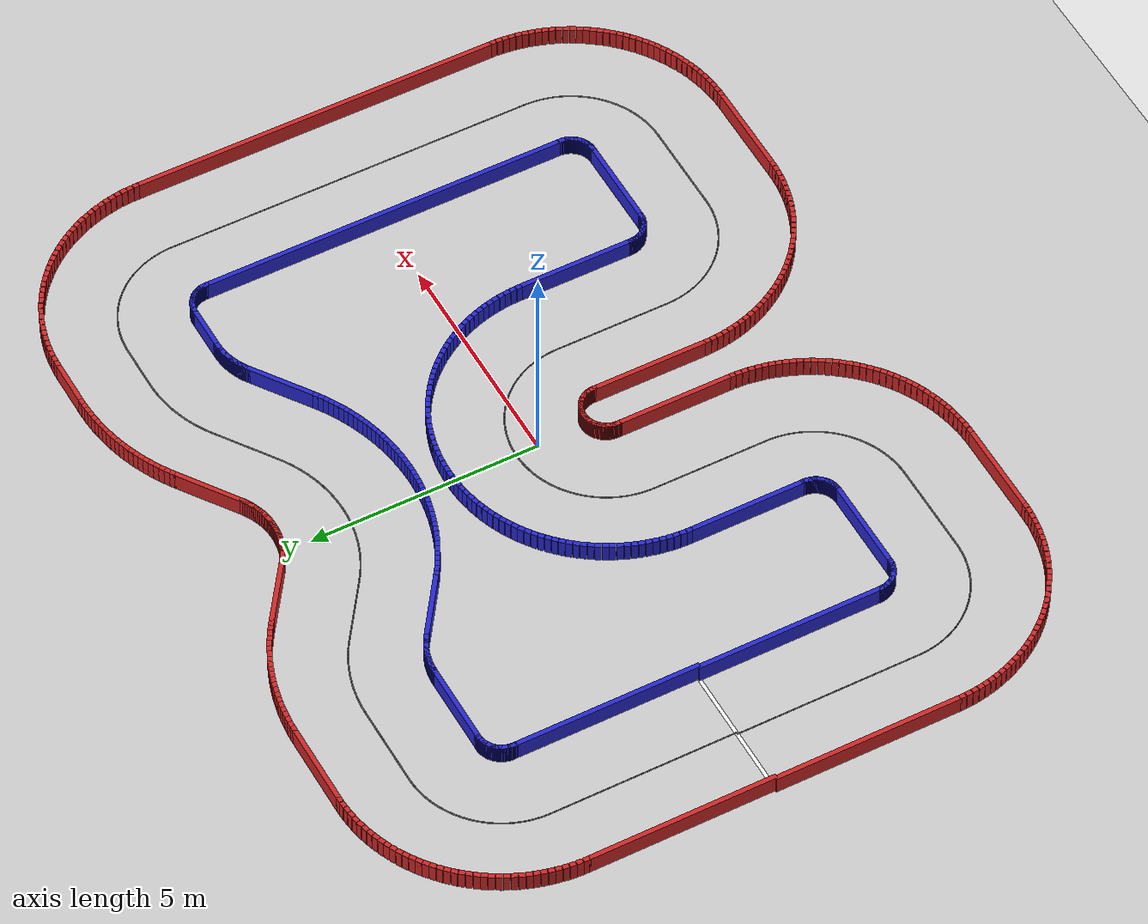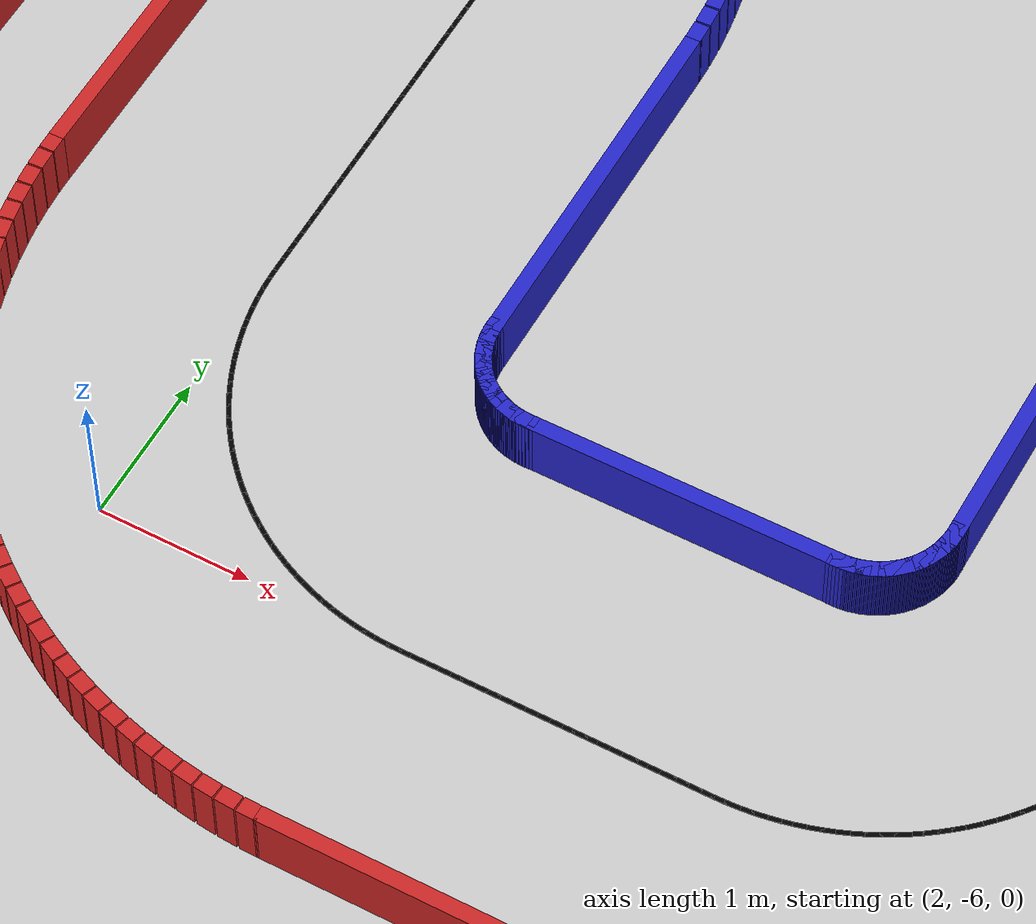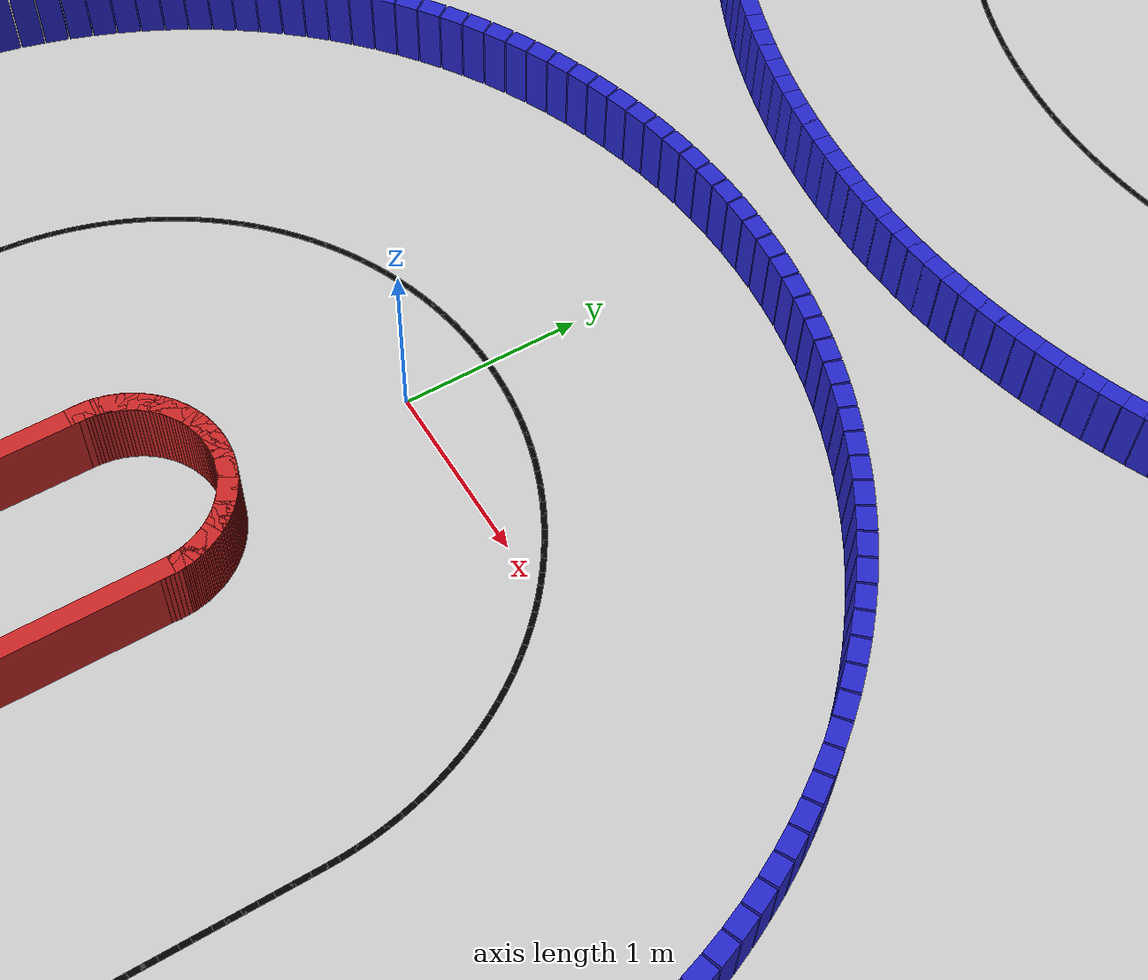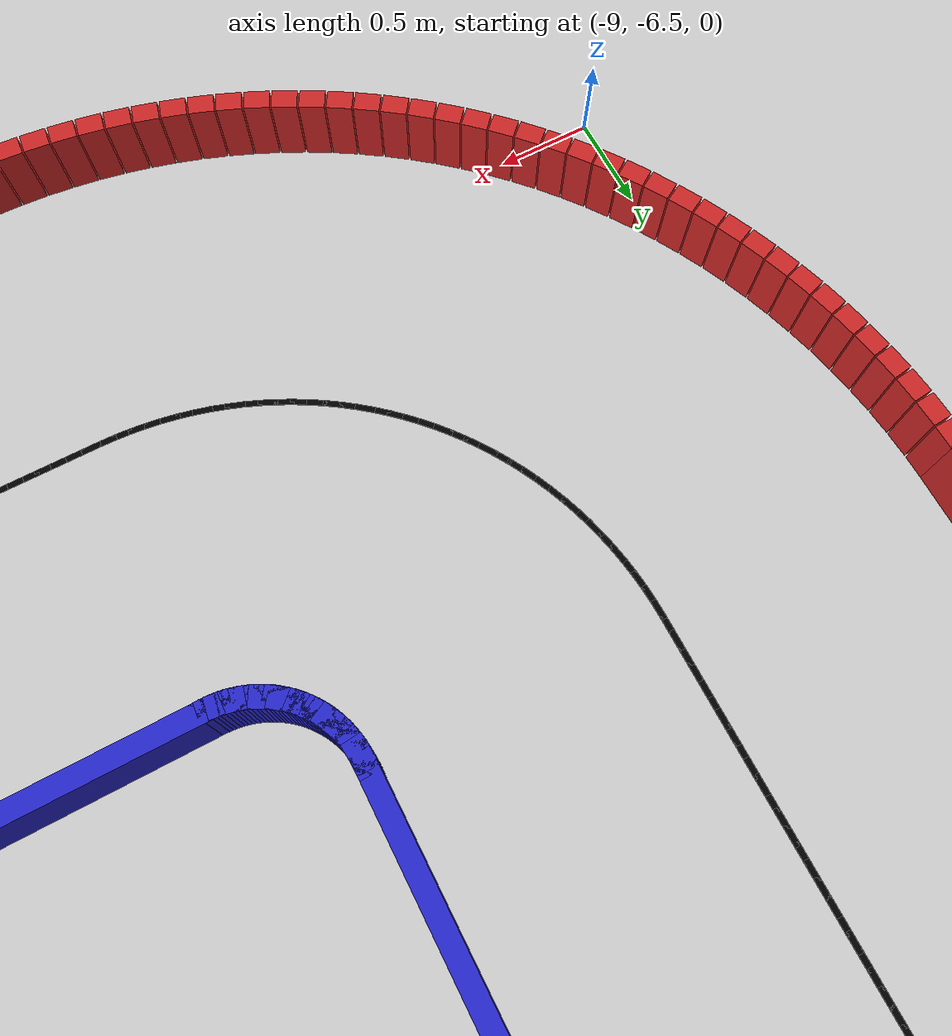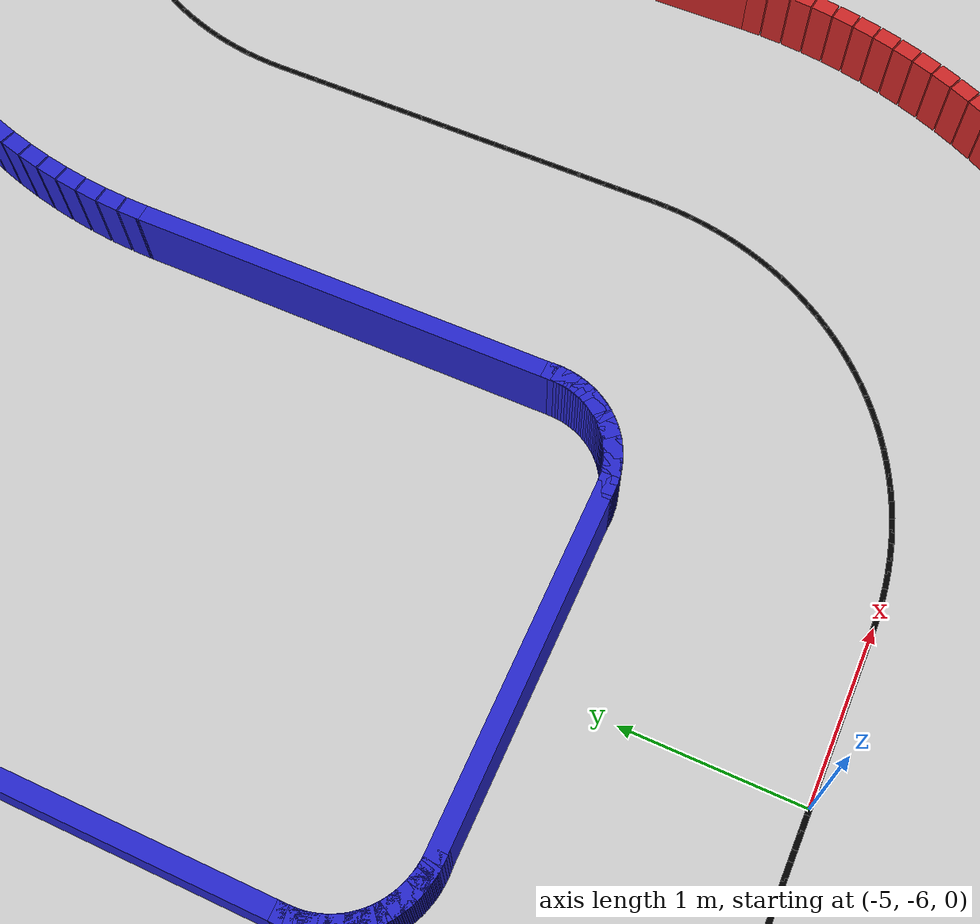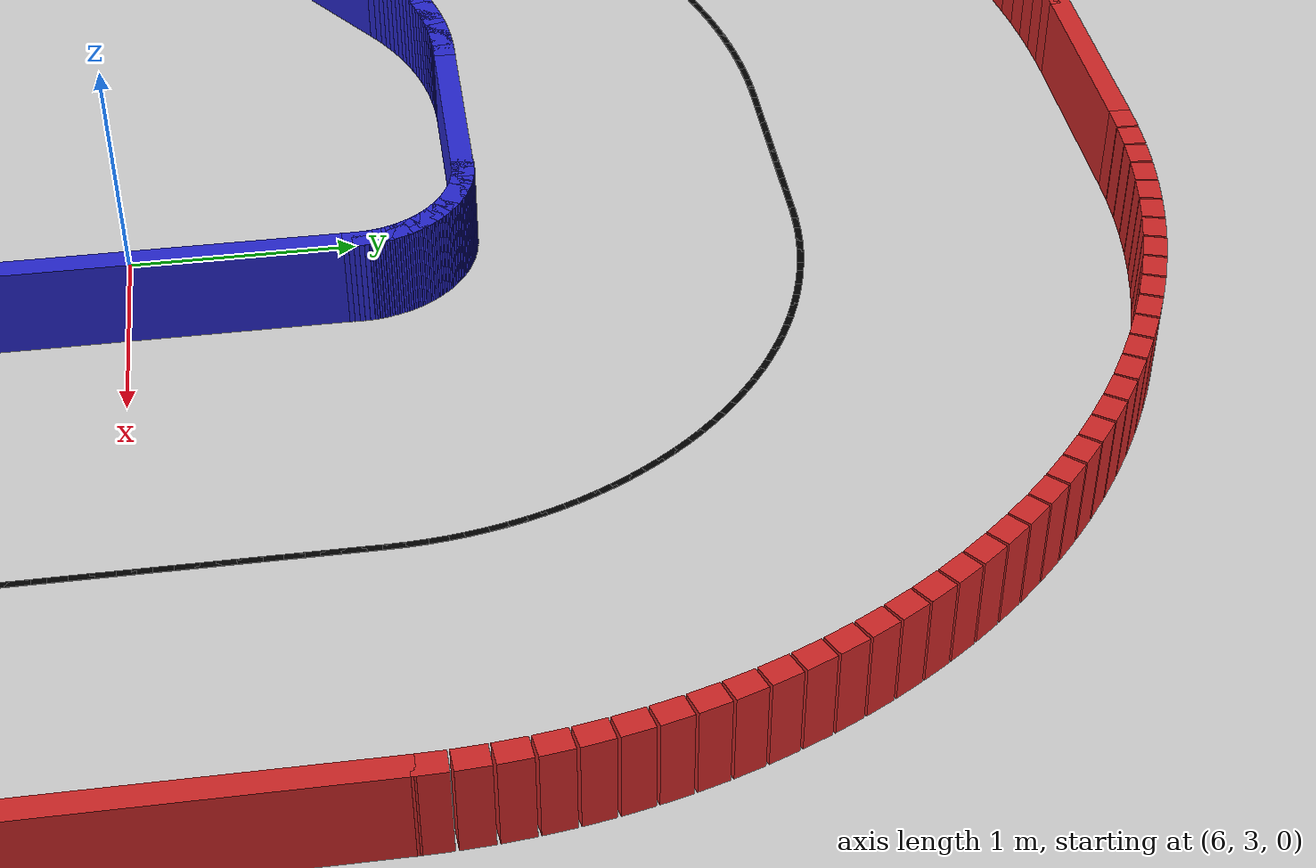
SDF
<?xml version='1.0' encoding='utf-8'?>
<sdf version="1.6">
  <world name="new_race_track">
    <include><uri>model://ground_plane</uri></include>
    <include><uri>model://sun</uri></include>
    <scene><shadows>false</shadows></scene>
    <gui fullscreen="0">
      <camera name="user_camera">
        <pose>0 0 25.0 0 1.5708 0</pose>
        <view_controller>orbit</view_controller>
      </camera>
    </gui>
    <physics type="ode">
      <real_time_update_rate>500</real_time_update_rate>
      <max_step_size>0.002</max_step_size>
      <real_time_factor>1</real_time_factor>
    </physics>
    <model name="start_line"><static>true</static>
          <pose>-8.0000 0.0000 0.001 0 0 0</pose>
          <link name="l"><visual name="v"><geometry>
            <box><size>3.0 0.08 0.001</size></box></geometry>
            <material><ambient>1 1 1 1</ambient><diffuse>1 1 1 1</diffuse>
            </material></visual></link>
        </model>
  <model name="race_track"><static>true</static><pose>0 0 0 0 0 0</pose><link name="merged_wall_link_0"><pose>-6.5000 -2.0000 0.2000 0.0000 0.0000 -1.5708</pose><collision name="c"><geometry><box><size>4.0500 0.1000 0.4000</size></box></geometry></collision><visual name="v"><geometry><box><size>4.0500 0.1000 0.4000</size></box></geometry><material><ambient>0.15 0.15 0.8 1</ambient><diffuse>0.15 0.15 0.8 1</diffuse></material></visual></link><link name="wall_link_1"><collision name="c"><geometry><box><size>0.1305 0.1 0.4</size></box></geometry></collision><visual name="v"><geometry><box><size>0.1305 0.1 0.4</size></box></geometry><material><ambient>0.15 0.15 0.8 1</ambient><diffuse>0.15 0.15 0.8 1</diffuse></material></visual><pose>-6.4995 -4.0101 0.200 0 0 -1.5507</pose></link><link name="wall_link_2"><collision name="c"><geometry><box><size>0.1305 0.1 0.4</size></box></geometry></collision><visual name="v"><geometry><box><size>0.1305 0.1 0.4</size></box></geometry><material><ambient>0.15 0.15 0.8 1</ambient><diffuse>0.15 0.15 0.8 1</diffuse></material></visual><pose>-6.4987 -4.0302 0.200 0 0 -1.5104</pose></link><link name="wall_link_3"><collision name="c"><geometry><box><size>0.1305 0.1 0.4</size></box></geometry></collision><visual name="v"><geometry><box><size>0.1305 0.1 0.4</size></box></geometry><material><ambient>0.15 0.15 0.8 1</ambient><diffuse>0.15 0.15 0.8 1</diffuse></material></visual><pose>-6.4971 -4.0502 0.200 0 0 -1.4701</pose></link><link name="wall_link_4"><collision name="c"><geometry><box><size>0.1305 0.1 0.4</size></box></geometry></collision><visual name="v"><geometry><box><size>0.1305 0.1 0.4</size></box></geometry><material><ambient>0.15 0.15 0.8 1</ambient><diffuse>0.15 0.15 0.8 1</diffuse></material></visual><pose>-6.4946 -4.0702 0.200 0 0 -1.4298</pose></link><link name="wall_link_5"><collision name="c"><geometry><box><size>0.1305 0.1 0.4</size></box></geometry></collision><visual name="v"><geometry><box><size>0.1305 0.1 0.4</size></box></geometry><material><ambient>0.15 0.15 0.8 1</ambient><diffuse>0.15 0.15 0.8 1</diffuse></material></visual><pose>-6.4914 -4.0901 0.200 0 0 -1.3896</pose></link><link name="wall_link_6"><collision name="c"><geometry><box><size>0.1305 0.1 0.4</size></box></geometry></collision><visual name="v"><geometry><box><size>0.1305 0.1 0.4</size></box></geometry><material><ambient>0.15 0.15 0.8 1</ambient><diffuse>0.15 0.15 0.8 1</diffuse></material></visual><pose>-6.4874 -4.1098 0.200 0 0 -1.3493</pose></link><link name="wall_link_7"><collision name="c"><geometry><box><size>0.1305 0.1 0.4</size></box></geometry></collision><visual name="v"><geometry><box><size>0.1305 0.1 0.4</size></box></geometry><material><ambient>0.15 0.15 0.8 1</ambient><diffuse>0.15 0.15 0.8 1</diffuse></material></visual><pose>-6.4826 -4.1293 0.200 0 0 -1.3090</pose></link><link name="wall_link_8"><collision name="c"><geometry><box><size>0.1305 0.1 0.4</size></box></geometry></collision><visual name="v"><geometry><box><size>0.1305 0.1 0.4</size></box></geometry><material><ambient>0.15 0.15 0.8 1</ambient><diffuse>0.15 0.15 0.8 1</diffuse></material></visual><pose>-6.4770 -4.1486 0.200 0 0 -1.2687</pose></link><link name="wall_link_9"><collision name="c"><geometry><box><size>0.1305 0.1 0.4</size></box></geometry></collision><visual name="v"><geometry><box><size>0.1305 0.1 0.4</size></box></geometry><material><ambient>0.15 0.15 0.8 1</ambient><diffuse>0.15 0.15 0.8 1</diffuse></material></visual><pose>-6.4706 -4.1677 0.200 0 0 -1.2284</pose></link><link name="wall_link_10"><collision name="c"><geometry><box><size>0.1305 0.1 0.4</size></box></geometry></collision><visual name="v"><geometry><box><size>0.1305 0.1 0.4</size></box></geometry><material><ambient>0.15 0.15 0.8 1</ambient><diffuse>0.15 0.15 0.8 1</diffuse></material></visual><pose>-6.4635 -4.1865 0.200 0 0 -1.1882</pose></link><link name="wall_link_11"><collision name="c"><geometry><box><size>0.1305 0.1 0.4</size></box></geometry></collision><visual name="v"><geometry><box><size>0.1305 0.1 0.4</size></box></geometry><material><ambient>0.15 0.15 0.8 1</ambient><diffuse>0.15 0.15 0.8 1</diffuse></material></visual><pose>-6.4556 -4.2050 0.200 0 0 -1.1479</pose></link><link name="wall_link_12"><collision name="c"><geometry><box><size>0.1305 0.1 0.4</size></box></geometry></collision><visual name="v"><geometry><box><size>0.1305 0.1 0.4</size></box></geometry><material><ambient>0.15 0.15 0.8 1</ambient><diffuse>0.15 0.15 0.8 1</diffuse></material></visual><pose>-6.4470 -4.2232 0.200 0 0 -1.1076</pose></link><link name="wall_link_13"><collision name="c"><geometry><box><size>0.1305 0.1 0.4</size></box></geometry></collision><visual name="v"><geometry><box><size>0.1305 0.1 0.4</size></box></geometry><material><ambient>0.15 0.15 0.8 1</ambient><diffuse>0.15 0.15 0.8 1</diffuse></material></visual><pose>-6.4376 -4.2410 0.200 0 0 -1.0673</pose></link><link name="wall_link_14"><collision name="c"><geometry><box><size>0.1305 0.1 0.4</size></box></geometry></collision><visual name="v"><geometry><box><size>0.1305 0.1 0.4</size></box></geometry><material><ambient>0.15 0.15 0.8 1</ambient><diffuse>0.15 0.15 0.8 1</diffuse></material></visual><pose>-6.4275 -4.2585 0.200 0 0 -1.0271</pose></link><link name="wall_link_15"><collision name="c"><geometry><box><size>0.1305 0.1 0.4</size></box></geometry></collision><visual name="v"><geometry><box><size>0.1305 0.1 0.4</size></box></geometry><material><ambient>0.15 0.15 0.8 1</ambient><diffuse>0.15 0.15 0.8 1</diffuse></material></visual><pose>-6.4168 -4.2755 0.200 0 0 -0.9868</pose></link><link name="wall_link_16"><collision name="c"><geometry><box><size>0.1305 0.1 0.4</size></box></geometry></collision><visual name="v"><geometry><box><size>0.1305 0.1 0.4</size></box></geometry><material><ambient>0.15 0.15 0.8 1</ambient><diffuse>0.15 0.15 0.8 1</diffuse></material></visual><pose>-6.4054 -4.2920 0.200 0 0 -0.9465</pose></link><link name="wall_link_17"><collision name="c"><geometry><box><size>0.1305 0.1 0.4</size></box></geometry></collision><visual name="v"><geometry><box><size>0.1305 0.1 0.4</size></box></geometry><material><ambient>0.15 0.15 0.8 1</ambient><diffuse>0.15 0.15 0.8 1</diffuse></material></visual><pose>-6.3933 -4.3081 0.200 0 0 -0.9062</pose></link><link name="wall_link_18"><collision name="c"><geometry><box><size>0.1305 0.1 0.4</size></box></geometry></collision><visual name="v"><geometry><box><size>0.1305 0.1 0.4</size></box></geometry><material><ambient>0.15 0.15 0.8 1</ambient><diffuse>0.15 0.15 0.8 1</diffuse></material></visual><pose>-6.3805 -4.3237 0.200 0 0 -0.8660</pose></link><link name="wall_link_19"><collision name="c"><geometry><box><size>0.1305 0.1 0.4</size></box></geometry></collision><visual name="v"><geometry><box><size>0.1305 0.1 0.4</size></box></geometry><material><ambient>0.15 0.15 0.8 1</ambient><diffuse>0.15 0.15 0.8 1</diffuse></material></visual><pose>-6.3672 -4.3388 0.200 0 0 -0.8257</pose></link><link name="wall_link_20"><collision name="c"><geometry><box><size>0.1305 0.1 0.4</size></box></geometry></collision><visual name="v"><geometry><box><size>0.1305 0.1 0.4</size></box></geometry><material><ambient>0.15 0.15 0.8 1</ambient><diffuse>0.15 0.15 0.8 1</diffuse></material></visual><pose>-6.3533 -4.3533 0.200 0 0 -0.7854</pose></link><link name="wall_link_21"><collision name="c"><geometry><box><size>0.1305 0.1 0.4</size></box></geometry></collision><visual name="v"><geometry><box><size>0.1305 0.1 0.4</size></box></geometry><material><ambient>0.15 0.15 0.8 1</ambient><diffuse>0.15 0.15 0.8 1</diffuse></material></visual><pose>-6.3388 -4.3672 0.200 0 0 -0.7451</pose></link><link name="wall_link_22"><collision name="c"><geometry><box><size>0.1305 0.1 0.4</size></box></geometry></collision><visual name="v"><geometry><box><size>0.1305 0.1 0.4</size></box></geometry><material><ambient>0.15 0.15 0.8 1</ambient><diffuse>0.15 0.15 0.8 1</diffuse></material></visual><pose>-6.3237 -4.3805 0.200 0 0 -0.7048</pose></link><link name="wall_link_23"><collision name="c"><geometry><box><size>0.1305 0.1 0.4</size></box></geometry></collision><visual name="v"><geometry><box><size>0.1305 0.1 0.4</size></box></geometry><material><ambient>0.15 0.15 0.8 1</ambient><diffuse>0.15 0.15 0.8 1</diffuse></material></visual><pose>-6.3081 -4.3933 0.200 0 0 -0.6646</pose></link><link name="wall_link_24"><collision name="c"><geometry><box><size>0.1305 0.1 0.4</size></box></geometry></collision><visual name="v"><geometry><box><size>0.1305 0.1 0.4</size></box></geometry><material><ambient>0.15 0.15 0.8 1</ambient><diffuse>0.15 0.15 0.8 1</diffuse></material></visual><pose>-6.2920 -4.4054 0.200 0 0 -0.6243</pose></link><link name="wall_link_25"><collision name="c"><geometry><box><size>0.1305 0.1 0.4</size></box></geometry></collision><visual name="v"><geometry><box><size>0.1305 0.1 0.4</size></box></geometry><material><ambient>0.15 0.15 0.8 1</ambient><diffuse>0.15 0.15 0.8 1</diffuse></material></visual><pose>-6.2755 -4.4168 0.200 0 0 -0.5840</pose></link><link name="wall_link_26"><collision name="c"><geometry><box><size>0.1305 0.1 0.4</size></box></geometry></collision><visual name="v"><geometry><box><size>0.1305 0.1 0.4</size></box></geometry><material><ambient>0.15 0.15 0.8 1</ambient><diffuse>0.15 0.15 0.8 1</diffuse></material></visual><pose>-6.2585 -4.4275 0.200 0 0 -0.5437</pose></link><link name="wall_link_27"><collision name="c"><geometry><box><size>0.1305 0.1 0.4</size></box></geometry></collision><visual name="v"><geometry><box><size>0.1305 0.1 0.4</size></box></geometry><material><ambient>0.15 0.15 0.8 1</ambient><diffuse>0.15 0.15 0.8 1</diffuse></material></visual><pose>-6.2410 -4.4376 0.200 0 0 -0.5035</pose></link><link name="wall_link_28"><collision name="c"><geometry><box><size>0.1305 0.1 0.4</size></box></geometry></collision><visual name="v"><geometry><box><size>0.1305 0.1 0.4</size></box></geometry><material><ambient>0.15 0.15 0.8 1</ambient><diffuse>0.15 0.15 0.8 1</diffuse></material></visual><pose>-6.2232 -4.4470 0.200 0 0 -0.4632</pose></link><link name="wall_link_29"><collision name="c"><geometry><box><size>0.1305 0.1 0.4</size></box></geometry></collision><visual name="v"><geometry><box><size>0.1305 0.1 0.4</size></box></geometry><material><ambient>0.15 0.15 0.8 1</ambient><diffuse>0.15 0.15 0.8 1</diffuse></material></visual><pose>-6.2050 -4.4556 0.200 0 0 -0.4229</pose></link><link name="wall_link_30"><collision name="c"><geometry><box><size>0.1305 0.1 0.4</size></box></geometry></collision><visual name="v"><geometry><box><size>0.1305 0.1 0.4</size></box></geometry><material><ambient>0.15 0.15 0.8 1</ambient><diffuse>0.15 0.15 0.8 1</diffuse></material></visual><pose>-6.1865 -4.4635 0.200 0 0 -0.3826</pose></link><link name="wall_link_31"><collision name="c"><geometry><box><size>0.1305 0.1 0.4</size></box></geometry></collision><visual name="v"><geometry><box><size>0.1305 0.1 0.4</size></box></geometry><material><ambient>0.15 0.15 0.8 1</ambient><diffuse>0.15 0.15 0.8 1</diffuse></material></visual><pose>-6.1677 -4.4706 0.200 0 0 -0.3424</pose></link><link name="wall_link_32"><collision name="c"><geometry><box><size>0.1305 0.1 0.4</size></box></geometry></collision><visual name="v"><geometry><box><size>0.1305 0.1 0.4</size></box></geometry><material><ambient>0.15 0.15 0.8 1</ambient><diffuse>0.15 0.15 0.8 1</diffuse></material></visual><pose>-6.1486 -4.4770 0.200 0 0 -0.3021</pose></link><link name="wall_link_33"><collision name="c"><geometry><box><size>0.1305 0.1 0.4</size></box></geometry></collision><visual name="v"><geometry><box><size>0.1305 0.1 0.4</size></box></geometry><material><ambient>0.15 0.15 0.8 1</ambient><diffuse>0.15 0.15 0.8 1</diffuse></material></visual><pose>-6.1293 -4.4826 0.200 0 0 -0.2618</pose></link><link name="wall_link_34"><collision name="c"><geometry><box><size>0.1305 0.1 0.4</size></box></geometry></collision><visual name="v"><geometry><box><size>0.1305 0.1 0.4</size></box></geometry><material><ambient>0.15 0.15 0.8 1</ambient><diffuse>0.15 0.15 0.8 1</diffuse></material></visual><pose>-6.1098 -4.4874 0.200 0 0 -0.2215</pose></link><link name="wall_link_35"><collision name="c"><geometry><box><size>0.1305 0.1 0.4</size></box></geometry></collision><visual name="v"><geometry><box><size>0.1305 0.1 0.4</size></box></geometry><material><ambient>0.15 0.15 0.8 1</ambient><diffuse>0.15 0.15 0.8 1</diffuse></material></visual><pose>-6.0901 -4.4914 0.200 0 0 -0.1812</pose></link><link name="wall_link_36"><collision name="c"><geometry><box><size>0.1305 0.1 0.4</size></box></geometry></collision><visual name="v"><geometry><box><size>0.1305 0.1 0.4</size></box></geometry><material><ambient>0.15 0.15 0.8 1</ambient><diffuse>0.15 0.15 0.8 1</diffuse></material></visual><pose>-6.0702 -4.4946 0.200 0 0 -0.1410</pose></link><link name="wall_link_37"><collision name="c"><geometry><box><size>0.1305 0.1 0.4</size></box></geometry></collision><visual name="v"><geometry><box><size>0.1305 0.1 0.4</size></box></geometry><material><ambient>0.15 0.15 0.8 1</ambient><diffuse>0.15 0.15 0.8 1</diffuse></material></visual><pose>-6.0502 -4.4971 0.200 0 0 -0.1007</pose></link><link name="wall_link_38"><collision name="c"><geometry><box><size>0.1305 0.1 0.4</size></box></geometry></collision><visual name="v"><geometry><box><size>0.1305 0.1 0.4</size></box></geometry><material><ambient>0.15 0.15 0.8 1</ambient><diffuse>0.15 0.15 0.8 1</diffuse></material></visual><pose>-6.0302 -4.4987 0.200 0 0 -0.0604</pose></link><link name="wall_link_39"><collision name="c"><geometry><box><size>0.1305 0.1 0.4</size></box></geometry></collision><visual name="v"><geometry><box><size>0.1305 0.1 0.4</size></box></geometry><material><ambient>0.15 0.15 0.8 1</ambient><diffuse>0.15 0.15 0.8 1</diffuse></material></visual><pose>-6.0101 -4.4995 0.200 0 0 -0.0201</pose></link><link name="merged_wall_link_40"><pose>-5.0000 -4.5000 0.2000 0.0000 0.0000 0.0000</pose><collision name="c"><geometry><box><size>2.0500 0.1000 0.4000</size></box></geometry></collision><visual name="v"><geometry><box><size>2.0500 0.1000 0.4000</size></box></geometry><material><ambient>0.15 0.15 0.8 1</ambient><diffuse>0.15 0.15 0.8 1</diffuse></material></visual></link><link name="wall_link_41"><collision name="c"><geometry><box><size>0.1305 0.1 0.4</size></box></geometry></collision><visual name="v"><geometry><box><size>0.1305 0.1 0.4</size></box></geometry><material><ambient>0.15 0.15 0.8 1</ambient><diffuse>0.15 0.15 0.8 1</diffuse></material></visual><pose>-3.9899 -4.4995 0.200 0 0 0.0201</pose></link><link name="wall_link_42"><collision name="c"><geometry><box><size>0.1305 0.1 0.4</size></box></geometry></collision><visual name="v"><geometry><box><size>0.1305 0.1 0.4</size></box></geometry><material><ambient>0.15 0.15 0.8 1</ambient><diffuse>0.15 0.15 0.8 1</diffuse></material></visual><pose>-3.9698 -4.4987 0.200 0 0 0.0604</pose></link><link name="wall_link_43"><collision name="c"><geometry><box><size>0.1305 0.1 0.4</size></box></geometry></collision><visual name="v"><geometry><box><size>0.1305 0.1 0.4</size></box></geometry><material><ambient>0.15 0.15 0.8 1</ambient><diffuse>0.15 0.15 0.8 1</diffuse></material></visual><pose>-3.9498 -4.4971 0.200 0 0 0.1007</pose></link><link name="wall_link_44"><collision name="c"><geometry><box><size>0.1305 0.1 0.4</size></box></geometry></collision><visual name="v"><geometry><box><size>0.1305 0.1 0.4</size></box></geometry><material><ambient>0.15 0.15 0.8 1</ambient><diffuse>0.15 0.15 0.8 1</diffuse></material></visual><pose>-3.9298 -4.4946 0.200 0 0 0.1410</pose></link><link name="wall_link_45"><collision name="c"><geometry><box><size>0.1305 0.1 0.4</size></box></geometry></collision><visual name="v"><geometry><box><size>0.1305 0.1 0.4</size></box></geometry><material><ambient>0.15 0.15 0.8 1</ambient><diffuse>0.15 0.15 0.8 1</diffuse></material></visual><pose>-3.9099 -4.4914 0.200 0 0 0.1812</pose></link><link name="wall_link_46"><collision name="c"><geometry><box><size>0.1305 0.1 0.4</size></box></geometry></collision><visual name="v"><geometry><box><size>0.1305 0.1 0.4</size></box></geometry><material><ambient>0.15 0.15 0.8 1</ambient><diffuse>0.15 0.15 0.8 1</diffuse></material></visual><pose>-3.8902 -4.4874 0.200 0 0 0.2215</pose></link><link name="wall_link_47"><collision name="c"><geometry><box><size>0.1305 0.1 0.4</size></box></geometry></collision><visual name="v"><geometry><box><size>0.1305 0.1 0.4</size></box></geometry><material><ambient>0.15 0.15 0.8 1</ambient><diffuse>0.15 0.15 0.8 1</diffuse></material></visual><pose>-3.8707 -4.4826 0.200 0 0 0.2618</pose></link><link name="wall_link_48"><collision name="c"><geometry><box><size>0.1305 0.1 0.4</size></box></geometry></collision><visual name="v"><geometry><box><size>0.1305 0.1 0.4</size></box></geometry><material><ambient>0.15 0.15 0.8 1</ambient><diffuse>0.15 0.15 0.8 1</diffuse></material></visual><pose>-3.8514 -4.4770 0.200 0 0 0.3021</pose></link><link name="wall_link_49"><collision name="c"><geometry><box><size>0.1305 0.1 0.4</size></box></geometry></collision><visual name="v"><geometry><box><size>0.1305 0.1 0.4</size></box></geometry><material><ambient>0.15 0.15 0.8 1</ambient><diffuse>0.15 0.15 0.8 1</diffuse></material></visual><pose>-3.8323 -4.4706 0.200 0 0 0.3424</pose></link><link name="wall_link_50"><collision name="c"><geometry><box><size>0.1305 0.1 0.4</size></box></geometry></collision><visual name="v"><geometry><box><size>0.1305 0.1 0.4</size></box></geometry><material><ambient>0.15 0.15 0.8 1</ambient><diffuse>0.15 0.15 0.8 1</diffuse></material></visual><pose>-3.8135 -4.4635 0.200 0 0 0.3826</pose></link><link name="wall_link_51"><collision name="c"><geometry><box><size>0.1305 0.1 0.4</size></box></geometry></collision><visual name="v"><geometry><box><size>0.1305 0.1 0.4</size></box></geometry><material><ambient>0.15 0.15 0.8 1</ambient><diffuse>0.15 0.15 0.8 1</diffuse></material></visual><pose>-3.7950 -4.4556 0.200 0 0 0.4229</pose></link><link name="wall_link_52"><collision name="c"><geometry><box><size>0.1305 0.1 0.4</size></box></geometry></collision><visual name="v"><geometry><box><size>0.1305 0.1 0.4</size></box></geometry><material><ambient>0.15 0.15 0.8 1</ambient><diffuse>0.15 0.15 0.8 1</diffuse></material></visual><pose>-3.7768 -4.4470 0.200 0 0 0.4632</pose></link><link name="wall_link_53"><collision name="c"><geometry><box><size>0.1305 0.1 0.4</size></box></geometry></collision><visual name="v"><geometry><box><size>0.1305 0.1 0.4</size></box></geometry><material><ambient>0.15 0.15 0.8 1</ambient><diffuse>0.15 0.15 0.8 1</diffuse></material></visual><pose>-3.7590 -4.4376 0.200 0 0 0.5035</pose></link><link name="wall_link_54"><collision name="c"><geometry><box><size>0.1305 0.1 0.4</size></box></geometry></collision><visual name="v"><geometry><box><size>0.1305 0.1 0.4</size></box></geometry><material><ambient>0.15 0.15 0.8 1</ambient><diffuse>0.15 0.15 0.8 1</diffuse></material></visual><pose>-3.7415 -4.4275 0.200 0 0 0.5437</pose></link><link name="wall_link_55"><collision name="c"><geometry><box><size>0.1305 0.1 0.4</size></box></geometry></collision><visual name="v"><geometry><box><size>0.1305 0.1 0.4</size></box></geometry><material><ambient>0.15 0.15 0.8 1</ambient><diffuse>0.15 0.15 0.8 1</diffuse></material></visual><pose>-3.7245 -4.4168 0.200 0 0 0.5840</pose></link><link name="wall_link_56"><collision name="c"><geometry><box><size>0.1305 0.1 0.4</size></box></geometry></collision><visual name="v"><geometry><box><size>0.1305 0.1 0.4</size></box></geometry><material><ambient>0.15 0.15 0.8 1</ambient><diffuse>0.15 0.15 0.8 1</diffuse></material></visual><pose>-3.7080 -4.4054 0.200 0 0 0.6243</pose></link><link name="wall_link_57"><collision name="c"><geometry><box><size>0.1305 0.1 0.4</size></box></geometry></collision><visual name="v"><geometry><box><size>0.1305 0.1 0.4</size></box></geometry><material><ambient>0.15 0.15 0.8 1</ambient><diffuse>0.15 0.15 0.8 1</diffuse></material></visual><pose>-3.6919 -4.3933 0.200 0 0 0.6646</pose></link><link name="wall_link_58"><collision name="c"><geometry><box><size>0.1305 0.1 0.4</size></box></geometry></collision><visual name="v"><geometry><box><size>0.1305 0.1 0.4</size></box></geometry><material><ambient>0.15 0.15 0.8 1</ambient><diffuse>0.15 0.15 0.8 1</diffuse></material></visual><pose>-3.6763 -4.3805 0.200 0 0 0.7048</pose></link><link name="wall_link_59"><collision name="c"><geometry><box><size>0.1305 0.1 0.4</size></box></geometry></collision><visual name="v"><geometry><box><size>0.1305 0.1 0.4</size></box></geometry><material><ambient>0.15 0.15 0.8 1</ambient><diffuse>0.15 0.15 0.8 1</diffuse></material></visual><pose>-3.6612 -4.3672 0.200 0 0 0.7451</pose></link><link name="wall_link_60"><collision name="c"><geometry><box><size>0.1305 0.1 0.4</size></box></geometry></collision><visual name="v"><geometry><box><size>0.1305 0.1 0.4</size></box></geometry><material><ambient>0.15 0.15 0.8 1</ambient><diffuse>0.15 0.15 0.8 1</diffuse></material></visual><pose>-3.6467 -4.3533 0.200 0 0 0.7854</pose></link><link name="wall_link_61"><collision name="c"><geometry><box><size>0.1305 0.1 0.4</size></box></geometry></collision><visual name="v"><geometry><box><size>0.1305 0.1 0.4</size></box></geometry><material><ambient>0.15 0.15 0.8 1</ambient><diffuse>0.15 0.15 0.8 1</diffuse></material></visual><pose>-3.6328 -4.3388 0.200 0 0 0.8257</pose></link><link name="wall_link_62"><collision name="c"><geometry><box><size>0.1305 0.1 0.4</size></box></geometry></collision><visual name="v"><geometry><box><size>0.1305 0.1 0.4</size></box></geometry><material><ambient>0.15 0.15 0.8 1</ambient><diffuse>0.15 0.15 0.8 1</diffuse></material></visual><pose>-3.6195 -4.3237 0.200 0 0 0.8660</pose></link><link name="wall_link_63"><collision name="c"><geometry><box><size>0.1305 0.1 0.4</size></box></geometry></collision><visual name="v"><geometry><box><size>0.1305 0.1 0.4</size></box></geometry><material><ambient>0.15 0.15 0.8 1</ambient><diffuse>0.15 0.15 0.8 1</diffuse></material></visual><pose>-3.6067 -4.3081 0.200 0 0 0.9062</pose></link><link name="wall_link_64"><collision name="c"><geometry><box><size>0.1305 0.1 0.4</size></box></geometry></collision><visual name="v"><geometry><box><size>0.1305 0.1 0.4</size></box></geometry><material><ambient>0.15 0.15 0.8 1</ambient><diffuse>0.15 0.15 0.8 1</diffuse></material></visual><pose>-3.5946 -4.2920 0.200 0 0 0.9465</pose></link><link name="wall_link_65"><collision name="c"><geometry><box><size>0.1305 0.1 0.4</size></box></geometry></collision><visual name="v"><geometry><box><size>0.1305 0.1 0.4</size></box></geometry><material><ambient>0.15 0.15 0.8 1</ambient><diffuse>0.15 0.15 0.8 1</diffuse></material></visual><pose>-3.5832 -4.2755 0.200 0 0 0.9868</pose></link><link name="wall_link_66"><collision name="c"><geometry><box><size>0.1305 0.1 0.4</size></box></geometry></collision><visual name="v"><geometry><box><size>0.1305 0.1 0.4</size></box></geometry><material><ambient>0.15 0.15 0.8 1</ambient><diffuse>0.15 0.15 0.8 1</diffuse></material></visual><pose>-3.5725 -4.2585 0.200 0 0 1.0271</pose></link><link name="wall_link_67"><collision name="c"><geometry><box><size>0.1305 0.1 0.4</size></box></geometry></collision><visual name="v"><geometry><box><size>0.1305 0.1 0.4</size></box></geometry><material><ambient>0.15 0.15 0.8 1</ambient><diffuse>0.15 0.15 0.8 1</diffuse></material></visual><pose>-3.5624 -4.2410 0.200 0 0 1.0673</pose></link><link name="wall_link_68"><collision name="c"><geometry><box><size>0.1305 0.1 0.4</size></box></geometry></collision><visual name="v"><geometry><box><size>0.1305 0.1 0.4</size></box></geometry><material><ambient>0.15 0.15 0.8 1</ambient><diffuse>0.15 0.15 0.8 1</diffuse></material></visual><pose>-3.5530 -4.2232 0.200 0 0 1.1076</pose></link><link name="wall_link_69"><collision name="c"><geometry><box><size>0.1305 0.1 0.4</size></box></geometry></collision><visual name="v"><geometry><box><size>0.1305 0.1 0.4</size></box></geometry><material><ambient>0.15 0.15 0.8 1</ambient><diffuse>0.15 0.15 0.8 1</diffuse></material></visual><pose>-3.5444 -4.2050 0.200 0 0 1.1479</pose></link><link name="wall_link_70"><collision name="c"><geometry><box><size>0.1305 0.1 0.4</size></box></geometry></collision><visual name="v"><geometry><box><size>0.1305 0.1 0.4</size></box></geometry><material><ambient>0.15 0.15 0.8 1</ambient><diffuse>0.15 0.15 0.8 1</diffuse></material></visual><pose>-3.5365 -4.1865 0.200 0 0 1.1882</pose></link><link name="wall_link_71"><collision name="c"><geometry><box><size>0.1305 0.1 0.4</size></box></geometry></collision><visual name="v"><geometry><box><size>0.1305 0.1 0.4</size></box></geometry><material><ambient>0.15 0.15 0.8 1</ambient><diffuse>0.15 0.15 0.8 1</diffuse></material></visual><pose>-3.5294 -4.1677 0.200 0 0 1.2284</pose></link><link name="wall_link_72"><collision name="c"><geometry><box><size>0.1305 0.1 0.4</size></box></geometry></collision><visual name="v"><geometry><box><size>0.1305 0.1 0.4</size></box></geometry><material><ambient>0.15 0.15 0.8 1</ambient><diffuse>0.15 0.15 0.8 1</diffuse></material></visual><pose>-3.5230 -4.1486 0.200 0 0 1.2687</pose></link><link name="wall_link_73"><collision name="c"><geometry><box><size>0.1305 0.1 0.4</size></box></geometry></collision><visual name="v"><geometry><box><size>0.1305 0.1 0.4</size></box></geometry><material><ambient>0.15 0.15 0.8 1</ambient><diffuse>0.15 0.15 0.8 1</diffuse></material></visual><pose>-3.5174 -4.1293 0.200 0 0 1.3090</pose></link><link name="wall_link_74"><collision name="c"><geometry><box><size>0.1305 0.1 0.4</size></box></geometry></collision><visual name="v"><geometry><box><size>0.1305 0.1 0.4</size></box></geometry><material><ambient>0.15 0.15 0.8 1</ambient><diffuse>0.15 0.15 0.8 1</diffuse></material></visual><pose>-3.5126 -4.1098 0.200 0 0 1.3493</pose></link><link name="wall_link_75"><collision name="c"><geometry><box><size>0.1305 0.1 0.4</size></box></geometry></collision><visual name="v"><geometry><box><size>0.1305 0.1 0.4</size></box></geometry><material><ambient>0.15 0.15 0.8 1</ambient><diffuse>0.15 0.15 0.8 1</diffuse></material></visual><pose>-3.5086 -4.0901 0.200 0 0 1.3896</pose></link><link name="wall_link_76"><collision name="c"><geometry><box><size>0.1305 0.1 0.4</size></box></geometry></collision><visual name="v"><geometry><box><size>0.1305 0.1 0.4</size></box></geometry><material><ambient>0.15 0.15 0.8 1</ambient><diffuse>0.15 0.15 0.8 1</diffuse></material></visual><pose>-3.5054 -4.0702 0.200 0 0 1.4298</pose></link><link name="wall_link_77"><collision name="c"><geometry><box><size>0.1305 0.1 0.4</size></box></geometry></collision><visual name="v"><geometry><box><size>0.1305 0.1 0.4</size></box></geometry><material><ambient>0.15 0.15 0.8 1</ambient><diffuse>0.15 0.15 0.8 1</diffuse></material></visual><pose>-3.5029 -4.0502 0.200 0 0 1.4701</pose></link><link name="wall_link_78"><collision name="c"><geometry><box><size>0.1305 0.1 0.4</size></box></geometry></collision><visual name="v"><geometry><box><size>0.1305 0.1 0.4</size></box></geometry><material><ambient>0.15 0.15 0.8 1</ambient><diffuse>0.15 0.15 0.8 1</diffuse></material></visual><pose>-3.5013 -4.0302 0.200 0 0 1.5104</pose></link><link name="wall_link_79"><collision name="c"><geometry><box><size>0.1305 0.1 0.4</size></box></geometry></collision><visual name="v"><geometry><box><size>0.1305 0.1 0.4</size></box></geometry><material><ambient>0.15 0.15 0.8 1</ambient><diffuse>0.15 0.15 0.8 1</diffuse></material></visual><pose>-3.5005 -4.0101 0.200 0 0 1.5507</pose></link><link name="merged_wall_link_80"><pose>-3.5000 -2.7600 0.2000 0.0000 0.0000 1.5708</pose><collision name="c"><geometry><box><size>2.5300 0.1000 0.4000</size></box></geometry></collision><visual name="v"><geometry><box><size>2.5300 0.1000 0.4000</size></box></geometry><material><ambient>0.15 0.15 0.8 1</ambient><diffuse>0.15 0.15 0.8 1</diffuse></material></visual></link><link name="wall_link_81"><collision name="c"><geometry><box><size>0.1305 0.1 0.4</size></box></geometry></collision><visual name="v"><geometry><box><size>0.1305 0.1 0.4</size></box></geometry><material><ambient>0.15 0.15 0.8 1</ambient><diffuse>0.15 0.15 0.8 1</diffuse></material></visual><pose>-3.4989 -1.4495 0.200 0 0 1.5507</pose></link><link name="wall_link_82"><collision name="c"><geometry><box><size>0.1305 0.1 0.4</size></box></geometry></collision><visual name="v"><geometry><box><size>0.1305 0.1 0.4</size></box></geometry><material><ambient>0.15 0.15 0.8 1</ambient><diffuse>0.15 0.15 0.8 1</diffuse></material></visual><pose>-3.4932 -1.3087 0.200 0 0 1.5104</pose></link><link name="wall_link_83"><collision name="c"><geometry><box><size>0.1305 0.1 0.4</size></box></geometry></collision><visual name="v"><geometry><box><size>0.1305 0.1 0.4</size></box></geometry><material><ambient>0.15 0.15 0.8 1</ambient><diffuse>0.15 0.15 0.8 1</diffuse></material></visual><pose>-3.4819 -1.1682 0.200 0 0 1.4701</pose></link><link name="wall_link_84"><collision name="c"><geometry><box><size>0.1305 0.1 0.4</size></box></geometry></collision><visual name="v"><geometry><box><size>0.1305 0.1 0.4</size></box></geometry><material><ambient>0.15 0.15 0.8 1</ambient><diffuse>0.15 0.15 0.8 1</diffuse></material></visual><pose>-3.4649 -1.0283 0.200 0 0 1.4298</pose></link><link name="wall_link_85"><collision name="c"><geometry><box><size>0.1305 0.1 0.4</size></box></geometry></collision><visual name="v"><geometry><box><size>0.1305 0.1 0.4</size></box></geometry><material><ambient>0.15 0.15 0.8 1</ambient><diffuse>0.15 0.15 0.8 1</diffuse></material></visual><pose>-3.4423 -0.8892 0.200 0 0 1.3896</pose></link><link name="wall_link_86"><collision name="c"><geometry><box><size>0.1305 0.1 0.4</size></box></geometry></collision><visual name="v"><geometry><box><size>0.1305 0.1 0.4</size></box></geometry><material><ambient>0.15 0.15 0.8 1</ambient><diffuse>0.15 0.15 0.8 1</diffuse></material></visual><pose>-3.4141 -0.7511 0.200 0 0 1.3493</pose></link><link name="wall_link_87"><collision name="c"><geometry><box><size>0.1305 0.1 0.4</size></box></geometry></collision><visual name="v"><geometry><box><size>0.1305 0.1 0.4</size></box></geometry><material><ambient>0.15 0.15 0.8 1</ambient><diffuse>0.15 0.15 0.8 1</diffuse></material></visual><pose>-3.3803 -0.6142 0.200 0 0 1.3090</pose></link><link name="wall_link_88"><collision name="c"><geometry><box><size>0.1305 0.1 0.4</size></box></geometry></collision><visual name="v"><geometry><box><size>0.1305 0.1 0.4</size></box></geometry><material><ambient>0.15 0.15 0.8 1</ambient><diffuse>0.15 0.15 0.8 1</diffuse></material></visual><pose>-3.3411 -0.4789 0.200 0 0 1.2687</pose></link><link name="wall_link_89"><collision name="c"><geometry><box><size>0.1305 0.1 0.4</size></box></geometry></collision><visual name="v"><geometry><box><size>0.1305 0.1 0.4</size></box></geometry><material><ambient>0.15 0.15 0.8 1</ambient><diffuse>0.15 0.15 0.8 1</diffuse></material></visual><pose>-3.2965 -0.3452 0.200 0 0 1.2284</pose></link><link name="wall_link_90"><collision name="c"><geometry><box><size>0.1305 0.1 0.4</size></box></geometry></collision><visual name="v"><geometry><box><size>0.1305 0.1 0.4</size></box></geometry><material><ambient>0.15 0.15 0.8 1</ambient><diffuse>0.15 0.15 0.8 1</diffuse></material></visual><pose>-3.2465 -0.2134 0.200 0 0 1.1882</pose></link><link name="wall_link_91"><collision name="c"><geometry><box><size>0.1305 0.1 0.4</size></box></geometry></collision><visual name="v"><geometry><box><size>0.1305 0.1 0.4</size></box></geometry><material><ambient>0.15 0.15 0.8 1</ambient><diffuse>0.15 0.15 0.8 1</diffuse></material></visual><pose>-3.1913 -0.0837 0.200 0 0 1.1479</pose></link><link name="wall_link_92"><collision name="c"><geometry><box><size>0.1305 0.1 0.4</size></box></geometry></collision><visual name="v"><geometry><box><size>0.1305 0.1 0.4</size></box></geometry><material><ambient>0.15 0.15 0.8 1</ambient><diffuse>0.15 0.15 0.8 1</diffuse></material></visual><pose>-3.1309 0.0436 0.200 0 0 1.1076</pose></link><link name="wall_link_93"><collision name="c"><geometry><box><size>0.1305 0.1 0.4</size></box></geometry></collision><visual name="v"><geometry><box><size>0.1305 0.1 0.4</size></box></geometry><material><ambient>0.15 0.15 0.8 1</ambient><diffuse>0.15 0.15 0.8 1</diffuse></material></visual><pose>-3.0654 0.1684 0.200 0 0 1.0673</pose></link><link name="wall_link_94"><collision name="c"><geometry><box><size>0.1305 0.1 0.4</size></box></geometry></collision><visual name="v"><geometry><box><size>0.1305 0.1 0.4</size></box></geometry><material><ambient>0.15 0.15 0.8 1</ambient><diffuse>0.15 0.15 0.8 1</diffuse></material></visual><pose>-2.9949 0.2905 0.200 0 0 1.0271</pose></link><link name="wall_link_95"><collision name="c"><geometry><box><size>0.1305 0.1 0.4</size></box></geometry></collision><visual name="v"><geometry><box><size>0.1305 0.1 0.4</size></box></geometry><material><ambient>0.15 0.15 0.8 1</ambient><diffuse>0.15 0.15 0.8 1</diffuse></material></visual><pose>-2.9196 0.4096 0.200 0 0 0.9868</pose></link><link name="wall_link_96"><collision name="c"><geometry><box><size>0.1305 0.1 0.4</size></box></geometry></collision><visual name="v"><geometry><box><size>0.1305 0.1 0.4</size></box></geometry><material><ambient>0.15 0.15 0.8 1</ambient><diffuse>0.15 0.15 0.8 1</diffuse></material></visual><pose>-2.8395 0.5256 0.200 0 0 0.9465</pose></link><link name="wall_link_97"><collision name="c"><geometry><box><size>0.1305 0.1 0.4</size></box></geometry></collision><visual name="v"><geometry><box><size>0.1305 0.1 0.4</size></box></geometry><material><ambient>0.15 0.15 0.8 1</ambient><diffuse>0.15 0.15 0.8 1</diffuse></material></visual><pose>-2.7548 0.6383 0.200 0 0 0.9062</pose></link><link name="wall_link_98"><collision name="c"><geometry><box><size>0.1305 0.1 0.4</size></box></geometry></collision><visual name="v"><geometry><box><size>0.1305 0.1 0.4</size></box></geometry><material><ambient>0.15 0.15 0.8 1</ambient><diffuse>0.15 0.15 0.8 1</diffuse></material></visual><pose>-2.6657 0.7474 0.200 0 0 0.8660</pose></link><link name="wall_link_99"><collision name="c"><geometry><box><size>0.1305 0.1 0.4</size></box></geometry></collision><visual name="v"><geometry><box><size>0.1305 0.1 0.4</size></box></geometry><material><ambient>0.15 0.15 0.8 1</ambient><diffuse>0.15 0.15 0.8 1</diffuse></material></visual><pose>-2.5722 0.8529 0.200 0 0 0.8257</pose></link><link name="wall_link_100"><collision name="c"><geometry><box><size>0.1305 0.1 0.4</size></box></geometry></collision><visual name="v"><geometry><box><size>0.1305 0.1 0.4</size></box></geometry><material><ambient>0.15 0.15 0.8 1</ambient><diffuse>0.15 0.15 0.8 1</diffuse></material></visual><pose>-2.4746 0.9546 0.200 0 0 0.7854</pose></link><link name="wall_link_101"><collision name="c"><geometry><box><size>0.1305 0.1 0.4</size></box></geometry></collision><visual name="v"><geometry><box><size>0.1305 0.1 0.4</size></box></geometry><material><ambient>0.15 0.15 0.8 1</ambient><diffuse>0.15 0.15 0.8 1</diffuse></material></visual><pose>-2.3729 1.0522 0.200 0 0 0.7451</pose></link><link name="wall_link_102"><collision name="c"><geometry><box><size>0.1305 0.1 0.4</size></box></geometry></collision><visual name="v"><geometry><box><size>0.1305 0.1 0.4</size></box></geometry><material><ambient>0.15 0.15 0.8 1</ambient><diffuse>0.15 0.15 0.8 1</diffuse></material></visual><pose>-2.2674 1.1457 0.200 0 0 0.7048</pose></link><link name="wall_link_103"><collision name="c"><geometry><box><size>0.1305 0.1 0.4</size></box></geometry></collision><visual name="v"><geometry><box><size>0.1305 0.1 0.4</size></box></geometry><material><ambient>0.15 0.15 0.8 1</ambient><diffuse>0.15 0.15 0.8 1</diffuse></material></visual><pose>-2.1583 1.2348 0.200 0 0 0.6646</pose></link><link name="wall_link_104"><collision name="c"><geometry><box><size>0.1305 0.1 0.4</size></box></geometry></collision><visual name="v"><geometry><box><size>0.1305 0.1 0.4</size></box></geometry><material><ambient>0.15 0.15 0.8 1</ambient><diffuse>0.15 0.15 0.8 1</diffuse></material></visual><pose>-2.0456 1.3195 0.200 0 0 0.6243</pose></link><link name="wall_link_105"><collision name="c"><geometry><box><size>0.1305 0.1 0.4</size></box></geometry></collision><visual name="v"><geometry><box><size>0.1305 0.1 0.4</size></box></geometry><material><ambient>0.15 0.15 0.8 1</ambient><diffuse>0.15 0.15 0.8 1</diffuse></material></visual><pose>-1.9296 1.3996 0.200 0 0 0.5840</pose></link><link name="wall_link_106"><collision name="c"><geometry><box><size>0.1305 0.1 0.4</size></box></geometry></collision><visual name="v"><geometry><box><size>0.1305 0.1 0.4</size></box></geometry><material><ambient>0.15 0.15 0.8 1</ambient><diffuse>0.15 0.15 0.8 1</diffuse></material></visual><pose>-1.8105 1.4749 0.200 0 0 0.5437</pose></link><link name="wall_link_107"><collision name="c"><geometry><box><size>0.1305 0.1 0.4</size></box></geometry></collision><visual name="v"><geometry><box><size>0.1305 0.1 0.4</size></box></geometry><material><ambient>0.15 0.15 0.8 1</ambient><diffuse>0.15 0.15 0.8 1</diffuse></material></visual><pose>-1.6884 1.5454 0.200 0 0 0.5035</pose></link><link name="wall_link_108"><collision name="c"><geometry><box><size>0.1305 0.1 0.4</size></box></geometry></collision><visual name="v"><geometry><box><size>0.1305 0.1 0.4</size></box></geometry><material><ambient>0.15 0.15 0.8 1</ambient><diffuse>0.15 0.15 0.8 1</diffuse></material></visual><pose>-1.5636 1.6109 0.200 0 0 0.4632</pose></link><link name="wall_link_109"><collision name="c"><geometry><box><size>0.1305 0.1 0.4</size></box></geometry></collision><visual name="v"><geometry><box><size>0.1305 0.1 0.4</size></box></geometry><material><ambient>0.15 0.15 0.8 1</ambient><diffuse>0.15 0.15 0.8 1</diffuse></material></visual><pose>-1.4363 1.6713 0.200 0 0 0.4229</pose></link><link name="wall_link_110"><collision name="c"><geometry><box><size>0.1305 0.1 0.4</size></box></geometry></collision><visual name="v"><geometry><box><size>0.1305 0.1 0.4</size></box></geometry><material><ambient>0.15 0.15 0.8 1</ambient><diffuse>0.15 0.15 0.8 1</diffuse></material></visual><pose>-1.3066 1.7265 0.200 0 0 0.3826</pose></link><link name="wall_link_111"><collision name="c"><geometry><box><size>0.1305 0.1 0.4</size></box></geometry></collision><visual name="v"><geometry><box><size>0.1305 0.1 0.4</size></box></geometry><material><ambient>0.15 0.15 0.8 1</ambient><diffuse>0.15 0.15 0.8 1</diffuse></material></visual><pose>-1.1748 1.7765 0.200 0 0 0.3424</pose></link><link name="wall_link_112"><collision name="c"><geometry><box><size>0.1305 0.1 0.4</size></box></geometry></collision><visual name="v"><geometry><box><size>0.1305 0.1 0.4</size></box></geometry><material><ambient>0.15 0.15 0.8 1</ambient><diffuse>0.15 0.15 0.8 1</diffuse></material></visual><pose>-1.0411 1.8211 0.200 0 0 0.3021</pose></link><link name="wall_link_113"><collision name="c"><geometry><box><size>0.1305 0.1 0.4</size></box></geometry></collision><visual name="v"><geometry><box><size>0.1305 0.1 0.4</size></box></geometry><material><ambient>0.15 0.15 0.8 1</ambient><diffuse>0.15 0.15 0.8 1</diffuse></material></visual><pose>-0.9058 1.8603 0.200 0 0 0.2618</pose></link><link name="wall_link_114"><collision name="c"><geometry><box><size>0.1305 0.1 0.4</size></box></geometry></collision><visual name="v"><geometry><box><size>0.1305 0.1 0.4</size></box></geometry><material><ambient>0.15 0.15 0.8 1</ambient><diffuse>0.15 0.15 0.8 1</diffuse></material></visual><pose>-0.7689 1.8941 0.200 0 0 0.2215</pose></link><link name="wall_link_115"><collision name="c"><geometry><box><size>0.1305 0.1 0.4</size></box></geometry></collision><visual name="v"><geometry><box><size>0.1305 0.1 0.4</size></box></geometry><material><ambient>0.15 0.15 0.8 1</ambient><diffuse>0.15 0.15 0.8 1</diffuse></material></visual><pose>-0.6308 1.9223 0.200 0 0 0.1812</pose></link><link name="wall_link_116"><collision name="c"><geometry><box><size>0.1305 0.1 0.4</size></box></geometry></collision><visual name="v"><geometry><box><size>0.1305 0.1 0.4</size></box></geometry><material><ambient>0.15 0.15 0.8 1</ambient><diffuse>0.15 0.15 0.8 1</diffuse></material></visual><pose>-0.4917 1.9449 0.200 0 0 0.1410</pose></link><link name="wall_link_117"><collision name="c"><geometry><box><size>0.1305 0.1 0.4</size></box></geometry></collision><visual name="v"><geometry><box><size>0.1305 0.1 0.4</size></box></geometry><material><ambient>0.15 0.15 0.8 1</ambient><diffuse>0.15 0.15 0.8 1</diffuse></material></visual><pose>-0.3518 1.9619 0.200 0 0 0.1007</pose></link><link name="wall_link_118"><collision name="c"><geometry><box><size>0.1305 0.1 0.4</size></box></geometry></collision><visual name="v"><geometry><box><size>0.1305 0.1 0.4</size></box></geometry><material><ambient>0.15 0.15 0.8 1</ambient><diffuse>0.15 0.15 0.8 1</diffuse></material></visual><pose>-0.2113 1.9732 0.200 0 0 0.0604</pose></link><link name="wall_link_119"><collision name="c"><geometry><box><size>0.1305 0.1 0.4</size></box></geometry></collision><visual name="v"><geometry><box><size>0.1305 0.1 0.4</size></box></geometry><material><ambient>0.15 0.15 0.8 1</ambient><diffuse>0.15 0.15 0.8 1</diffuse></material></visual><pose>-0.0705 1.9789 0.200 0 0 0.0201</pose></link><link name="wall_link_120"><collision name="c"><geometry><box><size>0.1305 0.1 0.4</size></box></geometry></collision><visual name="v"><geometry><box><size>0.1305 0.1 0.4</size></box></geometry><material><ambient>0.15 0.15 0.8 1</ambient><diffuse>0.15 0.15 0.8 1</diffuse></material></visual><pose>0.0705 1.9789 0.200 0 0 -0.0201</pose></link><link name="wall_link_121"><collision name="c"><geometry><box><size>0.1305 0.1 0.4</size></box></geometry></collision><visual name="v"><geometry><box><size>0.1305 0.1 0.4</size></box></geometry><material><ambient>0.15 0.15 0.8 1</ambient><diffuse>0.15 0.15 0.8 1</diffuse></material></visual><pose>0.2113 1.9732 0.200 0 0 -0.0604</pose></link><link name="wall_link_122"><collision name="c"><geometry><box><size>0.1305 0.1 0.4</size></box></geometry></collision><visual name="v"><geometry><box><size>0.1305 0.1 0.4</size></box></geometry><material><ambient>0.15 0.15 0.8 1</ambient><diffuse>0.15 0.15 0.8 1</diffuse></material></visual><pose>0.3518 1.9619 0.200 0 0 -0.1007</pose></link><link name="wall_link_123"><collision name="c"><geometry><box><size>0.1305 0.1 0.4</size></box></geometry></collision><visual name="v"><geometry><box><size>0.1305 0.1 0.4</size></box></geometry><material><ambient>0.15 0.15 0.8 1</ambient><diffuse>0.15 0.15 0.8 1</diffuse></material></visual><pose>0.4917 1.9449 0.200 0 0 -0.1410</pose></link><link name="wall_link_124"><collision name="c"><geometry><box><size>0.1305 0.1 0.4</size></box></geometry></collision><visual name="v"><geometry><box><size>0.1305 0.1 0.4</size></box></geometry><material><ambient>0.15 0.15 0.8 1</ambient><diffuse>0.15 0.15 0.8 1</diffuse></material></visual><pose>0.6308 1.9223 0.200 0 0 -0.1812</pose></link><link name="wall_link_125"><collision name="c"><geometry><box><size>0.1305 0.1 0.4</size></box></geometry></collision><visual name="v"><geometry><box><size>0.1305 0.1 0.4</size></box></geometry><material><ambient>0.15 0.15 0.8 1</ambient><diffuse>0.15 0.15 0.8 1</diffuse></material></visual><pose>0.7689 1.8941 0.200 0 0 -0.2215</pose></link><link name="wall_link_126"><collision name="c"><geometry><box><size>0.1305 0.1 0.4</size></box></geometry></collision><visual name="v"><geometry><box><size>0.1305 0.1 0.4</size></box></geometry><material><ambient>0.15 0.15 0.8 1</ambient><diffuse>0.15 0.15 0.8 1</diffuse></material></visual><pose>0.9058 1.8603 0.200 0 0 -0.2618</pose></link><link name="wall_link_127"><collision name="c"><geometry><box><size>0.1305 0.1 0.4</size></box></geometry></collision><visual name="v"><geometry><box><size>0.1305 0.1 0.4</size></box></geometry><material><ambient>0.15 0.15 0.8 1</ambient><diffuse>0.15 0.15 0.8 1</diffuse></material></visual><pose>1.0411 1.8211 0.200 0 0 -0.3021</pose></link><link name="wall_link_128"><collision name="c"><geometry><box><size>0.1305 0.1 0.4</size></box></geometry></collision><visual name="v"><geometry><box><size>0.1305 0.1 0.4</size></box></geometry><material><ambient>0.15 0.15 0.8 1</ambient><diffuse>0.15 0.15 0.8 1</diffuse></material></visual><pose>1.1748 1.7765 0.200 0 0 -0.3424</pose></link><link name="wall_link_129"><collision name="c"><geometry><box><size>0.1305 0.1 0.4</size></box></geometry></collision><visual name="v"><geometry><box><size>0.1305 0.1 0.4</size></box></geometry><material><ambient>0.15 0.15 0.8 1</ambient><diffuse>0.15 0.15 0.8 1</diffuse></material></visual><pose>1.3066 1.7265 0.200 0 0 -0.3826</pose></link><link name="wall_link_130"><collision name="c"><geometry><box><size>0.1305 0.1 0.4</size></box></geometry></collision><visual name="v"><geometry><box><size>0.1305 0.1 0.4</size></box></geometry><material><ambient>0.15 0.15 0.8 1</ambient><diffuse>0.15 0.15 0.8 1</diffuse></material></visual><pose>1.4363 1.6713 0.200 0 0 -0.4229</pose></link><link name="wall_link_131"><collision name="c"><geometry><box><size>0.1305 0.1 0.4</size></box></geometry></collision><visual name="v"><geometry><box><size>0.1305 0.1 0.4</size></box></geometry><material><ambient>0.15 0.15 0.8 1</ambient><diffuse>0.15 0.15 0.8 1</diffuse></material></visual><pose>1.5636 1.6109 0.200 0 0 -0.4632</pose></link><link name="wall_link_132"><collision name="c"><geometry><box><size>0.1305 0.1 0.4</size></box></geometry></collision><visual name="v"><geometry><box><size>0.1305 0.1 0.4</size></box></geometry><material><ambient>0.15 0.15 0.8 1</ambient><diffuse>0.15 0.15 0.8 1</diffuse></material></visual><pose>1.6884 1.5454 0.200 0 0 -0.5035</pose></link><link name="wall_link_133"><collision name="c"><geometry><box><size>0.1305 0.1 0.4</size></box></geometry></collision><visual name="v"><geometry><box><size>0.1305 0.1 0.4</size></box></geometry><material><ambient>0.15 0.15 0.8 1</ambient><diffuse>0.15 0.15 0.8 1</diffuse></material></visual><pose>1.8105 1.4749 0.200 0 0 -0.5437</pose></link><link name="wall_link_134"><collision name="c"><geometry><box><size>0.1305 0.1 0.4</size></box></geometry></collision><visual name="v"><geometry><box><size>0.1305 0.1 0.4</size></box></geometry><material><ambient>0.15 0.15 0.8 1</ambient><diffuse>0.15 0.15 0.8 1</diffuse></material></visual><pose>1.9296 1.3996 0.200 0 0 -0.5840</pose></link><link name="wall_link_135"><collision name="c"><geometry><box><size>0.1305 0.1 0.4</size></box></geometry></collision><visual name="v"><geometry><box><size>0.1305 0.1 0.4</size></box></geometry><material><ambient>0.15 0.15 0.8 1</ambient><diffuse>0.15 0.15 0.8 1</diffuse></material></visual><pose>2.0456 1.3195 0.200 0 0 -0.6243</pose></link><link name="wall_link_136"><collision name="c"><geometry><box><size>0.1305 0.1 0.4</size></box></geometry></collision><visual name="v"><geometry><box><size>0.1305 0.1 0.4</size></box></geometry><material><ambient>0.15 0.15 0.8 1</ambient><diffuse>0.15 0.15 0.8 1</diffuse></material></visual><pose>2.1583 1.2348 0.200 0 0 -0.6646</pose></link><link name="wall_link_137"><collision name="c"><geometry><box><size>0.1305 0.1 0.4</size></box></geometry></collision><visual name="v"><geometry><box><size>0.1305 0.1 0.4</size></box></geometry><material><ambient>0.15 0.15 0.8 1</ambient><diffuse>0.15 0.15 0.8 1</diffuse></material></visual><pose>2.2674 1.1457 0.200 0 0 -0.7048</pose></link><link name="wall_link_138"><collision name="c"><geometry><box><size>0.1305 0.1 0.4</size></box></geometry></collision><visual name="v"><geometry><box><size>0.1305 0.1 0.4</size></box></geometry><material><ambient>0.15 0.15 0.8 1</ambient><diffuse>0.15 0.15 0.8 1</diffuse></material></visual><pose>2.3729 1.0522 0.200 0 0 -0.7451</pose></link><link name="wall_link_139"><collision name="c"><geometry><box><size>0.1305 0.1 0.4</size></box></geometry></collision><visual name="v"><geometry><box><size>0.1305 0.1 0.4</size></box></geometry><material><ambient>0.15 0.15 0.8 1</ambient><diffuse>0.15 0.15 0.8 1</diffuse></material></visual><pose>2.4746 0.9546 0.200 0 0 -0.7854</pose></link><link name="wall_link_140"><collision name="c"><geometry><box><size>0.1305 0.1 0.4</size></box></geometry></collision><visual name="v"><geometry><box><size>0.1305 0.1 0.4</size></box></geometry><material><ambient>0.15 0.15 0.8 1</ambient><diffuse>0.15 0.15 0.8 1</diffuse></material></visual><pose>2.5722 0.8529 0.200 0 0 -0.8257</pose></link><link name="wall_link_141"><collision name="c"><geometry><box><size>0.1305 0.1 0.4</size></box></geometry></collision><visual name="v"><geometry><box><size>0.1305 0.1 0.4</size></box></geometry><material><ambient>0.15 0.15 0.8 1</ambient><diffuse>0.15 0.15 0.8 1</diffuse></material></visual><pose>2.6657 0.7474 0.200 0 0 -0.8660</pose></link><link name="wall_link_142"><collision name="c"><geometry><box><size>0.1305 0.1 0.4</size></box></geometry></collision><visual name="v"><geometry><box><size>0.1305 0.1 0.4</size></box></geometry><material><ambient>0.15 0.15 0.8 1</ambient><diffuse>0.15 0.15 0.8 1</diffuse></material></visual><pose>2.7548 0.6383 0.200 0 0 -0.9062</pose></link><link name="wall_link_143"><collision name="c"><geometry><box><size>0.1305 0.1 0.4</size></box></geometry></collision><visual name="v"><geometry><box><size>0.1305 0.1 0.4</size></box></geometry><material><ambient>0.15 0.15 0.8 1</ambient><diffuse>0.15 0.15 0.8 1</diffuse></material></visual><pose>2.8395 0.5256 0.200 0 0 -0.9465</pose></link><link name="wall_link_144"><collision name="c"><geometry><box><size>0.1305 0.1 0.4</size></box></geometry></collision><visual name="v"><geometry><box><size>0.1305 0.1 0.4</size></box></geometry><material><ambient>0.15 0.15 0.8 1</ambient><diffuse>0.15 0.15 0.8 1</diffuse></material></visual><pose>2.9196 0.4096 0.200 0 0 -0.9868</pose></link><link name="wall_link_145"><collision name="c"><geometry><box><size>0.1305 0.1 0.4</size></box></geometry></collision><visual name="v"><geometry><box><size>0.1305 0.1 0.4</size></box></geometry><material><ambient>0.15 0.15 0.8 1</ambient><diffuse>0.15 0.15 0.8 1</diffuse></material></visual><pose>2.9949 0.2905 0.200 0 0 -1.0271</pose></link><link name="wall_link_146"><collision name="c"><geometry><box><size>0.1305 0.1 0.4</size></box></geometry></collision><visual name="v"><geometry><box><size>0.1305 0.1 0.4</size></box></geometry><material><ambient>0.15 0.15 0.8 1</ambient><diffuse>0.15 0.15 0.8 1</diffuse></material></visual><pose>3.0654 0.1684 0.200 0 0 -1.0673</pose></link><link name="wall_link_147"><collision name="c"><geometry><box><size>0.1305 0.1 0.4</size></box></geometry></collision><visual name="v"><geometry><box><size>0.1305 0.1 0.4</size></box></geometry><material><ambient>0.15 0.15 0.8 1</ambient><diffuse>0.15 0.15 0.8 1</diffuse></material></visual><pose>3.1309 0.0436 0.200 0 0 -1.1076</pose></link><link name="wall_link_148"><collision name="c"><geometry><box><size>0.1305 0.1 0.4</size></box></geometry></collision><visual name="v"><geometry><box><size>0.1305 0.1 0.4</size></box></geometry><material><ambient>0.15 0.15 0.8 1</ambient><diffuse>0.15 0.15 0.8 1</diffuse></material></visual><pose>3.1913 -0.0837 0.200 0 0 -1.1479</pose></link><link name="wall_link_149"><collision name="c"><geometry><box><size>0.1305 0.1 0.4</size></box></geometry></collision><visual name="v"><geometry><box><size>0.1305 0.1 0.4</size></box></geometry><material><ambient>0.15 0.15 0.8 1</ambient><diffuse>0.15 0.15 0.8 1</diffuse></material></visual><pose>3.2465 -0.2134 0.200 0 0 -1.1882</pose></link><link name="wall_link_150"><collision name="c"><geometry><box><size>0.1305 0.1 0.4</size></box></geometry></collision><visual name="v"><geometry><box><size>0.1305 0.1 0.4</size></box></geometry><material><ambient>0.15 0.15 0.8 1</ambient><diffuse>0.15 0.15 0.8 1</diffuse></material></visual><pose>3.2965 -0.3452 0.200 0 0 -1.2284</pose></link><link name="wall_link_151"><collision name="c"><geometry><box><size>0.1305 0.1 0.4</size></box></geometry></collision><visual name="v"><geometry><box><size>0.1305 0.1 0.4</size></box></geometry><material><ambient>0.15 0.15 0.8 1</ambient><diffuse>0.15 0.15 0.8 1</diffuse></material></visual><pose>3.3411 -0.4789 0.200 0 0 -1.2687</pose></link><link name="wall_link_152"><collision name="c"><geometry><box><size>0.1305 0.1 0.4</size></box></geometry></collision><visual name="v"><geometry><box><size>0.1305 0.1 0.4</size></box></geometry><material><ambient>0.15 0.15 0.8 1</ambient><diffuse>0.15 0.15 0.8 1</diffuse></material></visual><pose>3.3803 -0.6142 0.200 0 0 -1.3090</pose></link><link name="wall_link_153"><collision name="c"><geometry><box><size>0.1305 0.1 0.4</size></box></geometry></collision><visual name="v"><geometry><box><size>0.1305 0.1 0.4</size></box></geometry><material><ambient>0.15 0.15 0.8 1</ambient><diffuse>0.15 0.15 0.8 1</diffuse></material></visual><pose>3.4141 -0.7511 0.200 0 0 -1.3493</pose></link><link name="wall_link_154"><collision name="c"><geometry><box><size>0.1305 0.1 0.4</size></box></geometry></collision><visual name="v"><geometry><box><size>0.1305 0.1 0.4</size></box></geometry><material><ambient>0.15 0.15 0.8 1</ambient><diffuse>0.15 0.15 0.8 1</diffuse></material></visual><pose>3.4423 -0.8892 0.200 0 0 -1.3896</pose></link><link name="wall_link_155"><collision name="c"><geometry><box><size>0.1305 0.1 0.4</size></box></geometry></collision><visual name="v"><geometry><box><size>0.1305 0.1 0.4</size></box></geometry><material><ambient>0.15 0.15 0.8 1</ambient><diffuse>0.15 0.15 0.8 1</diffuse></material></visual><pose>3.4649 -1.0283 0.200 0 0 -1.4298</pose></link><link name="wall_link_156"><collision name="c"><geometry><box><size>0.1305 0.1 0.4</size></box></geometry></collision><visual name="v"><geometry><box><size>0.1305 0.1 0.4</size></box></geometry><material><ambient>0.15 0.15 0.8 1</ambient><diffuse>0.15 0.15 0.8 1</diffuse></material></visual><pose>3.4819 -1.1682 0.200 0 0 -1.4701</pose></link><link name="wall_link_157"><collision name="c"><geometry><box><size>0.1305 0.1 0.4</size></box></geometry></collision><visual name="v"><geometry><box><size>0.1305 0.1 0.4</size></box></geometry><material><ambient>0.15 0.15 0.8 1</ambient><diffuse>0.15 0.15 0.8 1</diffuse></material></visual><pose>3.4932 -1.3087 0.200 0 0 -1.5104</pose></link><link name="wall_link_158"><collision name="c"><geometry><box><size>0.1305 0.1 0.4</size></box></geometry></collision><visual name="v"><geometry><box><size>0.1305 0.1 0.4</size></box></geometry><material><ambient>0.15 0.15 0.8 1</ambient><diffuse>0.15 0.15 0.8 1</diffuse></material></visual><pose>3.4989 -1.4495 0.200 0 0 -1.5507</pose></link><link name="merged_wall_link_159"><pose>3.5000 -2.7600 0.2000 0.0000 0.0000 -1.5708</pose><collision name="c"><geometry><box><size>2.5300 0.1000 0.4000</size></box></geometry></collision><visual name="v"><geometry><box><size>2.5300 0.1000 0.4000</size></box></geometry><material><ambient>0.15 0.15 0.8 1</ambient><diffuse>0.15 0.15 0.8 1</diffuse></material></visual></link><link name="wall_link_160"><collision name="c"><geometry><box><size>0.1305 0.1 0.4</size></box></geometry></collision><visual name="v"><geometry><box><size>0.1305 0.1 0.4</size></box></geometry><material><ambient>0.15 0.15 0.8 1</ambient><diffuse>0.15 0.15 0.8 1</diffuse></material></visual><pose>3.5005 -4.0101 0.200 0 0 -1.5507</pose></link><link name="wall_link_161"><collision name="c"><geometry><box><size>0.1305 0.1 0.4</size></box></geometry></collision><visual name="v"><geometry><box><size>0.1305 0.1 0.4</size></box></geometry><material><ambient>0.15 0.15 0.8 1</ambient><diffuse>0.15 0.15 0.8 1</diffuse></material></visual><pose>3.5013 -4.0302 0.200 0 0 -1.5104</pose></link><link name="wall_link_162"><collision name="c"><geometry><box><size>0.1305 0.1 0.4</size></box></geometry></collision><visual name="v"><geometry><box><size>0.1305 0.1 0.4</size></box></geometry><material><ambient>0.15 0.15 0.8 1</ambient><diffuse>0.15 0.15 0.8 1</diffuse></material></visual><pose>3.5029 -4.0502 0.200 0 0 -1.4701</pose></link><link name="wall_link_163"><collision name="c"><geometry><box><size>0.1305 0.1 0.4</size></box></geometry></collision><visual name="v"><geometry><box><size>0.1305 0.1 0.4</size></box></geometry><material><ambient>0.15 0.15 0.8 1</ambient><diffuse>0.15 0.15 0.8 1</diffuse></material></visual><pose>3.5054 -4.0702 0.200 0 0 -1.4298</pose></link><link name="wall_link_164"><collision name="c"><geometry><box><size>0.1305 0.1 0.4</size></box></geometry></collision><visual name="v"><geometry><box><size>0.1305 0.1 0.4</size></box></geometry><material><ambient>0.15 0.15 0.8 1</ambient><diffuse>0.15 0.15 0.8 1</diffuse></material></visual><pose>3.5086 -4.0901 0.200 0 0 -1.3896</pose></link><link name="wall_link_165"><collision name="c"><geometry><box><size>0.1305 0.1 0.4</size></box></geometry></collision><visual name="v"><geometry><box><size>0.1305 0.1 0.4</size></box></geometry><material><ambient>0.15 0.15 0.8 1</ambient><diffuse>0.15 0.15 0.8 1</diffuse></material></visual><pose>3.5126 -4.1098 0.200 0 0 -1.3493</pose></link><link name="wall_link_166"><collision name="c"><geometry><box><size>0.1305 0.1 0.4</size></box></geometry></collision><visual name="v"><geometry><box><size>0.1305 0.1 0.4</size></box></geometry><material><ambient>0.15 0.15 0.8 1</ambient><diffuse>0.15 0.15 0.8 1</diffuse></material></visual><pose>3.5174 -4.1293 0.200 0 0 -1.3090</pose></link><link name="wall_link_167"><collision name="c"><geometry><box><size>0.1305 0.1 0.4</size></box></geometry></collision><visual name="v"><geometry><box><size>0.1305 0.1 0.4</size></box></geometry><material><ambient>0.15 0.15 0.8 1</ambient><diffuse>0.15 0.15 0.8 1</diffuse></material></visual><pose>3.5230 -4.1486 0.200 0 0 -1.2687</pose></link><link name="wall_link_168"><collision name="c"><geometry><box><size>0.1305 0.1 0.4</size></box></geometry></collision><visual name="v"><geometry><box><size>0.1305 0.1 0.4</size></box></geometry><material><ambient>0.15 0.15 0.8 1</ambient><diffuse>0.15 0.15 0.8 1</diffuse></material></visual><pose>3.5294 -4.1677 0.200 0 0 -1.2284</pose></link><link name="wall_link_169"><collision name="c"><geometry><box><size>0.1305 0.1 0.4</size></box></geometry></collision><visual name="v"><geometry><box><size>0.1305 0.1 0.4</size></box></geometry><material><ambient>0.15 0.15 0.8 1</ambient><diffuse>0.15 0.15 0.8 1</diffuse></material></visual><pose>3.5365 -4.1865 0.200 0 0 -1.1882</pose></link><link name="wall_link_170"><collision name="c"><geometry><box><size>0.1305 0.1 0.4</size></box></geometry></collision><visual name="v"><geometry><box><size>0.1305 0.1 0.4</size></box></geometry><material><ambient>0.15 0.15 0.8 1</ambient><diffuse>0.15 0.15 0.8 1</diffuse></material></visual><pose>3.5444 -4.2050 0.200 0 0 -1.1479</pose></link><link name="wall_link_171"><collision name="c"><geometry><box><size>0.1305 0.1 0.4</size></box></geometry></collision><visual name="v"><geometry><box><size>0.1305 0.1 0.4</size></box></geometry><material><ambient>0.15 0.15 0.8 1</ambient><diffuse>0.15 0.15 0.8 1</diffuse></material></visual><pose>3.5530 -4.2232 0.200 0 0 -1.1076</pose></link><link name="wall_link_172"><collision name="c"><geometry><box><size>0.1305 0.1 0.4</size></box></geometry></collision><visual name="v"><geometry><box><size>0.1305 0.1 0.4</size></box></geometry><material><ambient>0.15 0.15 0.8 1</ambient><diffuse>0.15 0.15 0.8 1</diffuse></material></visual><pose>3.5624 -4.2410 0.200 0 0 -1.0673</pose></link><link name="wall_link_173"><collision name="c"><geometry><box><size>0.1305 0.1 0.4</size></box></geometry></collision><visual name="v"><geometry><box><size>0.1305 0.1 0.4</size></box></geometry><material><ambient>0.15 0.15 0.8 1</ambient><diffuse>0.15 0.15 0.8 1</diffuse></material></visual><pose>3.5725 -4.2585 0.200 0 0 -1.0271</pose></link><link name="wall_link_174"><collision name="c"><geometry><box><size>0.1305 0.1 0.4</size></box></geometry></collision><visual name="v"><geometry><box><size>0.1305 0.1 0.4</size></box></geometry><material><ambient>0.15 0.15 0.8 1</ambient><diffuse>0.15 0.15 0.8 1</diffuse></material></visual><pose>3.5832 -4.2755 0.200 0 0 -0.9868</pose></link><link name="wall_link_175"><collision name="c"><geometry><box><size>0.1305 0.1 0.4</size></box></geometry></collision><visual name="v"><geometry><box><size>0.1305 0.1 0.4</size></box></geometry><material><ambient>0.15 0.15 0.8 1</ambient><diffuse>0.15 0.15 0.8 1</diffuse></material></visual><pose>3.5946 -4.2920 0.200 0 0 -0.9465</pose></link><link name="wall_link_176"><collision name="c"><geometry><box><size>0.1305 0.1 0.4</size></box></geometry></collision><visual name="v"><geometry><box><size>0.1305 0.1 0.4</size></box></geometry><material><ambient>0.15 0.15 0.8 1</ambient><diffuse>0.15 0.15 0.8 1</diffuse></material></visual><pose>3.6067 -4.3081 0.200 0 0 -0.9062</pose></link><link name="wall_link_177"><collision name="c"><geometry><box><size>0.1305 0.1 0.4</size></box></geometry></collision><visual name="v"><geometry><box><size>0.1305 0.1 0.4</size></box></geometry><material><ambient>0.15 0.15 0.8 1</ambient><diffuse>0.15 0.15 0.8 1</diffuse></material></visual><pose>3.6195 -4.3237 0.200 0 0 -0.8660</pose></link><link name="wall_link_178"><collision name="c"><geometry><box><size>0.1305 0.1 0.4</size></box></geometry></collision><visual name="v"><geometry><box><size>0.1305 0.1 0.4</size></box></geometry><material><ambient>0.15 0.15 0.8 1</ambient><diffuse>0.15 0.15 0.8 1</diffuse></material></visual><pose>3.6328 -4.3388 0.200 0 0 -0.8257</pose></link><link name="wall_link_179"><collision name="c"><geometry><box><size>0.1305 0.1 0.4</size></box></geometry></collision><visual name="v"><geometry><box><size>0.1305 0.1 0.4</size></box></geometry><material><ambient>0.15 0.15 0.8 1</ambient><diffuse>0.15 0.15 0.8 1</diffuse></material></visual><pose>3.6467 -4.3533 0.200 0 0 -0.7854</pose></link><link name="wall_link_180"><collision name="c"><geometry><box><size>0.1305 0.1 0.4</size></box></geometry></collision><visual name="v"><geometry><box><size>0.1305 0.1 0.4</size></box></geometry><material><ambient>0.15 0.15 0.8 1</ambient><diffuse>0.15 0.15 0.8 1</diffuse></material></visual><pose>3.6612 -4.3672 0.200 0 0 -0.7451</pose></link><link name="wall_link_181"><collision name="c"><geometry><box><size>0.1305 0.1 0.4</size></box></geometry></collision><visual name="v"><geometry><box><size>0.1305 0.1 0.4</size></box></geometry><material><ambient>0.15 0.15 0.8 1</ambient><diffuse>0.15 0.15 0.8 1</diffuse></material></visual><pose>3.6763 -4.3805 0.200 0 0 -0.7048</pose></link><link name="wall_link_182"><collision name="c"><geometry><box><size>0.1305 0.1 0.4</size></box></geometry></collision><visual name="v"><geometry><box><size>0.1305 0.1 0.4</size></box></geometry><material><ambient>0.15 0.15 0.8 1</ambient><diffuse>0.15 0.15 0.8 1</diffuse></material></visual><pose>3.6919 -4.3933 0.200 0 0 -0.6646</pose></link><link name="wall_link_183"><collision name="c"><geometry><box><size>0.1305 0.1 0.4</size></box></geometry></collision><visual name="v"><geometry><box><size>0.1305 0.1 0.4</size></box></geometry><material><ambient>0.15 0.15 0.8 1</ambient><diffuse>0.15 0.15 0.8 1</diffuse></material></visual><pose>3.7080 -4.4054 0.200 0 0 -0.6243</pose></link><link name="wall_link_184"><collision name="c"><geometry><box><size>0.1305 0.1 0.4</size></box></geometry></collision><visual name="v"><geometry><box><size>0.1305 0.1 0.4</size></box></geometry><material><ambient>0.15 0.15 0.8 1</ambient><diffuse>0.15 0.15 0.8 1</diffuse></material></visual><pose>3.7245 -4.4168 0.200 0 0 -0.5840</pose></link><link name="wall_link_185"><collision name="c"><geometry><box><size>0.1305 0.1 0.4</size></box></geometry></collision><visual name="v"><geometry><box><size>0.1305 0.1 0.4</size></box></geometry><material><ambient>0.15 0.15 0.8 1</ambient><diffuse>0.15 0.15 0.8 1</diffuse></material></visual><pose>3.7415 -4.4275 0.200 0 0 -0.5437</pose></link><link name="wall_link_186"><collision name="c"><geometry><box><size>0.1305 0.1 0.4</size></box></geometry></collision><visual name="v"><geometry><box><size>0.1305 0.1 0.4</size></box></geometry><material><ambient>0.15 0.15 0.8 1</ambient><diffuse>0.15 0.15 0.8 1</diffuse></material></visual><pose>3.7590 -4.4376 0.200 0 0 -0.5035</pose></link><link name="wall_link_187"><collision name="c"><geometry><box><size>0.1305 0.1 0.4</size></box></geometry></collision><visual name="v"><geometry><box><size>0.1305 0.1 0.4</size></box></geometry><material><ambient>0.15 0.15 0.8 1</ambient><diffuse>0.15 0.15 0.8 1</diffuse></material></visual><pose>3.7768 -4.4470 0.200 0 0 -0.4632</pose></link><link name="wall_link_188"><collision name="c"><geometry><box><size>0.1305 0.1 0.4</size></box></geometry></collision><visual name="v"><geometry><box><size>0.1305 0.1 0.4</size></box></geometry><material><ambient>0.15 0.15 0.8 1</ambient><diffuse>0.15 0.15 0.8 1</diffuse></material></visual><pose>3.7950 -4.4556 0.200 0 0 -0.4229</pose></link><link name="wall_link_189"><collision name="c"><geometry><box><size>0.1305 0.1 0.4</size></box></geometry></collision><visual name="v"><geometry><box><size>0.1305 0.1 0.4</size></box></geometry><material><ambient>0.15 0.15 0.8 1</ambient><diffuse>0.15 0.15 0.8 1</diffuse></material></visual><pose>3.8135 -4.4635 0.200 0 0 -0.3826</pose></link><link name="wall_link_190"><collision name="c"><geometry><box><size>0.1305 0.1 0.4</size></box></geometry></collision><visual name="v"><geometry><box><size>0.1305 0.1 0.4</size></box></geometry><material><ambient>0.15 0.15 0.8 1</ambient><diffuse>0.15 0.15 0.8 1</diffuse></material></visual><pose>3.8323 -4.4706 0.200 0 0 -0.3424</pose></link><link name="wall_link_191"><collision name="c"><geometry><box><size>0.1305 0.1 0.4</size></box></geometry></collision><visual name="v"><geometry><box><size>0.1305 0.1 0.4</size></box></geometry><material><ambient>0.15 0.15 0.8 1</ambient><diffuse>0.15 0.15 0.8 1</diffuse></material></visual><pose>3.8514 -4.4770 0.200 0 0 -0.3021</pose></link><link name="wall_link_192"><collision name="c"><geometry><box><size>0.1305 0.1 0.4</size></box></geometry></collision><visual name="v"><geometry><box><size>0.1305 0.1 0.4</size></box></geometry><material><ambient>0.15 0.15 0.8 1</ambient><diffuse>0.15 0.15 0.8 1</diffuse></material></visual><pose>3.8707 -4.4826 0.200 0 0 -0.2618</pose></link><link name="wall_link_193"><collision name="c"><geometry><box><size>0.1305 0.1 0.4</size></box></geometry></collision><visual name="v"><geometry><box><size>0.1305 0.1 0.4</size></box></geometry><material><ambient>0.15 0.15 0.8 1</ambient><diffuse>0.15 0.15 0.8 1</diffuse></material></visual><pose>3.8902 -4.4874 0.200 0 0 -0.2215</pose></link><link name="wall_link_194"><collision name="c"><geometry><box><size>0.1305 0.1 0.4</size></box></geometry></collision><visual name="v"><geometry><box><size>0.1305 0.1 0.4</size></box></geometry><material><ambient>0.15 0.15 0.8 1</ambient><diffuse>0.15 0.15 0.8 1</diffuse></material></visual><pose>3.9099 -4.4914 0.200 0 0 -0.1812</pose></link><link name="wall_link_195"><collision name="c"><geometry><box><size>0.1305 0.1 0.4</size></box></geometry></collision><visual name="v"><geometry><box><size>0.1305 0.1 0.4</size></box></geometry><material><ambient>0.15 0.15 0.8 1</ambient><diffuse>0.15 0.15 0.8 1</diffuse></material></visual><pose>3.9298 -4.4946 0.200 0 0 -0.1410</pose></link><link name="wall_link_196"><collision name="c"><geometry><box><size>0.1305 0.1 0.4</size></box></geometry></collision><visual name="v"><geometry><box><size>0.1305 0.1 0.4</size></box></geometry><material><ambient>0.15 0.15 0.8 1</ambient><diffuse>0.15 0.15 0.8 1</diffuse></material></visual><pose>3.9498 -4.4971 0.200 0 0 -0.1007</pose></link><link name="wall_link_197"><collision name="c"><geometry><box><size>0.1305 0.1 0.4</size></box></geometry></collision><visual name="v"><geometry><box><size>0.1305 0.1 0.4</size></box></geometry><material><ambient>0.15 0.15 0.8 1</ambient><diffuse>0.15 0.15 0.8 1</diffuse></material></visual><pose>3.9698 -4.4987 0.200 0 0 -0.0604</pose></link><link name="wall_link_198"><collision name="c"><geometry><box><size>0.1305 0.1 0.4</size></box></geometry></collision><visual name="v"><geometry><box><size>0.1305 0.1 0.4</size></box></geometry><material><ambient>0.15 0.15 0.8 1</ambient><diffuse>0.15 0.15 0.8 1</diffuse></material></visual><pose>3.9899 -4.4995 0.200 0 0 -0.0201</pose></link><link name="merged_wall_link_199"><pose>5.0000 -4.5000 0.2000 0.0000 0.0000 0.0000</pose><collision name="c"><geometry><box><size>2.0500 0.1000 0.4000</size></box></geometry></collision><visual name="v"><geometry><box><size>2.0500 0.1000 0.4000</size></box></geometry><material><ambient>0.15 0.15 0.8 1</ambient><diffuse>0.15 0.15 0.8 1</diffuse></material></visual></link><link name="wall_link_200"><collision name="c"><geometry><box><size>0.1305 0.1 0.4</size></box></geometry></collision><visual name="v"><geometry><box><size>0.1305 0.1 0.4</size></box></geometry><material><ambient>0.15 0.15 0.8 1</ambient><diffuse>0.15 0.15 0.8 1</diffuse></material></visual><pose>6.0101 -4.4995 0.200 0 0 0.0201</pose></link><link name="wall_link_201"><collision name="c"><geometry><box><size>0.1305 0.1 0.4</size></box></geometry></collision><visual name="v"><geometry><box><size>0.1305 0.1 0.4</size></box></geometry><material><ambient>0.15 0.15 0.8 1</ambient><diffuse>0.15 0.15 0.8 1</diffuse></material></visual><pose>6.0302 -4.4987 0.200 0 0 0.0604</pose></link><link name="wall_link_202"><collision name="c"><geometry><box><size>0.1305 0.1 0.4</size></box></geometry></collision><visual name="v"><geometry><box><size>0.1305 0.1 0.4</size></box></geometry><material><ambient>0.15 0.15 0.8 1</ambient><diffuse>0.15 0.15 0.8 1</diffuse></material></visual><pose>6.0502 -4.4971 0.200 0 0 0.1007</pose></link><link name="wall_link_203"><collision name="c"><geometry><box><size>0.1305 0.1 0.4</size></box></geometry></collision><visual name="v"><geometry><box><size>0.1305 0.1 0.4</size></box></geometry><material><ambient>0.15 0.15 0.8 1</ambient><diffuse>0.15 0.15 0.8 1</diffuse></material></visual><pose>6.0702 -4.4946 0.200 0 0 0.1410</pose></link><link name="wall_link_204"><collision name="c"><geometry><box><size>0.1305 0.1 0.4</size></box></geometry></collision><visual name="v"><geometry><box><size>0.1305 0.1 0.4</size></box></geometry><material><ambient>0.15 0.15 0.8 1</ambient><diffuse>0.15 0.15 0.8 1</diffuse></material></visual><pose>6.0901 -4.4914 0.200 0 0 0.1812</pose></link><link name="wall_link_205"><collision name="c"><geometry><box><size>0.1305 0.1 0.4</size></box></geometry></collision><visual name="v"><geometry><box><size>0.1305 0.1 0.4</size></box></geometry><material><ambient>0.15 0.15 0.8 1</ambient><diffuse>0.15 0.15 0.8 1</diffuse></material></visual><pose>6.1098 -4.4874 0.200 0 0 0.2215</pose></link><link name="wall_link_206"><collision name="c"><geometry><box><size>0.1305 0.1 0.4</size></box></geometry></collision><visual name="v"><geometry><box><size>0.1305 0.1 0.4</size></box></geometry><material><ambient>0.15 0.15 0.8 1</ambient><diffuse>0.15 0.15 0.8 1</diffuse></material></visual><pose>6.1293 -4.4826 0.200 0 0 0.2618</pose></link><link name="wall_link_207"><collision name="c"><geometry><box><size>0.1305 0.1 0.4</size></box></geometry></collision><visual name="v"><geometry><box><size>0.1305 0.1 0.4</size></box></geometry><material><ambient>0.15 0.15 0.8 1</ambient><diffuse>0.15 0.15 0.8 1</diffuse></material></visual><pose>6.1486 -4.4770 0.200 0 0 0.3021</pose></link><link name="wall_link_208"><collision name="c"><geometry><box><size>0.1305 0.1 0.4</size></box></geometry></collision><visual name="v"><geometry><box><size>0.1305 0.1 0.4</size></box></geometry><material><ambient>0.15 0.15 0.8 1</ambient><diffuse>0.15 0.15 0.8 1</diffuse></material></visual><pose>6.1677 -4.4706 0.200 0 0 0.3424</pose></link><link name="wall_link_209"><collision name="c"><geometry><box><size>0.1305 0.1 0.4</size></box></geometry></collision><visual name="v"><geometry><box><size>0.1305 0.1 0.4</size></box></geometry><material><ambient>0.15 0.15 0.8 1</ambient><diffuse>0.15 0.15 0.8 1</diffuse></material></visual><pose>6.1865 -4.4635 0.200 0 0 0.3826</pose></link><link name="wall_link_210"><collision name="c"><geometry><box><size>0.1305 0.1 0.4</size></box></geometry></collision><visual name="v"><geometry><box><size>0.1305 0.1 0.4</size></box></geometry><material><ambient>0.15 0.15 0.8 1</ambient><diffuse>0.15 0.15 0.8 1</diffuse></material></visual><pose>6.2050 -4.4556 0.200 0 0 0.4229</pose></link><link name="wall_link_211"><collision name="c"><geometry><box><size>0.1305 0.1 0.4</size></box></geometry></collision><visual name="v"><geometry><box><size>0.1305 0.1 0.4</size></box></geometry><material><ambient>0.15 0.15 0.8 1</ambient><diffuse>0.15 0.15 0.8 1</diffuse></material></visual><pose>6.2232 -4.4470 0.200 0 0 0.4632</pose></link><link name="wall_link_212"><collision name="c"><geometry><box><size>0.1305 0.1 0.4</size></box></geometry></collision><visual name="v"><geometry><box><size>0.1305 0.1 0.4</size></box></geometry><material><ambient>0.15 0.15 0.8 1</ambient><diffuse>0.15 0.15 0.8 1</diffuse></material></visual><pose>6.2410 -4.4376 0.200 0 0 0.5035</pose></link><link name="wall_link_213"><collision name="c"><geometry><box><size>0.1305 0.1 0.4</size></box></geometry></collision><visual name="v"><geometry><box><size>0.1305 0.1 0.4</size></box></geometry><material><ambient>0.15 0.15 0.8 1</ambient><diffuse>0.15 0.15 0.8 1</diffuse></material></visual><pose>6.2585 -4.4275 0.200 0 0 0.5437</pose></link><link name="wall_link_214"><collision name="c"><geometry><box><size>0.1305 0.1 0.4</size></box></geometry></collision><visual name="v"><geometry><box><size>0.1305 0.1 0.4</size></box></geometry><material><ambient>0.15 0.15 0.8 1</ambient><diffuse>0.15 0.15 0.8 1</diffuse></material></visual><pose>6.2755 -4.4168 0.200 0 0 0.5840</pose></link><link name="wall_link_215"><collision name="c"><geometry><box><size>0.1305 0.1 0.4</size></box></geometry></collision><visual name="v"><geometry><box><size>0.1305 0.1 0.4</size></box></geometry><material><ambient>0.15 0.15 0.8 1</ambient><diffuse>0.15 0.15 0.8 1</diffuse></material></visual><pose>6.2920 -4.4054 0.200 0 0 0.6243</pose></link><link name="wall_link_216"><collision name="c"><geometry><box><size>0.1305 0.1 0.4</size></box></geometry></collision><visual name="v"><geometry><box><size>0.1305 0.1 0.4</size></box></geometry><material><ambient>0.15 0.15 0.8 1</ambient><diffuse>0.15 0.15 0.8 1</diffuse></material></visual><pose>6.3081 -4.3933 0.200 0 0 0.6646</pose></link><link name="wall_link_217"><collision name="c"><geometry><box><size>0.1305 0.1 0.4</size></box></geometry></collision><visual name="v"><geometry><box><size>0.1305 0.1 0.4</size></box></geometry><material><ambient>0.15 0.15 0.8 1</ambient><diffuse>0.15 0.15 0.8 1</diffuse></material></visual><pose>6.3237 -4.3805 0.200 0 0 0.7048</pose></link><link name="wall_link_218"><collision name="c"><geometry><box><size>0.1305 0.1 0.4</size></box></geometry></collision><visual name="v"><geometry><box><size>0.1305 0.1 0.4</size></box></geometry><material><ambient>0.15 0.15 0.8 1</ambient><diffuse>0.15 0.15 0.8 1</diffuse></material></visual><pose>6.3388 -4.3672 0.200 0 0 0.7451</pose></link><link name="wall_link_219"><collision name="c"><geometry><box><size>0.1305 0.1 0.4</size></box></geometry></collision><visual name="v"><geometry><box><size>0.1305 0.1 0.4</size></box></geometry><material><ambient>0.15 0.15 0.8 1</ambient><diffuse>0.15 0.15 0.8 1</diffuse></material></visual><pose>6.3533 -4.3533 0.200 0 0 0.7854</pose></link><link name="wall_link_220"><collision name="c"><geometry><box><size>0.1305 0.1 0.4</size></box></geometry></collision><visual name="v"><geometry><box><size>0.1305 0.1 0.4</size></box></geometry><material><ambient>0.15 0.15 0.8 1</ambient><diffuse>0.15 0.15 0.8 1</diffuse></material></visual><pose>6.3672 -4.3388 0.200 0 0 0.8257</pose></link><link name="wall_link_221"><collision name="c"><geometry><box><size>0.1305 0.1 0.4</size></box></geometry></collision><visual name="v"><geometry><box><size>0.1305 0.1 0.4</size></box></geometry><material><ambient>0.15 0.15 0.8 1</ambient><diffuse>0.15 0.15 0.8 1</diffuse></material></visual><pose>6.3805 -4.3237 0.200 0 0 0.8660</pose></link><link name="wall_link_222"><collision name="c"><geometry><box><size>0.1305 0.1 0.4</size></box></geometry></collision><visual name="v"><geometry><box><size>0.1305 0.1 0.4</size></box></geometry><material><ambient>0.15 0.15 0.8 1</ambient><diffuse>0.15 0.15 0.8 1</diffuse></material></visual><pose>6.3933 -4.3081 0.200 0 0 0.9062</pose></link><link name="wall_link_223"><collision name="c"><geometry><box><size>0.1305 0.1 0.4</size></box></geometry></collision><visual name="v"><geometry><box><size>0.1305 0.1 0.4</size></box></geometry><material><ambient>0.15 0.15 0.8 1</ambient><diffuse>0.15 0.15 0.8 1</diffuse></material></visual><pose>6.4054 -4.2920 0.200 0 0 0.9465</pose></link><link name="wall_link_224"><collision name="c"><geometry><box><size>0.1305 0.1 0.4</size></box></geometry></collision><visual name="v"><geometry><box><size>0.1305 0.1 0.4</size></box></geometry><material><ambient>0.15 0.15 0.8 1</ambient><diffuse>0.15 0.15 0.8 1</diffuse></material></visual><pose>6.4168 -4.2755 0.200 0 0 0.9868</pose></link><link name="wall_link_225"><collision name="c"><geometry><box><size>0.1305 0.1 0.4</size></box></geometry></collision><visual name="v"><geometry><box><size>0.1305 0.1 0.4</size></box></geometry><material><ambient>0.15 0.15 0.8 1</ambient><diffuse>0.15 0.15 0.8 1</diffuse></material></visual><pose>6.4275 -4.2585 0.200 0 0 1.0271</pose></link><link name="wall_link_226"><collision name="c"><geometry><box><size>0.1305 0.1 0.4</size></box></geometry></collision><visual name="v"><geometry><box><size>0.1305 0.1 0.4</size></box></geometry><material><ambient>0.15 0.15 0.8 1</ambient><diffuse>0.15 0.15 0.8 1</diffuse></material></visual><pose>6.4376 -4.2410 0.200 0 0 1.0673</pose></link><link name="wall_link_227"><collision name="c"><geometry><box><size>0.1305 0.1 0.4</size></box></geometry></collision><visual name="v"><geometry><box><size>0.1305 0.1 0.4</size></box></geometry><material><ambient>0.15 0.15 0.8 1</ambient><diffuse>0.15 0.15 0.8 1</diffuse></material></visual><pose>6.4470 -4.2232 0.200 0 0 1.1076</pose></link><link name="wall_link_228"><collision name="c"><geometry><box><size>0.1305 0.1 0.4</size></box></geometry></collision><visual name="v"><geometry><box><size>0.1305 0.1 0.4</size></box></geometry><material><ambient>0.15 0.15 0.8 1</ambient><diffuse>0.15 0.15 0.8 1</diffuse></material></visual><pose>6.4556 -4.2050 0.200 0 0 1.1479</pose></link><link name="wall_link_229"><collision name="c"><geometry><box><size>0.1305 0.1 0.4</size></box></geometry></collision><visual name="v"><geometry><box><size>0.1305 0.1 0.4</size></box></geometry><material><ambient>0.15 0.15 0.8 1</ambient><diffuse>0.15 0.15 0.8 1</diffuse></material></visual><pose>6.4635 -4.1865 0.200 0 0 1.1882</pose></link><link name="wall_link_230"><collision name="c"><geometry><box><size>0.1305 0.1 0.4</size></box></geometry></collision><visual name="v"><geometry><box><size>0.1305 0.1 0.4</size></box></geometry><material><ambient>0.15 0.15 0.8 1</ambient><diffuse>0.15 0.15 0.8 1</diffuse></material></visual><pose>6.4706 -4.1677 0.200 0 0 1.2284</pose></link><link name="wall_link_231"><collision name="c"><geometry><box><size>0.1305 0.1 0.4</size></box></geometry></collision><visual name="v"><geometry><box><size>0.1305 0.1 0.4</size></box></geometry><material><ambient>0.15 0.15 0.8 1</ambient><diffuse>0.15 0.15 0.8 1</diffuse></material></visual><pose>6.4770 -4.1486 0.200 0 0 1.2687</pose></link><link name="wall_link_232"><collision name="c"><geometry><box><size>0.1305 0.1 0.4</size></box></geometry></collision><visual name="v"><geometry><box><size>0.1305 0.1 0.4</size></box></geometry><material><ambient>0.15 0.15 0.8 1</ambient><diffuse>0.15 0.15 0.8 1</diffuse></material></visual><pose>6.4826 -4.1293 0.200 0 0 1.3090</pose></link><link name="wall_link_233"><collision name="c"><geometry><box><size>0.1305 0.1 0.4</size></box></geometry></collision><visual name="v"><geometry><box><size>0.1305 0.1 0.4</size></box></geometry><material><ambient>0.15 0.15 0.8 1</ambient><diffuse>0.15 0.15 0.8 1</diffuse></material></visual><pose>6.4874 -4.1098 0.200 0 0 1.3493</pose></link><link name="wall_link_234"><collision name="c"><geometry><box><size>0.1305 0.1 0.4</size></box></geometry></collision><visual name="v"><geometry><box><size>0.1305 0.1 0.4</size></box></geometry><material><ambient>0.15 0.15 0.8 1</ambient><diffuse>0.15 0.15 0.8 1</diffuse></material></visual><pose>6.4914 -4.0901 0.200 0 0 1.3896</pose></link><link name="wall_link_235"><collision name="c"><geometry><box><size>0.1305 0.1 0.4</size></box></geometry></collision><visual name="v"><geometry><box><size>0.1305 0.1 0.4</size></box></geometry><material><ambient>0.15 0.15 0.8 1</ambient><diffuse>0.15 0.15 0.8 1</diffuse></material></visual><pose>6.4946 -4.0702 0.200 0 0 1.4298</pose></link><link name="wall_link_236"><collision name="c"><geometry><box><size>0.1305 0.1 0.4</size></box></geometry></collision><visual name="v"><geometry><box><size>0.1305 0.1 0.4</size></box></geometry><material><ambient>0.15 0.15 0.8 1</ambient><diffuse>0.15 0.15 0.8 1</diffuse></material></visual><pose>6.4971 -4.0502 0.200 0 0 1.4701</pose></link><link name="wall_link_237"><collision name="c"><geometry><box><size>0.1305 0.1 0.4</size></box></geometry></collision><visual name="v"><geometry><box><size>0.1305 0.1 0.4</size></box></geometry><material><ambient>0.15 0.15 0.8 1</ambient><diffuse>0.15 0.15 0.8 1</diffuse></material></visual><pose>6.4987 -4.0302 0.200 0 0 1.5104</pose></link><link name="wall_link_238"><collision name="c"><geometry><box><size>0.1305 0.1 0.4</size></box></geometry></collision><visual name="v"><geometry><box><size>0.1305 0.1 0.4</size></box></geometry><material><ambient>0.15 0.15 0.8 1</ambient><diffuse>0.15 0.15 0.8 1</diffuse></material></visual><pose>6.4995 -4.0101 0.200 0 0 1.5507</pose></link><link name="merged_wall_link_239"><pose>6.5000 0.0000 0.2000 0.0000 0.0000 1.5708</pose><collision name="c"><geometry><box><size>8.0500 0.1000 0.4000</size></box></geometry></collision><visual name="v"><geometry><box><size>8.0500 0.1000 0.4000</size></box></geometry><material><ambient>0.15 0.15 0.8 1</ambient><diffuse>0.15 0.15 0.8 1</diffuse></material></visual></link><link name="wall_link_240"><collision name="c"><geometry><box><size>0.1305 0.1 0.4</size></box></geometry></collision><visual name="v"><geometry><box><size>0.1305 0.1 0.4</size></box></geometry><material><ambient>0.15 0.15 0.8 1</ambient><diffuse>0.15 0.15 0.8 1</diffuse></material></visual><pose>6.4995 4.0101 0.200 0 0 1.5909</pose></link><link name="wall_link_241"><collision name="c"><geometry><box><size>0.1305 0.1 0.4</size></box></geometry></collision><visual name="v"><geometry><box><size>0.1305 0.1 0.4</size></box></geometry><material><ambient>0.15 0.15 0.8 1</ambient><diffuse>0.15 0.15 0.8 1</diffuse></material></visual><pose>6.4987 4.0302 0.200 0 0 1.6312</pose></link><link name="wall_link_242"><collision name="c"><geometry><box><size>0.1305 0.1 0.4</size></box></geometry></collision><visual name="v"><geometry><box><size>0.1305 0.1 0.4</size></box></geometry><material><ambient>0.15 0.15 0.8 1</ambient><diffuse>0.15 0.15 0.8 1</diffuse></material></visual><pose>6.4971 4.0502 0.200 0 0 1.6715</pose></link><link name="wall_link_243"><collision name="c"><geometry><box><size>0.1305 0.1 0.4</size></box></geometry></collision><visual name="v"><geometry><box><size>0.1305 0.1 0.4</size></box></geometry><material><ambient>0.15 0.15 0.8 1</ambient><diffuse>0.15 0.15 0.8 1</diffuse></material></visual><pose>6.4946 4.0702 0.200 0 0 1.7118</pose></link><link name="wall_link_244"><collision name="c"><geometry><box><size>0.1305 0.1 0.4</size></box></geometry></collision><visual name="v"><geometry><box><size>0.1305 0.1 0.4</size></box></geometry><material><ambient>0.15 0.15 0.8 1</ambient><diffuse>0.15 0.15 0.8 1</diffuse></material></visual><pose>6.4914 4.0901 0.200 0 0 1.7520</pose></link><link name="wall_link_245"><collision name="c"><geometry><box><size>0.1305 0.1 0.4</size></box></geometry></collision><visual name="v"><geometry><box><size>0.1305 0.1 0.4</size></box></geometry><material><ambient>0.15 0.15 0.8 1</ambient><diffuse>0.15 0.15 0.8 1</diffuse></material></visual><pose>6.4874 4.1098 0.200 0 0 1.7923</pose></link><link name="wall_link_246"><collision name="c"><geometry><box><size>0.1305 0.1 0.4</size></box></geometry></collision><visual name="v"><geometry><box><size>0.1305 0.1 0.4</size></box></geometry><material><ambient>0.15 0.15 0.8 1</ambient><diffuse>0.15 0.15 0.8 1</diffuse></material></visual><pose>6.4826 4.1293 0.200 0 0 1.8326</pose></link><link name="wall_link_247"><collision name="c"><geometry><box><size>0.1305 0.1 0.4</size></box></geometry></collision><visual name="v"><geometry><box><size>0.1305 0.1 0.4</size></box></geometry><material><ambient>0.15 0.15 0.8 1</ambient><diffuse>0.15 0.15 0.8 1</diffuse></material></visual><pose>6.4770 4.1486 0.200 0 0 1.8729</pose></link><link name="wall_link_248"><collision name="c"><geometry><box><size>0.1305 0.1 0.4</size></box></geometry></collision><visual name="v"><geometry><box><size>0.1305 0.1 0.4</size></box></geometry><material><ambient>0.15 0.15 0.8 1</ambient><diffuse>0.15 0.15 0.8 1</diffuse></material></visual><pose>6.4706 4.1677 0.200 0 0 1.9131</pose></link><link name="wall_link_249"><collision name="c"><geometry><box><size>0.1305 0.1 0.4</size></box></geometry></collision><visual name="v"><geometry><box><size>0.1305 0.1 0.4</size></box></geometry><material><ambient>0.15 0.15 0.8 1</ambient><diffuse>0.15 0.15 0.8 1</diffuse></material></visual><pose>6.4635 4.1865 0.200 0 0 1.9534</pose></link><link name="wall_link_250"><collision name="c"><geometry><box><size>0.1305 0.1 0.4</size></box></geometry></collision><visual name="v"><geometry><box><size>0.1305 0.1 0.4</size></box></geometry><material><ambient>0.15 0.15 0.8 1</ambient><diffuse>0.15 0.15 0.8 1</diffuse></material></visual><pose>6.4556 4.2050 0.200 0 0 1.9937</pose></link><link name="wall_link_251"><collision name="c"><geometry><box><size>0.1305 0.1 0.4</size></box></geometry></collision><visual name="v"><geometry><box><size>0.1305 0.1 0.4</size></box></geometry><material><ambient>0.15 0.15 0.8 1</ambient><diffuse>0.15 0.15 0.8 1</diffuse></material></visual><pose>6.4470 4.2232 0.200 0 0 2.0340</pose></link><link name="wall_link_252"><collision name="c"><geometry><box><size>0.1305 0.1 0.4</size></box></geometry></collision><visual name="v"><geometry><box><size>0.1305 0.1 0.4</size></box></geometry><material><ambient>0.15 0.15 0.8 1</ambient><diffuse>0.15 0.15 0.8 1</diffuse></material></visual><pose>6.4376 4.2410 0.200 0 0 2.0743</pose></link><link name="wall_link_253"><collision name="c"><geometry><box><size>0.1305 0.1 0.4</size></box></geometry></collision><visual name="v"><geometry><box><size>0.1305 0.1 0.4</size></box></geometry><material><ambient>0.15 0.15 0.8 1</ambient><diffuse>0.15 0.15 0.8 1</diffuse></material></visual><pose>6.4275 4.2585 0.200 0 0 2.1145</pose></link><link name="wall_link_254"><collision name="c"><geometry><box><size>0.1305 0.1 0.4</size></box></geometry></collision><visual name="v"><geometry><box><size>0.1305 0.1 0.4</size></box></geometry><material><ambient>0.15 0.15 0.8 1</ambient><diffuse>0.15 0.15 0.8 1</diffuse></material></visual><pose>6.4168 4.2755 0.200 0 0 2.1548</pose></link><link name="wall_link_255"><collision name="c"><geometry><box><size>0.1305 0.1 0.4</size></box></geometry></collision><visual name="v"><geometry><box><size>0.1305 0.1 0.4</size></box></geometry><material><ambient>0.15 0.15 0.8 1</ambient><diffuse>0.15 0.15 0.8 1</diffuse></material></visual><pose>6.4054 4.2920 0.200 0 0 2.1951</pose></link><link name="wall_link_256"><collision name="c"><geometry><box><size>0.1305 0.1 0.4</size></box></geometry></collision><visual name="v"><geometry><box><size>0.1305 0.1 0.4</size></box></geometry><material><ambient>0.15 0.15 0.8 1</ambient><diffuse>0.15 0.15 0.8 1</diffuse></material></visual><pose>6.3933 4.3081 0.200 0 0 2.2354</pose></link><link name="wall_link_257"><collision name="c"><geometry><box><size>0.1305 0.1 0.4</size></box></geometry></collision><visual name="v"><geometry><box><size>0.1305 0.1 0.4</size></box></geometry><material><ambient>0.15 0.15 0.8 1</ambient><diffuse>0.15 0.15 0.8 1</diffuse></material></visual><pose>6.3805 4.3237 0.200 0 0 2.2756</pose></link><link name="wall_link_258"><collision name="c"><geometry><box><size>0.1305 0.1 0.4</size></box></geometry></collision><visual name="v"><geometry><box><size>0.1305 0.1 0.4</size></box></geometry><material><ambient>0.15 0.15 0.8 1</ambient><diffuse>0.15 0.15 0.8 1</diffuse></material></visual><pose>6.3672 4.3388 0.200 0 0 2.3159</pose></link><link name="wall_link_259"><collision name="c"><geometry><box><size>0.1305 0.1 0.4</size></box></geometry></collision><visual name="v"><geometry><box><size>0.1305 0.1 0.4</size></box></geometry><material><ambient>0.15 0.15 0.8 1</ambient><diffuse>0.15 0.15 0.8 1</diffuse></material></visual><pose>6.3533 4.3533 0.200 0 0 2.3562</pose></link><link name="wall_link_260"><collision name="c"><geometry><box><size>0.1305 0.1 0.4</size></box></geometry></collision><visual name="v"><geometry><box><size>0.1305 0.1 0.4</size></box></geometry><material><ambient>0.15 0.15 0.8 1</ambient><diffuse>0.15 0.15 0.8 1</diffuse></material></visual><pose>6.3388 4.3672 0.200 0 0 2.3965</pose></link><link name="wall_link_261"><collision name="c"><geometry><box><size>0.1305 0.1 0.4</size></box></geometry></collision><visual name="v"><geometry><box><size>0.1305 0.1 0.4</size></box></geometry><material><ambient>0.15 0.15 0.8 1</ambient><diffuse>0.15 0.15 0.8 1</diffuse></material></visual><pose>6.3237 4.3805 0.200 0 0 2.4367</pose></link><link name="wall_link_262"><collision name="c"><geometry><box><size>0.1305 0.1 0.4</size></box></geometry></collision><visual name="v"><geometry><box><size>0.1305 0.1 0.4</size></box></geometry><material><ambient>0.15 0.15 0.8 1</ambient><diffuse>0.15 0.15 0.8 1</diffuse></material></visual><pose>6.3081 4.3933 0.200 0 0 2.4770</pose></link><link name="wall_link_263"><collision name="c"><geometry><box><size>0.1305 0.1 0.4</size></box></geometry></collision><visual name="v"><geometry><box><size>0.1305 0.1 0.4</size></box></geometry><material><ambient>0.15 0.15 0.8 1</ambient><diffuse>0.15 0.15 0.8 1</diffuse></material></visual><pose>6.2920 4.4054 0.200 0 0 2.5173</pose></link><link name="wall_link_264"><collision name="c"><geometry><box><size>0.1305 0.1 0.4</size></box></geometry></collision><visual name="v"><geometry><box><size>0.1305 0.1 0.4</size></box></geometry><material><ambient>0.15 0.15 0.8 1</ambient><diffuse>0.15 0.15 0.8 1</diffuse></material></visual><pose>6.2755 4.4168 0.200 0 0 2.5576</pose></link><link name="wall_link_265"><collision name="c"><geometry><box><size>0.1305 0.1 0.4</size></box></geometry></collision><visual name="v"><geometry><box><size>0.1305 0.1 0.4</size></box></geometry><material><ambient>0.15 0.15 0.8 1</ambient><diffuse>0.15 0.15 0.8 1</diffuse></material></visual><pose>6.2585 4.4275 0.200 0 0 2.5979</pose></link><link name="wall_link_266"><collision name="c"><geometry><box><size>0.1305 0.1 0.4</size></box></geometry></collision><visual name="v"><geometry><box><size>0.1305 0.1 0.4</size></box></geometry><material><ambient>0.15 0.15 0.8 1</ambient><diffuse>0.15 0.15 0.8 1</diffuse></material></visual><pose>6.2410 4.4376 0.200 0 0 2.6381</pose></link><link name="wall_link_267"><collision name="c"><geometry><box><size>0.1305 0.1 0.4</size></box></geometry></collision><visual name="v"><geometry><box><size>0.1305 0.1 0.4</size></box></geometry><material><ambient>0.15 0.15 0.8 1</ambient><diffuse>0.15 0.15 0.8 1</diffuse></material></visual><pose>6.2232 4.4470 0.200 0 0 2.6784</pose></link><link name="wall_link_268"><collision name="c"><geometry><box><size>0.1305 0.1 0.4</size></box></geometry></collision><visual name="v"><geometry><box><size>0.1305 0.1 0.4</size></box></geometry><material><ambient>0.15 0.15 0.8 1</ambient><diffuse>0.15 0.15 0.8 1</diffuse></material></visual><pose>6.2050 4.4556 0.200 0 0 2.7187</pose></link><link name="wall_link_269"><collision name="c"><geometry><box><size>0.1305 0.1 0.4</size></box></geometry></collision><visual name="v"><geometry><box><size>0.1305 0.1 0.4</size></box></geometry><material><ambient>0.15 0.15 0.8 1</ambient><diffuse>0.15 0.15 0.8 1</diffuse></material></visual><pose>6.1865 4.4635 0.200 0 0 2.7590</pose></link><link name="wall_link_270"><collision name="c"><geometry><box><size>0.1305 0.1 0.4</size></box></geometry></collision><visual name="v"><geometry><box><size>0.1305 0.1 0.4</size></box></geometry><material><ambient>0.15 0.15 0.8 1</ambient><diffuse>0.15 0.15 0.8 1</diffuse></material></visual><pose>6.1677 4.4706 0.200 0 0 2.7992</pose></link><link name="wall_link_271"><collision name="c"><geometry><box><size>0.1305 0.1 0.4</size></box></geometry></collision><visual name="v"><geometry><box><size>0.1305 0.1 0.4</size></box></geometry><material><ambient>0.15 0.15 0.8 1</ambient><diffuse>0.15 0.15 0.8 1</diffuse></material></visual><pose>6.1486 4.4770 0.200 0 0 2.8395</pose></link><link name="wall_link_272"><collision name="c"><geometry><box><size>0.1305 0.1 0.4</size></box></geometry></collision><visual name="v"><geometry><box><size>0.1305 0.1 0.4</size></box></geometry><material><ambient>0.15 0.15 0.8 1</ambient><diffuse>0.15 0.15 0.8 1</diffuse></material></visual><pose>6.1293 4.4826 0.200 0 0 2.8798</pose></link><link name="wall_link_273"><collision name="c"><geometry><box><size>0.1305 0.1 0.4</size></box></geometry></collision><visual name="v"><geometry><box><size>0.1305 0.1 0.4</size></box></geometry><material><ambient>0.15 0.15 0.8 1</ambient><diffuse>0.15 0.15 0.8 1</diffuse></material></visual><pose>6.1098 4.4874 0.200 0 0 2.9201</pose></link><link name="wall_link_274"><collision name="c"><geometry><box><size>0.1305 0.1 0.4</size></box></geometry></collision><visual name="v"><geometry><box><size>0.1305 0.1 0.4</size></box></geometry><material><ambient>0.15 0.15 0.8 1</ambient><diffuse>0.15 0.15 0.8 1</diffuse></material></visual><pose>6.0901 4.4914 0.200 0 0 2.9603</pose></link><link name="wall_link_275"><collision name="c"><geometry><box><size>0.1305 0.1 0.4</size></box></geometry></collision><visual name="v"><geometry><box><size>0.1305 0.1 0.4</size></box></geometry><material><ambient>0.15 0.15 0.8 1</ambient><diffuse>0.15 0.15 0.8 1</diffuse></material></visual><pose>6.0702 4.4946 0.200 0 0 3.0006</pose></link><link name="wall_link_276"><collision name="c"><geometry><box><size>0.1305 0.1 0.4</size></box></geometry></collision><visual name="v"><geometry><box><size>0.1305 0.1 0.4</size></box></geometry><material><ambient>0.15 0.15 0.8 1</ambient><diffuse>0.15 0.15 0.8 1</diffuse></material></visual><pose>6.0502 4.4971 0.200 0 0 3.0409</pose></link><link name="wall_link_277"><collision name="c"><geometry><box><size>0.1305 0.1 0.4</size></box></geometry></collision><visual name="v"><geometry><box><size>0.1305 0.1 0.4</size></box></geometry><material><ambient>0.15 0.15 0.8 1</ambient><diffuse>0.15 0.15 0.8 1</diffuse></material></visual><pose>6.0302 4.4987 0.200 0 0 3.0812</pose></link><link name="wall_link_278"><collision name="c"><geometry><box><size>0.1305 0.1 0.4</size></box></geometry></collision><visual name="v"><geometry><box><size>0.1305 0.1 0.4</size></box></geometry><material><ambient>0.15 0.15 0.8 1</ambient><diffuse>0.15 0.15 0.8 1</diffuse></material></visual><pose>6.0101 4.4995 0.200 0 0 3.1215</pose></link><link name="merged_wall_link_279"><pose>5.5200 4.5000 0.2000 0.0000 0.0000 3.1416</pose><collision name="c"><geometry><box><size>1.0100 0.1000 0.4000</size></box></geometry></collision><visual name="v"><geometry><box><size>1.0100 0.1000 0.4000</size></box></geometry><material><ambient>0.15 0.15 0.8 1</ambient><diffuse>0.15 0.15 0.8 1</diffuse></material></visual></link><link name="wall_link_280"><collision name="c"><geometry><box><size>0.1333 0.1 0.4</size></box></geometry></collision><visual name="v"><geometry><box><size>0.1333 0.1 0.4</size></box></geometry><material><ambient>0.15 0.15 0.8 1</ambient><diffuse>0.15 0.15 0.8 1</diffuse></material></visual><pose>5.0192 4.4996 0.200 0 0 -3.1277</pose></link><link name="wall_link_281"><collision name="c"><geometry><box><size>0.1333 0.1 0.4</size></box></geometry></collision><visual name="v"><geometry><box><size>0.1333 0.1 0.4</size></box></geometry><material><ambient>0.15 0.15 0.8 1</ambient><diffuse>0.15 0.15 0.8 1</diffuse></material></visual><pose>4.9776 4.4984 0.200 0 0 -3.0999</pose></link><link name="wall_link_282"><collision name="c"><geometry><box><size>0.1333 0.1 0.4</size></box></geometry></collision><visual name="v"><geometry><box><size>0.1333 0.1 0.4</size></box></geometry><material><ambient>0.15 0.15 0.8 1</ambient><diffuse>0.15 0.15 0.8 1</diffuse></material></visual><pose>4.9360 4.4961 0.200 0 0 -3.0722</pose></link><link name="wall_link_283"><collision name="c"><geometry><box><size>0.1333 0.1 0.4</size></box></geometry></collision><visual name="v"><geometry><box><size>0.1333 0.1 0.4</size></box></geometry><material><ambient>0.15 0.15 0.8 1</ambient><diffuse>0.15 0.15 0.8 1</diffuse></material></visual><pose>4.8945 4.4926 0.200 0 0 -3.0444</pose></link><link name="wall_link_284"><collision name="c"><geometry><box><size>0.1333 0.1 0.4</size></box></geometry></collision><visual name="v"><geometry><box><size>0.1333 0.1 0.4</size></box></geometry><material><ambient>0.15 0.15 0.8 1</ambient><diffuse>0.15 0.15 0.8 1</diffuse></material></visual><pose>4.8531 4.4880 0.200 0 0 -3.0166</pose></link><link name="wall_link_285"><collision name="c"><geometry><box><size>0.1333 0.1 0.4</size></box></geometry></collision><visual name="v"><geometry><box><size>0.1333 0.1 0.4</size></box></geometry><material><ambient>0.15 0.15 0.8 1</ambient><diffuse>0.15 0.15 0.8 1</diffuse></material></visual><pose>4.8119 4.4823 0.200 0 0 -2.9889</pose></link><link name="wall_link_286"><collision name="c"><geometry><box><size>0.1333 0.1 0.4</size></box></geometry></collision><visual name="v"><geometry><box><size>0.1333 0.1 0.4</size></box></geometry><material><ambient>0.15 0.15 0.8 1</ambient><diffuse>0.15 0.15 0.8 1</diffuse></material></visual><pose>4.7708 4.4754 0.200 0 0 -2.9611</pose></link><link name="wall_link_287"><collision name="c"><geometry><box><size>0.1333 0.1 0.4</size></box></geometry></collision><visual name="v"><geometry><box><size>0.1333 0.1 0.4</size></box></geometry><material><ambient>0.15 0.15 0.8 1</ambient><diffuse>0.15 0.15 0.8 1</diffuse></material></visual><pose>4.7299 4.4673 0.200 0 0 -2.9333</pose></link><link name="wall_link_288"><collision name="c"><geometry><box><size>0.1333 0.1 0.4</size></box></geometry></collision><visual name="v"><geometry><box><size>0.1333 0.1 0.4</size></box></geometry><material><ambient>0.15 0.15 0.8 1</ambient><diffuse>0.15 0.15 0.8 1</diffuse></material></visual><pose>4.6893 4.4581 0.200 0 0 -2.9056</pose></link><link name="wall_link_289"><collision name="c"><geometry><box><size>0.1333 0.1 0.4</size></box></geometry></collision><visual name="v"><geometry><box><size>0.1333 0.1 0.4</size></box></geometry><material><ambient>0.15 0.15 0.8 1</ambient><diffuse>0.15 0.15 0.8 1</diffuse></material></visual><pose>4.6490 4.4478 0.200 0 0 -2.8778</pose></link><link name="wall_link_290"><collision name="c"><geometry><box><size>0.1333 0.1 0.4</size></box></geometry></collision><visual name="v"><geometry><box><size>0.1333 0.1 0.4</size></box></geometry><material><ambient>0.15 0.15 0.8 1</ambient><diffuse>0.15 0.15 0.8 1</diffuse></material></visual><pose>4.6089 4.4364 0.200 0 0 -2.8500</pose></link><link name="wall_link_291"><collision name="c"><geometry><box><size>0.1333 0.1 0.4</size></box></geometry></collision><visual name="v"><geometry><box><size>0.1333 0.1 0.4</size></box></geometry><material><ambient>0.15 0.15 0.8 1</ambient><diffuse>0.15 0.15 0.8 1</diffuse></material></visual><pose>4.5692 4.4239 0.200 0 0 -2.8223</pose></link><link name="wall_link_292"><collision name="c"><geometry><box><size>0.1333 0.1 0.4</size></box></geometry></collision><visual name="v"><geometry><box><size>0.1333 0.1 0.4</size></box></geometry><material><ambient>0.15 0.15 0.8 1</ambient><diffuse>0.15 0.15 0.8 1</diffuse></material></visual><pose>4.5299 4.4103 0.200 0 0 -2.7945</pose></link><link name="wall_link_293"><collision name="c"><geometry><box><size>0.1333 0.1 0.4</size></box></geometry></collision><visual name="v"><geometry><box><size>0.1333 0.1 0.4</size></box></geometry><material><ambient>0.15 0.15 0.8 1</ambient><diffuse>0.15 0.15 0.8 1</diffuse></material></visual><pose>4.4909 4.3956 0.200 0 0 -2.7667</pose></link><link name="wall_link_294"><collision name="c"><geometry><box><size>0.1333 0.1 0.4</size></box></geometry></collision><visual name="v"><geometry><box><size>0.1333 0.1 0.4</size></box></geometry><material><ambient>0.15 0.15 0.8 1</ambient><diffuse>0.15 0.15 0.8 1</diffuse></material></visual><pose>4.4524 4.3798 0.200 0 0 -2.7390</pose></link><link name="wall_link_295"><collision name="c"><geometry><box><size>0.1333 0.1 0.4</size></box></geometry></collision><visual name="v"><geometry><box><size>0.1333 0.1 0.4</size></box></geometry><material><ambient>0.15 0.15 0.8 1</ambient><diffuse>0.15 0.15 0.8 1</diffuse></material></visual><pose>4.4143 4.3629 0.200 0 0 -2.7112</pose></link><link name="wall_link_296"><collision name="c"><geometry><box><size>0.1333 0.1 0.4</size></box></geometry></collision><visual name="v"><geometry><box><size>0.1333 0.1 0.4</size></box></geometry><material><ambient>0.15 0.15 0.8 1</ambient><diffuse>0.15 0.15 0.8 1</diffuse></material></visual><pose>4.3767 4.3450 0.200 0 0 -2.6834</pose></link><link name="wall_link_297"><collision name="c"><geometry><box><size>0.1333 0.1 0.4</size></box></geometry></collision><visual name="v"><geometry><box><size>0.1333 0.1 0.4</size></box></geometry><material><ambient>0.15 0.15 0.8 1</ambient><diffuse>0.15 0.15 0.8 1</diffuse></material></visual><pose>4.3396 4.3261 0.200 0 0 -2.6557</pose></link><link name="wall_link_298"><collision name="c"><geometry><box><size>0.1333 0.1 0.4</size></box></geometry></collision><visual name="v"><geometry><box><size>0.1333 0.1 0.4</size></box></geometry><material><ambient>0.15 0.15 0.8 1</ambient><diffuse>0.15 0.15 0.8 1</diffuse></material></visual><pose>4.3031 4.3062 0.200 0 0 -2.6279</pose></link><link name="wall_link_299"><collision name="c"><geometry><box><size>0.1333 0.1 0.4</size></box></geometry></collision><visual name="v"><geometry><box><size>0.1333 0.1 0.4</size></box></geometry><material><ambient>0.15 0.15 0.8 1</ambient><diffuse>0.15 0.15 0.8 1</diffuse></material></visual><pose>4.2671 4.2852 0.200 0 0 -2.6001</pose></link><link name="wall_link_300"><collision name="c"><geometry><box><size>0.1333 0.1 0.4</size></box></geometry></collision><visual name="v"><geometry><box><size>0.1333 0.1 0.4</size></box></geometry><material><ambient>0.15 0.15 0.8 1</ambient><diffuse>0.15 0.15 0.8 1</diffuse></material></visual><pose>4.2317 4.2632 0.200 0 0 -2.5724</pose></link><link name="wall_link_301"><collision name="c"><geometry><box><size>0.1333 0.1 0.4</size></box></geometry></collision><visual name="v"><geometry><box><size>0.1333 0.1 0.4</size></box></geometry><material><ambient>0.15 0.15 0.8 1</ambient><diffuse>0.15 0.15 0.8 1</diffuse></material></visual><pose>4.1969 4.2403 0.200 0 0 -2.5446</pose></link><link name="merged_wall_link_302"><pose>3.5898 3.8157 0.2000 0.0000 0.0000 -2.5307</pose><collision name="c"><geometry><box><size>1.4901 0.1000 0.4000</size></box></geometry></collision><visual name="v"><geometry><box><size>1.4901 0.1000 0.4000</size></box></geometry><material><ambient>0.15 0.15 0.8 1</ambient><diffuse>0.15 0.15 0.8 1</diffuse></material></visual></link><link name="wall_link_303"><collision name="c"><geometry><box><size>0.1314 0.1 0.4</size></box></geometry></collision><visual name="v"><geometry><box><size>0.1314 0.1 0.4</size></box></geometry><material><ambient>0.15 0.15 0.8 1</ambient><diffuse>0.15 0.15 0.8 1</diffuse></material></visual><pose>2.9496 3.3683 0.200 0 0 -2.5443</pose></link><link name="wall_link_304"><collision name="c"><geometry><box><size>0.1314 0.1 0.4</size></box></geometry></collision><visual name="v"><geometry><box><size>0.1314 0.1 0.4</size></box></geometry><material><ambient>0.15 0.15 0.8 1</ambient><diffuse>0.15 0.15 0.8 1</diffuse></material></visual><pose>2.8477 3.3010 0.200 0 0 -2.5715</pose></link><link name="wall_link_305"><collision name="c"><geometry><box><size>0.1314 0.1 0.4</size></box></geometry></collision><visual name="v"><geometry><box><size>0.1314 0.1 0.4</size></box></geometry><material><ambient>0.15 0.15 0.8 1</ambient><diffuse>0.15 0.15 0.8 1</diffuse></material></visual><pose>2.7440 3.2364 0.200 0 0 -2.5986</pose></link><link name="wall_link_306"><collision name="c"><geometry><box><size>0.1314 0.1 0.4</size></box></geometry></collision><visual name="v"><geometry><box><size>0.1314 0.1 0.4</size></box></geometry><material><ambient>0.15 0.15 0.8 1</ambient><diffuse>0.15 0.15 0.8 1</diffuse></material></visual><pose>2.6385 3.1748 0.200 0 0 -2.6258</pose></link><link name="wall_link_307"><collision name="c"><geometry><box><size>0.1314 0.1 0.4</size></box></geometry></collision><visual name="v"><geometry><box><size>0.1314 0.1 0.4</size></box></geometry><material><ambient>0.15 0.15 0.8 1</ambient><diffuse>0.15 0.15 0.8 1</diffuse></material></visual><pose>2.5315 3.1159 0.200 0 0 -2.6529</pose></link><link name="wall_link_308"><collision name="c"><geometry><box><size>0.1314 0.1 0.4</size></box></geometry></collision><visual name="v"><geometry><box><size>0.1314 0.1 0.4</size></box></geometry><material><ambient>0.15 0.15 0.8 1</ambient><diffuse>0.15 0.15 0.8 1</diffuse></material></visual><pose>2.4228 3.0601 0.200 0 0 -2.6801</pose></link><link name="wall_link_309"><collision name="c"><geometry><box><size>0.1314 0.1 0.4</size></box></geometry></collision><visual name="v"><geometry><box><size>0.1314 0.1 0.4</size></box></geometry><material><ambient>0.15 0.15 0.8 1</ambient><diffuse>0.15 0.15 0.8 1</diffuse></material></visual><pose>2.3127 3.0071 0.200 0 0 -2.7072</pose></link><link name="wall_link_310"><collision name="c"><geometry><box><size>0.1314 0.1 0.4</size></box></geometry></collision><visual name="v"><geometry><box><size>0.1314 0.1 0.4</size></box></geometry><material><ambient>0.15 0.15 0.8 1</ambient><diffuse>0.15 0.15 0.8 1</diffuse></material></visual><pose>2.2012 2.9572 0.200 0 0 -2.7343</pose></link><link name="wall_link_311"><collision name="c"><geometry><box><size>0.1314 0.1 0.4</size></box></geometry></collision><visual name="v"><geometry><box><size>0.1314 0.1 0.4</size></box></geometry><material><ambient>0.15 0.15 0.8 1</ambient><diffuse>0.15 0.15 0.8 1</diffuse></material></visual><pose>2.0884 2.9104 0.200 0 0 -2.7615</pose></link><link name="wall_link_312"><collision name="c"><geometry><box><size>0.1314 0.1 0.4</size></box></geometry></collision><visual name="v"><geometry><box><size>0.1314 0.1 0.4</size></box></geometry><material><ambient>0.15 0.15 0.8 1</ambient><diffuse>0.15 0.15 0.8 1</diffuse></material></visual><pose>1.9743 2.8666 0.200 0 0 -2.7886</pose></link><link name="wall_link_313"><collision name="c"><geometry><box><size>0.1314 0.1 0.4</size></box></geometry></collision><visual name="v"><geometry><box><size>0.1314 0.1 0.4</size></box></geometry><material><ambient>0.15 0.15 0.8 1</ambient><diffuse>0.15 0.15 0.8 1</diffuse></material></visual><pose>1.8592 2.8259 0.200 0 0 -2.8158</pose></link><link name="wall_link_314"><collision name="c"><geometry><box><size>0.1314 0.1 0.4</size></box></geometry></collision><visual name="v"><geometry><box><size>0.1314 0.1 0.4</size></box></geometry><material><ambient>0.15 0.15 0.8 1</ambient><diffuse>0.15 0.15 0.8 1</diffuse></material></visual><pose>1.7429 2.7884 0.200 0 0 -2.8429</pose></link><link name="wall_link_315"><collision name="c"><geometry><box><size>0.1314 0.1 0.4</size></box></geometry></collision><visual name="v"><geometry><box><size>0.1314 0.1 0.4</size></box></geometry><material><ambient>0.15 0.15 0.8 1</ambient><diffuse>0.15 0.15 0.8 1</diffuse></material></visual><pose>1.6257 2.7541 0.200 0 0 -2.8701</pose></link><link name="wall_link_316"><collision name="c"><geometry><box><size>0.1314 0.1 0.4</size></box></geometry></collision><visual name="v"><geometry><box><size>0.1314 0.1 0.4</size></box></geometry><material><ambient>0.15 0.15 0.8 1</ambient><diffuse>0.15 0.15 0.8 1</diffuse></material></visual><pose>1.5075 2.7229 0.200 0 0 -2.8972</pose></link><link name="wall_link_317"><collision name="c"><geometry><box><size>0.1314 0.1 0.4</size></box></geometry></collision><visual name="v"><geometry><box><size>0.1314 0.1 0.4</size></box></geometry><material><ambient>0.15 0.15 0.8 1</ambient><diffuse>0.15 0.15 0.8 1</diffuse></material></visual><pose>1.3886 2.6950 0.200 0 0 -2.9244</pose></link><link name="wall_link_318"><collision name="c"><geometry><box><size>0.1314 0.1 0.4</size></box></geometry></collision><visual name="v"><geometry><box><size>0.1314 0.1 0.4</size></box></geometry><material><ambient>0.15 0.15 0.8 1</ambient><diffuse>0.15 0.15 0.8 1</diffuse></material></visual><pose>1.2690 2.6703 0.200 0 0 -2.9515</pose></link><link name="wall_link_319"><collision name="c"><geometry><box><size>0.1314 0.1 0.4</size></box></geometry></collision><visual name="v"><geometry><box><size>0.1314 0.1 0.4</size></box></geometry><material><ambient>0.15 0.15 0.8 1</ambient><diffuse>0.15 0.15 0.8 1</diffuse></material></visual><pose>1.1487 2.6488 0.200 0 0 -2.9787</pose></link><link name="wall_link_320"><collision name="c"><geometry><box><size>0.1314 0.1 0.4</size></box></geometry></collision><visual name="v"><geometry><box><size>0.1314 0.1 0.4</size></box></geometry><material><ambient>0.15 0.15 0.8 1</ambient><diffuse>0.15 0.15 0.8 1</diffuse></material></visual><pose>1.0279 2.6306 0.200 0 0 -3.0058</pose></link><link name="wall_link_321"><collision name="c"><geometry><box><size>0.1314 0.1 0.4</size></box></geometry></collision><visual name="v"><geometry><box><size>0.1314 0.1 0.4</size></box></geometry><material><ambient>0.15 0.15 0.8 1</ambient><diffuse>0.15 0.15 0.8 1</diffuse></material></visual><pose>0.9067 2.6157 0.200 0 0 -3.0330</pose></link><link name="wall_link_322"><collision name="c"><geometry><box><size>0.1314 0.1 0.4</size></box></geometry></collision><visual name="v"><geometry><box><size>0.1314 0.1 0.4</size></box></geometry><material><ambient>0.15 0.15 0.8 1</ambient><diffuse>0.15 0.15 0.8 1</diffuse></material></visual><pose>0.7851 2.6042 0.200 0 0 -3.0601</pose></link><link name="wall_link_323"><collision name="c"><geometry><box><size>0.1314 0.1 0.4</size></box></geometry></collision><visual name="v"><geometry><box><size>0.1314 0.1 0.4</size></box></geometry><material><ambient>0.15 0.15 0.8 1</ambient><diffuse>0.15 0.15 0.8 1</diffuse></material></visual><pose>0.6632 2.5959 0.200 0 0 -3.0873</pose></link><link name="wall_link_324"><collision name="c"><geometry><box><size>0.1314 0.1 0.4</size></box></geometry></collision><visual name="v"><geometry><box><size>0.1314 0.1 0.4</size></box></geometry><material><ambient>0.15 0.15 0.8 1</ambient><diffuse>0.15 0.15 0.8 1</diffuse></material></visual><pose>0.5411 2.5909 0.200 0 0 -3.1144</pose></link><link name="wall_link_325"><collision name="c"><geometry><box><size>0.1314 0.1 0.4</size></box></geometry></collision><visual name="v"><geometry><box><size>0.1314 0.1 0.4</size></box></geometry><material><ambient>0.15 0.15 0.8 1</ambient><diffuse>0.15 0.15 0.8 1</diffuse></material></visual><pose>0.4190 2.5892 0.200 0 0 3.1416</pose></link><link name="wall_link_326"><collision name="c"><geometry><box><size>0.1314 0.1 0.4</size></box></geometry></collision><visual name="v"><geometry><box><size>0.1314 0.1 0.4</size></box></geometry><material><ambient>0.15 0.15 0.8 1</ambient><diffuse>0.15 0.15 0.8 1</diffuse></material></visual><pose>0.2968 2.5909 0.200 0 0 3.1144</pose></link><link name="wall_link_327"><collision name="c"><geometry><box><size>0.1314 0.1 0.4</size></box></geometry></collision><visual name="v"><geometry><box><size>0.1314 0.1 0.4</size></box></geometry><material><ambient>0.15 0.15 0.8 1</ambient><diffuse>0.15 0.15 0.8 1</diffuse></material></visual><pose>0.1748 2.5959 0.200 0 0 3.0873</pose></link><link name="wall_link_328"><collision name="c"><geometry><box><size>0.1314 0.1 0.4</size></box></geometry></collision><visual name="v"><geometry><box><size>0.1314 0.1 0.4</size></box></geometry><material><ambient>0.15 0.15 0.8 1</ambient><diffuse>0.15 0.15 0.8 1</diffuse></material></visual><pose>0.0529 2.6042 0.200 0 0 3.0601</pose></link><link name="wall_link_329"><collision name="c"><geometry><box><size>0.1314 0.1 0.4</size></box></geometry></collision><visual name="v"><geometry><box><size>0.1314 0.1 0.4</size></box></geometry><material><ambient>0.15 0.15 0.8 1</ambient><diffuse>0.15 0.15 0.8 1</diffuse></material></visual><pose>-0.0687 2.6157 0.200 0 0 3.0330</pose></link><link name="wall_link_330"><collision name="c"><geometry><box><size>0.1314 0.1 0.4</size></box></geometry></collision><visual name="v"><geometry><box><size>0.1314 0.1 0.4</size></box></geometry><material><ambient>0.15 0.15 0.8 1</ambient><diffuse>0.15 0.15 0.8 1</diffuse></material></visual><pose>-0.1900 2.6306 0.200 0 0 3.0058</pose></link><link name="wall_link_331"><collision name="c"><geometry><box><size>0.1314 0.1 0.4</size></box></geometry></collision><visual name="v"><geometry><box><size>0.1314 0.1 0.4</size></box></geometry><material><ambient>0.15 0.15 0.8 1</ambient><diffuse>0.15 0.15 0.8 1</diffuse></material></visual><pose>-0.3108 2.6488 0.200 0 0 2.9787</pose></link><link name="wall_link_332"><collision name="c"><geometry><box><size>0.1314 0.1 0.4</size></box></geometry></collision><visual name="v"><geometry><box><size>0.1314 0.1 0.4</size></box></geometry><material><ambient>0.15 0.15 0.8 1</ambient><diffuse>0.15 0.15 0.8 1</diffuse></material></visual><pose>-0.4311 2.6703 0.200 0 0 2.9515</pose></link><link name="wall_link_333"><collision name="c"><geometry><box><size>0.1314 0.1 0.4</size></box></geometry></collision><visual name="v"><geometry><box><size>0.1314 0.1 0.4</size></box></geometry><material><ambient>0.15 0.15 0.8 1</ambient><diffuse>0.15 0.15 0.8 1</diffuse></material></visual><pose>-0.5507 2.6950 0.200 0 0 2.9244</pose></link><link name="wall_link_334"><collision name="c"><geometry><box><size>0.1314 0.1 0.4</size></box></geometry></collision><visual name="v"><geometry><box><size>0.1314 0.1 0.4</size></box></geometry><material><ambient>0.15 0.15 0.8 1</ambient><diffuse>0.15 0.15 0.8 1</diffuse></material></visual><pose>-0.6696 2.7229 0.200 0 0 2.8972</pose></link><link name="wall_link_335"><collision name="c"><geometry><box><size>0.1314 0.1 0.4</size></box></geometry></collision><visual name="v"><geometry><box><size>0.1314 0.1 0.4</size></box></geometry><material><ambient>0.15 0.15 0.8 1</ambient><diffuse>0.15 0.15 0.8 1</diffuse></material></visual><pose>-0.7877 2.7541 0.200 0 0 2.8701</pose></link><link name="wall_link_336"><collision name="c"><geometry><box><size>0.1314 0.1 0.4</size></box></geometry></collision><visual name="v"><geometry><box><size>0.1314 0.1 0.4</size></box></geometry><material><ambient>0.15 0.15 0.8 1</ambient><diffuse>0.15 0.15 0.8 1</diffuse></material></visual><pose>-0.9050 2.7884 0.200 0 0 2.8429</pose></link><link name="wall_link_337"><collision name="c"><geometry><box><size>0.1314 0.1 0.4</size></box></geometry></collision><visual name="v"><geometry><box><size>0.1314 0.1 0.4</size></box></geometry><material><ambient>0.15 0.15 0.8 1</ambient><diffuse>0.15 0.15 0.8 1</diffuse></material></visual><pose>-1.0212 2.8259 0.200 0 0 2.8158</pose></link><link name="wall_link_338"><collision name="c"><geometry><box><size>0.1314 0.1 0.4</size></box></geometry></collision><visual name="v"><geometry><box><size>0.1314 0.1 0.4</size></box></geometry><material><ambient>0.15 0.15 0.8 1</ambient><diffuse>0.15 0.15 0.8 1</diffuse></material></visual><pose>-1.1364 2.8666 0.200 0 0 2.7886</pose></link><link name="wall_link_339"><collision name="c"><geometry><box><size>0.1314 0.1 0.4</size></box></geometry></collision><visual name="v"><geometry><box><size>0.1314 0.1 0.4</size></box></geometry><material><ambient>0.15 0.15 0.8 1</ambient><diffuse>0.15 0.15 0.8 1</diffuse></material></visual><pose>-1.2505 2.9104 0.200 0 0 2.7615</pose></link><link name="wall_link_340"><collision name="c"><geometry><box><size>0.1314 0.1 0.4</size></box></geometry></collision><visual name="v"><geometry><box><size>0.1314 0.1 0.4</size></box></geometry><material><ambient>0.15 0.15 0.8 1</ambient><diffuse>0.15 0.15 0.8 1</diffuse></material></visual><pose>-1.3633 2.9572 0.200 0 0 2.7343</pose></link><link name="wall_link_341"><collision name="c"><geometry><box><size>0.1314 0.1 0.4</size></box></geometry></collision><visual name="v"><geometry><box><size>0.1314 0.1 0.4</size></box></geometry><material><ambient>0.15 0.15 0.8 1</ambient><diffuse>0.15 0.15 0.8 1</diffuse></material></visual><pose>-1.4748 3.0071 0.200 0 0 2.7072</pose></link><link name="wall_link_342"><collision name="c"><geometry><box><size>0.1314 0.1 0.4</size></box></geometry></collision><visual name="v"><geometry><box><size>0.1314 0.1 0.4</size></box></geometry><material><ambient>0.15 0.15 0.8 1</ambient><diffuse>0.15 0.15 0.8 1</diffuse></material></visual><pose>-1.5849 3.0601 0.200 0 0 2.6801</pose></link><link name="wall_link_343"><collision name="c"><geometry><box><size>0.1314 0.1 0.4</size></box></geometry></collision><visual name="v"><geometry><box><size>0.1314 0.1 0.4</size></box></geometry><material><ambient>0.15 0.15 0.8 1</ambient><diffuse>0.15 0.15 0.8 1</diffuse></material></visual><pose>-1.6935 3.1159 0.200 0 0 2.6529</pose></link><link name="wall_link_344"><collision name="c"><geometry><box><size>0.1314 0.1 0.4</size></box></geometry></collision><visual name="v"><geometry><box><size>0.1314 0.1 0.4</size></box></geometry><material><ambient>0.15 0.15 0.8 1</ambient><diffuse>0.15 0.15 0.8 1</diffuse></material></visual><pose>-1.8006 3.1748 0.200 0 0 2.6258</pose></link><link name="wall_link_345"><collision name="c"><geometry><box><size>0.1314 0.1 0.4</size></box></geometry></collision><visual name="v"><geometry><box><size>0.1314 0.1 0.4</size></box></geometry><material><ambient>0.15 0.15 0.8 1</ambient><diffuse>0.15 0.15 0.8 1</diffuse></material></visual><pose>-1.9060 3.2364 0.200 0 0 2.5986</pose></link><link name="wall_link_346"><collision name="c"><geometry><box><size>0.1314 0.1 0.4</size></box></geometry></collision><visual name="v"><geometry><box><size>0.1314 0.1 0.4</size></box></geometry><material><ambient>0.15 0.15 0.8 1</ambient><diffuse>0.15 0.15 0.8 1</diffuse></material></visual><pose>-2.0098 3.3010 0.200 0 0 2.5715</pose></link><link name="wall_link_347"><collision name="c"><geometry><box><size>0.1314 0.1 0.4</size></box></geometry></collision><visual name="v"><geometry><box><size>0.1314 0.1 0.4</size></box></geometry><material><ambient>0.15 0.15 0.8 1</ambient><diffuse>0.15 0.15 0.8 1</diffuse></material></visual><pose>-2.1117 3.3683 0.200 0 0 2.5443</pose></link><link name="merged_wall_link_348"><pose>-2.7519 3.8157 0.2000 0.0000 0.0000 2.5307</pose><collision name="c"><geometry><box><size>1.4900 0.1000 0.4000</size></box></geometry></collision><visual name="v"><geometry><box><size>1.4900 0.1000 0.4000</size></box></geometry><material><ambient>0.15 0.15 0.8 1</ambient><diffuse>0.15 0.15 0.8 1</diffuse></material></visual></link><link name="wall_link_349"><collision name="c"><geometry><box><size>0.1333 0.1 0.4</size></box></geometry></collision><visual name="v"><geometry><box><size>0.1333 0.1 0.4</size></box></geometry><material><ambient>0.15 0.15 0.8 1</ambient><diffuse>0.15 0.15 0.8 1</diffuse></material></visual><pose>-3.3590 4.2403 0.200 0 0 2.5446</pose></link><link name="wall_link_350"><collision name="c"><geometry><box><size>0.1333 0.1 0.4</size></box></geometry></collision><visual name="v"><geometry><box><size>0.1333 0.1 0.4</size></box></geometry><material><ambient>0.15 0.15 0.8 1</ambient><diffuse>0.15 0.15 0.8 1</diffuse></material></visual><pose>-3.3938 4.2632 0.200 0 0 2.5724</pose></link><link name="wall_link_351"><collision name="c"><geometry><box><size>0.1333 0.1 0.4</size></box></geometry></collision><visual name="v"><geometry><box><size>0.1333 0.1 0.4</size></box></geometry><material><ambient>0.15 0.15 0.8 1</ambient><diffuse>0.15 0.15 0.8 1</diffuse></material></visual><pose>-3.4292 4.2852 0.200 0 0 2.6001</pose></link><link name="wall_link_352"><collision name="c"><geometry><box><size>0.1333 0.1 0.4</size></box></geometry></collision><visual name="v"><geometry><box><size>0.1333 0.1 0.4</size></box></geometry><material><ambient>0.15 0.15 0.8 1</ambient><diffuse>0.15 0.15 0.8 1</diffuse></material></visual><pose>-3.4651 4.3062 0.200 0 0 2.6279</pose></link><link name="wall_link_353"><collision name="c"><geometry><box><size>0.1333 0.1 0.4</size></box></geometry></collision><visual name="v"><geometry><box><size>0.1333 0.1 0.4</size></box></geometry><material><ambient>0.15 0.15 0.8 1</ambient><diffuse>0.15 0.15 0.8 1</diffuse></material></visual><pose>-3.5017 4.3261 0.200 0 0 2.6557</pose></link><link name="wall_link_354"><collision name="c"><geometry><box><size>0.1333 0.1 0.4</size></box></geometry></collision><visual name="v"><geometry><box><size>0.1333 0.1 0.4</size></box></geometry><material><ambient>0.15 0.15 0.8 1</ambient><diffuse>0.15 0.15 0.8 1</diffuse></material></visual><pose>-3.5388 4.3450 0.200 0 0 2.6834</pose></link><link name="wall_link_355"><collision name="c"><geometry><box><size>0.1333 0.1 0.4</size></box></geometry></collision><visual name="v"><geometry><box><size>0.1333 0.1 0.4</size></box></geometry><material><ambient>0.15 0.15 0.8 1</ambient><diffuse>0.15 0.15 0.8 1</diffuse></material></visual><pose>-3.5764 4.3629 0.200 0 0 2.7112</pose></link><link name="wall_link_356"><collision name="c"><geometry><box><size>0.1333 0.1 0.4</size></box></geometry></collision><visual name="v"><geometry><box><size>0.1333 0.1 0.4</size></box></geometry><material><ambient>0.15 0.15 0.8 1</ambient><diffuse>0.15 0.15 0.8 1</diffuse></material></visual><pose>-3.6144 4.3798 0.200 0 0 2.7390</pose></link><link name="wall_link_357"><collision name="c"><geometry><box><size>0.1333 0.1 0.4</size></box></geometry></collision><visual name="v"><geometry><box><size>0.1333 0.1 0.4</size></box></geometry><material><ambient>0.15 0.15 0.8 1</ambient><diffuse>0.15 0.15 0.8 1</diffuse></material></visual><pose>-3.6530 4.3956 0.200 0 0 2.7667</pose></link><link name="wall_link_358"><collision name="c"><geometry><box><size>0.1333 0.1 0.4</size></box></geometry></collision><visual name="v"><geometry><box><size>0.1333 0.1 0.4</size></box></geometry><material><ambient>0.15 0.15 0.8 1</ambient><diffuse>0.15 0.15 0.8 1</diffuse></material></visual><pose>-3.6919 4.4103 0.200 0 0 2.7945</pose></link><link name="wall_link_359"><collision name="c"><geometry><box><size>0.1333 0.1 0.4</size></box></geometry></collision><visual name="v"><geometry><box><size>0.1333 0.1 0.4</size></box></geometry><material><ambient>0.15 0.15 0.8 1</ambient><diffuse>0.15 0.15 0.8 1</diffuse></material></visual><pose>-3.7313 4.4239 0.200 0 0 2.8223</pose></link><link name="wall_link_360"><collision name="c"><geometry><box><size>0.1333 0.1 0.4</size></box></geometry></collision><visual name="v"><geometry><box><size>0.1333 0.1 0.4</size></box></geometry><material><ambient>0.15 0.15 0.8 1</ambient><diffuse>0.15 0.15 0.8 1</diffuse></material></visual><pose>-3.7710 4.4364 0.200 0 0 2.8500</pose></link><link name="wall_link_361"><collision name="c"><geometry><box><size>0.1333 0.1 0.4</size></box></geometry></collision><visual name="v"><geometry><box><size>0.1333 0.1 0.4</size></box></geometry><material><ambient>0.15 0.15 0.8 1</ambient><diffuse>0.15 0.15 0.8 1</diffuse></material></visual><pose>-3.8110 4.4478 0.200 0 0 2.8778</pose></link><link name="wall_link_362"><collision name="c"><geometry><box><size>0.1333 0.1 0.4</size></box></geometry></collision><visual name="v"><geometry><box><size>0.1333 0.1 0.4</size></box></geometry><material><ambient>0.15 0.15 0.8 1</ambient><diffuse>0.15 0.15 0.8 1</diffuse></material></visual><pose>-3.8514 4.4581 0.200 0 0 2.9056</pose></link><link name="wall_link_363"><collision name="c"><geometry><box><size>0.1333 0.1 0.4</size></box></geometry></collision><visual name="v"><geometry><box><size>0.1333 0.1 0.4</size></box></geometry><material><ambient>0.15 0.15 0.8 1</ambient><diffuse>0.15 0.15 0.8 1</diffuse></material></visual><pose>-3.8920 4.4673 0.200 0 0 2.9333</pose></link><link name="wall_link_364"><collision name="c"><geometry><box><size>0.1333 0.1 0.4</size></box></geometry></collision><visual name="v"><geometry><box><size>0.1333 0.1 0.4</size></box></geometry><material><ambient>0.15 0.15 0.8 1</ambient><diffuse>0.15 0.15 0.8 1</diffuse></material></visual><pose>-3.9329 4.4754 0.200 0 0 2.9611</pose></link><link name="wall_link_365"><collision name="c"><geometry><box><size>0.1333 0.1 0.4</size></box></geometry></collision><visual name="v"><geometry><box><size>0.1333 0.1 0.4</size></box></geometry><material><ambient>0.15 0.15 0.8 1</ambient><diffuse>0.15 0.15 0.8 1</diffuse></material></visual><pose>-3.9739 4.4823 0.200 0 0 2.9889</pose></link><link name="wall_link_366"><collision name="c"><geometry><box><size>0.1333 0.1 0.4</size></box></geometry></collision><visual name="v"><geometry><box><size>0.1333 0.1 0.4</size></box></geometry><material><ambient>0.15 0.15 0.8 1</ambient><diffuse>0.15 0.15 0.8 1</diffuse></material></visual><pose>-4.0152 4.4880 0.200 0 0 3.0166</pose></link><link name="wall_link_367"><collision name="c"><geometry><box><size>0.1333 0.1 0.4</size></box></geometry></collision><visual name="v"><geometry><box><size>0.1333 0.1 0.4</size></box></geometry><material><ambient>0.15 0.15 0.8 1</ambient><diffuse>0.15 0.15 0.8 1</diffuse></material></visual><pose>-4.0566 4.4926 0.200 0 0 3.0444</pose></link><link name="wall_link_368"><collision name="c"><geometry><box><size>0.1333 0.1 0.4</size></box></geometry></collision><visual name="v"><geometry><box><size>0.1333 0.1 0.4</size></box></geometry><material><ambient>0.15 0.15 0.8 1</ambient><diffuse>0.15 0.15 0.8 1</diffuse></material></visual><pose>-4.0981 4.4961 0.200 0 0 3.0722</pose></link><link name="wall_link_369"><collision name="c"><geometry><box><size>0.1333 0.1 0.4</size></box></geometry></collision><visual name="v"><geometry><box><size>0.1333 0.1 0.4</size></box></geometry><material><ambient>0.15 0.15 0.8 1</ambient><diffuse>0.15 0.15 0.8 1</diffuse></material></visual><pose>-4.1396 4.4984 0.200 0 0 3.0999</pose></link><link name="wall_link_370"><collision name="c"><geometry><box><size>0.1333 0.1 0.4</size></box></geometry></collision><visual name="v"><geometry><box><size>0.1333 0.1 0.4</size></box></geometry><material><ambient>0.15 0.15 0.8 1</ambient><diffuse>0.15 0.15 0.8 1</diffuse></material></visual><pose>-4.1813 4.4996 0.200 0 0 3.1277</pose></link><link name="merged_wall_link_371"><pose>-5.0821 4.5000 0.2000 0.0000 0.0000 3.1416</pose><collision name="c"><geometry><box><size>1.8100 0.1000 0.4000</size></box></geometry></collision><visual name="v"><geometry><box><size>1.8100 0.1000 0.4000</size></box></geometry><material><ambient>0.15 0.15 0.8 1</ambient><diffuse>0.15 0.15 0.8 1</diffuse></material></visual></link><link name="wall_link_372"><collision name="c"><geometry><box><size>0.1305 0.1 0.4</size></box></geometry></collision><visual name="v"><geometry><box><size>0.1305 0.1 0.4</size></box></geometry><material><ambient>0.15 0.15 0.8 1</ambient><diffuse>0.15 0.15 0.8 1</diffuse></material></visual><pose>-5.9721 4.4995 0.200 0 0 -3.1215</pose></link><link name="wall_link_373"><collision name="c"><geometry><box><size>0.1305 0.1 0.4</size></box></geometry></collision><visual name="v"><geometry><box><size>0.1305 0.1 0.4</size></box></geometry><material><ambient>0.15 0.15 0.8 1</ambient><diffuse>0.15 0.15 0.8 1</diffuse></material></visual><pose>-5.9922 4.4987 0.200 0 0 -3.0812</pose></link><link name="wall_link_374"><collision name="c"><geometry><box><size>0.1305 0.1 0.4</size></box></geometry></collision><visual name="v"><geometry><box><size>0.1305 0.1 0.4</size></box></geometry><material><ambient>0.15 0.15 0.8 1</ambient><diffuse>0.15 0.15 0.8 1</diffuse></material></visual><pose>-6.0123 4.4971 0.200 0 0 -3.0409</pose></link><link name="wall_link_375"><collision name="c"><geometry><box><size>0.1305 0.1 0.4</size></box></geometry></collision><visual name="v"><geometry><box><size>0.1305 0.1 0.4</size></box></geometry><material><ambient>0.15 0.15 0.8 1</ambient><diffuse>0.15 0.15 0.8 1</diffuse></material></visual><pose>-6.0323 4.4946 0.200 0 0 -3.0006</pose></link><link name="wall_link_376"><collision name="c"><geometry><box><size>0.1305 0.1 0.4</size></box></geometry></collision><visual name="v"><geometry><box><size>0.1305 0.1 0.4</size></box></geometry><material><ambient>0.15 0.15 0.8 1</ambient><diffuse>0.15 0.15 0.8 1</diffuse></material></visual><pose>-6.0521 4.4914 0.200 0 0 -2.9603</pose></link><link name="wall_link_377"><collision name="c"><geometry><box><size>0.1305 0.1 0.4</size></box></geometry></collision><visual name="v"><geometry><box><size>0.1305 0.1 0.4</size></box></geometry><material><ambient>0.15 0.15 0.8 1</ambient><diffuse>0.15 0.15 0.8 1</diffuse></material></visual><pose>-6.0718 4.4874 0.200 0 0 -2.9201</pose></link><link name="wall_link_378"><collision name="c"><geometry><box><size>0.1305 0.1 0.4</size></box></geometry></collision><visual name="v"><geometry><box><size>0.1305 0.1 0.4</size></box></geometry><material><ambient>0.15 0.15 0.8 1</ambient><diffuse>0.15 0.15 0.8 1</diffuse></material></visual><pose>-6.0914 4.4826 0.200 0 0 -2.8798</pose></link><link name="wall_link_379"><collision name="c"><geometry><box><size>0.1305 0.1 0.4</size></box></geometry></collision><visual name="v"><geometry><box><size>0.1305 0.1 0.4</size></box></geometry><material><ambient>0.15 0.15 0.8 1</ambient><diffuse>0.15 0.15 0.8 1</diffuse></material></visual><pose>-6.1107 4.4770 0.200 0 0 -2.8395</pose></link><link name="wall_link_380"><collision name="c"><geometry><box><size>0.1305 0.1 0.4</size></box></geometry></collision><visual name="v"><geometry><box><size>0.1305 0.1 0.4</size></box></geometry><material><ambient>0.15 0.15 0.8 1</ambient><diffuse>0.15 0.15 0.8 1</diffuse></material></visual><pose>-6.1298 4.4706 0.200 0 0 -2.7992</pose></link><link name="wall_link_381"><collision name="c"><geometry><box><size>0.1305 0.1 0.4</size></box></geometry></collision><visual name="v"><geometry><box><size>0.1305 0.1 0.4</size></box></geometry><material><ambient>0.15 0.15 0.8 1</ambient><diffuse>0.15 0.15 0.8 1</diffuse></material></visual><pose>-6.1486 4.4635 0.200 0 0 -2.7590</pose></link><link name="wall_link_382"><collision name="c"><geometry><box><size>0.1305 0.1 0.4</size></box></geometry></collision><visual name="v"><geometry><box><size>0.1305 0.1 0.4</size></box></geometry><material><ambient>0.15 0.15 0.8 1</ambient><diffuse>0.15 0.15 0.8 1</diffuse></material></visual><pose>-6.1671 4.4556 0.200 0 0 -2.7187</pose></link><link name="wall_link_383"><collision name="c"><geometry><box><size>0.1305 0.1 0.4</size></box></geometry></collision><visual name="v"><geometry><box><size>0.1305 0.1 0.4</size></box></geometry><material><ambient>0.15 0.15 0.8 1</ambient><diffuse>0.15 0.15 0.8 1</diffuse></material></visual><pose>-6.1853 4.4470 0.200 0 0 -2.6784</pose></link><link name="wall_link_384"><collision name="c"><geometry><box><size>0.1305 0.1 0.4</size></box></geometry></collision><visual name="v"><geometry><box><size>0.1305 0.1 0.4</size></box></geometry><material><ambient>0.15 0.15 0.8 1</ambient><diffuse>0.15 0.15 0.8 1</diffuse></material></visual><pose>-6.2031 4.4376 0.200 0 0 -2.6381</pose></link><link name="wall_link_385"><collision name="c"><geometry><box><size>0.1305 0.1 0.4</size></box></geometry></collision><visual name="v"><geometry><box><size>0.1305 0.1 0.4</size></box></geometry><material><ambient>0.15 0.15 0.8 1</ambient><diffuse>0.15 0.15 0.8 1</diffuse></material></visual><pose>-6.2205 4.4275 0.200 0 0 -2.5979</pose></link><link name="wall_link_386"><collision name="c"><geometry><box><size>0.1305 0.1 0.4</size></box></geometry></collision><visual name="v"><geometry><box><size>0.1305 0.1 0.4</size></box></geometry><material><ambient>0.15 0.15 0.8 1</ambient><diffuse>0.15 0.15 0.8 1</diffuse></material></visual><pose>-6.2375 4.4168 0.200 0 0 -2.5576</pose></link><link name="wall_link_387"><collision name="c"><geometry><box><size>0.1305 0.1 0.4</size></box></geometry></collision><visual name="v"><geometry><box><size>0.1305 0.1 0.4</size></box></geometry><material><ambient>0.15 0.15 0.8 1</ambient><diffuse>0.15 0.15 0.8 1</diffuse></material></visual><pose>-6.2541 4.4054 0.200 0 0 -2.5173</pose></link><link name="wall_link_388"><collision name="c"><geometry><box><size>0.1305 0.1 0.4</size></box></geometry></collision><visual name="v"><geometry><box><size>0.1305 0.1 0.4</size></box></geometry><material><ambient>0.15 0.15 0.8 1</ambient><diffuse>0.15 0.15 0.8 1</diffuse></material></visual><pose>-6.2702 4.3933 0.200 0 0 -2.4770</pose></link><link name="wall_link_389"><collision name="c"><geometry><box><size>0.1305 0.1 0.4</size></box></geometry></collision><visual name="v"><geometry><box><size>0.1305 0.1 0.4</size></box></geometry><material><ambient>0.15 0.15 0.8 1</ambient><diffuse>0.15 0.15 0.8 1</diffuse></material></visual><pose>-6.2858 4.3805 0.200 0 0 -2.4367</pose></link><link name="wall_link_390"><collision name="c"><geometry><box><size>0.1305 0.1 0.4</size></box></geometry></collision><visual name="v"><geometry><box><size>0.1305 0.1 0.4</size></box></geometry><material><ambient>0.15 0.15 0.8 1</ambient><diffuse>0.15 0.15 0.8 1</diffuse></material></visual><pose>-6.3008 4.3672 0.200 0 0 -2.3965</pose></link><link name="wall_link_391"><collision name="c"><geometry><box><size>0.1305 0.1 0.4</size></box></geometry></collision><visual name="v"><geometry><box><size>0.1305 0.1 0.4</size></box></geometry><material><ambient>0.15 0.15 0.8 1</ambient><diffuse>0.15 0.15 0.8 1</diffuse></material></visual><pose>-6.3153 4.3533 0.200 0 0 -2.3562</pose></link><link name="wall_link_392"><collision name="c"><geometry><box><size>0.1305 0.1 0.4</size></box></geometry></collision><visual name="v"><geometry><box><size>0.1305 0.1 0.4</size></box></geometry><material><ambient>0.15 0.15 0.8 1</ambient><diffuse>0.15 0.15 0.8 1</diffuse></material></visual><pose>-6.3293 4.3388 0.200 0 0 -2.3159</pose></link><link name="wall_link_393"><collision name="c"><geometry><box><size>0.1305 0.1 0.4</size></box></geometry></collision><visual name="v"><geometry><box><size>0.1305 0.1 0.4</size></box></geometry><material><ambient>0.15 0.15 0.8 1</ambient><diffuse>0.15 0.15 0.8 1</diffuse></material></visual><pose>-6.3426 4.3237 0.200 0 0 -2.2756</pose></link><link name="wall_link_394"><collision name="c"><geometry><box><size>0.1305 0.1 0.4</size></box></geometry></collision><visual name="v"><geometry><box><size>0.1305 0.1 0.4</size></box></geometry><material><ambient>0.15 0.15 0.8 1</ambient><diffuse>0.15 0.15 0.8 1</diffuse></material></visual><pose>-6.3553 4.3081 0.200 0 0 -2.2354</pose></link><link name="wall_link_395"><collision name="c"><geometry><box><size>0.1305 0.1 0.4</size></box></geometry></collision><visual name="v"><geometry><box><size>0.1305 0.1 0.4</size></box></geometry><material><ambient>0.15 0.15 0.8 1</ambient><diffuse>0.15 0.15 0.8 1</diffuse></material></visual><pose>-6.3674 4.2920 0.200 0 0 -2.1951</pose></link><link name="wall_link_396"><collision name="c"><geometry><box><size>0.1305 0.1 0.4</size></box></geometry></collision><visual name="v"><geometry><box><size>0.1305 0.1 0.4</size></box></geometry><material><ambient>0.15 0.15 0.8 1</ambient><diffuse>0.15 0.15 0.8 1</diffuse></material></visual><pose>-6.3789 4.2755 0.200 0 0 -2.1548</pose></link><link name="wall_link_397"><collision name="c"><geometry><box><size>0.1305 0.1 0.4</size></box></geometry></collision><visual name="v"><geometry><box><size>0.1305 0.1 0.4</size></box></geometry><material><ambient>0.15 0.15 0.8 1</ambient><diffuse>0.15 0.15 0.8 1</diffuse></material></visual><pose>-6.3896 4.2585 0.200 0 0 -2.1145</pose></link><link name="wall_link_398"><collision name="c"><geometry><box><size>0.1305 0.1 0.4</size></box></geometry></collision><visual name="v"><geometry><box><size>0.1305 0.1 0.4</size></box></geometry><material><ambient>0.15 0.15 0.8 1</ambient><diffuse>0.15 0.15 0.8 1</diffuse></material></visual><pose>-6.3997 4.2410 0.200 0 0 -2.0743</pose></link><link name="wall_link_399"><collision name="c"><geometry><box><size>0.1305 0.1 0.4</size></box></geometry></collision><visual name="v"><geometry><box><size>0.1305 0.1 0.4</size></box></geometry><material><ambient>0.15 0.15 0.8 1</ambient><diffuse>0.15 0.15 0.8 1</diffuse></material></visual><pose>-6.4090 4.2232 0.200 0 0 -2.0340</pose></link><link name="wall_link_400"><collision name="c"><geometry><box><size>0.1305 0.1 0.4</size></box></geometry></collision><visual name="v"><geometry><box><size>0.1305 0.1 0.4</size></box></geometry><material><ambient>0.15 0.15 0.8 1</ambient><diffuse>0.15 0.15 0.8 1</diffuse></material></visual><pose>-6.4177 4.2050 0.200 0 0 -1.9937</pose></link><link name="wall_link_401"><collision name="c"><geometry><box><size>0.1305 0.1 0.4</size></box></geometry></collision><visual name="v"><geometry><box><size>0.1305 0.1 0.4</size></box></geometry><material><ambient>0.15 0.15 0.8 1</ambient><diffuse>0.15 0.15 0.8 1</diffuse></material></visual><pose>-6.4255 4.1865 0.200 0 0 -1.9534</pose></link><link name="wall_link_402"><collision name="c"><geometry><box><size>0.1305 0.1 0.4</size></box></geometry></collision><visual name="v"><geometry><box><size>0.1305 0.1 0.4</size></box></geometry><material><ambient>0.15 0.15 0.8 1</ambient><diffuse>0.15 0.15 0.8 1</diffuse></material></visual><pose>-6.4327 4.1677 0.200 0 0 -1.9131</pose></link><link name="wall_link_403"><collision name="c"><geometry><box><size>0.1305 0.1 0.4</size></box></geometry></collision><visual name="v"><geometry><box><size>0.1305 0.1 0.4</size></box></geometry><material><ambient>0.15 0.15 0.8 1</ambient><diffuse>0.15 0.15 0.8 1</diffuse></material></visual><pose>-6.4390 4.1486 0.200 0 0 -1.8729</pose></link><link name="wall_link_404"><collision name="c"><geometry><box><size>0.1305 0.1 0.4</size></box></geometry></collision><visual name="v"><geometry><box><size>0.1305 0.1 0.4</size></box></geometry><material><ambient>0.15 0.15 0.8 1</ambient><diffuse>0.15 0.15 0.8 1</diffuse></material></visual><pose>-6.4446 4.1293 0.200 0 0 -1.8326</pose></link><link name="wall_link_405"><collision name="c"><geometry><box><size>0.1305 0.1 0.4</size></box></geometry></collision><visual name="v"><geometry><box><size>0.1305 0.1 0.4</size></box></geometry><material><ambient>0.15 0.15 0.8 1</ambient><diffuse>0.15 0.15 0.8 1</diffuse></material></visual><pose>-6.4495 4.1098 0.200 0 0 -1.7923</pose></link><link name="wall_link_406"><collision name="c"><geometry><box><size>0.1305 0.1 0.4</size></box></geometry></collision><visual name="v"><geometry><box><size>0.1305 0.1 0.4</size></box></geometry><material><ambient>0.15 0.15 0.8 1</ambient><diffuse>0.15 0.15 0.8 1</diffuse></material></visual><pose>-6.4535 4.0901 0.200 0 0 -1.7520</pose></link><link name="wall_link_407"><collision name="c"><geometry><box><size>0.1305 0.1 0.4</size></box></geometry></collision><visual name="v"><geometry><box><size>0.1305 0.1 0.4</size></box></geometry><material><ambient>0.15 0.15 0.8 1</ambient><diffuse>0.15 0.15 0.8 1</diffuse></material></visual><pose>-6.4567 4.0702 0.200 0 0 -1.7118</pose></link><link name="wall_link_408"><collision name="c"><geometry><box><size>0.1305 0.1 0.4</size></box></geometry></collision><visual name="v"><geometry><box><size>0.1305 0.1 0.4</size></box></geometry><material><ambient>0.15 0.15 0.8 1</ambient><diffuse>0.15 0.15 0.8 1</diffuse></material></visual><pose>-6.4591 4.0502 0.200 0 0 -1.6715</pose></link><link name="wall_link_409"><collision name="c"><geometry><box><size>0.1305 0.1 0.4</size></box></geometry></collision><visual name="v"><geometry><box><size>0.1305 0.1 0.4</size></box></geometry><material><ambient>0.15 0.15 0.8 1</ambient><diffuse>0.15 0.15 0.8 1</diffuse></material></visual><pose>-6.4608 4.0302 0.200 0 0 -1.6312</pose></link><link name="wall_link_410"><collision name="c"><geometry><box><size>0.1305 0.1 0.4</size></box></geometry></collision><visual name="v"><geometry><box><size>0.1305 0.1 0.4</size></box></geometry><material><ambient>0.15 0.15 0.8 1</ambient><diffuse>0.15 0.15 0.8 1</diffuse></material></visual><pose>-6.4616 4.0101 0.200 0 0 -1.5909</pose></link><link name="merged_wall_link_411"><pose>-6.4621 2.0000 0.2000 0.0000 0.0000 -1.5708</pose><collision name="c"><geometry><box><size>4.0500 0.1000 0.4000</size></box></geometry></collision><visual name="v"><geometry><box><size>4.0500 0.1000 0.4000</size></box></geometry><material><ambient>0.15 0.15 0.8 1</ambient><diffuse>0.15 0.15 0.8 1</diffuse></material></visual></link><link name="merged_wall_link_412"><pose>-9.5000 -2.0000 0.2000 0.0000 0.0000 -1.5708</pose><collision name="c"><geometry><box><size>4.0500 0.1000 0.4000</size></box></geometry></collision><visual name="v"><geometry><box><size>4.0500 0.1000 0.4000</size></box></geometry><material><ambient>0.8 0.15 0.15 1</ambient><diffuse>0.8 0.15 0.15 1</diffuse></material></visual></link><link name="wall_link_413"><collision name="c"><geometry><box><size>0.1305 0.1 0.4</size></box></geometry></collision><visual name="v"><geometry><box><size>0.1305 0.1 0.4</size></box></geometry><material><ambient>0.8 0.15 0.15 1</ambient><diffuse>0.8 0.15 0.15 1</diffuse></material></visual><pose>-9.4989 -4.0705 0.200 0 0 -1.5507</pose></link><link name="wall_link_414"><collision name="c"><geometry><box><size>0.1305 0.1 0.4</size></box></geometry></collision><visual name="v"><geometry><box><size>0.1305 0.1 0.4</size></box></geometry><material><ambient>0.8 0.15 0.15 1</ambient><diffuse>0.8 0.15 0.15 1</diffuse></material></visual><pose>-9.4932 -4.2113 0.200 0 0 -1.5104</pose></link><link name="wall_link_415"><collision name="c"><geometry><box><size>0.1305 0.1 0.4</size></box></geometry></collision><visual name="v"><geometry><box><size>0.1305 0.1 0.4</size></box></geometry><material><ambient>0.8 0.15 0.15 1</ambient><diffuse>0.8 0.15 0.15 1</diffuse></material></visual><pose>-9.4819 -4.3518 0.200 0 0 -1.4701</pose></link><link name="wall_link_416"><collision name="c"><geometry><box><size>0.1305 0.1 0.4</size></box></geometry></collision><visual name="v"><geometry><box><size>0.1305 0.1 0.4</size></box></geometry><material><ambient>0.8 0.15 0.15 1</ambient><diffuse>0.8 0.15 0.15 1</diffuse></material></visual><pose>-9.4649 -4.4917 0.200 0 0 -1.4298</pose></link><link name="wall_link_417"><collision name="c"><geometry><box><size>0.1305 0.1 0.4</size></box></geometry></collision><visual name="v"><geometry><box><size>0.1305 0.1 0.4</size></box></geometry><material><ambient>0.8 0.15 0.15 1</ambient><diffuse>0.8 0.15 0.15 1</diffuse></material></visual><pose>-9.4423 -4.6308 0.200 0 0 -1.3896</pose></link><link name="wall_link_418"><collision name="c"><geometry><box><size>0.1305 0.1 0.4</size></box></geometry></collision><visual name="v"><geometry><box><size>0.1305 0.1 0.4</size></box></geometry><material><ambient>0.8 0.15 0.15 1</ambient><diffuse>0.8 0.15 0.15 1</diffuse></material></visual><pose>-9.4141 -4.7689 0.200 0 0 -1.3493</pose></link><link name="wall_link_419"><collision name="c"><geometry><box><size>0.1305 0.1 0.4</size></box></geometry></collision><visual name="v"><geometry><box><size>0.1305 0.1 0.4</size></box></geometry><material><ambient>0.8 0.15 0.15 1</ambient><diffuse>0.8 0.15 0.15 1</diffuse></material></visual><pose>-9.3803 -4.9058 0.200 0 0 -1.3090</pose></link><link name="wall_link_420"><collision name="c"><geometry><box><size>0.1305 0.1 0.4</size></box></geometry></collision><visual name="v"><geometry><box><size>0.1305 0.1 0.4</size></box></geometry><material><ambient>0.8 0.15 0.15 1</ambient><diffuse>0.8 0.15 0.15 1</diffuse></material></visual><pose>-9.3411 -5.0411 0.200 0 0 -1.2687</pose></link><link name="wall_link_421"><collision name="c"><geometry><box><size>0.1305 0.1 0.4</size></box></geometry></collision><visual name="v"><geometry><box><size>0.1305 0.1 0.4</size></box></geometry><material><ambient>0.8 0.15 0.15 1</ambient><diffuse>0.8 0.15 0.15 1</diffuse></material></visual><pose>-9.2965 -5.1748 0.200 0 0 -1.2284</pose></link><link name="wall_link_422"><collision name="c"><geometry><box><size>0.1305 0.1 0.4</size></box></geometry></collision><visual name="v"><geometry><box><size>0.1305 0.1 0.4</size></box></geometry><material><ambient>0.8 0.15 0.15 1</ambient><diffuse>0.8 0.15 0.15 1</diffuse></material></visual><pose>-9.2465 -5.3066 0.200 0 0 -1.1882</pose></link><link name="wall_link_423"><collision name="c"><geometry><box><size>0.1305 0.1 0.4</size></box></geometry></collision><visual name="v"><geometry><box><size>0.1305 0.1 0.4</size></box></geometry><material><ambient>0.8 0.15 0.15 1</ambient><diffuse>0.8 0.15 0.15 1</diffuse></material></visual><pose>-9.1913 -5.4363 0.200 0 0 -1.1479</pose></link><link name="wall_link_424"><collision name="c"><geometry><box><size>0.1305 0.1 0.4</size></box></geometry></collision><visual name="v"><geometry><box><size>0.1305 0.1 0.4</size></box></geometry><material><ambient>0.8 0.15 0.15 1</ambient><diffuse>0.8 0.15 0.15 1</diffuse></material></visual><pose>-9.1309 -5.5636 0.200 0 0 -1.1076</pose></link><link name="wall_link_425"><collision name="c"><geometry><box><size>0.1305 0.1 0.4</size></box></geometry></collision><visual name="v"><geometry><box><size>0.1305 0.1 0.4</size></box></geometry><material><ambient>0.8 0.15 0.15 1</ambient><diffuse>0.8 0.15 0.15 1</diffuse></material></visual><pose>-9.0654 -5.6884 0.200 0 0 -1.0673</pose></link><link name="wall_link_426"><collision name="c"><geometry><box><size>0.1305 0.1 0.4</size></box></geometry></collision><visual name="v"><geometry><box><size>0.1305 0.1 0.4</size></box></geometry><material><ambient>0.8 0.15 0.15 1</ambient><diffuse>0.8 0.15 0.15 1</diffuse></material></visual><pose>-8.9949 -5.8105 0.200 0 0 -1.0271</pose></link><link name="wall_link_427"><collision name="c"><geometry><box><size>0.1305 0.1 0.4</size></box></geometry></collision><visual name="v"><geometry><box><size>0.1305 0.1 0.4</size></box></geometry><material><ambient>0.8 0.15 0.15 1</ambient><diffuse>0.8 0.15 0.15 1</diffuse></material></visual><pose>-8.9196 -5.9296 0.200 0 0 -0.9868</pose></link><link name="wall_link_428"><collision name="c"><geometry><box><size>0.1305 0.1 0.4</size></box></geometry></collision><visual name="v"><geometry><box><size>0.1305 0.1 0.4</size></box></geometry><material><ambient>0.8 0.15 0.15 1</ambient><diffuse>0.8 0.15 0.15 1</diffuse></material></visual><pose>-8.8395 -6.0456 0.200 0 0 -0.9465</pose></link><link name="wall_link_429"><collision name="c"><geometry><box><size>0.1305 0.1 0.4</size></box></geometry></collision><visual name="v"><geometry><box><size>0.1305 0.1 0.4</size></box></geometry><material><ambient>0.8 0.15 0.15 1</ambient><diffuse>0.8 0.15 0.15 1</diffuse></material></visual><pose>-8.7548 -6.1583 0.200 0 0 -0.9062</pose></link><link name="wall_link_430"><collision name="c"><geometry><box><size>0.1305 0.1 0.4</size></box></geometry></collision><visual name="v"><geometry><box><size>0.1305 0.1 0.4</size></box></geometry><material><ambient>0.8 0.15 0.15 1</ambient><diffuse>0.8 0.15 0.15 1</diffuse></material></visual><pose>-8.6657 -6.2674 0.200 0 0 -0.8660</pose></link><link name="wall_link_431"><collision name="c"><geometry><box><size>0.1305 0.1 0.4</size></box></geometry></collision><visual name="v"><geometry><box><size>0.1305 0.1 0.4</size></box></geometry><material><ambient>0.8 0.15 0.15 1</ambient><diffuse>0.8 0.15 0.15 1</diffuse></material></visual><pose>-8.5722 -6.3729 0.200 0 0 -0.8257</pose></link><link name="wall_link_432"><collision name="c"><geometry><box><size>0.1305 0.1 0.4</size></box></geometry></collision><visual name="v"><geometry><box><size>0.1305 0.1 0.4</size></box></geometry><material><ambient>0.8 0.15 0.15 1</ambient><diffuse>0.8 0.15 0.15 1</diffuse></material></visual><pose>-8.4746 -6.4746 0.200 0 0 -0.7854</pose></link><link name="wall_link_433"><collision name="c"><geometry><box><size>0.1305 0.1 0.4</size></box></geometry></collision><visual name="v"><geometry><box><size>0.1305 0.1 0.4</size></box></geometry><material><ambient>0.8 0.15 0.15 1</ambient><diffuse>0.8 0.15 0.15 1</diffuse></material></visual><pose>-8.3729 -6.5722 0.200 0 0 -0.7451</pose></link><link name="wall_link_434"><collision name="c"><geometry><box><size>0.1305 0.1 0.4</size></box></geometry></collision><visual name="v"><geometry><box><size>0.1305 0.1 0.4</size></box></geometry><material><ambient>0.8 0.15 0.15 1</ambient><diffuse>0.8 0.15 0.15 1</diffuse></material></visual><pose>-8.2674 -6.6657 0.200 0 0 -0.7048</pose></link><link name="wall_link_435"><collision name="c"><geometry><box><size>0.1305 0.1 0.4</size></box></geometry></collision><visual name="v"><geometry><box><size>0.1305 0.1 0.4</size></box></geometry><material><ambient>0.8 0.15 0.15 1</ambient><diffuse>0.8 0.15 0.15 1</diffuse></material></visual><pose>-8.1583 -6.7548 0.200 0 0 -0.6646</pose></link><link name="wall_link_436"><collision name="c"><geometry><box><size>0.1305 0.1 0.4</size></box></geometry></collision><visual name="v"><geometry><box><size>0.1305 0.1 0.4</size></box></geometry><material><ambient>0.8 0.15 0.15 1</ambient><diffuse>0.8 0.15 0.15 1</diffuse></material></visual><pose>-8.0456 -6.8395 0.200 0 0 -0.6243</pose></link><link name="wall_link_437"><collision name="c"><geometry><box><size>0.1305 0.1 0.4</size></box></geometry></collision><visual name="v"><geometry><box><size>0.1305 0.1 0.4</size></box></geometry><material><ambient>0.8 0.15 0.15 1</ambient><diffuse>0.8 0.15 0.15 1</diffuse></material></visual><pose>-7.9296 -6.9196 0.200 0 0 -0.5840</pose></link><link name="wall_link_438"><collision name="c"><geometry><box><size>0.1305 0.1 0.4</size></box></geometry></collision><visual name="v"><geometry><box><size>0.1305 0.1 0.4</size></box></geometry><material><ambient>0.8 0.15 0.15 1</ambient><diffuse>0.8 0.15 0.15 1</diffuse></material></visual><pose>-7.8105 -6.9949 0.200 0 0 -0.5437</pose></link><link name="wall_link_439"><collision name="c"><geometry><box><size>0.1305 0.1 0.4</size></box></geometry></collision><visual name="v"><geometry><box><size>0.1305 0.1 0.4</size></box></geometry><material><ambient>0.8 0.15 0.15 1</ambient><diffuse>0.8 0.15 0.15 1</diffuse></material></visual><pose>-7.6884 -7.0654 0.200 0 0 -0.5035</pose></link><link name="wall_link_440"><collision name="c"><geometry><box><size>0.1305 0.1 0.4</size></box></geometry></collision><visual name="v"><geometry><box><size>0.1305 0.1 0.4</size></box></geometry><material><ambient>0.8 0.15 0.15 1</ambient><diffuse>0.8 0.15 0.15 1</diffuse></material></visual><pose>-7.5636 -7.1309 0.200 0 0 -0.4632</pose></link><link name="wall_link_441"><collision name="c"><geometry><box><size>0.1305 0.1 0.4</size></box></geometry></collision><visual name="v"><geometry><box><size>0.1305 0.1 0.4</size></box></geometry><material><ambient>0.8 0.15 0.15 1</ambient><diffuse>0.8 0.15 0.15 1</diffuse></material></visual><pose>-7.4363 -7.1913 0.200 0 0 -0.4229</pose></link><link name="wall_link_442"><collision name="c"><geometry><box><size>0.1305 0.1 0.4</size></box></geometry></collision><visual name="v"><geometry><box><size>0.1305 0.1 0.4</size></box></geometry><material><ambient>0.8 0.15 0.15 1</ambient><diffuse>0.8 0.15 0.15 1</diffuse></material></visual><pose>-7.3066 -7.2465 0.200 0 0 -0.3826</pose></link><link name="wall_link_443"><collision name="c"><geometry><box><size>0.1305 0.1 0.4</size></box></geometry></collision><visual name="v"><geometry><box><size>0.1305 0.1 0.4</size></box></geometry><material><ambient>0.8 0.15 0.15 1</ambient><diffuse>0.8 0.15 0.15 1</diffuse></material></visual><pose>-7.1748 -7.2965 0.200 0 0 -0.3424</pose></link><link name="wall_link_444"><collision name="c"><geometry><box><size>0.1305 0.1 0.4</size></box></geometry></collision><visual name="v"><geometry><box><size>0.1305 0.1 0.4</size></box></geometry><material><ambient>0.8 0.15 0.15 1</ambient><diffuse>0.8 0.15 0.15 1</diffuse></material></visual><pose>-7.0411 -7.3411 0.200 0 0 -0.3021</pose></link><link name="wall_link_445"><collision name="c"><geometry><box><size>0.1305 0.1 0.4</size></box></geometry></collision><visual name="v"><geometry><box><size>0.1305 0.1 0.4</size></box></geometry><material><ambient>0.8 0.15 0.15 1</ambient><diffuse>0.8 0.15 0.15 1</diffuse></material></visual><pose>-6.9058 -7.3803 0.200 0 0 -0.2618</pose></link><link name="wall_link_446"><collision name="c"><geometry><box><size>0.1305 0.1 0.4</size></box></geometry></collision><visual name="v"><geometry><box><size>0.1305 0.1 0.4</size></box></geometry><material><ambient>0.8 0.15 0.15 1</ambient><diffuse>0.8 0.15 0.15 1</diffuse></material></visual><pose>-6.7689 -7.4141 0.200 0 0 -0.2215</pose></link><link name="wall_link_447"><collision name="c"><geometry><box><size>0.1305 0.1 0.4</size></box></geometry></collision><visual name="v"><geometry><box><size>0.1305 0.1 0.4</size></box></geometry><material><ambient>0.8 0.15 0.15 1</ambient><diffuse>0.8 0.15 0.15 1</diffuse></material></visual><pose>-6.6308 -7.4423 0.200 0 0 -0.1812</pose></link><link name="wall_link_448"><collision name="c"><geometry><box><size>0.1305 0.1 0.4</size></box></geometry></collision><visual name="v"><geometry><box><size>0.1305 0.1 0.4</size></box></geometry><material><ambient>0.8 0.15 0.15 1</ambient><diffuse>0.8 0.15 0.15 1</diffuse></material></visual><pose>-6.4917 -7.4649 0.200 0 0 -0.1410</pose></link><link name="wall_link_449"><collision name="c"><geometry><box><size>0.1305 0.1 0.4</size></box></geometry></collision><visual name="v"><geometry><box><size>0.1305 0.1 0.4</size></box></geometry><material><ambient>0.8 0.15 0.15 1</ambient><diffuse>0.8 0.15 0.15 1</diffuse></material></visual><pose>-6.3518 -7.4819 0.200 0 0 -0.1007</pose></link><link name="wall_link_450"><collision name="c"><geometry><box><size>0.1305 0.1 0.4</size></box></geometry></collision><visual name="v"><geometry><box><size>0.1305 0.1 0.4</size></box></geometry><material><ambient>0.8 0.15 0.15 1</ambient><diffuse>0.8 0.15 0.15 1</diffuse></material></visual><pose>-6.2113 -7.4932 0.200 0 0 -0.0604</pose></link><link name="wall_link_451"><collision name="c"><geometry><box><size>0.1305 0.1 0.4</size></box></geometry></collision><visual name="v"><geometry><box><size>0.1305 0.1 0.4</size></box></geometry><material><ambient>0.8 0.15 0.15 1</ambient><diffuse>0.8 0.15 0.15 1</diffuse></material></visual><pose>-6.0705 -7.4989 0.200 0 0 -0.0201</pose></link><link name="merged_wall_link_452"><pose>-5.0000 -7.5000 0.2000 0.0000 0.0000 0.0000</pose><collision name="c"><geometry><box><size>2.0500 0.1000 0.4000</size></box></geometry></collision><visual name="v"><geometry><box><size>2.0500 0.1000 0.4000</size></box></geometry><material><ambient>0.8 0.15 0.15 1</ambient><diffuse>0.8 0.15 0.15 1</diffuse></material></visual></link><link name="wall_link_453"><collision name="c"><geometry><box><size>0.1305 0.1 0.4</size></box></geometry></collision><visual name="v"><geometry><box><size>0.1305 0.1 0.4</size></box></geometry><material><ambient>0.8 0.15 0.15 1</ambient><diffuse>0.8 0.15 0.15 1</diffuse></material></visual><pose>-3.9295 -7.4989 0.200 0 0 0.0201</pose></link><link name="wall_link_454"><collision name="c"><geometry><box><size>0.1305 0.1 0.4</size></box></geometry></collision><visual name="v"><geometry><box><size>0.1305 0.1 0.4</size></box></geometry><material><ambient>0.8 0.15 0.15 1</ambient><diffuse>0.8 0.15 0.15 1</diffuse></material></visual><pose>-3.7887 -7.4932 0.200 0 0 0.0604</pose></link><link name="wall_link_455"><collision name="c"><geometry><box><size>0.1305 0.1 0.4</size></box></geometry></collision><visual name="v"><geometry><box><size>0.1305 0.1 0.4</size></box></geometry><material><ambient>0.8 0.15 0.15 1</ambient><diffuse>0.8 0.15 0.15 1</diffuse></material></visual><pose>-3.6482 -7.4819 0.200 0 0 0.1007</pose></link><link name="wall_link_456"><collision name="c"><geometry><box><size>0.1305 0.1 0.4</size></box></geometry></collision><visual name="v"><geometry><box><size>0.1305 0.1 0.4</size></box></geometry><material><ambient>0.8 0.15 0.15 1</ambient><diffuse>0.8 0.15 0.15 1</diffuse></material></visual><pose>-3.5083 -7.4649 0.200 0 0 0.1410</pose></link><link name="wall_link_457"><collision name="c"><geometry><box><size>0.1305 0.1 0.4</size></box></geometry></collision><visual name="v"><geometry><box><size>0.1305 0.1 0.4</size></box></geometry><material><ambient>0.8 0.15 0.15 1</ambient><diffuse>0.8 0.15 0.15 1</diffuse></material></visual><pose>-3.3692 -7.4423 0.200 0 0 0.1812</pose></link><link name="wall_link_458"><collision name="c"><geometry><box><size>0.1305 0.1 0.4</size></box></geometry></collision><visual name="v"><geometry><box><size>0.1305 0.1 0.4</size></box></geometry><material><ambient>0.8 0.15 0.15 1</ambient><diffuse>0.8 0.15 0.15 1</diffuse></material></visual><pose>-3.2311 -7.4141 0.200 0 0 0.2215</pose></link><link name="wall_link_459"><collision name="c"><geometry><box><size>0.1305 0.1 0.4</size></box></geometry></collision><visual name="v"><geometry><box><size>0.1305 0.1 0.4</size></box></geometry><material><ambient>0.8 0.15 0.15 1</ambient><diffuse>0.8 0.15 0.15 1</diffuse></material></visual><pose>-3.0942 -7.3803 0.200 0 0 0.2618</pose></link><link name="wall_link_460"><collision name="c"><geometry><box><size>0.1305 0.1 0.4</size></box></geometry></collision><visual name="v"><geometry><box><size>0.1305 0.1 0.4</size></box></geometry><material><ambient>0.8 0.15 0.15 1</ambient><diffuse>0.8 0.15 0.15 1</diffuse></material></visual><pose>-2.9589 -7.3411 0.200 0 0 0.3021</pose></link><link name="wall_link_461"><collision name="c"><geometry><box><size>0.1305 0.1 0.4</size></box></geometry></collision><visual name="v"><geometry><box><size>0.1305 0.1 0.4</size></box></geometry><material><ambient>0.8 0.15 0.15 1</ambient><diffuse>0.8 0.15 0.15 1</diffuse></material></visual><pose>-2.8252 -7.2965 0.200 0 0 0.3424</pose></link><link name="wall_link_462"><collision name="c"><geometry><box><size>0.1305 0.1 0.4</size></box></geometry></collision><visual name="v"><geometry><box><size>0.1305 0.1 0.4</size></box></geometry><material><ambient>0.8 0.15 0.15 1</ambient><diffuse>0.8 0.15 0.15 1</diffuse></material></visual><pose>-2.6934 -7.2465 0.200 0 0 0.3826</pose></link><link name="wall_link_463"><collision name="c"><geometry><box><size>0.1305 0.1 0.4</size></box></geometry></collision><visual name="v"><geometry><box><size>0.1305 0.1 0.4</size></box></geometry><material><ambient>0.8 0.15 0.15 1</ambient><diffuse>0.8 0.15 0.15 1</diffuse></material></visual><pose>-2.5637 -7.1913 0.200 0 0 0.4229</pose></link><link name="wall_link_464"><collision name="c"><geometry><box><size>0.1305 0.1 0.4</size></box></geometry></collision><visual name="v"><geometry><box><size>0.1305 0.1 0.4</size></box></geometry><material><ambient>0.8 0.15 0.15 1</ambient><diffuse>0.8 0.15 0.15 1</diffuse></material></visual><pose>-2.4364 -7.1309 0.200 0 0 0.4632</pose></link><link name="wall_link_465"><collision name="c"><geometry><box><size>0.1305 0.1 0.4</size></box></geometry></collision><visual name="v"><geometry><box><size>0.1305 0.1 0.4</size></box></geometry><material><ambient>0.8 0.15 0.15 1</ambient><diffuse>0.8 0.15 0.15 1</diffuse></material></visual><pose>-2.3116 -7.0654 0.200 0 0 0.5035</pose></link><link name="wall_link_466"><collision name="c"><geometry><box><size>0.1305 0.1 0.4</size></box></geometry></collision><visual name="v"><geometry><box><size>0.1305 0.1 0.4</size></box></geometry><material><ambient>0.8 0.15 0.15 1</ambient><diffuse>0.8 0.15 0.15 1</diffuse></material></visual><pose>-2.1895 -6.9949 0.200 0 0 0.5437</pose></link><link name="wall_link_467"><collision name="c"><geometry><box><size>0.1305 0.1 0.4</size></box></geometry></collision><visual name="v"><geometry><box><size>0.1305 0.1 0.4</size></box></geometry><material><ambient>0.8 0.15 0.15 1</ambient><diffuse>0.8 0.15 0.15 1</diffuse></material></visual><pose>-2.0704 -6.9196 0.200 0 0 0.5840</pose></link><link name="wall_link_468"><collision name="c"><geometry><box><size>0.1305 0.1 0.4</size></box></geometry></collision><visual name="v"><geometry><box><size>0.1305 0.1 0.4</size></box></geometry><material><ambient>0.8 0.15 0.15 1</ambient><diffuse>0.8 0.15 0.15 1</diffuse></material></visual><pose>-1.9544 -6.8395 0.200 0 0 0.6243</pose></link><link name="wall_link_469"><collision name="c"><geometry><box><size>0.1305 0.1 0.4</size></box></geometry></collision><visual name="v"><geometry><box><size>0.1305 0.1 0.4</size></box></geometry><material><ambient>0.8 0.15 0.15 1</ambient><diffuse>0.8 0.15 0.15 1</diffuse></material></visual><pose>-1.8417 -6.7548 0.200 0 0 0.6646</pose></link><link name="wall_link_470"><collision name="c"><geometry><box><size>0.1305 0.1 0.4</size></box></geometry></collision><visual name="v"><geometry><box><size>0.1305 0.1 0.4</size></box></geometry><material><ambient>0.8 0.15 0.15 1</ambient><diffuse>0.8 0.15 0.15 1</diffuse></material></visual><pose>-1.7326 -6.6657 0.200 0 0 0.7048</pose></link><link name="wall_link_471"><collision name="c"><geometry><box><size>0.1305 0.1 0.4</size></box></geometry></collision><visual name="v"><geometry><box><size>0.1305 0.1 0.4</size></box></geometry><material><ambient>0.8 0.15 0.15 1</ambient><diffuse>0.8 0.15 0.15 1</diffuse></material></visual><pose>-1.6271 -6.5722 0.200 0 0 0.7451</pose></link><link name="wall_link_472"><collision name="c"><geometry><box><size>0.1305 0.1 0.4</size></box></geometry></collision><visual name="v"><geometry><box><size>0.1305 0.1 0.4</size></box></geometry><material><ambient>0.8 0.15 0.15 1</ambient><diffuse>0.8 0.15 0.15 1</diffuse></material></visual><pose>-1.5254 -6.4746 0.200 0 0 0.7854</pose></link><link name="wall_link_473"><collision name="c"><geometry><box><size>0.1305 0.1 0.4</size></box></geometry></collision><visual name="v"><geometry><box><size>0.1305 0.1 0.4</size></box></geometry><material><ambient>0.8 0.15 0.15 1</ambient><diffuse>0.8 0.15 0.15 1</diffuse></material></visual><pose>-1.4278 -6.3729 0.200 0 0 0.8257</pose></link><link name="wall_link_474"><collision name="c"><geometry><box><size>0.1305 0.1 0.4</size></box></geometry></collision><visual name="v"><geometry><box><size>0.1305 0.1 0.4</size></box></geometry><material><ambient>0.8 0.15 0.15 1</ambient><diffuse>0.8 0.15 0.15 1</diffuse></material></visual><pose>-1.3343 -6.2674 0.200 0 0 0.8660</pose></link><link name="wall_link_475"><collision name="c"><geometry><box><size>0.1305 0.1 0.4</size></box></geometry></collision><visual name="v"><geometry><box><size>0.1305 0.1 0.4</size></box></geometry><material><ambient>0.8 0.15 0.15 1</ambient><diffuse>0.8 0.15 0.15 1</diffuse></material></visual><pose>-1.2452 -6.1583 0.200 0 0 0.9062</pose></link><link name="wall_link_476"><collision name="c"><geometry><box><size>0.1305 0.1 0.4</size></box></geometry></collision><visual name="v"><geometry><box><size>0.1305 0.1 0.4</size></box></geometry><material><ambient>0.8 0.15 0.15 1</ambient><diffuse>0.8 0.15 0.15 1</diffuse></material></visual><pose>-1.1605 -6.0456 0.200 0 0 0.9465</pose></link><link name="wall_link_477"><collision name="c"><geometry><box><size>0.1305 0.1 0.4</size></box></geometry></collision><visual name="v"><geometry><box><size>0.1305 0.1 0.4</size></box></geometry><material><ambient>0.8 0.15 0.15 1</ambient><diffuse>0.8 0.15 0.15 1</diffuse></material></visual><pose>-1.0804 -5.9296 0.200 0 0 0.9868</pose></link><link name="wall_link_478"><collision name="c"><geometry><box><size>0.1305 0.1 0.4</size></box></geometry></collision><visual name="v"><geometry><box><size>0.1305 0.1 0.4</size></box></geometry><material><ambient>0.8 0.15 0.15 1</ambient><diffuse>0.8 0.15 0.15 1</diffuse></material></visual><pose>-1.0051 -5.8105 0.200 0 0 1.0271</pose></link><link name="wall_link_479"><collision name="c"><geometry><box><size>0.1305 0.1 0.4</size></box></geometry></collision><visual name="v"><geometry><box><size>0.1305 0.1 0.4</size></box></geometry><material><ambient>0.8 0.15 0.15 1</ambient><diffuse>0.8 0.15 0.15 1</diffuse></material></visual><pose>-0.9346 -5.6884 0.200 0 0 1.0673</pose></link><link name="wall_link_480"><collision name="c"><geometry><box><size>0.1305 0.1 0.4</size></box></geometry></collision><visual name="v"><geometry><box><size>0.1305 0.1 0.4</size></box></geometry><material><ambient>0.8 0.15 0.15 1</ambient><diffuse>0.8 0.15 0.15 1</diffuse></material></visual><pose>-0.8691 -5.5636 0.200 0 0 1.1076</pose></link><link name="wall_link_481"><collision name="c"><geometry><box><size>0.1305 0.1 0.4</size></box></geometry></collision><visual name="v"><geometry><box><size>0.1305 0.1 0.4</size></box></geometry><material><ambient>0.8 0.15 0.15 1</ambient><diffuse>0.8 0.15 0.15 1</diffuse></material></visual><pose>-0.8087 -5.4363 0.200 0 0 1.1479</pose></link><link name="wall_link_482"><collision name="c"><geometry><box><size>0.1305 0.1 0.4</size></box></geometry></collision><visual name="v"><geometry><box><size>0.1305 0.1 0.4</size></box></geometry><material><ambient>0.8 0.15 0.15 1</ambient><diffuse>0.8 0.15 0.15 1</diffuse></material></visual><pose>-0.7535 -5.3066 0.200 0 0 1.1882</pose></link><link name="wall_link_483"><collision name="c"><geometry><box><size>0.1305 0.1 0.4</size></box></geometry></collision><visual name="v"><geometry><box><size>0.1305 0.1 0.4</size></box></geometry><material><ambient>0.8 0.15 0.15 1</ambient><diffuse>0.8 0.15 0.15 1</diffuse></material></visual><pose>-0.7035 -5.1748 0.200 0 0 1.2284</pose></link><link name="wall_link_484"><collision name="c"><geometry><box><size>0.1305 0.1 0.4</size></box></geometry></collision><visual name="v"><geometry><box><size>0.1305 0.1 0.4</size></box></geometry><material><ambient>0.8 0.15 0.15 1</ambient><diffuse>0.8 0.15 0.15 1</diffuse></material></visual><pose>-0.6589 -5.0411 0.200 0 0 1.2687</pose></link><link name="wall_link_485"><collision name="c"><geometry><box><size>0.1305 0.1 0.4</size></box></geometry></collision><visual name="v"><geometry><box><size>0.1305 0.1 0.4</size></box></geometry><material><ambient>0.8 0.15 0.15 1</ambient><diffuse>0.8 0.15 0.15 1</diffuse></material></visual><pose>-0.6197 -4.9058 0.200 0 0 1.3090</pose></link><link name="wall_link_486"><collision name="c"><geometry><box><size>0.1305 0.1 0.4</size></box></geometry></collision><visual name="v"><geometry><box><size>0.1305 0.1 0.4</size></box></geometry><material><ambient>0.8 0.15 0.15 1</ambient><diffuse>0.8 0.15 0.15 1</diffuse></material></visual><pose>-0.5859 -4.7689 0.200 0 0 1.3493</pose></link><link name="wall_link_487"><collision name="c"><geometry><box><size>0.1305 0.1 0.4</size></box></geometry></collision><visual name="v"><geometry><box><size>0.1305 0.1 0.4</size></box></geometry><material><ambient>0.8 0.15 0.15 1</ambient><diffuse>0.8 0.15 0.15 1</diffuse></material></visual><pose>-0.5577 -4.6308 0.200 0 0 1.3896</pose></link><link name="wall_link_488"><collision name="c"><geometry><box><size>0.1305 0.1 0.4</size></box></geometry></collision><visual name="v"><geometry><box><size>0.1305 0.1 0.4</size></box></geometry><material><ambient>0.8 0.15 0.15 1</ambient><diffuse>0.8 0.15 0.15 1</diffuse></material></visual><pose>-0.5351 -4.4917 0.200 0 0 1.4298</pose></link><link name="wall_link_489"><collision name="c"><geometry><box><size>0.1305 0.1 0.4</size></box></geometry></collision><visual name="v"><geometry><box><size>0.1305 0.1 0.4</size></box></geometry><material><ambient>0.8 0.15 0.15 1</ambient><diffuse>0.8 0.15 0.15 1</diffuse></material></visual><pose>-0.5181 -4.3518 0.200 0 0 1.4701</pose></link><link name="wall_link_490"><collision name="c"><geometry><box><size>0.1305 0.1 0.4</size></box></geometry></collision><visual name="v"><geometry><box><size>0.1305 0.1 0.4</size></box></geometry><material><ambient>0.8 0.15 0.15 1</ambient><diffuse>0.8 0.15 0.15 1</diffuse></material></visual><pose>-0.5068 -4.2113 0.200 0 0 1.5104</pose></link><link name="wall_link_491"><collision name="c"><geometry><box><size>0.1305 0.1 0.4</size></box></geometry></collision><visual name="v"><geometry><box><size>0.1305 0.1 0.4</size></box></geometry><material><ambient>0.8 0.15 0.15 1</ambient><diffuse>0.8 0.15 0.15 1</diffuse></material></visual><pose>-0.5011 -4.0705 0.200 0 0 1.5507</pose></link><link name="merged_wall_link_492"><pose>-0.5000 -2.7600 0.2000 0.0000 0.0000 1.5708</pose><collision name="c"><geometry><box><size>2.5300 0.1000 0.4000</size></box></geometry></collision><visual name="v"><geometry><box><size>2.5300 0.1000 0.4000</size></box></geometry><material><ambient>0.8 0.15 0.15 1</ambient><diffuse>0.8 0.15 0.15 1</diffuse></material></visual></link><link name="wall_link_493"><collision name="c"><geometry><box><size>0.1305 0.1 0.4</size></box></geometry></collision><visual name="v"><geometry><box><size>0.1305 0.1 0.4</size></box></geometry><material><ambient>0.8 0.15 0.15 1</ambient><diffuse>0.8 0.15 0.15 1</diffuse></material></visual><pose>-0.4995 -1.5099 0.200 0 0 1.5507</pose></link><link name="wall_link_494"><collision name="c"><geometry><box><size>0.1305 0.1 0.4</size></box></geometry></collision><visual name="v"><geometry><box><size>0.1305 0.1 0.4</size></box></geometry><material><ambient>0.8 0.15 0.15 1</ambient><diffuse>0.8 0.15 0.15 1</diffuse></material></visual><pose>-0.4987 -1.4898 0.200 0 0 1.5104</pose></link><link name="wall_link_495"><collision name="c"><geometry><box><size>0.1305 0.1 0.4</size></box></geometry></collision><visual name="v"><geometry><box><size>0.1305 0.1 0.4</size></box></geometry><material><ambient>0.8 0.15 0.15 1</ambient><diffuse>0.8 0.15 0.15 1</diffuse></material></visual><pose>-0.4971 -1.4698 0.200 0 0 1.4701</pose></link><link name="wall_link_496"><collision name="c"><geometry><box><size>0.1305 0.1 0.4</size></box></geometry></collision><visual name="v"><geometry><box><size>0.1305 0.1 0.4</size></box></geometry><material><ambient>0.8 0.15 0.15 1</ambient><diffuse>0.8 0.15 0.15 1</diffuse></material></visual><pose>-0.4946 -1.4498 0.200 0 0 1.4298</pose></link><link name="wall_link_497"><collision name="c"><geometry><box><size>0.1305 0.1 0.4</size></box></geometry></collision><visual name="v"><geometry><box><size>0.1305 0.1 0.4</size></box></geometry><material><ambient>0.8 0.15 0.15 1</ambient><diffuse>0.8 0.15 0.15 1</diffuse></material></visual><pose>-0.4914 -1.4299 0.200 0 0 1.3896</pose></link><link name="wall_link_498"><collision name="c"><geometry><box><size>0.1305 0.1 0.4</size></box></geometry></collision><visual name="v"><geometry><box><size>0.1305 0.1 0.4</size></box></geometry><material><ambient>0.8 0.15 0.15 1</ambient><diffuse>0.8 0.15 0.15 1</diffuse></material></visual><pose>-0.4874 -1.4102 0.200 0 0 1.3493</pose></link><link name="wall_link_499"><collision name="c"><geometry><box><size>0.1305 0.1 0.4</size></box></geometry></collision><visual name="v"><geometry><box><size>0.1305 0.1 0.4</size></box></geometry><material><ambient>0.8 0.15 0.15 1</ambient><diffuse>0.8 0.15 0.15 1</diffuse></material></visual><pose>-0.4826 -1.3907 0.200 0 0 1.3090</pose></link><link name="wall_link_500"><collision name="c"><geometry><box><size>0.1305 0.1 0.4</size></box></geometry></collision><visual name="v"><geometry><box><size>0.1305 0.1 0.4</size></box></geometry><material><ambient>0.8 0.15 0.15 1</ambient><diffuse>0.8 0.15 0.15 1</diffuse></material></visual><pose>-0.4770 -1.3714 0.200 0 0 1.2687</pose></link><link name="wall_link_501"><collision name="c"><geometry><box><size>0.1305 0.1 0.4</size></box></geometry></collision><visual name="v"><geometry><box><size>0.1305 0.1 0.4</size></box></geometry><material><ambient>0.8 0.15 0.15 1</ambient><diffuse>0.8 0.15 0.15 1</diffuse></material></visual><pose>-0.4706 -1.3523 0.200 0 0 1.2284</pose></link><link name="wall_link_502"><collision name="c"><geometry><box><size>0.1305 0.1 0.4</size></box></geometry></collision><visual name="v"><geometry><box><size>0.1305 0.1 0.4</size></box></geometry><material><ambient>0.8 0.15 0.15 1</ambient><diffuse>0.8 0.15 0.15 1</diffuse></material></visual><pose>-0.4635 -1.3335 0.200 0 0 1.1882</pose></link><link name="wall_link_503"><collision name="c"><geometry><box><size>0.1305 0.1 0.4</size></box></geometry></collision><visual name="v"><geometry><box><size>0.1305 0.1 0.4</size></box></geometry><material><ambient>0.8 0.15 0.15 1</ambient><diffuse>0.8 0.15 0.15 1</diffuse></material></visual><pose>-0.4556 -1.3150 0.200 0 0 1.1479</pose></link><link name="wall_link_504"><collision name="c"><geometry><box><size>0.1305 0.1 0.4</size></box></geometry></collision><visual name="v"><geometry><box><size>0.1305 0.1 0.4</size></box></geometry><material><ambient>0.8 0.15 0.15 1</ambient><diffuse>0.8 0.15 0.15 1</diffuse></material></visual><pose>-0.4470 -1.2968 0.200 0 0 1.1076</pose></link><link name="wall_link_505"><collision name="c"><geometry><box><size>0.1305 0.1 0.4</size></box></geometry></collision><visual name="v"><geometry><box><size>0.1305 0.1 0.4</size></box></geometry><material><ambient>0.8 0.15 0.15 1</ambient><diffuse>0.8 0.15 0.15 1</diffuse></material></visual><pose>-0.4376 -1.2790 0.200 0 0 1.0673</pose></link><link name="wall_link_506"><collision name="c"><geometry><box><size>0.1305 0.1 0.4</size></box></geometry></collision><visual name="v"><geometry><box><size>0.1305 0.1 0.4</size></box></geometry><material><ambient>0.8 0.15 0.15 1</ambient><diffuse>0.8 0.15 0.15 1</diffuse></material></visual><pose>-0.4275 -1.2615 0.200 0 0 1.0271</pose></link><link name="wall_link_507"><collision name="c"><geometry><box><size>0.1305 0.1 0.4</size></box></geometry></collision><visual name="v"><geometry><box><size>0.1305 0.1 0.4</size></box></geometry><material><ambient>0.8 0.15 0.15 1</ambient><diffuse>0.8 0.15 0.15 1</diffuse></material></visual><pose>-0.4168 -1.2445 0.200 0 0 0.9868</pose></link><link name="wall_link_508"><collision name="c"><geometry><box><size>0.1305 0.1 0.4</size></box></geometry></collision><visual name="v"><geometry><box><size>0.1305 0.1 0.4</size></box></geometry><material><ambient>0.8 0.15 0.15 1</ambient><diffuse>0.8 0.15 0.15 1</diffuse></material></visual><pose>-0.4054 -1.2280 0.200 0 0 0.9465</pose></link><link name="wall_link_509"><collision name="c"><geometry><box><size>0.1305 0.1 0.4</size></box></geometry></collision><visual name="v"><geometry><box><size>0.1305 0.1 0.4</size></box></geometry><material><ambient>0.8 0.15 0.15 1</ambient><diffuse>0.8 0.15 0.15 1</diffuse></material></visual><pose>-0.3933 -1.2119 0.200 0 0 0.9062</pose></link><link name="wall_link_510"><collision name="c"><geometry><box><size>0.1305 0.1 0.4</size></box></geometry></collision><visual name="v"><geometry><box><size>0.1305 0.1 0.4</size></box></geometry><material><ambient>0.8 0.15 0.15 1</ambient><diffuse>0.8 0.15 0.15 1</diffuse></material></visual><pose>-0.3805 -1.1963 0.200 0 0 0.8660</pose></link><link name="wall_link_511"><collision name="c"><geometry><box><size>0.1305 0.1 0.4</size></box></geometry></collision><visual name="v"><geometry><box><size>0.1305 0.1 0.4</size></box></geometry><material><ambient>0.8 0.15 0.15 1</ambient><diffuse>0.8 0.15 0.15 1</diffuse></material></visual><pose>-0.3672 -1.1812 0.200 0 0 0.8257</pose></link><link name="wall_link_512"><collision name="c"><geometry><box><size>0.1305 0.1 0.4</size></box></geometry></collision><visual name="v"><geometry><box><size>0.1305 0.1 0.4</size></box></geometry><material><ambient>0.8 0.15 0.15 1</ambient><diffuse>0.8 0.15 0.15 1</diffuse></material></visual><pose>-0.3533 -1.1667 0.200 0 0 0.7854</pose></link><link name="wall_link_513"><collision name="c"><geometry><box><size>0.1305 0.1 0.4</size></box></geometry></collision><visual name="v"><geometry><box><size>0.1305 0.1 0.4</size></box></geometry><material><ambient>0.8 0.15 0.15 1</ambient><diffuse>0.8 0.15 0.15 1</diffuse></material></visual><pose>-0.3388 -1.1528 0.200 0 0 0.7451</pose></link><link name="wall_link_514"><collision name="c"><geometry><box><size>0.1305 0.1 0.4</size></box></geometry></collision><visual name="v"><geometry><box><size>0.1305 0.1 0.4</size></box></geometry><material><ambient>0.8 0.15 0.15 1</ambient><diffuse>0.8 0.15 0.15 1</diffuse></material></visual><pose>-0.3237 -1.1395 0.200 0 0 0.7048</pose></link><link name="wall_link_515"><collision name="c"><geometry><box><size>0.1305 0.1 0.4</size></box></geometry></collision><visual name="v"><geometry><box><size>0.1305 0.1 0.4</size></box></geometry><material><ambient>0.8 0.15 0.15 1</ambient><diffuse>0.8 0.15 0.15 1</diffuse></material></visual><pose>-0.3081 -1.1267 0.200 0 0 0.6646</pose></link><link name="wall_link_516"><collision name="c"><geometry><box><size>0.1305 0.1 0.4</size></box></geometry></collision><visual name="v"><geometry><box><size>0.1305 0.1 0.4</size></box></geometry><material><ambient>0.8 0.15 0.15 1</ambient><diffuse>0.8 0.15 0.15 1</diffuse></material></visual><pose>-0.2920 -1.1146 0.200 0 0 0.6243</pose></link><link name="wall_link_517"><collision name="c"><geometry><box><size>0.1305 0.1 0.4</size></box></geometry></collision><visual name="v"><geometry><box><size>0.1305 0.1 0.4</size></box></geometry><material><ambient>0.8 0.15 0.15 1</ambient><diffuse>0.8 0.15 0.15 1</diffuse></material></visual><pose>-0.2755 -1.1032 0.200 0 0 0.5840</pose></link><link name="wall_link_518"><collision name="c"><geometry><box><size>0.1305 0.1 0.4</size></box></geometry></collision><visual name="v"><geometry><box><size>0.1305 0.1 0.4</size></box></geometry><material><ambient>0.8 0.15 0.15 1</ambient><diffuse>0.8 0.15 0.15 1</diffuse></material></visual><pose>-0.2585 -1.0925 0.200 0 0 0.5437</pose></link><link name="wall_link_519"><collision name="c"><geometry><box><size>0.1305 0.1 0.4</size></box></geometry></collision><visual name="v"><geometry><box><size>0.1305 0.1 0.4</size></box></geometry><material><ambient>0.8 0.15 0.15 1</ambient><diffuse>0.8 0.15 0.15 1</diffuse></material></visual><pose>-0.2410 -1.0824 0.200 0 0 0.5035</pose></link><link name="wall_link_520"><collision name="c"><geometry><box><size>0.1305 0.1 0.4</size></box></geometry></collision><visual name="v"><geometry><box><size>0.1305 0.1 0.4</size></box></geometry><material><ambient>0.8 0.15 0.15 1</ambient><diffuse>0.8 0.15 0.15 1</diffuse></material></visual><pose>-0.2232 -1.0730 0.200 0 0 0.4632</pose></link><link name="wall_link_521"><collision name="c"><geometry><box><size>0.1305 0.1 0.4</size></box></geometry></collision><visual name="v"><geometry><box><size>0.1305 0.1 0.4</size></box></geometry><material><ambient>0.8 0.15 0.15 1</ambient><diffuse>0.8 0.15 0.15 1</diffuse></material></visual><pose>-0.2050 -1.0644 0.200 0 0 0.4229</pose></link><link name="wall_link_522"><collision name="c"><geometry><box><size>0.1305 0.1 0.4</size></box></geometry></collision><visual name="v"><geometry><box><size>0.1305 0.1 0.4</size></box></geometry><material><ambient>0.8 0.15 0.15 1</ambient><diffuse>0.8 0.15 0.15 1</diffuse></material></visual><pose>-0.1865 -1.0565 0.200 0 0 0.3826</pose></link><link name="wall_link_523"><collision name="c"><geometry><box><size>0.1305 0.1 0.4</size></box></geometry></collision><visual name="v"><geometry><box><size>0.1305 0.1 0.4</size></box></geometry><material><ambient>0.8 0.15 0.15 1</ambient><diffuse>0.8 0.15 0.15 1</diffuse></material></visual><pose>-0.1677 -1.0494 0.200 0 0 0.3424</pose></link><link name="wall_link_524"><collision name="c"><geometry><box><size>0.1305 0.1 0.4</size></box></geometry></collision><visual name="v"><geometry><box><size>0.1305 0.1 0.4</size></box></geometry><material><ambient>0.8 0.15 0.15 1</ambient><diffuse>0.8 0.15 0.15 1</diffuse></material></visual><pose>-0.1486 -1.0430 0.200 0 0 0.3021</pose></link><link name="wall_link_525"><collision name="c"><geometry><box><size>0.1305 0.1 0.4</size></box></geometry></collision><visual name="v"><geometry><box><size>0.1305 0.1 0.4</size></box></geometry><material><ambient>0.8 0.15 0.15 1</ambient><diffuse>0.8 0.15 0.15 1</diffuse></material></visual><pose>-0.1293 -1.0374 0.200 0 0 0.2618</pose></link><link name="wall_link_526"><collision name="c"><geometry><box><size>0.1305 0.1 0.4</size></box></geometry></collision><visual name="v"><geometry><box><size>0.1305 0.1 0.4</size></box></geometry><material><ambient>0.8 0.15 0.15 1</ambient><diffuse>0.8 0.15 0.15 1</diffuse></material></visual><pose>-0.1098 -1.0326 0.200 0 0 0.2215</pose></link><link name="wall_link_527"><collision name="c"><geometry><box><size>0.1305 0.1 0.4</size></box></geometry></collision><visual name="v"><geometry><box><size>0.1305 0.1 0.4</size></box></geometry><material><ambient>0.8 0.15 0.15 1</ambient><diffuse>0.8 0.15 0.15 1</diffuse></material></visual><pose>-0.0901 -1.0286 0.200 0 0 0.1812</pose></link><link name="wall_link_528"><collision name="c"><geometry><box><size>0.1305 0.1 0.4</size></box></geometry></collision><visual name="v"><geometry><box><size>0.1305 0.1 0.4</size></box></geometry><material><ambient>0.8 0.15 0.15 1</ambient><diffuse>0.8 0.15 0.15 1</diffuse></material></visual><pose>-0.0702 -1.0254 0.200 0 0 0.1410</pose></link><link name="wall_link_529"><collision name="c"><geometry><box><size>0.1305 0.1 0.4</size></box></geometry></collision><visual name="v"><geometry><box><size>0.1305 0.1 0.4</size></box></geometry><material><ambient>0.8 0.15 0.15 1</ambient><diffuse>0.8 0.15 0.15 1</diffuse></material></visual><pose>-0.0502 -1.0229 0.200 0 0 0.1007</pose></link><link name="wall_link_530"><collision name="c"><geometry><box><size>0.1305 0.1 0.4</size></box></geometry></collision><visual name="v"><geometry><box><size>0.1305 0.1 0.4</size></box></geometry><material><ambient>0.8 0.15 0.15 1</ambient><diffuse>0.8 0.15 0.15 1</diffuse></material></visual><pose>-0.0302 -1.0213 0.200 0 0 0.0604</pose></link><link name="wall_link_531"><collision name="c"><geometry><box><size>0.1305 0.1 0.4</size></box></geometry></collision><visual name="v"><geometry><box><size>0.1305 0.1 0.4</size></box></geometry><material><ambient>0.8 0.15 0.15 1</ambient><diffuse>0.8 0.15 0.15 1</diffuse></material></visual><pose>-0.0101 -1.0205 0.200 0 0 0.0201</pose></link><link name="wall_link_532"><collision name="c"><geometry><box><size>0.1305 0.1 0.4</size></box></geometry></collision><visual name="v"><geometry><box><size>0.1305 0.1 0.4</size></box></geometry><material><ambient>0.8 0.15 0.15 1</ambient><diffuse>0.8 0.15 0.15 1</diffuse></material></visual><pose>0.0101 -1.0205 0.200 0 0 -0.0201</pose></link><link name="wall_link_533"><collision name="c"><geometry><box><size>0.1305 0.1 0.4</size></box></geometry></collision><visual name="v"><geometry><box><size>0.1305 0.1 0.4</size></box></geometry><material><ambient>0.8 0.15 0.15 1</ambient><diffuse>0.8 0.15 0.15 1</diffuse></material></visual><pose>0.0302 -1.0213 0.200 0 0 -0.0604</pose></link><link name="wall_link_534"><collision name="c"><geometry><box><size>0.1305 0.1 0.4</size></box></geometry></collision><visual name="v"><geometry><box><size>0.1305 0.1 0.4</size></box></geometry><material><ambient>0.8 0.15 0.15 1</ambient><diffuse>0.8 0.15 0.15 1</diffuse></material></visual><pose>0.0502 -1.0229 0.200 0 0 -0.1007</pose></link><link name="wall_link_535"><collision name="c"><geometry><box><size>0.1305 0.1 0.4</size></box></geometry></collision><visual name="v"><geometry><box><size>0.1305 0.1 0.4</size></box></geometry><material><ambient>0.8 0.15 0.15 1</ambient><diffuse>0.8 0.15 0.15 1</diffuse></material></visual><pose>0.0702 -1.0254 0.200 0 0 -0.1410</pose></link><link name="wall_link_536"><collision name="c"><geometry><box><size>0.1305 0.1 0.4</size></box></geometry></collision><visual name="v"><geometry><box><size>0.1305 0.1 0.4</size></box></geometry><material><ambient>0.8 0.15 0.15 1</ambient><diffuse>0.8 0.15 0.15 1</diffuse></material></visual><pose>0.0901 -1.0286 0.200 0 0 -0.1812</pose></link><link name="wall_link_537"><collision name="c"><geometry><box><size>0.1305 0.1 0.4</size></box></geometry></collision><visual name="v"><geometry><box><size>0.1305 0.1 0.4</size></box></geometry><material><ambient>0.8 0.15 0.15 1</ambient><diffuse>0.8 0.15 0.15 1</diffuse></material></visual><pose>0.1098 -1.0326 0.200 0 0 -0.2215</pose></link><link name="wall_link_538"><collision name="c"><geometry><box><size>0.1305 0.1 0.4</size></box></geometry></collision><visual name="v"><geometry><box><size>0.1305 0.1 0.4</size></box></geometry><material><ambient>0.8 0.15 0.15 1</ambient><diffuse>0.8 0.15 0.15 1</diffuse></material></visual><pose>0.1293 -1.0374 0.200 0 0 -0.2618</pose></link><link name="wall_link_539"><collision name="c"><geometry><box><size>0.1305 0.1 0.4</size></box></geometry></collision><visual name="v"><geometry><box><size>0.1305 0.1 0.4</size></box></geometry><material><ambient>0.8 0.15 0.15 1</ambient><diffuse>0.8 0.15 0.15 1</diffuse></material></visual><pose>0.1486 -1.0430 0.200 0 0 -0.3021</pose></link><link name="wall_link_540"><collision name="c"><geometry><box><size>0.1305 0.1 0.4</size></box></geometry></collision><visual name="v"><geometry><box><size>0.1305 0.1 0.4</size></box></geometry><material><ambient>0.8 0.15 0.15 1</ambient><diffuse>0.8 0.15 0.15 1</diffuse></material></visual><pose>0.1677 -1.0494 0.200 0 0 -0.3424</pose></link><link name="wall_link_541"><collision name="c"><geometry><box><size>0.1305 0.1 0.4</size></box></geometry></collision><visual name="v"><geometry><box><size>0.1305 0.1 0.4</size></box></geometry><material><ambient>0.8 0.15 0.15 1</ambient><diffuse>0.8 0.15 0.15 1</diffuse></material></visual><pose>0.1865 -1.0565 0.200 0 0 -0.3826</pose></link><link name="wall_link_542"><collision name="c"><geometry><box><size>0.1305 0.1 0.4</size></box></geometry></collision><visual name="v"><geometry><box><size>0.1305 0.1 0.4</size></box></geometry><material><ambient>0.8 0.15 0.15 1</ambient><diffuse>0.8 0.15 0.15 1</diffuse></material></visual><pose>0.2050 -1.0644 0.200 0 0 -0.4229</pose></link><link name="wall_link_543"><collision name="c"><geometry><box><size>0.1305 0.1 0.4</size></box></geometry></collision><visual name="v"><geometry><box><size>0.1305 0.1 0.4</size></box></geometry><material><ambient>0.8 0.15 0.15 1</ambient><diffuse>0.8 0.15 0.15 1</diffuse></material></visual><pose>0.2232 -1.0730 0.200 0 0 -0.4632</pose></link><link name="wall_link_544"><collision name="c"><geometry><box><size>0.1305 0.1 0.4</size></box></geometry></collision><visual name="v"><geometry><box><size>0.1305 0.1 0.4</size></box></geometry><material><ambient>0.8 0.15 0.15 1</ambient><diffuse>0.8 0.15 0.15 1</diffuse></material></visual><pose>0.2410 -1.0824 0.200 0 0 -0.5035</pose></link><link name="wall_link_545"><collision name="c"><geometry><box><size>0.1305 0.1 0.4</size></box></geometry></collision><visual name="v"><geometry><box><size>0.1305 0.1 0.4</size></box></geometry><material><ambient>0.8 0.15 0.15 1</ambient><diffuse>0.8 0.15 0.15 1</diffuse></material></visual><pose>0.2585 -1.0925 0.200 0 0 -0.5437</pose></link><link name="wall_link_546"><collision name="c"><geometry><box><size>0.1305 0.1 0.4</size></box></geometry></collision><visual name="v"><geometry><box><size>0.1305 0.1 0.4</size></box></geometry><material><ambient>0.8 0.15 0.15 1</ambient><diffuse>0.8 0.15 0.15 1</diffuse></material></visual><pose>0.2755 -1.1032 0.200 0 0 -0.5840</pose></link><link name="wall_link_547"><collision name="c"><geometry><box><size>0.1305 0.1 0.4</size></box></geometry></collision><visual name="v"><geometry><box><size>0.1305 0.1 0.4</size></box></geometry><material><ambient>0.8 0.15 0.15 1</ambient><diffuse>0.8 0.15 0.15 1</diffuse></material></visual><pose>0.2920 -1.1146 0.200 0 0 -0.6243</pose></link><link name="wall_link_548"><collision name="c"><geometry><box><size>0.1305 0.1 0.4</size></box></geometry></collision><visual name="v"><geometry><box><size>0.1305 0.1 0.4</size></box></geometry><material><ambient>0.8 0.15 0.15 1</ambient><diffuse>0.8 0.15 0.15 1</diffuse></material></visual><pose>0.3081 -1.1267 0.200 0 0 -0.6646</pose></link><link name="wall_link_549"><collision name="c"><geometry><box><size>0.1305 0.1 0.4</size></box></geometry></collision><visual name="v"><geometry><box><size>0.1305 0.1 0.4</size></box></geometry><material><ambient>0.8 0.15 0.15 1</ambient><diffuse>0.8 0.15 0.15 1</diffuse></material></visual><pose>0.3237 -1.1395 0.200 0 0 -0.7048</pose></link><link name="wall_link_550"><collision name="c"><geometry><box><size>0.1305 0.1 0.4</size></box></geometry></collision><visual name="v"><geometry><box><size>0.1305 0.1 0.4</size></box></geometry><material><ambient>0.8 0.15 0.15 1</ambient><diffuse>0.8 0.15 0.15 1</diffuse></material></visual><pose>0.3388 -1.1528 0.200 0 0 -0.7451</pose></link><link name="wall_link_551"><collision name="c"><geometry><box><size>0.1305 0.1 0.4</size></box></geometry></collision><visual name="v"><geometry><box><size>0.1305 0.1 0.4</size></box></geometry><material><ambient>0.8 0.15 0.15 1</ambient><diffuse>0.8 0.15 0.15 1</diffuse></material></visual><pose>0.3533 -1.1667 0.200 0 0 -0.7854</pose></link><link name="wall_link_552"><collision name="c"><geometry><box><size>0.1305 0.1 0.4</size></box></geometry></collision><visual name="v"><geometry><box><size>0.1305 0.1 0.4</size></box></geometry><material><ambient>0.8 0.15 0.15 1</ambient><diffuse>0.8 0.15 0.15 1</diffuse></material></visual><pose>0.3672 -1.1812 0.200 0 0 -0.8257</pose></link><link name="wall_link_553"><collision name="c"><geometry><box><size>0.1305 0.1 0.4</size></box></geometry></collision><visual name="v"><geometry><box><size>0.1305 0.1 0.4</size></box></geometry><material><ambient>0.8 0.15 0.15 1</ambient><diffuse>0.8 0.15 0.15 1</diffuse></material></visual><pose>0.3805 -1.1963 0.200 0 0 -0.8660</pose></link><link name="wall_link_554"><collision name="c"><geometry><box><size>0.1305 0.1 0.4</size></box></geometry></collision><visual name="v"><geometry><box><size>0.1305 0.1 0.4</size></box></geometry><material><ambient>0.8 0.15 0.15 1</ambient><diffuse>0.8 0.15 0.15 1</diffuse></material></visual><pose>0.3933 -1.2119 0.200 0 0 -0.9062</pose></link><link name="wall_link_555"><collision name="c"><geometry><box><size>0.1305 0.1 0.4</size></box></geometry></collision><visual name="v"><geometry><box><size>0.1305 0.1 0.4</size></box></geometry><material><ambient>0.8 0.15 0.15 1</ambient><diffuse>0.8 0.15 0.15 1</diffuse></material></visual><pose>0.4054 -1.2280 0.200 0 0 -0.9465</pose></link><link name="wall_link_556"><collision name="c"><geometry><box><size>0.1305 0.1 0.4</size></box></geometry></collision><visual name="v"><geometry><box><size>0.1305 0.1 0.4</size></box></geometry><material><ambient>0.8 0.15 0.15 1</ambient><diffuse>0.8 0.15 0.15 1</diffuse></material></visual><pose>0.4168 -1.2445 0.200 0 0 -0.9868</pose></link><link name="wall_link_557"><collision name="c"><geometry><box><size>0.1305 0.1 0.4</size></box></geometry></collision><visual name="v"><geometry><box><size>0.1305 0.1 0.4</size></box></geometry><material><ambient>0.8 0.15 0.15 1</ambient><diffuse>0.8 0.15 0.15 1</diffuse></material></visual><pose>0.4275 -1.2615 0.200 0 0 -1.0271</pose></link><link name="wall_link_558"><collision name="c"><geometry><box><size>0.1305 0.1 0.4</size></box></geometry></collision><visual name="v"><geometry><box><size>0.1305 0.1 0.4</size></box></geometry><material><ambient>0.8 0.15 0.15 1</ambient><diffuse>0.8 0.15 0.15 1</diffuse></material></visual><pose>0.4376 -1.2790 0.200 0 0 -1.0673</pose></link><link name="wall_link_559"><collision name="c"><geometry><box><size>0.1305 0.1 0.4</size></box></geometry></collision><visual name="v"><geometry><box><size>0.1305 0.1 0.4</size></box></geometry><material><ambient>0.8 0.15 0.15 1</ambient><diffuse>0.8 0.15 0.15 1</diffuse></material></visual><pose>0.4470 -1.2968 0.200 0 0 -1.1076</pose></link><link name="wall_link_560"><collision name="c"><geometry><box><size>0.1305 0.1 0.4</size></box></geometry></collision><visual name="v"><geometry><box><size>0.1305 0.1 0.4</size></box></geometry><material><ambient>0.8 0.15 0.15 1</ambient><diffuse>0.8 0.15 0.15 1</diffuse></material></visual><pose>0.4556 -1.3150 0.200 0 0 -1.1479</pose></link><link name="wall_link_561"><collision name="c"><geometry><box><size>0.1305 0.1 0.4</size></box></geometry></collision><visual name="v"><geometry><box><size>0.1305 0.1 0.4</size></box></geometry><material><ambient>0.8 0.15 0.15 1</ambient><diffuse>0.8 0.15 0.15 1</diffuse></material></visual><pose>0.4635 -1.3335 0.200 0 0 -1.1882</pose></link><link name="wall_link_562"><collision name="c"><geometry><box><size>0.1305 0.1 0.4</size></box></geometry></collision><visual name="v"><geometry><box><size>0.1305 0.1 0.4</size></box></geometry><material><ambient>0.8 0.15 0.15 1</ambient><diffuse>0.8 0.15 0.15 1</diffuse></material></visual><pose>0.4706 -1.3523 0.200 0 0 -1.2284</pose></link><link name="wall_link_563"><collision name="c"><geometry><box><size>0.1305 0.1 0.4</size></box></geometry></collision><visual name="v"><geometry><box><size>0.1305 0.1 0.4</size></box></geometry><material><ambient>0.8 0.15 0.15 1</ambient><diffuse>0.8 0.15 0.15 1</diffuse></material></visual><pose>0.4770 -1.3714 0.200 0 0 -1.2687</pose></link><link name="wall_link_564"><collision name="c"><geometry><box><size>0.1305 0.1 0.4</size></box></geometry></collision><visual name="v"><geometry><box><size>0.1305 0.1 0.4</size></box></geometry><material><ambient>0.8 0.15 0.15 1</ambient><diffuse>0.8 0.15 0.15 1</diffuse></material></visual><pose>0.4826 -1.3907 0.200 0 0 -1.3090</pose></link><link name="wall_link_565"><collision name="c"><geometry><box><size>0.1305 0.1 0.4</size></box></geometry></collision><visual name="v"><geometry><box><size>0.1305 0.1 0.4</size></box></geometry><material><ambient>0.8 0.15 0.15 1</ambient><diffuse>0.8 0.15 0.15 1</diffuse></material></visual><pose>0.4874 -1.4102 0.200 0 0 -1.3493</pose></link><link name="wall_link_566"><collision name="c"><geometry><box><size>0.1305 0.1 0.4</size></box></geometry></collision><visual name="v"><geometry><box><size>0.1305 0.1 0.4</size></box></geometry><material><ambient>0.8 0.15 0.15 1</ambient><diffuse>0.8 0.15 0.15 1</diffuse></material></visual><pose>0.4914 -1.4299 0.200 0 0 -1.3896</pose></link><link name="wall_link_567"><collision name="c"><geometry><box><size>0.1305 0.1 0.4</size></box></geometry></collision><visual name="v"><geometry><box><size>0.1305 0.1 0.4</size></box></geometry><material><ambient>0.8 0.15 0.15 1</ambient><diffuse>0.8 0.15 0.15 1</diffuse></material></visual><pose>0.4946 -1.4498 0.200 0 0 -1.4298</pose></link><link name="wall_link_568"><collision name="c"><geometry><box><size>0.1305 0.1 0.4</size></box></geometry></collision><visual name="v"><geometry><box><size>0.1305 0.1 0.4</size></box></geometry><material><ambient>0.8 0.15 0.15 1</ambient><diffuse>0.8 0.15 0.15 1</diffuse></material></visual><pose>0.4971 -1.4698 0.200 0 0 -1.4701</pose></link><link name="wall_link_569"><collision name="c"><geometry><box><size>0.1305 0.1 0.4</size></box></geometry></collision><visual name="v"><geometry><box><size>0.1305 0.1 0.4</size></box></geometry><material><ambient>0.8 0.15 0.15 1</ambient><diffuse>0.8 0.15 0.15 1</diffuse></material></visual><pose>0.4987 -1.4898 0.200 0 0 -1.5104</pose></link><link name="wall_link_570"><collision name="c"><geometry><box><size>0.1305 0.1 0.4</size></box></geometry></collision><visual name="v"><geometry><box><size>0.1305 0.1 0.4</size></box></geometry><material><ambient>0.8 0.15 0.15 1</ambient><diffuse>0.8 0.15 0.15 1</diffuse></material></visual><pose>0.4995 -1.5099 0.200 0 0 -1.5507</pose></link><link name="merged_wall_link_571"><pose>0.5000 -2.7600 0.2000 0.0000 0.0000 -1.5708</pose><collision name="c"><geometry><box><size>2.5300 0.1000 0.4000</size></box></geometry></collision><visual name="v"><geometry><box><size>2.5300 0.1000 0.4000</size></box></geometry><material><ambient>0.8 0.15 0.15 1</ambient><diffuse>0.8 0.15 0.15 1</diffuse></material></visual></link><link name="wall_link_572"><collision name="c"><geometry><box><size>0.1305 0.1 0.4</size></box></geometry></collision><visual name="v"><geometry><box><size>0.1305 0.1 0.4</size></box></geometry><material><ambient>0.8 0.15 0.15 1</ambient><diffuse>0.8 0.15 0.15 1</diffuse></material></visual><pose>0.5011 -4.0705 0.200 0 0 -1.5507</pose></link><link name="wall_link_573"><collision name="c"><geometry><box><size>0.1305 0.1 0.4</size></box></geometry></collision><visual name="v"><geometry><box><size>0.1305 0.1 0.4</size></box></geometry><material><ambient>0.8 0.15 0.15 1</ambient><diffuse>0.8 0.15 0.15 1</diffuse></material></visual><pose>0.5068 -4.2113 0.200 0 0 -1.5104</pose></link><link name="wall_link_574"><collision name="c"><geometry><box><size>0.1305 0.1 0.4</size></box></geometry></collision><visual name="v"><geometry><box><size>0.1305 0.1 0.4</size></box></geometry><material><ambient>0.8 0.15 0.15 1</ambient><diffuse>0.8 0.15 0.15 1</diffuse></material></visual><pose>0.5181 -4.3518 0.200 0 0 -1.4701</pose></link><link name="wall_link_575"><collision name="c"><geometry><box><size>0.1305 0.1 0.4</size></box></geometry></collision><visual name="v"><geometry><box><size>0.1305 0.1 0.4</size></box></geometry><material><ambient>0.8 0.15 0.15 1</ambient><diffuse>0.8 0.15 0.15 1</diffuse></material></visual><pose>0.5351 -4.4917 0.200 0 0 -1.4298</pose></link><link name="wall_link_576"><collision name="c"><geometry><box><size>0.1305 0.1 0.4</size></box></geometry></collision><visual name="v"><geometry><box><size>0.1305 0.1 0.4</size></box></geometry><material><ambient>0.8 0.15 0.15 1</ambient><diffuse>0.8 0.15 0.15 1</diffuse></material></visual><pose>0.5577 -4.6308 0.200 0 0 -1.3896</pose></link><link name="wall_link_577"><collision name="c"><geometry><box><size>0.1305 0.1 0.4</size></box></geometry></collision><visual name="v"><geometry><box><size>0.1305 0.1 0.4</size></box></geometry><material><ambient>0.8 0.15 0.15 1</ambient><diffuse>0.8 0.15 0.15 1</diffuse></material></visual><pose>0.5859 -4.7689 0.200 0 0 -1.3493</pose></link><link name="wall_link_578"><collision name="c"><geometry><box><size>0.1305 0.1 0.4</size></box></geometry></collision><visual name="v"><geometry><box><size>0.1305 0.1 0.4</size></box></geometry><material><ambient>0.8 0.15 0.15 1</ambient><diffuse>0.8 0.15 0.15 1</diffuse></material></visual><pose>0.6197 -4.9058 0.200 0 0 -1.3090</pose></link><link name="wall_link_579"><collision name="c"><geometry><box><size>0.1305 0.1 0.4</size></box></geometry></collision><visual name="v"><geometry><box><size>0.1305 0.1 0.4</size></box></geometry><material><ambient>0.8 0.15 0.15 1</ambient><diffuse>0.8 0.15 0.15 1</diffuse></material></visual><pose>0.6589 -5.0411 0.200 0 0 -1.2687</pose></link><link name="wall_link_580"><collision name="c"><geometry><box><size>0.1305 0.1 0.4</size></box></geometry></collision><visual name="v"><geometry><box><size>0.1305 0.1 0.4</size></box></geometry><material><ambient>0.8 0.15 0.15 1</ambient><diffuse>0.8 0.15 0.15 1</diffuse></material></visual><pose>0.7035 -5.1748 0.200 0 0 -1.2284</pose></link><link name="wall_link_581"><collision name="c"><geometry><box><size>0.1305 0.1 0.4</size></box></geometry></collision><visual name="v"><geometry><box><size>0.1305 0.1 0.4</size></box></geometry><material><ambient>0.8 0.15 0.15 1</ambient><diffuse>0.8 0.15 0.15 1</diffuse></material></visual><pose>0.7535 -5.3066 0.200 0 0 -1.1882</pose></link><link name="wall_link_582"><collision name="c"><geometry><box><size>0.1305 0.1 0.4</size></box></geometry></collision><visual name="v"><geometry><box><size>0.1305 0.1 0.4</size></box></geometry><material><ambient>0.8 0.15 0.15 1</ambient><diffuse>0.8 0.15 0.15 1</diffuse></material></visual><pose>0.8087 -5.4363 0.200 0 0 -1.1479</pose></link><link name="wall_link_583"><collision name="c"><geometry><box><size>0.1305 0.1 0.4</size></box></geometry></collision><visual name="v"><geometry><box><size>0.1305 0.1 0.4</size></box></geometry><material><ambient>0.8 0.15 0.15 1</ambient><diffuse>0.8 0.15 0.15 1</diffuse></material></visual><pose>0.8691 -5.5636 0.200 0 0 -1.1076</pose></link><link name="wall_link_584"><collision name="c"><geometry><box><size>0.1305 0.1 0.4</size></box></geometry></collision><visual name="v"><geometry><box><size>0.1305 0.1 0.4</size></box></geometry><material><ambient>0.8 0.15 0.15 1</ambient><diffuse>0.8 0.15 0.15 1</diffuse></material></visual><pose>0.9346 -5.6884 0.200 0 0 -1.0673</pose></link><link name="wall_link_585"><collision name="c"><geometry><box><size>0.1305 0.1 0.4</size></box></geometry></collision><visual name="v"><geometry><box><size>0.1305 0.1 0.4</size></box></geometry><material><ambient>0.8 0.15 0.15 1</ambient><diffuse>0.8 0.15 0.15 1</diffuse></material></visual><pose>1.0051 -5.8105 0.200 0 0 -1.0271</pose></link><link name="wall_link_586"><collision name="c"><geometry><box><size>0.1305 0.1 0.4</size></box></geometry></collision><visual name="v"><geometry><box><size>0.1305 0.1 0.4</size></box></geometry><material><ambient>0.8 0.15 0.15 1</ambient><diffuse>0.8 0.15 0.15 1</diffuse></material></visual><pose>1.0804 -5.9296 0.200 0 0 -0.9868</pose></link><link name="wall_link_587"><collision name="c"><geometry><box><size>0.1305 0.1 0.4</size></box></geometry></collision><visual name="v"><geometry><box><size>0.1305 0.1 0.4</size></box></geometry><material><ambient>0.8 0.15 0.15 1</ambient><diffuse>0.8 0.15 0.15 1</diffuse></material></visual><pose>1.1605 -6.0456 0.200 0 0 -0.9465</pose></link><link name="wall_link_588"><collision name="c"><geometry><box><size>0.1305 0.1 0.4</size></box></geometry></collision><visual name="v"><geometry><box><size>0.1305 0.1 0.4</size></box></geometry><material><ambient>0.8 0.15 0.15 1</ambient><diffuse>0.8 0.15 0.15 1</diffuse></material></visual><pose>1.2452 -6.1583 0.200 0 0 -0.9062</pose></link><link name="wall_link_589"><collision name="c"><geometry><box><size>0.1305 0.1 0.4</size></box></geometry></collision><visual name="v"><geometry><box><size>0.1305 0.1 0.4</size></box></geometry><material><ambient>0.8 0.15 0.15 1</ambient><diffuse>0.8 0.15 0.15 1</diffuse></material></visual><pose>1.3343 -6.2674 0.200 0 0 -0.8660</pose></link><link name="wall_link_590"><collision name="c"><geometry><box><size>0.1305 0.1 0.4</size></box></geometry></collision><visual name="v"><geometry><box><size>0.1305 0.1 0.4</size></box></geometry><material><ambient>0.8 0.15 0.15 1</ambient><diffuse>0.8 0.15 0.15 1</diffuse></material></visual><pose>1.4278 -6.3729 0.200 0 0 -0.8257</pose></link><link name="wall_link_591"><collision name="c"><geometry><box><size>0.1305 0.1 0.4</size></box></geometry></collision><visual name="v"><geometry><box><size>0.1305 0.1 0.4</size></box></geometry><material><ambient>0.8 0.15 0.15 1</ambient><diffuse>0.8 0.15 0.15 1</diffuse></material></visual><pose>1.5254 -6.4746 0.200 0 0 -0.7854</pose></link><link name="wall_link_592"><collision name="c"><geometry><box><size>0.1305 0.1 0.4</size></box></geometry></collision><visual name="v"><geometry><box><size>0.1305 0.1 0.4</size></box></geometry><material><ambient>0.8 0.15 0.15 1</ambient><diffuse>0.8 0.15 0.15 1</diffuse></material></visual><pose>1.6271 -6.5722 0.200 0 0 -0.7451</pose></link><link name="wall_link_593"><collision name="c"><geometry><box><size>0.1305 0.1 0.4</size></box></geometry></collision><visual name="v"><geometry><box><size>0.1305 0.1 0.4</size></box></geometry><material><ambient>0.8 0.15 0.15 1</ambient><diffuse>0.8 0.15 0.15 1</diffuse></material></visual><pose>1.7326 -6.6657 0.200 0 0 -0.7048</pose></link><link name="wall_link_594"><collision name="c"><geometry><box><size>0.1305 0.1 0.4</size></box></geometry></collision><visual name="v"><geometry><box><size>0.1305 0.1 0.4</size></box></geometry><material><ambient>0.8 0.15 0.15 1</ambient><diffuse>0.8 0.15 0.15 1</diffuse></material></visual><pose>1.8417 -6.7548 0.200 0 0 -0.6646</pose></link><link name="wall_link_595"><collision name="c"><geometry><box><size>0.1305 0.1 0.4</size></box></geometry></collision><visual name="v"><geometry><box><size>0.1305 0.1 0.4</size></box></geometry><material><ambient>0.8 0.15 0.15 1</ambient><diffuse>0.8 0.15 0.15 1</diffuse></material></visual><pose>1.9544 -6.8395 0.200 0 0 -0.6243</pose></link><link name="wall_link_596"><collision name="c"><geometry><box><size>0.1305 0.1 0.4</size></box></geometry></collision><visual name="v"><geometry><box><size>0.1305 0.1 0.4</size></box></geometry><material><ambient>0.8 0.15 0.15 1</ambient><diffuse>0.8 0.15 0.15 1</diffuse></material></visual><pose>2.0704 -6.9196 0.200 0 0 -0.5840</pose></link><link name="wall_link_597"><collision name="c"><geometry><box><size>0.1305 0.1 0.4</size></box></geometry></collision><visual name="v"><geometry><box><size>0.1305 0.1 0.4</size></box></geometry><material><ambient>0.8 0.15 0.15 1</ambient><diffuse>0.8 0.15 0.15 1</diffuse></material></visual><pose>2.1895 -6.9949 0.200 0 0 -0.5437</pose></link><link name="wall_link_598"><collision name="c"><geometry><box><size>0.1305 0.1 0.4</size></box></geometry></collision><visual name="v"><geometry><box><size>0.1305 0.1 0.4</size></box></geometry><material><ambient>0.8 0.15 0.15 1</ambient><diffuse>0.8 0.15 0.15 1</diffuse></material></visual><pose>2.3116 -7.0654 0.200 0 0 -0.5035</pose></link><link name="wall_link_599"><collision name="c"><geometry><box><size>0.1305 0.1 0.4</size></box></geometry></collision><visual name="v"><geometry><box><size>0.1305 0.1 0.4</size></box></geometry><material><ambient>0.8 0.15 0.15 1</ambient><diffuse>0.8 0.15 0.15 1</diffuse></material></visual><pose>2.4364 -7.1309 0.200 0 0 -0.4632</pose></link><link name="wall_link_600"><collision name="c"><geometry><box><size>0.1305 0.1 0.4</size></box></geometry></collision><visual name="v"><geometry><box><size>0.1305 0.1 0.4</size></box></geometry><material><ambient>0.8 0.15 0.15 1</ambient><diffuse>0.8 0.15 0.15 1</diffuse></material></visual><pose>2.5637 -7.1913 0.200 0 0 -0.4229</pose></link><link name="wall_link_601"><collision name="c"><geometry><box><size>0.1305 0.1 0.4</size></box></geometry></collision><visual name="v"><geometry><box><size>0.1305 0.1 0.4</size></box></geometry><material><ambient>0.8 0.15 0.15 1</ambient><diffuse>0.8 0.15 0.15 1</diffuse></material></visual><pose>2.6934 -7.2465 0.200 0 0 -0.3826</pose></link><link name="wall_link_602"><collision name="c"><geometry><box><size>0.1305 0.1 0.4</size></box></geometry></collision><visual name="v"><geometry><box><size>0.1305 0.1 0.4</size></box></geometry><material><ambient>0.8 0.15 0.15 1</ambient><diffuse>0.8 0.15 0.15 1</diffuse></material></visual><pose>2.8252 -7.2965 0.200 0 0 -0.3424</pose></link><link name="wall_link_603"><collision name="c"><geometry><box><size>0.1305 0.1 0.4</size></box></geometry></collision><visual name="v"><geometry><box><size>0.1305 0.1 0.4</size></box></geometry><material><ambient>0.8 0.15 0.15 1</ambient><diffuse>0.8 0.15 0.15 1</diffuse></material></visual><pose>2.9589 -7.3411 0.200 0 0 -0.3021</pose></link><link name="wall_link_604"><collision name="c"><geometry><box><size>0.1305 0.1 0.4</size></box></geometry></collision><visual name="v"><geometry><box><size>0.1305 0.1 0.4</size></box></geometry><material><ambient>0.8 0.15 0.15 1</ambient><diffuse>0.8 0.15 0.15 1</diffuse></material></visual><pose>3.0942 -7.3803 0.200 0 0 -0.2618</pose></link><link name="wall_link_605"><collision name="c"><geometry><box><size>0.1305 0.1 0.4</size></box></geometry></collision><visual name="v"><geometry><box><size>0.1305 0.1 0.4</size></box></geometry><material><ambient>0.8 0.15 0.15 1</ambient><diffuse>0.8 0.15 0.15 1</diffuse></material></visual><pose>3.2311 -7.4141 0.200 0 0 -0.2215</pose></link><link name="wall_link_606"><collision name="c"><geometry><box><size>0.1305 0.1 0.4</size></box></geometry></collision><visual name="v"><geometry><box><size>0.1305 0.1 0.4</size></box></geometry><material><ambient>0.8 0.15 0.15 1</ambient><diffuse>0.8 0.15 0.15 1</diffuse></material></visual><pose>3.3692 -7.4423 0.200 0 0 -0.1812</pose></link><link name="wall_link_607"><collision name="c"><geometry><box><size>0.1305 0.1 0.4</size></box></geometry></collision><visual name="v"><geometry><box><size>0.1305 0.1 0.4</size></box></geometry><material><ambient>0.8 0.15 0.15 1</ambient><diffuse>0.8 0.15 0.15 1</diffuse></material></visual><pose>3.5083 -7.4649 0.200 0 0 -0.1410</pose></link><link name="wall_link_608"><collision name="c"><geometry><box><size>0.1305 0.1 0.4</size></box></geometry></collision><visual name="v"><geometry><box><size>0.1305 0.1 0.4</size></box></geometry><material><ambient>0.8 0.15 0.15 1</ambient><diffuse>0.8 0.15 0.15 1</diffuse></material></visual><pose>3.6482 -7.4819 0.200 0 0 -0.1007</pose></link><link name="wall_link_609"><collision name="c"><geometry><box><size>0.1305 0.1 0.4</size></box></geometry></collision><visual name="v"><geometry><box><size>0.1305 0.1 0.4</size></box></geometry><material><ambient>0.8 0.15 0.15 1</ambient><diffuse>0.8 0.15 0.15 1</diffuse></material></visual><pose>3.7887 -7.4932 0.200 0 0 -0.0604</pose></link><link name="wall_link_610"><collision name="c"><geometry><box><size>0.1305 0.1 0.4</size></box></geometry></collision><visual name="v"><geometry><box><size>0.1305 0.1 0.4</size></box></geometry><material><ambient>0.8 0.15 0.15 1</ambient><diffuse>0.8 0.15 0.15 1</diffuse></material></visual><pose>3.9295 -7.4989 0.200 0 0 -0.0201</pose></link><link name="merged_wall_link_611"><pose>5.0000 -7.5000 0.2000 0.0000 0.0000 0.0000</pose><collision name="c"><geometry><box><size>2.0500 0.1000 0.4000</size></box></geometry></collision><visual name="v"><geometry><box><size>2.0500 0.1000 0.4000</size></box></geometry><material><ambient>0.8 0.15 0.15 1</ambient><diffuse>0.8 0.15 0.15 1</diffuse></material></visual></link><link name="wall_link_612"><collision name="c"><geometry><box><size>0.1305 0.1 0.4</size></box></geometry></collision><visual name="v"><geometry><box><size>0.1305 0.1 0.4</size></box></geometry><material><ambient>0.8 0.15 0.15 1</ambient><diffuse>0.8 0.15 0.15 1</diffuse></material></visual><pose>6.0705 -7.4989 0.200 0 0 0.0201</pose></link><link name="wall_link_613"><collision name="c"><geometry><box><size>0.1305 0.1 0.4</size></box></geometry></collision><visual name="v"><geometry><box><size>0.1305 0.1 0.4</size></box></geometry><material><ambient>0.8 0.15 0.15 1</ambient><diffuse>0.8 0.15 0.15 1</diffuse></material></visual><pose>6.2113 -7.4932 0.200 0 0 0.0604</pose></link><link name="wall_link_614"><collision name="c"><geometry><box><size>0.1305 0.1 0.4</size></box></geometry></collision><visual name="v"><geometry><box><size>0.1305 0.1 0.4</size></box></geometry><material><ambient>0.8 0.15 0.15 1</ambient><diffuse>0.8 0.15 0.15 1</diffuse></material></visual><pose>6.3518 -7.4819 0.200 0 0 0.1007</pose></link><link name="wall_link_615"><collision name="c"><geometry><box><size>0.1305 0.1 0.4</size></box></geometry></collision><visual name="v"><geometry><box><size>0.1305 0.1 0.4</size></box></geometry><material><ambient>0.8 0.15 0.15 1</ambient><diffuse>0.8 0.15 0.15 1</diffuse></material></visual><pose>6.4917 -7.4649 0.200 0 0 0.1410</pose></link><link name="wall_link_616"><collision name="c"><geometry><box><size>0.1305 0.1 0.4</size></box></geometry></collision><visual name="v"><geometry><box><size>0.1305 0.1 0.4</size></box></geometry><material><ambient>0.8 0.15 0.15 1</ambient><diffuse>0.8 0.15 0.15 1</diffuse></material></visual><pose>6.6308 -7.4423 0.200 0 0 0.1812</pose></link><link name="wall_link_617"><collision name="c"><geometry><box><size>0.1305 0.1 0.4</size></box></geometry></collision><visual name="v"><geometry><box><size>0.1305 0.1 0.4</size></box></geometry><material><ambient>0.8 0.15 0.15 1</ambient><diffuse>0.8 0.15 0.15 1</diffuse></material></visual><pose>6.7689 -7.4141 0.200 0 0 0.2215</pose></link><link name="wall_link_618"><collision name="c"><geometry><box><size>0.1305 0.1 0.4</size></box></geometry></collision><visual name="v"><geometry><box><size>0.1305 0.1 0.4</size></box></geometry><material><ambient>0.8 0.15 0.15 1</ambient><diffuse>0.8 0.15 0.15 1</diffuse></material></visual><pose>6.9058 -7.3803 0.200 0 0 0.2618</pose></link><link name="wall_link_619"><collision name="c"><geometry><box><size>0.1305 0.1 0.4</size></box></geometry></collision><visual name="v"><geometry><box><size>0.1305 0.1 0.4</size></box></geometry><material><ambient>0.8 0.15 0.15 1</ambient><diffuse>0.8 0.15 0.15 1</diffuse></material></visual><pose>7.0411 -7.3411 0.200 0 0 0.3021</pose></link><link name="wall_link_620"><collision name="c"><geometry><box><size>0.1305 0.1 0.4</size></box></geometry></collision><visual name="v"><geometry><box><size>0.1305 0.1 0.4</size></box></geometry><material><ambient>0.8 0.15 0.15 1</ambient><diffuse>0.8 0.15 0.15 1</diffuse></material></visual><pose>7.1748 -7.2965 0.200 0 0 0.3424</pose></link><link name="wall_link_621"><collision name="c"><geometry><box><size>0.1305 0.1 0.4</size></box></geometry></collision><visual name="v"><geometry><box><size>0.1305 0.1 0.4</size></box></geometry><material><ambient>0.8 0.15 0.15 1</ambient><diffuse>0.8 0.15 0.15 1</diffuse></material></visual><pose>7.3066 -7.2465 0.200 0 0 0.3826</pose></link><link name="wall_link_622"><collision name="c"><geometry><box><size>0.1305 0.1 0.4</size></box></geometry></collision><visual name="v"><geometry><box><size>0.1305 0.1 0.4</size></box></geometry><material><ambient>0.8 0.15 0.15 1</ambient><diffuse>0.8 0.15 0.15 1</diffuse></material></visual><pose>7.4363 -7.1913 0.200 0 0 0.4229</pose></link><link name="wall_link_623"><collision name="c"><geometry><box><size>0.1305 0.1 0.4</size></box></geometry></collision><visual name="v"><geometry><box><size>0.1305 0.1 0.4</size></box></geometry><material><ambient>0.8 0.15 0.15 1</ambient><diffuse>0.8 0.15 0.15 1</diffuse></material></visual><pose>7.5636 -7.1309 0.200 0 0 0.4632</pose></link><link name="wall_link_624"><collision name="c"><geometry><box><size>0.1305 0.1 0.4</size></box></geometry></collision><visual name="v"><geometry><box><size>0.1305 0.1 0.4</size></box></geometry><material><ambient>0.8 0.15 0.15 1</ambient><diffuse>0.8 0.15 0.15 1</diffuse></material></visual><pose>7.6884 -7.0654 0.200 0 0 0.5035</pose></link><link name="wall_link_625"><collision name="c"><geometry><box><size>0.1305 0.1 0.4</size></box></geometry></collision><visual name="v"><geometry><box><size>0.1305 0.1 0.4</size></box></geometry><material><ambient>0.8 0.15 0.15 1</ambient><diffuse>0.8 0.15 0.15 1</diffuse></material></visual><pose>7.8105 -6.9949 0.200 0 0 0.5437</pose></link><link name="wall_link_626"><collision name="c"><geometry><box><size>0.1305 0.1 0.4</size></box></geometry></collision><visual name="v"><geometry><box><size>0.1305 0.1 0.4</size></box></geometry><material><ambient>0.8 0.15 0.15 1</ambient><diffuse>0.8 0.15 0.15 1</diffuse></material></visual><pose>7.9296 -6.9196 0.200 0 0 0.5840</pose></link><link name="wall_link_627"><collision name="c"><geometry><box><size>0.1305 0.1 0.4</size></box></geometry></collision><visual name="v"><geometry><box><size>0.1305 0.1 0.4</size></box></geometry><material><ambient>0.8 0.15 0.15 1</ambient><diffuse>0.8 0.15 0.15 1</diffuse></material></visual><pose>8.0456 -6.8395 0.200 0 0 0.6243</pose></link><link name="wall_link_628"><collision name="c"><geometry><box><size>0.1305 0.1 0.4</size></box></geometry></collision><visual name="v"><geometry><box><size>0.1305 0.1 0.4</size></box></geometry><material><ambient>0.8 0.15 0.15 1</ambient><diffuse>0.8 0.15 0.15 1</diffuse></material></visual><pose>8.1583 -6.7548 0.200 0 0 0.6646</pose></link><link name="wall_link_629"><collision name="c"><geometry><box><size>0.1305 0.1 0.4</size></box></geometry></collision><visual name="v"><geometry><box><size>0.1305 0.1 0.4</size></box></geometry><material><ambient>0.8 0.15 0.15 1</ambient><diffuse>0.8 0.15 0.15 1</diffuse></material></visual><pose>8.2674 -6.6657 0.200 0 0 0.7048</pose></link><link name="wall_link_630"><collision name="c"><geometry><box><size>0.1305 0.1 0.4</size></box></geometry></collision><visual name="v"><geometry><box><size>0.1305 0.1 0.4</size></box></geometry><material><ambient>0.8 0.15 0.15 1</ambient><diffuse>0.8 0.15 0.15 1</diffuse></material></visual><pose>8.3729 -6.5722 0.200 0 0 0.7451</pose></link><link name="wall_link_631"><collision name="c"><geometry><box><size>0.1305 0.1 0.4</size></box></geometry></collision><visual name="v"><geometry><box><size>0.1305 0.1 0.4</size></box></geometry><material><ambient>0.8 0.15 0.15 1</ambient><diffuse>0.8 0.15 0.15 1</diffuse></material></visual><pose>8.4746 -6.4746 0.200 0 0 0.7854</pose></link><link name="wall_link_632"><collision name="c"><geometry><box><size>0.1305 0.1 0.4</size></box></geometry></collision><visual name="v"><geometry><box><size>0.1305 0.1 0.4</size></box></geometry><material><ambient>0.8 0.15 0.15 1</ambient><diffuse>0.8 0.15 0.15 1</diffuse></material></visual><pose>8.5722 -6.3729 0.200 0 0 0.8257</pose></link><link name="wall_link_633"><collision name="c"><geometry><box><size>0.1305 0.1 0.4</size></box></geometry></collision><visual name="v"><geometry><box><size>0.1305 0.1 0.4</size></box></geometry><material><ambient>0.8 0.15 0.15 1</ambient><diffuse>0.8 0.15 0.15 1</diffuse></material></visual><pose>8.6657 -6.2674 0.200 0 0 0.8660</pose></link><link name="wall_link_634"><collision name="c"><geometry><box><size>0.1305 0.1 0.4</size></box></geometry></collision><visual name="v"><geometry><box><size>0.1305 0.1 0.4</size></box></geometry><material><ambient>0.8 0.15 0.15 1</ambient><diffuse>0.8 0.15 0.15 1</diffuse></material></visual><pose>8.7548 -6.1583 0.200 0 0 0.9062</pose></link><link name="wall_link_635"><collision name="c"><geometry><box><size>0.1305 0.1 0.4</size></box></geometry></collision><visual name="v"><geometry><box><size>0.1305 0.1 0.4</size></box></geometry><material><ambient>0.8 0.15 0.15 1</ambient><diffuse>0.8 0.15 0.15 1</diffuse></material></visual><pose>8.8395 -6.0456 0.200 0 0 0.9465</pose></link><link name="wall_link_636"><collision name="c"><geometry><box><size>0.1305 0.1 0.4</size></box></geometry></collision><visual name="v"><geometry><box><size>0.1305 0.1 0.4</size></box></geometry><material><ambient>0.8 0.15 0.15 1</ambient><diffuse>0.8 0.15 0.15 1</diffuse></material></visual><pose>8.9196 -5.9296 0.200 0 0 0.9868</pose></link><link name="wall_link_637"><collision name="c"><geometry><box><size>0.1305 0.1 0.4</size></box></geometry></collision><visual name="v"><geometry><box><size>0.1305 0.1 0.4</size></box></geometry><material><ambient>0.8 0.15 0.15 1</ambient><diffuse>0.8 0.15 0.15 1</diffuse></material></visual><pose>8.9949 -5.8105 0.200 0 0 1.0271</pose></link><link name="wall_link_638"><collision name="c"><geometry><box><size>0.1305 0.1 0.4</size></box></geometry></collision><visual name="v"><geometry><box><size>0.1305 0.1 0.4</size></box></geometry><material><ambient>0.8 0.15 0.15 1</ambient><diffuse>0.8 0.15 0.15 1</diffuse></material></visual><pose>9.0654 -5.6884 0.200 0 0 1.0673</pose></link><link name="wall_link_639"><collision name="c"><geometry><box><size>0.1305 0.1 0.4</size></box></geometry></collision><visual name="v"><geometry><box><size>0.1305 0.1 0.4</size></box></geometry><material><ambient>0.8 0.15 0.15 1</ambient><diffuse>0.8 0.15 0.15 1</diffuse></material></visual><pose>9.1309 -5.5636 0.200 0 0 1.1076</pose></link><link name="wall_link_640"><collision name="c"><geometry><box><size>0.1305 0.1 0.4</size></box></geometry></collision><visual name="v"><geometry><box><size>0.1305 0.1 0.4</size></box></geometry><material><ambient>0.8 0.15 0.15 1</ambient><diffuse>0.8 0.15 0.15 1</diffuse></material></visual><pose>9.1913 -5.4363 0.200 0 0 1.1479</pose></link><link name="wall_link_641"><collision name="c"><geometry><box><size>0.1305 0.1 0.4</size></box></geometry></collision><visual name="v"><geometry><box><size>0.1305 0.1 0.4</size></box></geometry><material><ambient>0.8 0.15 0.15 1</ambient><diffuse>0.8 0.15 0.15 1</diffuse></material></visual><pose>9.2465 -5.3066 0.200 0 0 1.1882</pose></link><link name="wall_link_642"><collision name="c"><geometry><box><size>0.1305 0.1 0.4</size></box></geometry></collision><visual name="v"><geometry><box><size>0.1305 0.1 0.4</size></box></geometry><material><ambient>0.8 0.15 0.15 1</ambient><diffuse>0.8 0.15 0.15 1</diffuse></material></visual><pose>9.2965 -5.1748 0.200 0 0 1.2284</pose></link><link name="wall_link_643"><collision name="c"><geometry><box><size>0.1305 0.1 0.4</size></box></geometry></collision><visual name="v"><geometry><box><size>0.1305 0.1 0.4</size></box></geometry><material><ambient>0.8 0.15 0.15 1</ambient><diffuse>0.8 0.15 0.15 1</diffuse></material></visual><pose>9.3411 -5.0411 0.200 0 0 1.2687</pose></link><link name="wall_link_644"><collision name="c"><geometry><box><size>0.1305 0.1 0.4</size></box></geometry></collision><visual name="v"><geometry><box><size>0.1305 0.1 0.4</size></box></geometry><material><ambient>0.8 0.15 0.15 1</ambient><diffuse>0.8 0.15 0.15 1</diffuse></material></visual><pose>9.3803 -4.9058 0.200 0 0 1.3090</pose></link><link name="wall_link_645"><collision name="c"><geometry><box><size>0.1305 0.1 0.4</size></box></geometry></collision><visual name="v"><geometry><box><size>0.1305 0.1 0.4</size></box></geometry><material><ambient>0.8 0.15 0.15 1</ambient><diffuse>0.8 0.15 0.15 1</diffuse></material></visual><pose>9.4141 -4.7689 0.200 0 0 1.3493</pose></link><link name="wall_link_646"><collision name="c"><geometry><box><size>0.1305 0.1 0.4</size></box></geometry></collision><visual name="v"><geometry><box><size>0.1305 0.1 0.4</size></box></geometry><material><ambient>0.8 0.15 0.15 1</ambient><diffuse>0.8 0.15 0.15 1</diffuse></material></visual><pose>9.4423 -4.6308 0.200 0 0 1.3896</pose></link><link name="wall_link_647"><collision name="c"><geometry><box><size>0.1305 0.1 0.4</size></box></geometry></collision><visual name="v"><geometry><box><size>0.1305 0.1 0.4</size></box></geometry><material><ambient>0.8 0.15 0.15 1</ambient><diffuse>0.8 0.15 0.15 1</diffuse></material></visual><pose>9.4649 -4.4917 0.200 0 0 1.4298</pose></link><link name="wall_link_648"><collision name="c"><geometry><box><size>0.1305 0.1 0.4</size></box></geometry></collision><visual name="v"><geometry><box><size>0.1305 0.1 0.4</size></box></geometry><material><ambient>0.8 0.15 0.15 1</ambient><diffuse>0.8 0.15 0.15 1</diffuse></material></visual><pose>9.4819 -4.3518 0.200 0 0 1.4701</pose></link><link name="wall_link_649"><collision name="c"><geometry><box><size>0.1305 0.1 0.4</size></box></geometry></collision><visual name="v"><geometry><box><size>0.1305 0.1 0.4</size></box></geometry><material><ambient>0.8 0.15 0.15 1</ambient><diffuse>0.8 0.15 0.15 1</diffuse></material></visual><pose>9.4932 -4.2113 0.200 0 0 1.5104</pose></link><link name="wall_link_650"><collision name="c"><geometry><box><size>0.1305 0.1 0.4</size></box></geometry></collision><visual name="v"><geometry><box><size>0.1305 0.1 0.4</size></box></geometry><material><ambient>0.8 0.15 0.15 1</ambient><diffuse>0.8 0.15 0.15 1</diffuse></material></visual><pose>9.4989 -4.0705 0.200 0 0 1.5507</pose></link><link name="merged_wall_link_651"><pose>9.5000 0.0000 0.2000 0.0000 0.0000 1.5708</pose><collision name="c"><geometry><box><size>8.0500 0.1000 0.4000</size></box></geometry></collision><visual name="v"><geometry><box><size>8.0500 0.1000 0.4000</size></box></geometry><material><ambient>0.8 0.15 0.15 1</ambient><diffuse>0.8 0.15 0.15 1</diffuse></material></visual></link><link name="wall_link_652"><collision name="c"><geometry><box><size>0.1305 0.1 0.4</size></box></geometry></collision><visual name="v"><geometry><box><size>0.1305 0.1 0.4</size></box></geometry><material><ambient>0.8 0.15 0.15 1</ambient><diffuse>0.8 0.15 0.15 1</diffuse></material></visual><pose>9.4989 4.0705 0.200 0 0 1.5909</pose></link><link name="wall_link_653"><collision name="c"><geometry><box><size>0.1305 0.1 0.4</size></box></geometry></collision><visual name="v"><geometry><box><size>0.1305 0.1 0.4</size></box></geometry><material><ambient>0.8 0.15 0.15 1</ambient><diffuse>0.8 0.15 0.15 1</diffuse></material></visual><pose>9.4932 4.2113 0.200 0 0 1.6312</pose></link><link name="wall_link_654"><collision name="c"><geometry><box><size>0.1305 0.1 0.4</size></box></geometry></collision><visual name="v"><geometry><box><size>0.1305 0.1 0.4</size></box></geometry><material><ambient>0.8 0.15 0.15 1</ambient><diffuse>0.8 0.15 0.15 1</diffuse></material></visual><pose>9.4819 4.3518 0.200 0 0 1.6715</pose></link><link name="wall_link_655"><collision name="c"><geometry><box><size>0.1305 0.1 0.4</size></box></geometry></collision><visual name="v"><geometry><box><size>0.1305 0.1 0.4</size></box></geometry><material><ambient>0.8 0.15 0.15 1</ambient><diffuse>0.8 0.15 0.15 1</diffuse></material></visual><pose>9.4649 4.4917 0.200 0 0 1.7118</pose></link><link name="wall_link_656"><collision name="c"><geometry><box><size>0.1305 0.1 0.4</size></box></geometry></collision><visual name="v"><geometry><box><size>0.1305 0.1 0.4</size></box></geometry><material><ambient>0.8 0.15 0.15 1</ambient><diffuse>0.8 0.15 0.15 1</diffuse></material></visual><pose>9.4423 4.6308 0.200 0 0 1.7520</pose></link><link name="wall_link_657"><collision name="c"><geometry><box><size>0.1305 0.1 0.4</size></box></geometry></collision><visual name="v"><geometry><box><size>0.1305 0.1 0.4</size></box></geometry><material><ambient>0.8 0.15 0.15 1</ambient><diffuse>0.8 0.15 0.15 1</diffuse></material></visual><pose>9.4141 4.7689 0.200 0 0 1.7923</pose></link><link name="wall_link_658"><collision name="c"><geometry><box><size>0.1305 0.1 0.4</size></box></geometry></collision><visual name="v"><geometry><box><size>0.1305 0.1 0.4</size></box></geometry><material><ambient>0.8 0.15 0.15 1</ambient><diffuse>0.8 0.15 0.15 1</diffuse></material></visual><pose>9.3803 4.9058 0.200 0 0 1.8326</pose></link><link name="wall_link_659"><collision name="c"><geometry><box><size>0.1305 0.1 0.4</size></box></geometry></collision><visual name="v"><geometry><box><size>0.1305 0.1 0.4</size></box></geometry><material><ambient>0.8 0.15 0.15 1</ambient><diffuse>0.8 0.15 0.15 1</diffuse></material></visual><pose>9.3411 5.0411 0.200 0 0 1.8729</pose></link><link name="wall_link_660"><collision name="c"><geometry><box><size>0.1305 0.1 0.4</size></box></geometry></collision><visual name="v"><geometry><box><size>0.1305 0.1 0.4</size></box></geometry><material><ambient>0.8 0.15 0.15 1</ambient><diffuse>0.8 0.15 0.15 1</diffuse></material></visual><pose>9.2965 5.1748 0.200 0 0 1.9131</pose></link><link name="wall_link_661"><collision name="c"><geometry><box><size>0.1305 0.1 0.4</size></box></geometry></collision><visual name="v"><geometry><box><size>0.1305 0.1 0.4</size></box></geometry><material><ambient>0.8 0.15 0.15 1</ambient><diffuse>0.8 0.15 0.15 1</diffuse></material></visual><pose>9.2465 5.3066 0.200 0 0 1.9534</pose></link><link name="wall_link_662"><collision name="c"><geometry><box><size>0.1305 0.1 0.4</size></box></geometry></collision><visual name="v"><geometry><box><size>0.1305 0.1 0.4</size></box></geometry><material><ambient>0.8 0.15 0.15 1</ambient><diffuse>0.8 0.15 0.15 1</diffuse></material></visual><pose>9.1913 5.4363 0.200 0 0 1.9937</pose></link><link name="wall_link_663"><collision name="c"><geometry><box><size>0.1305 0.1 0.4</size></box></geometry></collision><visual name="v"><geometry><box><size>0.1305 0.1 0.4</size></box></geometry><material><ambient>0.8 0.15 0.15 1</ambient><diffuse>0.8 0.15 0.15 1</diffuse></material></visual><pose>9.1309 5.5636 0.200 0 0 2.0340</pose></link><link name="wall_link_664"><collision name="c"><geometry><box><size>0.1305 0.1 0.4</size></box></geometry></collision><visual name="v"><geometry><box><size>0.1305 0.1 0.4</size></box></geometry><material><ambient>0.8 0.15 0.15 1</ambient><diffuse>0.8 0.15 0.15 1</diffuse></material></visual><pose>9.0654 5.6884 0.200 0 0 2.0743</pose></link><link name="wall_link_665"><collision name="c"><geometry><box><size>0.1305 0.1 0.4</size></box></geometry></collision><visual name="v"><geometry><box><size>0.1305 0.1 0.4</size></box></geometry><material><ambient>0.8 0.15 0.15 1</ambient><diffuse>0.8 0.15 0.15 1</diffuse></material></visual><pose>8.9949 5.8105 0.200 0 0 2.1145</pose></link><link name="wall_link_666"><collision name="c"><geometry><box><size>0.1305 0.1 0.4</size></box></geometry></collision><visual name="v"><geometry><box><size>0.1305 0.1 0.4</size></box></geometry><material><ambient>0.8 0.15 0.15 1</ambient><diffuse>0.8 0.15 0.15 1</diffuse></material></visual><pose>8.9196 5.9296 0.200 0 0 2.1548</pose></link><link name="wall_link_667"><collision name="c"><geometry><box><size>0.1305 0.1 0.4</size></box></geometry></collision><visual name="v"><geometry><box><size>0.1305 0.1 0.4</size></box></geometry><material><ambient>0.8 0.15 0.15 1</ambient><diffuse>0.8 0.15 0.15 1</diffuse></material></visual><pose>8.8395 6.0456 0.200 0 0 2.1951</pose></link><link name="wall_link_668"><collision name="c"><geometry><box><size>0.1305 0.1 0.4</size></box></geometry></collision><visual name="v"><geometry><box><size>0.1305 0.1 0.4</size></box></geometry><material><ambient>0.8 0.15 0.15 1</ambient><diffuse>0.8 0.15 0.15 1</diffuse></material></visual><pose>8.7548 6.1583 0.200 0 0 2.2354</pose></link><link name="wall_link_669"><collision name="c"><geometry><box><size>0.1305 0.1 0.4</size></box></geometry></collision><visual name="v"><geometry><box><size>0.1305 0.1 0.4</size></box></geometry><material><ambient>0.8 0.15 0.15 1</ambient><diffuse>0.8 0.15 0.15 1</diffuse></material></visual><pose>8.6657 6.2674 0.200 0 0 2.2756</pose></link><link name="wall_link_670"><collision name="c"><geometry><box><size>0.1305 0.1 0.4</size></box></geometry></collision><visual name="v"><geometry><box><size>0.1305 0.1 0.4</size></box></geometry><material><ambient>0.8 0.15 0.15 1</ambient><diffuse>0.8 0.15 0.15 1</diffuse></material></visual><pose>8.5722 6.3729 0.200 0 0 2.3159</pose></link><link name="wall_link_671"><collision name="c"><geometry><box><size>0.1305 0.1 0.4</size></box></geometry></collision><visual name="v"><geometry><box><size>0.1305 0.1 0.4</size></box></geometry><material><ambient>0.8 0.15 0.15 1</ambient><diffuse>0.8 0.15 0.15 1</diffuse></material></visual><pose>8.4746 6.4746 0.200 0 0 2.3562</pose></link><link name="wall_link_672"><collision name="c"><geometry><box><size>0.1305 0.1 0.4</size></box></geometry></collision><visual name="v"><geometry><box><size>0.1305 0.1 0.4</size></box></geometry><material><ambient>0.8 0.15 0.15 1</ambient><diffuse>0.8 0.15 0.15 1</diffuse></material></visual><pose>8.3729 6.5722 0.200 0 0 2.3965</pose></link><link name="wall_link_673"><collision name="c"><geometry><box><size>0.1305 0.1 0.4</size></box></geometry></collision><visual name="v"><geometry><box><size>0.1305 0.1 0.4</size></box></geometry><material><ambient>0.8 0.15 0.15 1</ambient><diffuse>0.8 0.15 0.15 1</diffuse></material></visual><pose>8.2674 6.6657 0.200 0 0 2.4367</pose></link><link name="wall_link_674"><collision name="c"><geometry><box><size>0.1305 0.1 0.4</size></box></geometry></collision><visual name="v"><geometry><box><size>0.1305 0.1 0.4</size></box></geometry><material><ambient>0.8 0.15 0.15 1</ambient><diffuse>0.8 0.15 0.15 1</diffuse></material></visual><pose>8.1583 6.7548 0.200 0 0 2.4770</pose></link><link name="wall_link_675"><collision name="c"><geometry><box><size>0.1305 0.1 0.4</size></box></geometry></collision><visual name="v"><geometry><box><size>0.1305 0.1 0.4</size></box></geometry><material><ambient>0.8 0.15 0.15 1</ambient><diffuse>0.8 0.15 0.15 1</diffuse></material></visual><pose>8.0456 6.8395 0.200 0 0 2.5173</pose></link><link name="wall_link_676"><collision name="c"><geometry><box><size>0.1305 0.1 0.4</size></box></geometry></collision><visual name="v"><geometry><box><size>0.1305 0.1 0.4</size></box></geometry><material><ambient>0.8 0.15 0.15 1</ambient><diffuse>0.8 0.15 0.15 1</diffuse></material></visual><pose>7.9296 6.9196 0.200 0 0 2.5576</pose></link><link name="wall_link_677"><collision name="c"><geometry><box><size>0.1305 0.1 0.4</size></box></geometry></collision><visual name="v"><geometry><box><size>0.1305 0.1 0.4</size></box></geometry><material><ambient>0.8 0.15 0.15 1</ambient><diffuse>0.8 0.15 0.15 1</diffuse></material></visual><pose>7.8105 6.9949 0.200 0 0 2.5979</pose></link><link name="wall_link_678"><collision name="c"><geometry><box><size>0.1305 0.1 0.4</size></box></geometry></collision><visual name="v"><geometry><box><size>0.1305 0.1 0.4</size></box></geometry><material><ambient>0.8 0.15 0.15 1</ambient><diffuse>0.8 0.15 0.15 1</diffuse></material></visual><pose>7.6884 7.0654 0.200 0 0 2.6381</pose></link><link name="wall_link_679"><collision name="c"><geometry><box><size>0.1305 0.1 0.4</size></box></geometry></collision><visual name="v"><geometry><box><size>0.1305 0.1 0.4</size></box></geometry><material><ambient>0.8 0.15 0.15 1</ambient><diffuse>0.8 0.15 0.15 1</diffuse></material></visual><pose>7.5636 7.1309 0.200 0 0 2.6784</pose></link><link name="wall_link_680"><collision name="c"><geometry><box><size>0.1305 0.1 0.4</size></box></geometry></collision><visual name="v"><geometry><box><size>0.1305 0.1 0.4</size></box></geometry><material><ambient>0.8 0.15 0.15 1</ambient><diffuse>0.8 0.15 0.15 1</diffuse></material></visual><pose>7.4363 7.1913 0.200 0 0 2.7187</pose></link><link name="wall_link_681"><collision name="c"><geometry><box><size>0.1305 0.1 0.4</size></box></geometry></collision><visual name="v"><geometry><box><size>0.1305 0.1 0.4</size></box></geometry><material><ambient>0.8 0.15 0.15 1</ambient><diffuse>0.8 0.15 0.15 1</diffuse></material></visual><pose>7.3066 7.2465 0.200 0 0 2.7590</pose></link><link name="wall_link_682"><collision name="c"><geometry><box><size>0.1305 0.1 0.4</size></box></geometry></collision><visual name="v"><geometry><box><size>0.1305 0.1 0.4</size></box></geometry><material><ambient>0.8 0.15 0.15 1</ambient><diffuse>0.8 0.15 0.15 1</diffuse></material></visual><pose>7.1748 7.2965 0.200 0 0 2.7992</pose></link><link name="wall_link_683"><collision name="c"><geometry><box><size>0.1305 0.1 0.4</size></box></geometry></collision><visual name="v"><geometry><box><size>0.1305 0.1 0.4</size></box></geometry><material><ambient>0.8 0.15 0.15 1</ambient><diffuse>0.8 0.15 0.15 1</diffuse></material></visual><pose>7.0411 7.3411 0.200 0 0 2.8395</pose></link><link name="wall_link_684"><collision name="c"><geometry><box><size>0.1305 0.1 0.4</size></box></geometry></collision><visual name="v"><geometry><box><size>0.1305 0.1 0.4</size></box></geometry><material><ambient>0.8 0.15 0.15 1</ambient><diffuse>0.8 0.15 0.15 1</diffuse></material></visual><pose>6.9058 7.3803 0.200 0 0 2.8798</pose></link><link name="wall_link_685"><collision name="c"><geometry><box><size>0.1305 0.1 0.4</size></box></geometry></collision><visual name="v"><geometry><box><size>0.1305 0.1 0.4</size></box></geometry><material><ambient>0.8 0.15 0.15 1</ambient><diffuse>0.8 0.15 0.15 1</diffuse></material></visual><pose>6.7689 7.4141 0.200 0 0 2.9201</pose></link><link name="wall_link_686"><collision name="c"><geometry><box><size>0.1305 0.1 0.4</size></box></geometry></collision><visual name="v"><geometry><box><size>0.1305 0.1 0.4</size></box></geometry><material><ambient>0.8 0.15 0.15 1</ambient><diffuse>0.8 0.15 0.15 1</diffuse></material></visual><pose>6.6308 7.4423 0.200 0 0 2.9603</pose></link><link name="wall_link_687"><collision name="c"><geometry><box><size>0.1305 0.1 0.4</size></box></geometry></collision><visual name="v"><geometry><box><size>0.1305 0.1 0.4</size></box></geometry><material><ambient>0.8 0.15 0.15 1</ambient><diffuse>0.8 0.15 0.15 1</diffuse></material></visual><pose>6.4917 7.4649 0.200 0 0 3.0006</pose></link><link name="wall_link_688"><collision name="c"><geometry><box><size>0.1305 0.1 0.4</size></box></geometry></collision><visual name="v"><geometry><box><size>0.1305 0.1 0.4</size></box></geometry><material><ambient>0.8 0.15 0.15 1</ambient><diffuse>0.8 0.15 0.15 1</diffuse></material></visual><pose>6.3518 7.4819 0.200 0 0 3.0409</pose></link><link name="wall_link_689"><collision name="c"><geometry><box><size>0.1305 0.1 0.4</size></box></geometry></collision><visual name="v"><geometry><box><size>0.1305 0.1 0.4</size></box></geometry><material><ambient>0.8 0.15 0.15 1</ambient><diffuse>0.8 0.15 0.15 1</diffuse></material></visual><pose>6.2113 7.4932 0.200 0 0 3.0812</pose></link><link name="wall_link_690"><collision name="c"><geometry><box><size>0.1305 0.1 0.4</size></box></geometry></collision><visual name="v"><geometry><box><size>0.1305 0.1 0.4</size></box></geometry><material><ambient>0.8 0.15 0.15 1</ambient><diffuse>0.8 0.15 0.15 1</diffuse></material></visual><pose>6.0705 7.4989 0.200 0 0 3.1215</pose></link><link name="merged_wall_link_691"><pose>5.5200 7.5000 0.2000 0.0000 0.0000 3.1416</pose><collision name="c"><geometry><box><size>1.0100 0.1000 0.4000</size></box></geometry></collision><visual name="v"><geometry><box><size>1.0100 0.1000 0.4000</size></box></geometry><material><ambient>0.8 0.15 0.15 1</ambient><diffuse>0.8 0.15 0.15 1</diffuse></material></visual></link><link name="wall_link_692"><collision name="c"><geometry><box><size>0.1333 0.1 0.4</size></box></geometry></collision><visual name="v"><geometry><box><size>0.1333 0.1 0.4</size></box></geometry><material><ambient>0.8 0.15 0.15 1</ambient><diffuse>0.8 0.15 0.15 1</diffuse></material></visual><pose>4.9775 7.4993 0.200 0 0 -3.1277</pose></link><link name="wall_link_693"><collision name="c"><geometry><box><size>0.1333 0.1 0.4</size></box></geometry></collision><visual name="v"><geometry><box><size>0.1333 0.1 0.4</size></box></geometry><material><ambient>0.8 0.15 0.15 1</ambient><diffuse>0.8 0.15 0.15 1</diffuse></material></visual><pose>4.8526 7.4958 0.200 0 0 -3.0999</pose></link><link name="wall_link_694"><collision name="c"><geometry><box><size>0.1333 0.1 0.4</size></box></geometry></collision><visual name="v"><geometry><box><size>0.1333 0.1 0.4</size></box></geometry><material><ambient>0.8 0.15 0.15 1</ambient><diffuse>0.8 0.15 0.15 1</diffuse></material></visual><pose>4.7279 7.4889 0.200 0 0 -3.0722</pose></link><link name="wall_link_695"><collision name="c"><geometry><box><size>0.1333 0.1 0.4</size></box></geometry></collision><visual name="v"><geometry><box><size>0.1333 0.1 0.4</size></box></geometry><material><ambient>0.8 0.15 0.15 1</ambient><diffuse>0.8 0.15 0.15 1</diffuse></material></visual><pose>4.6034 7.4785 0.200 0 0 -3.0444</pose></link><link name="wall_link_696"><collision name="c"><geometry><box><size>0.1333 0.1 0.4</size></box></geometry></collision><visual name="v"><geometry><box><size>0.1333 0.1 0.4</size></box></geometry><material><ambient>0.8 0.15 0.15 1</ambient><diffuse>0.8 0.15 0.15 1</diffuse></material></visual><pose>4.4792 7.4646 0.200 0 0 -3.0166</pose></link><link name="wall_link_697"><collision name="c"><geometry><box><size>0.1333 0.1 0.4</size></box></geometry></collision><visual name="v"><geometry><box><size>0.1333 0.1 0.4</size></box></geometry><material><ambient>0.8 0.15 0.15 1</ambient><diffuse>0.8 0.15 0.15 1</diffuse></material></visual><pose>4.3555 7.4473 0.200 0 0 -2.9889</pose></link><link name="wall_link_698"><collision name="c"><geometry><box><size>0.1333 0.1 0.4</size></box></geometry></collision><visual name="v"><geometry><box><size>0.1333 0.1 0.4</size></box></geometry><material><ambient>0.8 0.15 0.15 1</ambient><diffuse>0.8 0.15 0.15 1</diffuse></material></visual><pose>4.2323 7.4266 0.200 0 0 -2.9611</pose></link><link name="wall_link_699"><collision name="c"><geometry><box><size>0.1333 0.1 0.4</size></box></geometry></collision><visual name="v"><geometry><box><size>0.1333 0.1 0.4</size></box></geometry><material><ambient>0.8 0.15 0.15 1</ambient><diffuse>0.8 0.15 0.15 1</diffuse></material></visual><pose>4.1097 7.4025 0.200 0 0 -2.9333</pose></link><link name="wall_link_700"><collision name="c"><geometry><box><size>0.1333 0.1 0.4</size></box></geometry></collision><visual name="v"><geometry><box><size>0.1333 0.1 0.4</size></box></geometry><material><ambient>0.8 0.15 0.15 1</ambient><diffuse>0.8 0.15 0.15 1</diffuse></material></visual><pose>3.9878 7.3750 0.200 0 0 -2.9056</pose></link><link name="wall_link_701"><collision name="c"><geometry><box><size>0.1333 0.1 0.4</size></box></geometry></collision><visual name="v"><geometry><box><size>0.1333 0.1 0.4</size></box></geometry><material><ambient>0.8 0.15 0.15 1</ambient><diffuse>0.8 0.15 0.15 1</diffuse></material></visual><pose>3.8668 7.3441 0.200 0 0 -2.8778</pose></link><link name="wall_link_702"><collision name="c"><geometry><box><size>0.1333 0.1 0.4</size></box></geometry></collision><visual name="v"><geometry><box><size>0.1333 0.1 0.4</size></box></geometry><material><ambient>0.8 0.15 0.15 1</ambient><diffuse>0.8 0.15 0.15 1</diffuse></material></visual><pose>3.7466 7.3098 0.200 0 0 -2.8500</pose></link><link name="wall_link_703"><collision name="c"><geometry><box><size>0.1333 0.1 0.4</size></box></geometry></collision><visual name="v"><geometry><box><size>0.1333 0.1 0.4</size></box></geometry><material><ambient>0.8 0.15 0.15 1</ambient><diffuse>0.8 0.15 0.15 1</diffuse></material></visual><pose>3.6275 7.2723 0.200 0 0 -2.8223</pose></link><link name="wall_link_704"><collision name="c"><geometry><box><size>0.1333 0.1 0.4</size></box></geometry></collision><visual name="v"><geometry><box><size>0.1333 0.1 0.4</size></box></geometry><material><ambient>0.8 0.15 0.15 1</ambient><diffuse>0.8 0.15 0.15 1</diffuse></material></visual><pose>3.5094 7.2314 0.200 0 0 -2.7945</pose></link><link name="wall_link_705"><collision name="c"><geometry><box><size>0.1333 0.1 0.4</size></box></geometry></collision><visual name="v"><geometry><box><size>0.1333 0.1 0.4</size></box></geometry><material><ambient>0.8 0.15 0.15 1</ambient><diffuse>0.8 0.15 0.15 1</diffuse></material></visual><pose>3.3925 7.1873 0.200 0 0 -2.7667</pose></link><link name="wall_link_706"><collision name="c"><geometry><box><size>0.1333 0.1 0.4</size></box></geometry></collision><visual name="v"><geometry><box><size>0.1333 0.1 0.4</size></box></geometry><material><ambient>0.8 0.15 0.15 1</ambient><diffuse>0.8 0.15 0.15 1</diffuse></material></visual><pose>3.2769 7.1399 0.200 0 0 -2.7390</pose></link><link name="wall_link_707"><collision name="c"><geometry><box><size>0.1333 0.1 0.4</size></box></geometry></collision><visual name="v"><geometry><box><size>0.1333 0.1 0.4</size></box></geometry><material><ambient>0.8 0.15 0.15 1</ambient><diffuse>0.8 0.15 0.15 1</diffuse></material></visual><pose>3.1626 7.0894 0.200 0 0 -2.7112</pose></link><link name="wall_link_708"><collision name="c"><geometry><box><size>0.1333 0.1 0.4</size></box></geometry></collision><visual name="v"><geometry><box><size>0.1333 0.1 0.4</size></box></geometry><material><ambient>0.8 0.15 0.15 1</ambient><diffuse>0.8 0.15 0.15 1</diffuse></material></visual><pose>3.0498 7.0357 0.200 0 0 -2.6834</pose></link><link name="wall_link_709"><collision name="c"><geometry><box><size>0.1333 0.1 0.4</size></box></geometry></collision><visual name="v"><geometry><box><size>0.1333 0.1 0.4</size></box></geometry><material><ambient>0.8 0.15 0.15 1</ambient><diffuse>0.8 0.15 0.15 1</diffuse></material></visual><pose>2.9386 6.9789 0.200 0 0 -2.6557</pose></link><link name="wall_link_710"><collision name="c"><geometry><box><size>0.1333 0.1 0.4</size></box></geometry></collision><visual name="v"><geometry><box><size>0.1333 0.1 0.4</size></box></geometry><material><ambient>0.8 0.15 0.15 1</ambient><diffuse>0.8 0.15 0.15 1</diffuse></material></visual><pose>2.8289 6.9190 0.200 0 0 -2.6279</pose></link><link name="wall_link_711"><collision name="c"><geometry><box><size>0.1333 0.1 0.4</size></box></geometry></collision><visual name="v"><geometry><box><size>0.1333 0.1 0.4</size></box></geometry><material><ambient>0.8 0.15 0.15 1</ambient><diffuse>0.8 0.15 0.15 1</diffuse></material></visual><pose>2.7209 6.8561 0.200 0 0 -2.6001</pose></link><link name="wall_link_712"><collision name="c"><geometry><box><size>0.1333 0.1 0.4</size></box></geometry></collision><visual name="v"><geometry><box><size>0.1333 0.1 0.4</size></box></geometry><material><ambient>0.8 0.15 0.15 1</ambient><diffuse>0.8 0.15 0.15 1</diffuse></material></visual><pose>2.6148 6.7902 0.200 0 0 -2.5724</pose></link><link name="wall_link_713"><collision name="c"><geometry><box><size>0.1333 0.1 0.4</size></box></geometry></collision><visual name="v"><geometry><box><size>0.1333 0.1 0.4</size></box></geometry><material><ambient>0.8 0.15 0.15 1</ambient><diffuse>0.8 0.15 0.15 1</diffuse></material></visual><pose>2.5105 6.7214 0.200 0 0 -2.5446</pose></link><link name="merged_wall_link_714"><pose>1.8691 6.2732 0.2000 0.0000 0.0000 -2.5307</pose><collision name="c"><geometry><box><size>1.4899 0.1000 0.4000</size></box></geometry></collision><visual name="v"><geometry><box><size>1.4899 0.1000 0.4000</size></box></geometry><material><ambient>0.8 0.15 0.15 1</ambient><diffuse>0.8 0.15 0.15 1</diffuse></material></visual></link><link name="wall_link_715"><collision name="c"><geometry><box><size>0.1314 0.1 0.4</size></box></geometry></collision><visual name="v"><geometry><box><size>0.1314 0.1 0.4</size></box></geometry><material><ambient>0.8 0.15 0.15 1</ambient><diffuse>0.8 0.15 0.15 1</diffuse></material></visual><pose>1.2624 5.8489 0.200 0 0 -2.5443</pose></link><link name="wall_link_716"><collision name="c"><geometry><box><size>0.1314 0.1 0.4</size></box></geometry></collision><visual name="v"><geometry><box><size>0.1314 0.1 0.4</size></box></geometry><material><ambient>0.8 0.15 0.15 1</ambient><diffuse>0.8 0.15 0.15 1</diffuse></material></visual><pose>1.2284 5.8265 0.200 0 0 -2.5715</pose></link><link name="wall_link_717"><collision name="c"><geometry><box><size>0.1314 0.1 0.4</size></box></geometry></collision><visual name="v"><geometry><box><size>0.1314 0.1 0.4</size></box></geometry><material><ambient>0.8 0.15 0.15 1</ambient><diffuse>0.8 0.15 0.15 1</diffuse></material></visual><pose>1.1939 5.8049 0.200 0 0 -2.5986</pose></link><link name="wall_link_718"><collision name="c"><geometry><box><size>0.1314 0.1 0.4</size></box></geometry></collision><visual name="v"><geometry><box><size>0.1314 0.1 0.4</size></box></geometry><material><ambient>0.8 0.15 0.15 1</ambient><diffuse>0.8 0.15 0.15 1</diffuse></material></visual><pose>1.1587 5.7844 0.200 0 0 -2.6258</pose></link><link name="wall_link_719"><collision name="c"><geometry><box><size>0.1314 0.1 0.4</size></box></geometry></collision><visual name="v"><geometry><box><size>0.1314 0.1 0.4</size></box></geometry><material><ambient>0.8 0.15 0.15 1</ambient><diffuse>0.8 0.15 0.15 1</diffuse></material></visual><pose>1.1230 5.7648 0.200 0 0 -2.6529</pose></link><link name="wall_link_720"><collision name="c"><geometry><box><size>0.1314 0.1 0.4</size></box></geometry></collision><visual name="v"><geometry><box><size>0.1314 0.1 0.4</size></box></geometry><material><ambient>0.8 0.15 0.15 1</ambient><diffuse>0.8 0.15 0.15 1</diffuse></material></visual><pose>1.0868 5.7462 0.200 0 0 -2.6801</pose></link><link name="wall_link_721"><collision name="c"><geometry><box><size>0.1314 0.1 0.4</size></box></geometry></collision><visual name="v"><geometry><box><size>0.1314 0.1 0.4</size></box></geometry><material><ambient>0.8 0.15 0.15 1</ambient><diffuse>0.8 0.15 0.15 1</diffuse></material></visual><pose>1.0501 5.7285 0.200 0 0 -2.7072</pose></link><link name="wall_link_722"><collision name="c"><geometry><box><size>0.1314 0.1 0.4</size></box></geometry></collision><visual name="v"><geometry><box><size>0.1314 0.1 0.4</size></box></geometry><material><ambient>0.8 0.15 0.15 1</ambient><diffuse>0.8 0.15 0.15 1</diffuse></material></visual><pose>1.0130 5.7119 0.200 0 0 -2.7343</pose></link><link name="wall_link_723"><collision name="c"><geometry><box><size>0.1314 0.1 0.4</size></box></geometry></collision><visual name="v"><geometry><box><size>0.1314 0.1 0.4</size></box></geometry><material><ambient>0.8 0.15 0.15 1</ambient><diffuse>0.8 0.15 0.15 1</diffuse></material></visual><pose>0.9754 5.6963 0.200 0 0 -2.7615</pose></link><link name="wall_link_724"><collision name="c"><geometry><box><size>0.1314 0.1 0.4</size></box></geometry></collision><visual name="v"><geometry><box><size>0.1314 0.1 0.4</size></box></geometry><material><ambient>0.8 0.15 0.15 1</ambient><diffuse>0.8 0.15 0.15 1</diffuse></material></visual><pose>0.9374 5.6817 0.200 0 0 -2.7886</pose></link><link name="wall_link_725"><collision name="c"><geometry><box><size>0.1314 0.1 0.4</size></box></geometry></collision><visual name="v"><geometry><box><size>0.1314 0.1 0.4</size></box></geometry><material><ambient>0.8 0.15 0.15 1</ambient><diffuse>0.8 0.15 0.15 1</diffuse></material></visual><pose>0.8990 5.6681 0.200 0 0 -2.8158</pose></link><link name="wall_link_726"><collision name="c"><geometry><box><size>0.1314 0.1 0.4</size></box></geometry></collision><visual name="v"><geometry><box><size>0.1314 0.1 0.4</size></box></geometry><material><ambient>0.8 0.15 0.15 1</ambient><diffuse>0.8 0.15 0.15 1</diffuse></material></visual><pose>0.8602 5.6556 0.200 0 0 -2.8429</pose></link><link name="wall_link_727"><collision name="c"><geometry><box><size>0.1314 0.1 0.4</size></box></geometry></collision><visual name="v"><geometry><box><size>0.1314 0.1 0.4</size></box></geometry><material><ambient>0.8 0.15 0.15 1</ambient><diffuse>0.8 0.15 0.15 1</diffuse></material></visual><pose>0.8211 5.6442 0.200 0 0 -2.8701</pose></link><link name="wall_link_728"><collision name="c"><geometry><box><size>0.1314 0.1 0.4</size></box></geometry></collision><visual name="v"><geometry><box><size>0.1314 0.1 0.4</size></box></geometry><material><ambient>0.8 0.15 0.15 1</ambient><diffuse>0.8 0.15 0.15 1</diffuse></material></visual><pose>0.7818 5.6338 0.200 0 0 -2.8972</pose></link><link name="wall_link_729"><collision name="c"><geometry><box><size>0.1314 0.1 0.4</size></box></geometry></collision><visual name="v"><geometry><box><size>0.1314 0.1 0.4</size></box></geometry><material><ambient>0.8 0.15 0.15 1</ambient><diffuse>0.8 0.15 0.15 1</diffuse></material></visual><pose>0.7421 5.6245 0.200 0 0 -2.9244</pose></link><link name="wall_link_730"><collision name="c"><geometry><box><size>0.1314 0.1 0.4</size></box></geometry></collision><visual name="v"><geometry><box><size>0.1314 0.1 0.4</size></box></geometry><material><ambient>0.8 0.15 0.15 1</ambient><diffuse>0.8 0.15 0.15 1</diffuse></material></visual><pose>0.7023 5.6162 0.200 0 0 -2.9515</pose></link><link name="wall_link_731"><collision name="c"><geometry><box><size>0.1314 0.1 0.4</size></box></geometry></collision><visual name="v"><geometry><box><size>0.1314 0.1 0.4</size></box></geometry><material><ambient>0.8 0.15 0.15 1</ambient><diffuse>0.8 0.15 0.15 1</diffuse></material></visual><pose>0.6622 5.6091 0.200 0 0 -2.9787</pose></link><link name="wall_link_732"><collision name="c"><geometry><box><size>0.1314 0.1 0.4</size></box></geometry></collision><visual name="v"><geometry><box><size>0.1314 0.1 0.4</size></box></geometry><material><ambient>0.8 0.15 0.15 1</ambient><diffuse>0.8 0.15 0.15 1</diffuse></material></visual><pose>0.6219 5.6030 0.200 0 0 -3.0058</pose></link><link name="wall_link_733"><collision name="c"><geometry><box><size>0.1314 0.1 0.4</size></box></geometry></collision><visual name="v"><geometry><box><size>0.1314 0.1 0.4</size></box></geometry><material><ambient>0.8 0.15 0.15 1</ambient><diffuse>0.8 0.15 0.15 1</diffuse></material></visual><pose>0.5815 5.5981 0.200 0 0 -3.0330</pose></link><link name="wall_link_734"><collision name="c"><geometry><box><size>0.1314 0.1 0.4</size></box></geometry></collision><visual name="v"><geometry><box><size>0.1314 0.1 0.4</size></box></geometry><material><ambient>0.8 0.15 0.15 1</ambient><diffuse>0.8 0.15 0.15 1</diffuse></material></visual><pose>0.5410 5.5942 0.200 0 0 -3.0601</pose></link><link name="wall_link_735"><collision name="c"><geometry><box><size>0.1314 0.1 0.4</size></box></geometry></collision><visual name="v"><geometry><box><size>0.1314 0.1 0.4</size></box></geometry><material><ambient>0.8 0.15 0.15 1</ambient><diffuse>0.8 0.15 0.15 1</diffuse></material></visual><pose>0.5004 5.5914 0.200 0 0 -3.0873</pose></link><link name="wall_link_736"><collision name="c"><geometry><box><size>0.1314 0.1 0.4</size></box></geometry></collision><visual name="v"><geometry><box><size>0.1314 0.1 0.4</size></box></geometry><material><ambient>0.8 0.15 0.15 1</ambient><diffuse>0.8 0.15 0.15 1</diffuse></material></visual><pose>0.4597 5.5898 0.200 0 0 -3.1144</pose></link><link name="wall_link_737"><collision name="c"><geometry><box><size>0.1314 0.1 0.4</size></box></geometry></collision><visual name="v"><geometry><box><size>0.1314 0.1 0.4</size></box></geometry><material><ambient>0.8 0.15 0.15 1</ambient><diffuse>0.8 0.15 0.15 1</diffuse></material></visual><pose>0.4190 5.5892 0.200 0 0 3.1416</pose></link><link name="wall_link_738"><collision name="c"><geometry><box><size>0.1314 0.1 0.4</size></box></geometry></collision><visual name="v"><geometry><box><size>0.1314 0.1 0.4</size></box></geometry><material><ambient>0.8 0.15 0.15 1</ambient><diffuse>0.8 0.15 0.15 1</diffuse></material></visual><pose>0.3783 5.5898 0.200 0 0 3.1144</pose></link><link name="wall_link_739"><collision name="c"><geometry><box><size>0.1314 0.1 0.4</size></box></geometry></collision><visual name="v"><geometry><box><size>0.1314 0.1 0.4</size></box></geometry><material><ambient>0.8 0.15 0.15 1</ambient><diffuse>0.8 0.15 0.15 1</diffuse></material></visual><pose>0.3376 5.5914 0.200 0 0 3.0873</pose></link><link name="wall_link_740"><collision name="c"><geometry><box><size>0.1314 0.1 0.4</size></box></geometry></collision><visual name="v"><geometry><box><size>0.1314 0.1 0.4</size></box></geometry><material><ambient>0.8 0.15 0.15 1</ambient><diffuse>0.8 0.15 0.15 1</diffuse></material></visual><pose>0.2969 5.5942 0.200 0 0 3.0601</pose></link><link name="wall_link_741"><collision name="c"><geometry><box><size>0.1314 0.1 0.4</size></box></geometry></collision><visual name="v"><geometry><box><size>0.1314 0.1 0.4</size></box></geometry><material><ambient>0.8 0.15 0.15 1</ambient><diffuse>0.8 0.15 0.15 1</diffuse></material></visual><pose>0.2564 5.5981 0.200 0 0 3.0330</pose></link><link name="wall_link_742"><collision name="c"><geometry><box><size>0.1314 0.1 0.4</size></box></geometry></collision><visual name="v"><geometry><box><size>0.1314 0.1 0.4</size></box></geometry><material><ambient>0.8 0.15 0.15 1</ambient><diffuse>0.8 0.15 0.15 1</diffuse></material></visual><pose>0.2160 5.6030 0.200 0 0 3.0058</pose></link><link name="wall_link_743"><collision name="c"><geometry><box><size>0.1314 0.1 0.4</size></box></geometry></collision><visual name="v"><geometry><box><size>0.1314 0.1 0.4</size></box></geometry><material><ambient>0.8 0.15 0.15 1</ambient><diffuse>0.8 0.15 0.15 1</diffuse></material></visual><pose>0.1757 5.6091 0.200 0 0 2.9787</pose></link><link name="wall_link_744"><collision name="c"><geometry><box><size>0.1314 0.1 0.4</size></box></geometry></collision><visual name="v"><geometry><box><size>0.1314 0.1 0.4</size></box></geometry><material><ambient>0.8 0.15 0.15 1</ambient><diffuse>0.8 0.15 0.15 1</diffuse></material></visual><pose>0.1357 5.6162 0.200 0 0 2.9515</pose></link><link name="wall_link_745"><collision name="c"><geometry><box><size>0.1314 0.1 0.4</size></box></geometry></collision><visual name="v"><geometry><box><size>0.1314 0.1 0.4</size></box></geometry><material><ambient>0.8 0.15 0.15 1</ambient><diffuse>0.8 0.15 0.15 1</diffuse></material></visual><pose>0.0958 5.6245 0.200 0 0 2.9244</pose></link><link name="wall_link_746"><collision name="c"><geometry><box><size>0.1314 0.1 0.4</size></box></geometry></collision><visual name="v"><geometry><box><size>0.1314 0.1 0.4</size></box></geometry><material><ambient>0.8 0.15 0.15 1</ambient><diffuse>0.8 0.15 0.15 1</diffuse></material></visual><pose>0.0561 5.6338 0.200 0 0 2.8972</pose></link><link name="wall_link_747"><collision name="c"><geometry><box><size>0.1314 0.1 0.4</size></box></geometry></collision><visual name="v"><geometry><box><size>0.1314 0.1 0.4</size></box></geometry><material><ambient>0.8 0.15 0.15 1</ambient><diffuse>0.8 0.15 0.15 1</diffuse></material></visual><pose>0.0168 5.6442 0.200 0 0 2.8701</pose></link><link name="wall_link_748"><collision name="c"><geometry><box><size>0.1314 0.1 0.4</size></box></geometry></collision><visual name="v"><geometry><box><size>0.1314 0.1 0.4</size></box></geometry><material><ambient>0.8 0.15 0.15 1</ambient><diffuse>0.8 0.15 0.15 1</diffuse></material></visual><pose>-0.0223 5.6556 0.200 0 0 2.8429</pose></link><link name="wall_link_749"><collision name="c"><geometry><box><size>0.1314 0.1 0.4</size></box></geometry></collision><visual name="v"><geometry><box><size>0.1314 0.1 0.4</size></box></geometry><material><ambient>0.8 0.15 0.15 1</ambient><diffuse>0.8 0.15 0.15 1</diffuse></material></visual><pose>-0.0610 5.6681 0.200 0 0 2.8158</pose></link><link name="wall_link_750"><collision name="c"><geometry><box><size>0.1314 0.1 0.4</size></box></geometry></collision><visual name="v"><geometry><box><size>0.1314 0.1 0.4</size></box></geometry><material><ambient>0.8 0.15 0.15 1</ambient><diffuse>0.8 0.15 0.15 1</diffuse></material></visual><pose>-0.0994 5.6817 0.200 0 0 2.7886</pose></link><link name="wall_link_751"><collision name="c"><geometry><box><size>0.1314 0.1 0.4</size></box></geometry></collision><visual name="v"><geometry><box><size>0.1314 0.1 0.4</size></box></geometry><material><ambient>0.8 0.15 0.15 1</ambient><diffuse>0.8 0.15 0.15 1</diffuse></material></visual><pose>-0.1374 5.6963 0.200 0 0 2.7615</pose></link><link name="wall_link_752"><collision name="c"><geometry><box><size>0.1314 0.1 0.4</size></box></geometry></collision><visual name="v"><geometry><box><size>0.1314 0.1 0.4</size></box></geometry><material><ambient>0.8 0.15 0.15 1</ambient><diffuse>0.8 0.15 0.15 1</diffuse></material></visual><pose>-0.1750 5.7119 0.200 0 0 2.7343</pose></link><link name="wall_link_753"><collision name="c"><geometry><box><size>0.1314 0.1 0.4</size></box></geometry></collision><visual name="v"><geometry><box><size>0.1314 0.1 0.4</size></box></geometry><material><ambient>0.8 0.15 0.15 1</ambient><diffuse>0.8 0.15 0.15 1</diffuse></material></visual><pose>-0.2122 5.7285 0.200 0 0 2.7072</pose></link><link name="wall_link_754"><collision name="c"><geometry><box><size>0.1314 0.1 0.4</size></box></geometry></collision><visual name="v"><geometry><box><size>0.1314 0.1 0.4</size></box></geometry><material><ambient>0.8 0.15 0.15 1</ambient><diffuse>0.8 0.15 0.15 1</diffuse></material></visual><pose>-0.2489 5.7462 0.200 0 0 2.6801</pose></link><link name="wall_link_755"><collision name="c"><geometry><box><size>0.1314 0.1 0.4</size></box></geometry></collision><visual name="v"><geometry><box><size>0.1314 0.1 0.4</size></box></geometry><material><ambient>0.8 0.15 0.15 1</ambient><diffuse>0.8 0.15 0.15 1</diffuse></material></visual><pose>-0.2851 5.7648 0.200 0 0 2.6529</pose></link><link name="wall_link_756"><collision name="c"><geometry><box><size>0.1314 0.1 0.4</size></box></geometry></collision><visual name="v"><geometry><box><size>0.1314 0.1 0.4</size></box></geometry><material><ambient>0.8 0.15 0.15 1</ambient><diffuse>0.8 0.15 0.15 1</diffuse></material></visual><pose>-0.3208 5.7844 0.200 0 0 2.6258</pose></link><link name="wall_link_757"><collision name="c"><geometry><box><size>0.1314 0.1 0.4</size></box></geometry></collision><visual name="v"><geometry><box><size>0.1314 0.1 0.4</size></box></geometry><material><ambient>0.8 0.15 0.15 1</ambient><diffuse>0.8 0.15 0.15 1</diffuse></material></visual><pose>-0.3559 5.8049 0.200 0 0 2.5986</pose></link><link name="wall_link_758"><collision name="c"><geometry><box><size>0.1314 0.1 0.4</size></box></geometry></collision><visual name="v"><geometry><box><size>0.1314 0.1 0.4</size></box></geometry><material><ambient>0.8 0.15 0.15 1</ambient><diffuse>0.8 0.15 0.15 1</diffuse></material></visual><pose>-0.3905 5.8265 0.200 0 0 2.5715</pose></link><link name="wall_link_759"><collision name="c"><geometry><box><size>0.1314 0.1 0.4</size></box></geometry></collision><visual name="v"><geometry><box><size>0.1314 0.1 0.4</size></box></geometry><material><ambient>0.8 0.15 0.15 1</ambient><diffuse>0.8 0.15 0.15 1</diffuse></material></visual><pose>-0.4245 5.8489 0.200 0 0 2.5443</pose></link><link name="merged_wall_link_760"><pose>-1.0312 6.2732 0.2000 0.0000 0.0000 2.5307</pose><collision name="c"><geometry><box><size>1.4899 0.1000 0.4000</size></box></geometry></collision><visual name="v"><geometry><box><size>1.4899 0.1000 0.4000</size></box></geometry><material><ambient>0.8 0.15 0.15 1</ambient><diffuse>0.8 0.15 0.15 1</diffuse></material></visual></link><link name="wall_link_761"><collision name="c"><geometry><box><size>0.1333 0.1 0.4</size></box></geometry></collision><visual name="v"><geometry><box><size>0.1333 0.1 0.4</size></box></geometry><material><ambient>0.8 0.15 0.15 1</ambient><diffuse>0.8 0.15 0.15 1</diffuse></material></visual><pose>-1.6726 6.7214 0.200 0 0 2.5446</pose></link><link name="wall_link_762"><collision name="c"><geometry><box><size>0.1333 0.1 0.4</size></box></geometry></collision><visual name="v"><geometry><box><size>0.1333 0.1 0.4</size></box></geometry><material><ambient>0.8 0.15 0.15 1</ambient><diffuse>0.8 0.15 0.15 1</diffuse></material></visual><pose>-1.7769 6.7902 0.200 0 0 2.5724</pose></link><link name="wall_link_763"><collision name="c"><geometry><box><size>0.1333 0.1 0.4</size></box></geometry></collision><visual name="v"><geometry><box><size>0.1333 0.1 0.4</size></box></geometry><material><ambient>0.8 0.15 0.15 1</ambient><diffuse>0.8 0.15 0.15 1</diffuse></material></visual><pose>-1.8830 6.8561 0.200 0 0 2.6001</pose></link><link name="wall_link_764"><collision name="c"><geometry><box><size>0.1333 0.1 0.4</size></box></geometry></collision><visual name="v"><geometry><box><size>0.1333 0.1 0.4</size></box></geometry><material><ambient>0.8 0.15 0.15 1</ambient><diffuse>0.8 0.15 0.15 1</diffuse></material></visual><pose>-1.9910 6.9190 0.200 0 0 2.6279</pose></link><link name="wall_link_765"><collision name="c"><geometry><box><size>0.1333 0.1 0.4</size></box></geometry></collision><visual name="v"><geometry><box><size>0.1333 0.1 0.4</size></box></geometry><material><ambient>0.8 0.15 0.15 1</ambient><diffuse>0.8 0.15 0.15 1</diffuse></material></visual><pose>-2.1006 6.9789 0.200 0 0 2.6557</pose></link><link name="wall_link_766"><collision name="c"><geometry><box><size>0.1333 0.1 0.4</size></box></geometry></collision><visual name="v"><geometry><box><size>0.1333 0.1 0.4</size></box></geometry><material><ambient>0.8 0.15 0.15 1</ambient><diffuse>0.8 0.15 0.15 1</diffuse></material></visual><pose>-2.2119 7.0357 0.200 0 0 2.6834</pose></link><link name="wall_link_767"><collision name="c"><geometry><box><size>0.1333 0.1 0.4</size></box></geometry></collision><visual name="v"><geometry><box><size>0.1333 0.1 0.4</size></box></geometry><material><ambient>0.8 0.15 0.15 1</ambient><diffuse>0.8 0.15 0.15 1</diffuse></material></visual><pose>-2.3247 7.0894 0.200 0 0 2.7112</pose></link><link name="wall_link_768"><collision name="c"><geometry><box><size>0.1333 0.1 0.4</size></box></geometry></collision><visual name="v"><geometry><box><size>0.1333 0.1 0.4</size></box></geometry><material><ambient>0.8 0.15 0.15 1</ambient><diffuse>0.8 0.15 0.15 1</diffuse></material></visual><pose>-2.4390 7.1399 0.200 0 0 2.7390</pose></link><link name="wall_link_769"><collision name="c"><geometry><box><size>0.1333 0.1 0.4</size></box></geometry></collision><visual name="v"><geometry><box><size>0.1333 0.1 0.4</size></box></geometry><material><ambient>0.8 0.15 0.15 1</ambient><diffuse>0.8 0.15 0.15 1</diffuse></material></visual><pose>-2.5546 7.1873 0.200 0 0 2.7667</pose></link><link name="wall_link_770"><collision name="c"><geometry><box><size>0.1333 0.1 0.4</size></box></geometry></collision><visual name="v"><geometry><box><size>0.1333 0.1 0.4</size></box></geometry><material><ambient>0.8 0.15 0.15 1</ambient><diffuse>0.8 0.15 0.15 1</diffuse></material></visual><pose>-2.6715 7.2314 0.200 0 0 2.7945</pose></link><link name="wall_link_771"><collision name="c"><geometry><box><size>0.1333 0.1 0.4</size></box></geometry></collision><visual name="v"><geometry><box><size>0.1333 0.1 0.4</size></box></geometry><material><ambient>0.8 0.15 0.15 1</ambient><diffuse>0.8 0.15 0.15 1</diffuse></material></visual><pose>-2.7895 7.2723 0.200 0 0 2.8223</pose></link><link name="wall_link_772"><collision name="c"><geometry><box><size>0.1333 0.1 0.4</size></box></geometry></collision><visual name="v"><geometry><box><size>0.1333 0.1 0.4</size></box></geometry><material><ambient>0.8 0.15 0.15 1</ambient><diffuse>0.8 0.15 0.15 1</diffuse></material></visual><pose>-2.9087 7.3098 0.200 0 0 2.8500</pose></link><link name="wall_link_773"><collision name="c"><geometry><box><size>0.1333 0.1 0.4</size></box></geometry></collision><visual name="v"><geometry><box><size>0.1333 0.1 0.4</size></box></geometry><material><ambient>0.8 0.15 0.15 1</ambient><diffuse>0.8 0.15 0.15 1</diffuse></material></visual><pose>-3.0288 7.3441 0.200 0 0 2.8778</pose></link><link name="wall_link_774"><collision name="c"><geometry><box><size>0.1333 0.1 0.4</size></box></geometry></collision><visual name="v"><geometry><box><size>0.1333 0.1 0.4</size></box></geometry><material><ambient>0.8 0.15 0.15 1</ambient><diffuse>0.8 0.15 0.15 1</diffuse></material></visual><pose>-3.1499 7.3750 0.200 0 0 2.9056</pose></link><link name="wall_link_775"><collision name="c"><geometry><box><size>0.1333 0.1 0.4</size></box></geometry></collision><visual name="v"><geometry><box><size>0.1333 0.1 0.4</size></box></geometry><material><ambient>0.8 0.15 0.15 1</ambient><diffuse>0.8 0.15 0.15 1</diffuse></material></visual><pose>-3.2718 7.4025 0.200 0 0 2.9333</pose></link><link name="wall_link_776"><collision name="c"><geometry><box><size>0.1333 0.1 0.4</size></box></geometry></collision><visual name="v"><geometry><box><size>0.1333 0.1 0.4</size></box></geometry><material><ambient>0.8 0.15 0.15 1</ambient><diffuse>0.8 0.15 0.15 1</diffuse></material></visual><pose>-3.3944 7.4266 0.200 0 0 2.9611</pose></link><link name="wall_link_777"><collision name="c"><geometry><box><size>0.1333 0.1 0.4</size></box></geometry></collision><visual name="v"><geometry><box><size>0.1333 0.1 0.4</size></box></geometry><material><ambient>0.8 0.15 0.15 1</ambient><diffuse>0.8 0.15 0.15 1</diffuse></material></visual><pose>-3.5176 7.4473 0.200 0 0 2.9889</pose></link><link name="wall_link_778"><collision name="c"><geometry><box><size>0.1333 0.1 0.4</size></box></geometry></collision><visual name="v"><geometry><box><size>0.1333 0.1 0.4</size></box></geometry><material><ambient>0.8 0.15 0.15 1</ambient><diffuse>0.8 0.15 0.15 1</diffuse></material></visual><pose>-3.6413 7.4646 0.200 0 0 3.0166</pose></link><link name="wall_link_779"><collision name="c"><geometry><box><size>0.1333 0.1 0.4</size></box></geometry></collision><visual name="v"><geometry><box><size>0.1333 0.1 0.4</size></box></geometry><material><ambient>0.8 0.15 0.15 1</ambient><diffuse>0.8 0.15 0.15 1</diffuse></material></visual><pose>-3.7655 7.4785 0.200 0 0 3.0444</pose></link><link name="wall_link_780"><collision name="c"><geometry><box><size>0.1333 0.1 0.4</size></box></geometry></collision><visual name="v"><geometry><box><size>0.1333 0.1 0.4</size></box></geometry><material><ambient>0.8 0.15 0.15 1</ambient><diffuse>0.8 0.15 0.15 1</diffuse></material></visual><pose>-3.8900 7.4889 0.200 0 0 3.0722</pose></link><link name="wall_link_781"><collision name="c"><geometry><box><size>0.1333 0.1 0.4</size></box></geometry></collision><visual name="v"><geometry><box><size>0.1333 0.1 0.4</size></box></geometry><material><ambient>0.8 0.15 0.15 1</ambient><diffuse>0.8 0.15 0.15 1</diffuse></material></visual><pose>-4.0147 7.4958 0.200 0 0 3.0999</pose></link><link name="wall_link_782"><collision name="c"><geometry><box><size>0.1333 0.1 0.4</size></box></geometry></collision><visual name="v"><geometry><box><size>0.1333 0.1 0.4</size></box></geometry><material><ambient>0.8 0.15 0.15 1</ambient><diffuse>0.8 0.15 0.15 1</diffuse></material></visual><pose>-4.1396 7.4993 0.200 0 0 3.1277</pose></link><link name="merged_wall_link_783"><pose>-5.0821 7.5000 0.2000 0.0000 0.0000 3.1416</pose><collision name="c"><geometry><box><size>1.8100 0.1000 0.4000</size></box></geometry></collision><visual name="v"><geometry><box><size>1.8100 0.1000 0.4000</size></box></geometry><material><ambient>0.8 0.15 0.15 1</ambient><diffuse>0.8 0.15 0.15 1</diffuse></material></visual></link><link name="wall_link_784"><collision name="c"><geometry><box><size>0.1305 0.1 0.4</size></box></geometry></collision><visual name="v"><geometry><box><size>0.1305 0.1 0.4</size></box></geometry><material><ambient>0.8 0.15 0.15 1</ambient><diffuse>0.8 0.15 0.15 1</diffuse></material></visual><pose>-6.0325 7.4989 0.200 0 0 -3.1215</pose></link><link name="wall_link_785"><collision name="c"><geometry><box><size>0.1305 0.1 0.4</size></box></geometry></collision><visual name="v"><geometry><box><size>0.1305 0.1 0.4</size></box></geometry><material><ambient>0.8 0.15 0.15 1</ambient><diffuse>0.8 0.15 0.15 1</diffuse></material></visual><pose>-6.1734 7.4932 0.200 0 0 -3.0812</pose></link><link name="wall_link_786"><collision name="c"><geometry><box><size>0.1305 0.1 0.4</size></box></geometry></collision><visual name="v"><geometry><box><size>0.1305 0.1 0.4</size></box></geometry><material><ambient>0.8 0.15 0.15 1</ambient><diffuse>0.8 0.15 0.15 1</diffuse></material></visual><pose>-6.3139 7.4819 0.200 0 0 -3.0409</pose></link><link name="wall_link_787"><collision name="c"><geometry><box><size>0.1305 0.1 0.4</size></box></geometry></collision><visual name="v"><geometry><box><size>0.1305 0.1 0.4</size></box></geometry><material><ambient>0.8 0.15 0.15 1</ambient><diffuse>0.8 0.15 0.15 1</diffuse></material></visual><pose>-6.4538 7.4649 0.200 0 0 -3.0006</pose></link><link name="wall_link_788"><collision name="c"><geometry><box><size>0.1305 0.1 0.4</size></box></geometry></collision><visual name="v"><geometry><box><size>0.1305 0.1 0.4</size></box></geometry><material><ambient>0.8 0.15 0.15 1</ambient><diffuse>0.8 0.15 0.15 1</diffuse></material></visual><pose>-6.5929 7.4423 0.200 0 0 -2.9603</pose></link><link name="wall_link_789"><collision name="c"><geometry><box><size>0.1305 0.1 0.4</size></box></geometry></collision><visual name="v"><geometry><box><size>0.1305 0.1 0.4</size></box></geometry><material><ambient>0.8 0.15 0.15 1</ambient><diffuse>0.8 0.15 0.15 1</diffuse></material></visual><pose>-6.7310 7.4141 0.200 0 0 -2.9201</pose></link><link name="wall_link_790"><collision name="c"><geometry><box><size>0.1305 0.1 0.4</size></box></geometry></collision><visual name="v"><geometry><box><size>0.1305 0.1 0.4</size></box></geometry><material><ambient>0.8 0.15 0.15 1</ambient><diffuse>0.8 0.15 0.15 1</diffuse></material></visual><pose>-6.8678 7.3803 0.200 0 0 -2.8798</pose></link><link name="wall_link_791"><collision name="c"><geometry><box><size>0.1305 0.1 0.4</size></box></geometry></collision><visual name="v"><geometry><box><size>0.1305 0.1 0.4</size></box></geometry><material><ambient>0.8 0.15 0.15 1</ambient><diffuse>0.8 0.15 0.15 1</diffuse></material></visual><pose>-7.0032 7.3411 0.200 0 0 -2.8395</pose></link><link name="wall_link_792"><collision name="c"><geometry><box><size>0.1305 0.1 0.4</size></box></geometry></collision><visual name="v"><geometry><box><size>0.1305 0.1 0.4</size></box></geometry><material><ambient>0.8 0.15 0.15 1</ambient><diffuse>0.8 0.15 0.15 1</diffuse></material></visual><pose>-7.1369 7.2965 0.200 0 0 -2.7992</pose></link><link name="wall_link_793"><collision name="c"><geometry><box><size>0.1305 0.1 0.4</size></box></geometry></collision><visual name="v"><geometry><box><size>0.1305 0.1 0.4</size></box></geometry><material><ambient>0.8 0.15 0.15 1</ambient><diffuse>0.8 0.15 0.15 1</diffuse></material></visual><pose>-7.2687 7.2465 0.200 0 0 -2.7590</pose></link><link name="wall_link_794"><collision name="c"><geometry><box><size>0.1305 0.1 0.4</size></box></geometry></collision><visual name="v"><geometry><box><size>0.1305 0.1 0.4</size></box></geometry><material><ambient>0.8 0.15 0.15 1</ambient><diffuse>0.8 0.15 0.15 1</diffuse></material></visual><pose>-7.3984 7.1913 0.200 0 0 -2.7187</pose></link><link name="wall_link_795"><collision name="c"><geometry><box><size>0.1305 0.1 0.4</size></box></geometry></collision><visual name="v"><geometry><box><size>0.1305 0.1 0.4</size></box></geometry><material><ambient>0.8 0.15 0.15 1</ambient><diffuse>0.8 0.15 0.15 1</diffuse></material></visual><pose>-7.5257 7.1309 0.200 0 0 -2.6784</pose></link><link name="wall_link_796"><collision name="c"><geometry><box><size>0.1305 0.1 0.4</size></box></geometry></collision><visual name="v"><geometry><box><size>0.1305 0.1 0.4</size></box></geometry><material><ambient>0.8 0.15 0.15 1</ambient><diffuse>0.8 0.15 0.15 1</diffuse></material></visual><pose>-7.6505 7.0654 0.200 0 0 -2.6381</pose></link><link name="wall_link_797"><collision name="c"><geometry><box><size>0.1305 0.1 0.4</size></box></geometry></collision><visual name="v"><geometry><box><size>0.1305 0.1 0.4</size></box></geometry><material><ambient>0.8 0.15 0.15 1</ambient><diffuse>0.8 0.15 0.15 1</diffuse></material></visual><pose>-7.7725 6.9949 0.200 0 0 -2.5979</pose></link><link name="wall_link_798"><collision name="c"><geometry><box><size>0.1305 0.1 0.4</size></box></geometry></collision><visual name="v"><geometry><box><size>0.1305 0.1 0.4</size></box></geometry><material><ambient>0.8 0.15 0.15 1</ambient><diffuse>0.8 0.15 0.15 1</diffuse></material></visual><pose>-7.8917 6.9196 0.200 0 0 -2.5576</pose></link><link name="wall_link_799"><collision name="c"><geometry><box><size>0.1305 0.1 0.4</size></box></geometry></collision><visual name="v"><geometry><box><size>0.1305 0.1 0.4</size></box></geometry><material><ambient>0.8 0.15 0.15 1</ambient><diffuse>0.8 0.15 0.15 1</diffuse></material></visual><pose>-8.0077 6.8395 0.200 0 0 -2.5173</pose></link><link name="wall_link_800"><collision name="c"><geometry><box><size>0.1305 0.1 0.4</size></box></geometry></collision><visual name="v"><geometry><box><size>0.1305 0.1 0.4</size></box></geometry><material><ambient>0.8 0.15 0.15 1</ambient><diffuse>0.8 0.15 0.15 1</diffuse></material></visual><pose>-8.1203 6.7548 0.200 0 0 -2.4770</pose></link><link name="wall_link_801"><collision name="c"><geometry><box><size>0.1305 0.1 0.4</size></box></geometry></collision><visual name="v"><geometry><box><size>0.1305 0.1 0.4</size></box></geometry><material><ambient>0.8 0.15 0.15 1</ambient><diffuse>0.8 0.15 0.15 1</diffuse></material></visual><pose>-8.2295 6.6657 0.200 0 0 -2.4367</pose></link><link name="wall_link_802"><collision name="c"><geometry><box><size>0.1305 0.1 0.4</size></box></geometry></collision><visual name="v"><geometry><box><size>0.1305 0.1 0.4</size></box></geometry><material><ambient>0.8 0.15 0.15 1</ambient><diffuse>0.8 0.15 0.15 1</diffuse></material></visual><pose>-8.3350 6.5722 0.200 0 0 -2.3965</pose></link><link name="wall_link_803"><collision name="c"><geometry><box><size>0.1305 0.1 0.4</size></box></geometry></collision><visual name="v"><geometry><box><size>0.1305 0.1 0.4</size></box></geometry><material><ambient>0.8 0.15 0.15 1</ambient><diffuse>0.8 0.15 0.15 1</diffuse></material></visual><pose>-8.4367 6.4746 0.200 0 0 -2.3562</pose></link><link name="wall_link_804"><collision name="c"><geometry><box><size>0.1305 0.1 0.4</size></box></geometry></collision><visual name="v"><geometry><box><size>0.1305 0.1 0.4</size></box></geometry><material><ambient>0.8 0.15 0.15 1</ambient><diffuse>0.8 0.15 0.15 1</diffuse></material></visual><pose>-8.5343 6.3729 0.200 0 0 -2.3159</pose></link><link name="wall_link_805"><collision name="c"><geometry><box><size>0.1305 0.1 0.4</size></box></geometry></collision><visual name="v"><geometry><box><size>0.1305 0.1 0.4</size></box></geometry><material><ambient>0.8 0.15 0.15 1</ambient><diffuse>0.8 0.15 0.15 1</diffuse></material></visual><pose>-8.6278 6.2674 0.200 0 0 -2.2756</pose></link><link name="wall_link_806"><collision name="c"><geometry><box><size>0.1305 0.1 0.4</size></box></geometry></collision><visual name="v"><geometry><box><size>0.1305 0.1 0.4</size></box></geometry><material><ambient>0.8 0.15 0.15 1</ambient><diffuse>0.8 0.15 0.15 1</diffuse></material></visual><pose>-8.7169 6.1583 0.200 0 0 -2.2354</pose></link><link name="wall_link_807"><collision name="c"><geometry><box><size>0.1305 0.1 0.4</size></box></geometry></collision><visual name="v"><geometry><box><size>0.1305 0.1 0.4</size></box></geometry><material><ambient>0.8 0.15 0.15 1</ambient><diffuse>0.8 0.15 0.15 1</diffuse></material></visual><pose>-8.8016 6.0456 0.200 0 0 -2.1951</pose></link><link name="wall_link_808"><collision name="c"><geometry><box><size>0.1305 0.1 0.4</size></box></geometry></collision><visual name="v"><geometry><box><size>0.1305 0.1 0.4</size></box></geometry><material><ambient>0.8 0.15 0.15 1</ambient><diffuse>0.8 0.15 0.15 1</diffuse></material></visual><pose>-8.8816 5.9296 0.200 0 0 -2.1548</pose></link><link name="wall_link_809"><collision name="c"><geometry><box><size>0.1305 0.1 0.4</size></box></geometry></collision><visual name="v"><geometry><box><size>0.1305 0.1 0.4</size></box></geometry><material><ambient>0.8 0.15 0.15 1</ambient><diffuse>0.8 0.15 0.15 1</diffuse></material></visual><pose>-8.9570 5.8105 0.200 0 0 -2.1145</pose></link><link name="wall_link_810"><collision name="c"><geometry><box><size>0.1305 0.1 0.4</size></box></geometry></collision><visual name="v"><geometry><box><size>0.1305 0.1 0.4</size></box></geometry><material><ambient>0.8 0.15 0.15 1</ambient><diffuse>0.8 0.15 0.15 1</diffuse></material></visual><pose>-9.0274 5.6884 0.200 0 0 -2.0743</pose></link><link name="wall_link_811"><collision name="c"><geometry><box><size>0.1305 0.1 0.4</size></box></geometry></collision><visual name="v"><geometry><box><size>0.1305 0.1 0.4</size></box></geometry><material><ambient>0.8 0.15 0.15 1</ambient><diffuse>0.8 0.15 0.15 1</diffuse></material></visual><pose>-9.0929 5.5636 0.200 0 0 -2.0340</pose></link><link name="wall_link_812"><collision name="c"><geometry><box><size>0.1305 0.1 0.4</size></box></geometry></collision><visual name="v"><geometry><box><size>0.1305 0.1 0.4</size></box></geometry><material><ambient>0.8 0.15 0.15 1</ambient><diffuse>0.8 0.15 0.15 1</diffuse></material></visual><pose>-9.1534 5.4363 0.200 0 0 -1.9937</pose></link><link name="wall_link_813"><collision name="c"><geometry><box><size>0.1305 0.1 0.4</size></box></geometry></collision><visual name="v"><geometry><box><size>0.1305 0.1 0.4</size></box></geometry><material><ambient>0.8 0.15 0.15 1</ambient><diffuse>0.8 0.15 0.15 1</diffuse></material></visual><pose>-9.2086 5.3066 0.200 0 0 -1.9534</pose></link><link name="wall_link_814"><collision name="c"><geometry><box><size>0.1305 0.1 0.4</size></box></geometry></collision><visual name="v"><geometry><box><size>0.1305 0.1 0.4</size></box></geometry><material><ambient>0.8 0.15 0.15 1</ambient><diffuse>0.8 0.15 0.15 1</diffuse></material></visual><pose>-9.2586 5.1748 0.200 0 0 -1.9131</pose></link><link name="wall_link_815"><collision name="c"><geometry><box><size>0.1305 0.1 0.4</size></box></geometry></collision><visual name="v"><geometry><box><size>0.1305 0.1 0.4</size></box></geometry><material><ambient>0.8 0.15 0.15 1</ambient><diffuse>0.8 0.15 0.15 1</diffuse></material></visual><pose>-9.3032 5.0411 0.200 0 0 -1.8729</pose></link><link name="wall_link_816"><collision name="c"><geometry><box><size>0.1305 0.1 0.4</size></box></geometry></collision><visual name="v"><geometry><box><size>0.1305 0.1 0.4</size></box></geometry><material><ambient>0.8 0.15 0.15 1</ambient><diffuse>0.8 0.15 0.15 1</diffuse></material></visual><pose>-9.3424 4.9058 0.200 0 0 -1.8326</pose></link><link name="wall_link_817"><collision name="c"><geometry><box><size>0.1305 0.1 0.4</size></box></geometry></collision><visual name="v"><geometry><box><size>0.1305 0.1 0.4</size></box></geometry><material><ambient>0.8 0.15 0.15 1</ambient><diffuse>0.8 0.15 0.15 1</diffuse></material></visual><pose>-9.3762 4.7689 0.200 0 0 -1.7923</pose></link><link name="wall_link_818"><collision name="c"><geometry><box><size>0.1305 0.1 0.4</size></box></geometry></collision><visual name="v"><geometry><box><size>0.1305 0.1 0.4</size></box></geometry><material><ambient>0.8 0.15 0.15 1</ambient><diffuse>0.8 0.15 0.15 1</diffuse></material></visual><pose>-9.4043 4.6308 0.200 0 0 -1.7520</pose></link><link name="wall_link_819"><collision name="c"><geometry><box><size>0.1305 0.1 0.4</size></box></geometry></collision><visual name="v"><geometry><box><size>0.1305 0.1 0.4</size></box></geometry><material><ambient>0.8 0.15 0.15 1</ambient><diffuse>0.8 0.15 0.15 1</diffuse></material></visual><pose>-9.4270 4.4917 0.200 0 0 -1.7118</pose></link><link name="wall_link_820"><collision name="c"><geometry><box><size>0.1305 0.1 0.4</size></box></geometry></collision><visual name="v"><geometry><box><size>0.1305 0.1 0.4</size></box></geometry><material><ambient>0.8 0.15 0.15 1</ambient><diffuse>0.8 0.15 0.15 1</diffuse></material></visual><pose>-9.4439 4.3518 0.200 0 0 -1.6715</pose></link><link name="wall_link_821"><collision name="c"><geometry><box><size>0.1305 0.1 0.4</size></box></geometry></collision><visual name="v"><geometry><box><size>0.1305 0.1 0.4</size></box></geometry><material><ambient>0.8 0.15 0.15 1</ambient><diffuse>0.8 0.15 0.15 1</diffuse></material></visual><pose>-9.4553 4.2113 0.200 0 0 -1.6312</pose></link><link name="wall_link_822"><collision name="c"><geometry><box><size>0.1305 0.1 0.4</size></box></geometry></collision><visual name="v"><geometry><box><size>0.1305 0.1 0.4</size></box></geometry><material><ambient>0.8 0.15 0.15 1</ambient><diffuse>0.8 0.15 0.15 1</diffuse></material></visual><pose>-9.4610 4.0705 0.200 0 0 -1.5909</pose></link><link name="merged_wall_link_823"><pose>-9.4621 2.0000 0.2000 0.0000 0.0000 -1.5708</pose><collision name="c"><geometry><box><size>4.0500 0.1000 0.4000</size></box></geometry></collision><visual name="v"><geometry><box><size>4.0500 0.1000 0.4000</size></box></geometry><material><ambient>0.8 0.15 0.15 1</ambient><diffuse>0.8 0.15 0.15 1</diffuse></material></visual></link><link name="line_link_824"><visual name="v"><geometry><box><size>0.1000 0.03 0.002</size></box></geometry><material><ambient>0 0 0 1</ambient><diffuse>0 0 0 1</diffuse></material></visual><pose>-8.0000 -0.0400 0.002 0 0 -1.5708</pose></link><link name="line_link_825"><visual name="v"><geometry><box><size>0.1000 0.03 0.002</size></box></geometry><material><ambient>0 0 0 1</ambient><diffuse>0 0 0 1</diffuse></material></visual><pose>-8.0000 -0.1200 0.002 0 0 -1.5708</pose></link><link name="line_link_826"><visual name="v"><geometry><box><size>0.1000 0.03 0.002</size></box></geometry><material><ambient>0 0 0 1</ambient><diffuse>0 0 0 1</diffuse></material></visual><pose>-8.0000 -0.2000 0.002 0 0 -1.5708</pose></link><link name="line_link_827"><visual name="v"><geometry><box><size>0.1000 0.03 0.002</size></box></geometry><material><ambient>0 0 0 1</ambient><diffuse>0 0 0 1</diffuse></material></visual><pose>-8.0000 -0.2800 0.002 0 0 -1.5708</pose></link><link name="line_link_828"><visual name="v"><geometry><box><size>0.1000 0.03 0.002</size></box></geometry><material><ambient>0 0 0 1</ambient><diffuse>0 0 0 1</diffuse></material></visual><pose>-8.0000 -0.3600 0.002 0 0 -1.5708</pose></link><link name="line_link_829"><visual name="v"><geometry><box><size>0.1000 0.03 0.002</size></box></geometry><material><ambient>0 0 0 1</ambient><diffuse>0 0 0 1</diffuse></material></visual><pose>-8.0000 -0.4400 0.002 0 0 -1.5708</pose></link><link name="line_link_830"><visual name="v"><geometry><box><size>0.1000 0.03 0.002</size></box></geometry><material><ambient>0 0 0 1</ambient><diffuse>0 0 0 1</diffuse></material></visual><pose>-8.0000 -0.5200 0.002 0 0 -1.5708</pose></link><link name="line_link_831"><visual name="v"><geometry><box><size>0.1000 0.03 0.002</size></box></geometry><material><ambient>0 0 0 1</ambient><diffuse>0 0 0 1</diffuse></material></visual><pose>-8.0000 -0.6000 0.002 0 0 -1.5708</pose></link><link name="line_link_832"><visual name="v"><geometry><box><size>0.1000 0.03 0.002</size></box></geometry><material><ambient>0 0 0 1</ambient><diffuse>0 0 0 1</diffuse></material></visual><pose>-8.0000 -0.6800 0.002 0 0 -1.5708</pose></link><link name="line_link_833"><visual name="v"><geometry><box><size>0.1000 0.03 0.002</size></box></geometry><material><ambient>0 0 0 1</ambient><diffuse>0 0 0 1</diffuse></material></visual><pose>-8.0000 -0.7600 0.002 0 0 -1.5708</pose></link><link name="line_link_834"><visual name="v"><geometry><box><size>0.1000 0.03 0.002</size></box></geometry><material><ambient>0 0 0 1</ambient><diffuse>0 0 0 1</diffuse></material></visual><pose>-8.0000 -0.8400 0.002 0 0 -1.5708</pose></link><link name="line_link_835"><visual name="v"><geometry><box><size>0.1000 0.03 0.002</size></box></geometry><material><ambient>0 0 0 1</ambient><diffuse>0 0 0 1</diffuse></material></visual><pose>-8.0000 -0.9200 0.002 0 0 -1.5708</pose></link><link name="line_link_836"><visual name="v"><geometry><box><size>0.1000 0.03 0.002</size></box></geometry><material><ambient>0 0 0 1</ambient><diffuse>0 0 0 1</diffuse></material></visual><pose>-8.0000 -1.0000 0.002 0 0 -1.5708</pose></link><link name="line_link_837"><visual name="v"><geometry><box><size>0.1000 0.03 0.002</size></box></geometry><material><ambient>0 0 0 1</ambient><diffuse>0 0 0 1</diffuse></material></visual><pose>-8.0000 -1.0800 0.002 0 0 -1.5708</pose></link><link name="line_link_838"><visual name="v"><geometry><box><size>0.1000 0.03 0.002</size></box></geometry><material><ambient>0 0 0 1</ambient><diffuse>0 0 0 1</diffuse></material></visual><pose>-8.0000 -1.1600 0.002 0 0 -1.5708</pose></link><link name="line_link_839"><visual name="v"><geometry><box><size>0.1000 0.03 0.002</size></box></geometry><material><ambient>0 0 0 1</ambient><diffuse>0 0 0 1</diffuse></material></visual><pose>-8.0000 -1.2400 0.002 0 0 -1.5708</pose></link><link name="line_link_840"><visual name="v"><geometry><box><size>0.1000 0.03 0.002</size></box></geometry><material><ambient>0 0 0 1</ambient><diffuse>0 0 0 1</diffuse></material></visual><pose>-8.0000 -1.3200 0.002 0 0 -1.5708</pose></link><link name="line_link_841"><visual name="v"><geometry><box><size>0.1000 0.03 0.002</size></box></geometry><material><ambient>0 0 0 1</ambient><diffuse>0 0 0 1</diffuse></material></visual><pose>-8.0000 -1.4000 0.002 0 0 -1.5708</pose></link><link name="line_link_842"><visual name="v"><geometry><box><size>0.1000 0.03 0.002</size></box></geometry><material><ambient>0 0 0 1</ambient><diffuse>0 0 0 1</diffuse></material></visual><pose>-8.0000 -1.4800 0.002 0 0 -1.5708</pose></link><link name="line_link_843"><visual name="v"><geometry><box><size>0.1000 0.03 0.002</size></box></geometry><material><ambient>0 0 0 1</ambient><diffuse>0 0 0 1</diffuse></material></visual><pose>-8.0000 -1.5600 0.002 0 0 -1.5708</pose></link><link name="line_link_844"><visual name="v"><geometry><box><size>0.1000 0.03 0.002</size></box></geometry><material><ambient>0 0 0 1</ambient><diffuse>0 0 0 1</diffuse></material></visual><pose>-8.0000 -1.6400 0.002 0 0 -1.5708</pose></link><link name="line_link_845"><visual name="v"><geometry><box><size>0.1000 0.03 0.002</size></box></geometry><material><ambient>0 0 0 1</ambient><diffuse>0 0 0 1</diffuse></material></visual><pose>-8.0000 -1.7200 0.002 0 0 -1.5708</pose></link><link name="line_link_846"><visual name="v"><geometry><box><size>0.1000 0.03 0.002</size></box></geometry><material><ambient>0 0 0 1</ambient><diffuse>0 0 0 1</diffuse></material></visual><pose>-8.0000 -1.8000 0.002 0 0 -1.5708</pose></link><link name="line_link_847"><visual name="v"><geometry><box><size>0.1000 0.03 0.002</size></box></geometry><material><ambient>0 0 0 1</ambient><diffuse>0 0 0 1</diffuse></material></visual><pose>-8.0000 -1.8800 0.002 0 0 -1.5708</pose></link><link name="line_link_848"><visual name="v"><geometry><box><size>0.1000 0.03 0.002</size></box></geometry><material><ambient>0 0 0 1</ambient><diffuse>0 0 0 1</diffuse></material></visual><pose>-8.0000 -1.9600 0.002 0 0 -1.5708</pose></link><link name="line_link_849"><visual name="v"><geometry><box><size>0.1000 0.03 0.002</size></box></geometry><material><ambient>0 0 0 1</ambient><diffuse>0 0 0 1</diffuse></material></visual><pose>-8.0000 -2.0400 0.002 0 0 -1.5708</pose></link><link name="line_link_850"><visual name="v"><geometry><box><size>0.1000 0.03 0.002</size></box></geometry><material><ambient>0 0 0 1</ambient><diffuse>0 0 0 1</diffuse></material></visual><pose>-8.0000 -2.1200 0.002 0 0 -1.5708</pose></link><link name="line_link_851"><visual name="v"><geometry><box><size>0.1000 0.03 0.002</size></box></geometry><material><ambient>0 0 0 1</ambient><diffuse>0 0 0 1</diffuse></material></visual><pose>-8.0000 -2.2000 0.002 0 0 -1.5708</pose></link><link name="line_link_852"><visual name="v"><geometry><box><size>0.1000 0.03 0.002</size></box></geometry><material><ambient>0 0 0 1</ambient><diffuse>0 0 0 1</diffuse></material></visual><pose>-8.0000 -2.2800 0.002 0 0 -1.5708</pose></link><link name="line_link_853"><visual name="v"><geometry><box><size>0.1000 0.03 0.002</size></box></geometry><material><ambient>0 0 0 1</ambient><diffuse>0 0 0 1</diffuse></material></visual><pose>-8.0000 -2.3600 0.002 0 0 -1.5708</pose></link><link name="line_link_854"><visual name="v"><geometry><box><size>0.1000 0.03 0.002</size></box></geometry><material><ambient>0 0 0 1</ambient><diffuse>0 0 0 1</diffuse></material></visual><pose>-8.0000 -2.4400 0.002 0 0 -1.5708</pose></link><link name="line_link_855"><visual name="v"><geometry><box><size>0.1000 0.03 0.002</size></box></geometry><material><ambient>0 0 0 1</ambient><diffuse>0 0 0 1</diffuse></material></visual><pose>-8.0000 -2.5200 0.002 0 0 -1.5708</pose></link><link name="line_link_856"><visual name="v"><geometry><box><size>0.1000 0.03 0.002</size></box></geometry><material><ambient>0 0 0 1</ambient><diffuse>0 0 0 1</diffuse></material></visual><pose>-8.0000 -2.6000 0.002 0 0 -1.5708</pose></link><link name="line_link_857"><visual name="v"><geometry><box><size>0.1000 0.03 0.002</size></box></geometry><material><ambient>0 0 0 1</ambient><diffuse>0 0 0 1</diffuse></material></visual><pose>-8.0000 -2.6800 0.002 0 0 -1.5708</pose></link><link name="line_link_858"><visual name="v"><geometry><box><size>0.1000 0.03 0.002</size></box></geometry><material><ambient>0 0 0 1</ambient><diffuse>0 0 0 1</diffuse></material></visual><pose>-8.0000 -2.7600 0.002 0 0 -1.5708</pose></link><link name="line_link_859"><visual name="v"><geometry><box><size>0.1000 0.03 0.002</size></box></geometry><material><ambient>0 0 0 1</ambient><diffuse>0 0 0 1</diffuse></material></visual><pose>-8.0000 -2.8400 0.002 0 0 -1.5708</pose></link><link name="line_link_860"><visual name="v"><geometry><box><size>0.1000 0.03 0.002</size></box></geometry><material><ambient>0 0 0 1</ambient><diffuse>0 0 0 1</diffuse></material></visual><pose>-8.0000 -2.9200 0.002 0 0 -1.5708</pose></link><link name="line_link_861"><visual name="v"><geometry><box><size>0.1000 0.03 0.002</size></box></geometry><material><ambient>0 0 0 1</ambient><diffuse>0 0 0 1</diffuse></material></visual><pose>-8.0000 -3.0000 0.002 0 0 -1.5708</pose></link><link name="line_link_862"><visual name="v"><geometry><box><size>0.1000 0.03 0.002</size></box></geometry><material><ambient>0 0 0 1</ambient><diffuse>0 0 0 1</diffuse></material></visual><pose>-8.0000 -3.0800 0.002 0 0 -1.5708</pose></link><link name="line_link_863"><visual name="v"><geometry><box><size>0.1000 0.03 0.002</size></box></geometry><material><ambient>0 0 0 1</ambient><diffuse>0 0 0 1</diffuse></material></visual><pose>-8.0000 -3.1600 0.002 0 0 -1.5708</pose></link><link name="line_link_864"><visual name="v"><geometry><box><size>0.1000 0.03 0.002</size></box></geometry><material><ambient>0 0 0 1</ambient><diffuse>0 0 0 1</diffuse></material></visual><pose>-8.0000 -3.2400 0.002 0 0 -1.5708</pose></link><link name="line_link_865"><visual name="v"><geometry><box><size>0.1000 0.03 0.002</size></box></geometry><material><ambient>0 0 0 1</ambient><diffuse>0 0 0 1</diffuse></material></visual><pose>-8.0000 -3.3200 0.002 0 0 -1.5708</pose></link><link name="line_link_866"><visual name="v"><geometry><box><size>0.1000 0.03 0.002</size></box></geometry><material><ambient>0 0 0 1</ambient><diffuse>0 0 0 1</diffuse></material></visual><pose>-8.0000 -3.4000 0.002 0 0 -1.5708</pose></link><link name="line_link_867"><visual name="v"><geometry><box><size>0.1000 0.03 0.002</size></box></geometry><material><ambient>0 0 0 1</ambient><diffuse>0 0 0 1</diffuse></material></visual><pose>-8.0000 -3.4800 0.002 0 0 -1.5708</pose></link><link name="line_link_868"><visual name="v"><geometry><box><size>0.1000 0.03 0.002</size></box></geometry><material><ambient>0 0 0 1</ambient><diffuse>0 0 0 1</diffuse></material></visual><pose>-8.0000 -3.5600 0.002 0 0 -1.5708</pose></link><link name="line_link_869"><visual name="v"><geometry><box><size>0.1000 0.03 0.002</size></box></geometry><material><ambient>0 0 0 1</ambient><diffuse>0 0 0 1</diffuse></material></visual><pose>-8.0000 -3.6400 0.002 0 0 -1.5708</pose></link><link name="line_link_870"><visual name="v"><geometry><box><size>0.1000 0.03 0.002</size></box></geometry><material><ambient>0 0 0 1</ambient><diffuse>0 0 0 1</diffuse></material></visual><pose>-8.0000 -3.7200 0.002 0 0 -1.5708</pose></link><link name="line_link_871"><visual name="v"><geometry><box><size>0.1000 0.03 0.002</size></box></geometry><material><ambient>0 0 0 1</ambient><diffuse>0 0 0 1</diffuse></material></visual><pose>-8.0000 -3.8000 0.002 0 0 -1.5708</pose></link><link name="line_link_872"><visual name="v"><geometry><box><size>0.1000 0.03 0.002</size></box></geometry><material><ambient>0 0 0 1</ambient><diffuse>0 0 0 1</diffuse></material></visual><pose>-8.0000 -3.8800 0.002 0 0 -1.5708</pose></link><link name="line_link_873"><visual name="v"><geometry><box><size>0.1000 0.03 0.002</size></box></geometry><material><ambient>0 0 0 1</ambient><diffuse>0 0 0 1</diffuse></material></visual><pose>-8.0000 -3.9600 0.002 0 0 -1.5708</pose></link><link name="line_link_874"><visual name="v"><geometry><box><size>0.1005 0.03 0.002</size></box></geometry><material><ambient>0 0 0 1</ambient><diffuse>0 0 0 1</diffuse></material></visual><pose>-7.9992 -4.0403 0.002 0 0 -1.5507</pose></link><link name="line_link_875"><visual name="v"><geometry><box><size>0.1005 0.03 0.002</size></box></geometry><material><ambient>0 0 0 1</ambient><diffuse>0 0 0 1</diffuse></material></visual><pose>-7.9959 -4.1207 0.002 0 0 -1.5104</pose></link><link name="line_link_876"><visual name="v"><geometry><box><size>0.1005 0.03 0.002</size></box></geometry><material><ambient>0 0 0 1</ambient><diffuse>0 0 0 1</diffuse></material></visual><pose>-7.9895 -4.2010 0.002 0 0 -1.4701</pose></link><link name="line_link_877"><visual name="v"><geometry><box><size>0.1005 0.03 0.002</size></box></geometry><material><ambient>0 0 0 1</ambient><diffuse>0 0 0 1</diffuse></material></visual><pose>-7.9798 -4.2809 0.002 0 0 -1.4298</pose></link><link name="line_link_878"><visual name="v"><geometry><box><size>0.1005 0.03 0.002</size></box></geometry><material><ambient>0 0 0 1</ambient><diffuse>0 0 0 1</diffuse></material></visual><pose>-7.9668 -4.3604 0.002 0 0 -1.3896</pose></link><link name="line_link_879"><visual name="v"><geometry><box><size>0.1005 0.03 0.002</size></box></geometry><material><ambient>0 0 0 1</ambient><diffuse>0 0 0 1</diffuse></material></visual><pose>-7.9507 -4.4393 0.002 0 0 -1.3493</pose></link><link name="line_link_880"><visual name="v"><geometry><box><size>0.1005 0.03 0.002</size></box></geometry><material><ambient>0 0 0 1</ambient><diffuse>0 0 0 1</diffuse></material></visual><pose>-7.9315 -4.5175 0.002 0 0 -1.3090</pose></link><link name="line_link_881"><visual name="v"><geometry><box><size>0.1005 0.03 0.002</size></box></geometry><material><ambient>0 0 0 1</ambient><diffuse>0 0 0 1</diffuse></material></visual><pose>-7.9091 -4.5949 0.002 0 0 -1.2687</pose></link><link name="line_link_882"><visual name="v"><geometry><box><size>0.1005 0.03 0.002</size></box></geometry><material><ambient>0 0 0 1</ambient><diffuse>0 0 0 1</diffuse></material></visual><pose>-7.8836 -4.6713 0.002 0 0 -1.2284</pose></link><link name="line_link_883"><visual name="v"><geometry><box><size>0.1005 0.03 0.002</size></box></geometry><material><ambient>0 0 0 1</ambient><diffuse>0 0 0 1</diffuse></material></visual><pose>-7.8550 -4.7466 0.002 0 0 -1.1882</pose></link><link name="line_link_884"><visual name="v"><geometry><box><size>0.1005 0.03 0.002</size></box></geometry><material><ambient>0 0 0 1</ambient><diffuse>0 0 0 1</diffuse></material></visual><pose>-7.8234 -4.8207 0.002 0 0 -1.1479</pose></link><link name="line_link_885"><visual name="v"><geometry><box><size>0.1005 0.03 0.002</size></box></geometry><material><ambient>0 0 0 1</ambient><diffuse>0 0 0 1</diffuse></material></visual><pose>-7.7889 -4.8934 0.002 0 0 -1.1076</pose></link><link name="line_link_886"><visual name="v"><geometry><box><size>0.1005 0.03 0.002</size></box></geometry><material><ambient>0 0 0 1</ambient><diffuse>0 0 0 1</diffuse></material></visual><pose>-7.7515 -4.9647 0.002 0 0 -1.0673</pose></link><link name="line_link_887"><visual name="v"><geometry><box><size>0.1005 0.03 0.002</size></box></geometry><material><ambient>0 0 0 1</ambient><diffuse>0 0 0 1</diffuse></material></visual><pose>-7.7112 -5.0345 0.002 0 0 -1.0271</pose></link><link name="line_link_888"><visual name="v"><geometry><box><size>0.1005 0.03 0.002</size></box></geometry><material><ambient>0 0 0 1</ambient><diffuse>0 0 0 1</diffuse></material></visual><pose>-7.6682 -5.1025 0.002 0 0 -0.9868</pose></link><link name="line_link_889"><visual name="v"><geometry><box><size>0.1005 0.03 0.002</size></box></geometry><material><ambient>0 0 0 1</ambient><diffuse>0 0 0 1</diffuse></material></visual><pose>-7.6224 -5.1688 0.002 0 0 -0.9465</pose></link><link name="line_link_890"><visual name="v"><geometry><box><size>0.1005 0.03 0.002</size></box></geometry><material><ambient>0 0 0 1</ambient><diffuse>0 0 0 1</diffuse></material></visual><pose>-7.5740 -5.2332 0.002 0 0 -0.9062</pose></link><link name="line_link_891"><visual name="v"><geometry><box><size>0.1005 0.03 0.002</size></box></geometry><material><ambient>0 0 0 1</ambient><diffuse>0 0 0 1</diffuse></material></visual><pose>-7.5231 -5.2956 0.002 0 0 -0.8660</pose></link><link name="line_link_892"><visual name="v"><geometry><box><size>0.1005 0.03 0.002</size></box></geometry><material><ambient>0 0 0 1</ambient><diffuse>0 0 0 1</diffuse></material></visual><pose>-7.4697 -5.3558 0.002 0 0 -0.8257</pose></link><link name="line_link_893"><visual name="v"><geometry><box><size>0.1005 0.03 0.002</size></box></geometry><material><ambient>0 0 0 1</ambient><diffuse>0 0 0 1</diffuse></material></visual><pose>-7.4139 -5.4139 0.002 0 0 -0.7854</pose></link><link name="line_link_894"><visual name="v"><geometry><box><size>0.1005 0.03 0.002</size></box></geometry><material><ambient>0 0 0 1</ambient><diffuse>0 0 0 1</diffuse></material></visual><pose>-7.3558 -5.4697 0.002 0 0 -0.7451</pose></link><link name="line_link_895"><visual name="v"><geometry><box><size>0.1005 0.03 0.002</size></box></geometry><material><ambient>0 0 0 1</ambient><diffuse>0 0 0 1</diffuse></material></visual><pose>-7.2956 -5.5231 0.002 0 0 -0.7048</pose></link><link name="line_link_896"><visual name="v"><geometry><box><size>0.1005 0.03 0.002</size></box></geometry><material><ambient>0 0 0 1</ambient><diffuse>0 0 0 1</diffuse></material></visual><pose>-7.2332 -5.5740 0.002 0 0 -0.6646</pose></link><link name="line_link_897"><visual name="v"><geometry><box><size>0.1005 0.03 0.002</size></box></geometry><material><ambient>0 0 0 1</ambient><diffuse>0 0 0 1</diffuse></material></visual><pose>-7.1688 -5.6224 0.002 0 0 -0.6243</pose></link><link name="line_link_898"><visual name="v"><geometry><box><size>0.1005 0.03 0.002</size></box></geometry><material><ambient>0 0 0 1</ambient><diffuse>0 0 0 1</diffuse></material></visual><pose>-7.1025 -5.6682 0.002 0 0 -0.5840</pose></link><link name="line_link_899"><visual name="v"><geometry><box><size>0.1005 0.03 0.002</size></box></geometry><material><ambient>0 0 0 1</ambient><diffuse>0 0 0 1</diffuse></material></visual><pose>-7.0345 -5.7112 0.002 0 0 -0.5437</pose></link><link name="line_link_900"><visual name="v"><geometry><box><size>0.1005 0.03 0.002</size></box></geometry><material><ambient>0 0 0 1</ambient><diffuse>0 0 0 1</diffuse></material></visual><pose>-6.9647 -5.7515 0.002 0 0 -0.5035</pose></link><link name="line_link_901"><visual name="v"><geometry><box><size>0.1005 0.03 0.002</size></box></geometry><material><ambient>0 0 0 1</ambient><diffuse>0 0 0 1</diffuse></material></visual><pose>-6.8934 -5.7889 0.002 0 0 -0.4632</pose></link><link name="line_link_902"><visual name="v"><geometry><box><size>0.1005 0.03 0.002</size></box></geometry><material><ambient>0 0 0 1</ambient><diffuse>0 0 0 1</diffuse></material></visual><pose>-6.8207 -5.8234 0.002 0 0 -0.4229</pose></link><link name="line_link_903"><visual name="v"><geometry><box><size>0.1005 0.03 0.002</size></box></geometry><material><ambient>0 0 0 1</ambient><diffuse>0 0 0 1</diffuse></material></visual><pose>-6.7466 -5.8550 0.002 0 0 -0.3826</pose></link><link name="line_link_904"><visual name="v"><geometry><box><size>0.1005 0.03 0.002</size></box></geometry><material><ambient>0 0 0 1</ambient><diffuse>0 0 0 1</diffuse></material></visual><pose>-6.6713 -5.8836 0.002 0 0 -0.3424</pose></link><link name="line_link_905"><visual name="v"><geometry><box><size>0.1005 0.03 0.002</size></box></geometry><material><ambient>0 0 0 1</ambient><diffuse>0 0 0 1</diffuse></material></visual><pose>-6.5949 -5.9091 0.002 0 0 -0.3021</pose></link><link name="line_link_906"><visual name="v"><geometry><box><size>0.1005 0.03 0.002</size></box></geometry><material><ambient>0 0 0 1</ambient><diffuse>0 0 0 1</diffuse></material></visual><pose>-6.5175 -5.9315 0.002 0 0 -0.2618</pose></link><link name="line_link_907"><visual name="v"><geometry><box><size>0.1005 0.03 0.002</size></box></geometry><material><ambient>0 0 0 1</ambient><diffuse>0 0 0 1</diffuse></material></visual><pose>-6.4393 -5.9507 0.002 0 0 -0.2215</pose></link><link name="line_link_908"><visual name="v"><geometry><box><size>0.1005 0.03 0.002</size></box></geometry><material><ambient>0 0 0 1</ambient><diffuse>0 0 0 1</diffuse></material></visual><pose>-6.3604 -5.9668 0.002 0 0 -0.1812</pose></link><link name="line_link_909"><visual name="v"><geometry><box><size>0.1005 0.03 0.002</size></box></geometry><material><ambient>0 0 0 1</ambient><diffuse>0 0 0 1</diffuse></material></visual><pose>-6.2809 -5.9798 0.002 0 0 -0.1410</pose></link><link name="line_link_910"><visual name="v"><geometry><box><size>0.1005 0.03 0.002</size></box></geometry><material><ambient>0 0 0 1</ambient><diffuse>0 0 0 1</diffuse></material></visual><pose>-6.2010 -5.9895 0.002 0 0 -0.1007</pose></link><link name="line_link_911"><visual name="v"><geometry><box><size>0.1005 0.03 0.002</size></box></geometry><material><ambient>0 0 0 1</ambient><diffuse>0 0 0 1</diffuse></material></visual><pose>-6.1207 -5.9959 0.002 0 0 -0.0604</pose></link><link name="line_link_912"><visual name="v"><geometry><box><size>0.1005 0.03 0.002</size></box></geometry><material><ambient>0 0 0 1</ambient><diffuse>0 0 0 1</diffuse></material></visual><pose>-6.0403 -5.9992 0.002 0 0 -0.0201</pose></link><link name="line_link_913"><visual name="v"><geometry><box><size>0.1000 0.03 0.002</size></box></geometry><material><ambient>0 0 0 1</ambient><diffuse>0 0 0 1</diffuse></material></visual><pose>-5.9600 -6.0000 0.002 0 0 0.0000</pose></link><link name="line_link_914"><visual name="v"><geometry><box><size>0.1000 0.03 0.002</size></box></geometry><material><ambient>0 0 0 1</ambient><diffuse>0 0 0 1</diffuse></material></visual><pose>-5.8800 -6.0000 0.002 0 0 0.0000</pose></link><link name="line_link_915"><visual name="v"><geometry><box><size>0.1000 0.03 0.002</size></box></geometry><material><ambient>0 0 0 1</ambient><diffuse>0 0 0 1</diffuse></material></visual><pose>-5.8000 -6.0000 0.002 0 0 0.0000</pose></link><link name="line_link_916"><visual name="v"><geometry><box><size>0.1000 0.03 0.002</size></box></geometry><material><ambient>0 0 0 1</ambient><diffuse>0 0 0 1</diffuse></material></visual><pose>-5.7200 -6.0000 0.002 0 0 0.0000</pose></link><link name="line_link_917"><visual name="v"><geometry><box><size>0.1000 0.03 0.002</size></box></geometry><material><ambient>0 0 0 1</ambient><diffuse>0 0 0 1</diffuse></material></visual><pose>-5.6400 -6.0000 0.002 0 0 0.0000</pose></link><link name="line_link_918"><visual name="v"><geometry><box><size>0.1000 0.03 0.002</size></box></geometry><material><ambient>0 0 0 1</ambient><diffuse>0 0 0 1</diffuse></material></visual><pose>-5.5600 -6.0000 0.002 0 0 0.0000</pose></link><link name="line_link_919"><visual name="v"><geometry><box><size>0.1000 0.03 0.002</size></box></geometry><material><ambient>0 0 0 1</ambient><diffuse>0 0 0 1</diffuse></material></visual><pose>-5.4800 -6.0000 0.002 0 0 0.0000</pose></link><link name="line_link_920"><visual name="v"><geometry><box><size>0.1000 0.03 0.002</size></box></geometry><material><ambient>0 0 0 1</ambient><diffuse>0 0 0 1</diffuse></material></visual><pose>-5.4000 -6.0000 0.002 0 0 0.0000</pose></link><link name="line_link_921"><visual name="v"><geometry><box><size>0.1000 0.03 0.002</size></box></geometry><material><ambient>0 0 0 1</ambient><diffuse>0 0 0 1</diffuse></material></visual><pose>-5.3200 -6.0000 0.002 0 0 0.0000</pose></link><link name="line_link_922"><visual name="v"><geometry><box><size>0.1000 0.03 0.002</size></box></geometry><material><ambient>0 0 0 1</ambient><diffuse>0 0 0 1</diffuse></material></visual><pose>-5.2400 -6.0000 0.002 0 0 0.0000</pose></link><link name="line_link_923"><visual name="v"><geometry><box><size>0.1000 0.03 0.002</size></box></geometry><material><ambient>0 0 0 1</ambient><diffuse>0 0 0 1</diffuse></material></visual><pose>-5.1600 -6.0000 0.002 0 0 0.0000</pose></link><link name="line_link_924"><visual name="v"><geometry><box><size>0.1000 0.03 0.002</size></box></geometry><material><ambient>0 0 0 1</ambient><diffuse>0 0 0 1</diffuse></material></visual><pose>-5.0800 -6.0000 0.002 0 0 0.0000</pose></link><link name="line_link_925"><visual name="v"><geometry><box><size>0.1000 0.03 0.002</size></box></geometry><material><ambient>0 0 0 1</ambient><diffuse>0 0 0 1</diffuse></material></visual><pose>-5.0000 -6.0000 0.002 0 0 0.0000</pose></link><link name="line_link_926"><visual name="v"><geometry><box><size>0.1000 0.03 0.002</size></box></geometry><material><ambient>0 0 0 1</ambient><diffuse>0 0 0 1</diffuse></material></visual><pose>-4.9200 -6.0000 0.002 0 0 0.0000</pose></link><link name="line_link_927"><visual name="v"><geometry><box><size>0.1000 0.03 0.002</size></box></geometry><material><ambient>0 0 0 1</ambient><diffuse>0 0 0 1</diffuse></material></visual><pose>-4.8400 -6.0000 0.002 0 0 0.0000</pose></link><link name="line_link_928"><visual name="v"><geometry><box><size>0.1000 0.03 0.002</size></box></geometry><material><ambient>0 0 0 1</ambient><diffuse>0 0 0 1</diffuse></material></visual><pose>-4.7600 -6.0000 0.002 0 0 0.0000</pose></link><link name="line_link_929"><visual name="v"><geometry><box><size>0.1000 0.03 0.002</size></box></geometry><material><ambient>0 0 0 1</ambient><diffuse>0 0 0 1</diffuse></material></visual><pose>-4.6800 -6.0000 0.002 0 0 0.0000</pose></link><link name="line_link_930"><visual name="v"><geometry><box><size>0.1000 0.03 0.002</size></box></geometry><material><ambient>0 0 0 1</ambient><diffuse>0 0 0 1</diffuse></material></visual><pose>-4.6000 -6.0000 0.002 0 0 0.0000</pose></link><link name="line_link_931"><visual name="v"><geometry><box><size>0.1000 0.03 0.002</size></box></geometry><material><ambient>0 0 0 1</ambient><diffuse>0 0 0 1</diffuse></material></visual><pose>-4.5200 -6.0000 0.002 0 0 0.0000</pose></link><link name="line_link_932"><visual name="v"><geometry><box><size>0.1000 0.03 0.002</size></box></geometry><material><ambient>0 0 0 1</ambient><diffuse>0 0 0 1</diffuse></material></visual><pose>-4.4400 -6.0000 0.002 0 0 0.0000</pose></link><link name="line_link_933"><visual name="v"><geometry><box><size>0.1000 0.03 0.002</size></box></geometry><material><ambient>0 0 0 1</ambient><diffuse>0 0 0 1</diffuse></material></visual><pose>-4.3600 -6.0000 0.002 0 0 0.0000</pose></link><link name="line_link_934"><visual name="v"><geometry><box><size>0.1000 0.03 0.002</size></box></geometry><material><ambient>0 0 0 1</ambient><diffuse>0 0 0 1</diffuse></material></visual><pose>-4.2800 -6.0000 0.002 0 0 0.0000</pose></link><link name="line_link_935"><visual name="v"><geometry><box><size>0.1000 0.03 0.002</size></box></geometry><material><ambient>0 0 0 1</ambient><diffuse>0 0 0 1</diffuse></material></visual><pose>-4.2000 -6.0000 0.002 0 0 0.0000</pose></link><link name="line_link_936"><visual name="v"><geometry><box><size>0.1000 0.03 0.002</size></box></geometry><material><ambient>0 0 0 1</ambient><diffuse>0 0 0 1</diffuse></material></visual><pose>-4.1200 -6.0000 0.002 0 0 0.0000</pose></link><link name="line_link_937"><visual name="v"><geometry><box><size>0.1000 0.03 0.002</size></box></geometry><material><ambient>0 0 0 1</ambient><diffuse>0 0 0 1</diffuse></material></visual><pose>-4.0400 -6.0000 0.002 0 0 0.0000</pose></link><link name="line_link_938"><visual name="v"><geometry><box><size>0.1005 0.03 0.002</size></box></geometry><material><ambient>0 0 0 1</ambient><diffuse>0 0 0 1</diffuse></material></visual><pose>-3.9597 -5.9992 0.002 0 0 0.0201</pose></link><link name="line_link_939"><visual name="v"><geometry><box><size>0.1005 0.03 0.002</size></box></geometry><material><ambient>0 0 0 1</ambient><diffuse>0 0 0 1</diffuse></material></visual><pose>-3.8793 -5.9959 0.002 0 0 0.0604</pose></link><link name="line_link_940"><visual name="v"><geometry><box><size>0.1005 0.03 0.002</size></box></geometry><material><ambient>0 0 0 1</ambient><diffuse>0 0 0 1</diffuse></material></visual><pose>-3.7990 -5.9895 0.002 0 0 0.1007</pose></link><link name="line_link_941"><visual name="v"><geometry><box><size>0.1005 0.03 0.002</size></box></geometry><material><ambient>0 0 0 1</ambient><diffuse>0 0 0 1</diffuse></material></visual><pose>-3.7191 -5.9798 0.002 0 0 0.1410</pose></link><link name="line_link_942"><visual name="v"><geometry><box><size>0.1005 0.03 0.002</size></box></geometry><material><ambient>0 0 0 1</ambient><diffuse>0 0 0 1</diffuse></material></visual><pose>-3.6396 -5.9668 0.002 0 0 0.1812</pose></link><link name="line_link_943"><visual name="v"><geometry><box><size>0.1005 0.03 0.002</size></box></geometry><material><ambient>0 0 0 1</ambient><diffuse>0 0 0 1</diffuse></material></visual><pose>-3.5607 -5.9507 0.002 0 0 0.2215</pose></link><link name="line_link_944"><visual name="v"><geometry><box><size>0.1005 0.03 0.002</size></box></geometry><material><ambient>0 0 0 1</ambient><diffuse>0 0 0 1</diffuse></material></visual><pose>-3.4825 -5.9315 0.002 0 0 0.2618</pose></link><link name="line_link_945"><visual name="v"><geometry><box><size>0.1005 0.03 0.002</size></box></geometry><material><ambient>0 0 0 1</ambient><diffuse>0 0 0 1</diffuse></material></visual><pose>-3.4051 -5.9091 0.002 0 0 0.3021</pose></link><link name="line_link_946"><visual name="v"><geometry><box><size>0.1005 0.03 0.002</size></box></geometry><material><ambient>0 0 0 1</ambient><diffuse>0 0 0 1</diffuse></material></visual><pose>-3.3287 -5.8836 0.002 0 0 0.3424</pose></link><link name="line_link_947"><visual name="v"><geometry><box><size>0.1005 0.03 0.002</size></box></geometry><material><ambient>0 0 0 1</ambient><diffuse>0 0 0 1</diffuse></material></visual><pose>-3.2534 -5.8550 0.002 0 0 0.3826</pose></link><link name="line_link_948"><visual name="v"><geometry><box><size>0.1005 0.03 0.002</size></box></geometry><material><ambient>0 0 0 1</ambient><diffuse>0 0 0 1</diffuse></material></visual><pose>-3.1793 -5.8234 0.002 0 0 0.4229</pose></link><link name="line_link_949"><visual name="v"><geometry><box><size>0.1005 0.03 0.002</size></box></geometry><material><ambient>0 0 0 1</ambient><diffuse>0 0 0 1</diffuse></material></visual><pose>-3.1066 -5.7889 0.002 0 0 0.4632</pose></link><link name="line_link_950"><visual name="v"><geometry><box><size>0.1005 0.03 0.002</size></box></geometry><material><ambient>0 0 0 1</ambient><diffuse>0 0 0 1</diffuse></material></visual><pose>-3.0353 -5.7515 0.002 0 0 0.5035</pose></link><link name="line_link_951"><visual name="v"><geometry><box><size>0.1005 0.03 0.002</size></box></geometry><material><ambient>0 0 0 1</ambient><diffuse>0 0 0 1</diffuse></material></visual><pose>-2.9655 -5.7112 0.002 0 0 0.5437</pose></link><link name="line_link_952"><visual name="v"><geometry><box><size>0.1005 0.03 0.002</size></box></geometry><material><ambient>0 0 0 1</ambient><diffuse>0 0 0 1</diffuse></material></visual><pose>-2.8975 -5.6682 0.002 0 0 0.5840</pose></link><link name="line_link_953"><visual name="v"><geometry><box><size>0.1005 0.03 0.002</size></box></geometry><material><ambient>0 0 0 1</ambient><diffuse>0 0 0 1</diffuse></material></visual><pose>-2.8312 -5.6224 0.002 0 0 0.6243</pose></link><link name="line_link_954"><visual name="v"><geometry><box><size>0.1005 0.03 0.002</size></box></geometry><material><ambient>0 0 0 1</ambient><diffuse>0 0 0 1</diffuse></material></visual><pose>-2.7668 -5.5740 0.002 0 0 0.6646</pose></link><link name="line_link_955"><visual name="v"><geometry><box><size>0.1005 0.03 0.002</size></box></geometry><material><ambient>0 0 0 1</ambient><diffuse>0 0 0 1</diffuse></material></visual><pose>-2.7044 -5.5231 0.002 0 0 0.7048</pose></link><link name="line_link_956"><visual name="v"><geometry><box><size>0.1005 0.03 0.002</size></box></geometry><material><ambient>0 0 0 1</ambient><diffuse>0 0 0 1</diffuse></material></visual><pose>-2.6442 -5.4697 0.002 0 0 0.7451</pose></link><link name="line_link_957"><visual name="v"><geometry><box><size>0.1005 0.03 0.002</size></box></geometry><material><ambient>0 0 0 1</ambient><diffuse>0 0 0 1</diffuse></material></visual><pose>-2.5861 -5.4139 0.002 0 0 0.7854</pose></link><link name="line_link_958"><visual name="v"><geometry><box><size>0.1005 0.03 0.002</size></box></geometry><material><ambient>0 0 0 1</ambient><diffuse>0 0 0 1</diffuse></material></visual><pose>-2.5303 -5.3558 0.002 0 0 0.8257</pose></link><link name="line_link_959"><visual name="v"><geometry><box><size>0.1005 0.03 0.002</size></box></geometry><material><ambient>0 0 0 1</ambient><diffuse>0 0 0 1</diffuse></material></visual><pose>-2.4769 -5.2956 0.002 0 0 0.8660</pose></link><link name="line_link_960"><visual name="v"><geometry><box><size>0.1005 0.03 0.002</size></box></geometry><material><ambient>0 0 0 1</ambient><diffuse>0 0 0 1</diffuse></material></visual><pose>-2.4260 -5.2332 0.002 0 0 0.9062</pose></link><link name="line_link_961"><visual name="v"><geometry><box><size>0.1005 0.03 0.002</size></box></geometry><material><ambient>0 0 0 1</ambient><diffuse>0 0 0 1</diffuse></material></visual><pose>-2.3776 -5.1688 0.002 0 0 0.9465</pose></link><link name="line_link_962"><visual name="v"><geometry><box><size>0.1005 0.03 0.002</size></box></geometry><material><ambient>0 0 0 1</ambient><diffuse>0 0 0 1</diffuse></material></visual><pose>-2.3318 -5.1025 0.002 0 0 0.9868</pose></link><link name="line_link_963"><visual name="v"><geometry><box><size>0.1005 0.03 0.002</size></box></geometry><material><ambient>0 0 0 1</ambient><diffuse>0 0 0 1</diffuse></material></visual><pose>-2.2888 -5.0345 0.002 0 0 1.0271</pose></link><link name="line_link_964"><visual name="v"><geometry><box><size>0.1005 0.03 0.002</size></box></geometry><material><ambient>0 0 0 1</ambient><diffuse>0 0 0 1</diffuse></material></visual><pose>-2.2485 -4.9647 0.002 0 0 1.0673</pose></link><link name="line_link_965"><visual name="v"><geometry><box><size>0.1005 0.03 0.002</size></box></geometry><material><ambient>0 0 0 1</ambient><diffuse>0 0 0 1</diffuse></material></visual><pose>-2.2111 -4.8934 0.002 0 0 1.1076</pose></link><link name="line_link_966"><visual name="v"><geometry><box><size>0.1005 0.03 0.002</size></box></geometry><material><ambient>0 0 0 1</ambient><diffuse>0 0 0 1</diffuse></material></visual><pose>-2.1766 -4.8207 0.002 0 0 1.1479</pose></link><link name="line_link_967"><visual name="v"><geometry><box><size>0.1005 0.03 0.002</size></box></geometry><material><ambient>0 0 0 1</ambient><diffuse>0 0 0 1</diffuse></material></visual><pose>-2.1450 -4.7466 0.002 0 0 1.1882</pose></link><link name="line_link_968"><visual name="v"><geometry><box><size>0.1005 0.03 0.002</size></box></geometry><material><ambient>0 0 0 1</ambient><diffuse>0 0 0 1</diffuse></material></visual><pose>-2.1164 -4.6713 0.002 0 0 1.2284</pose></link><link name="line_link_969"><visual name="v"><geometry><box><size>0.1005 0.03 0.002</size></box></geometry><material><ambient>0 0 0 1</ambient><diffuse>0 0 0 1</diffuse></material></visual><pose>-2.0909 -4.5949 0.002 0 0 1.2687</pose></link><link name="line_link_970"><visual name="v"><geometry><box><size>0.1005 0.03 0.002</size></box></geometry><material><ambient>0 0 0 1</ambient><diffuse>0 0 0 1</diffuse></material></visual><pose>-2.0685 -4.5175 0.002 0 0 1.3090</pose></link><link name="line_link_971"><visual name="v"><geometry><box><size>0.1005 0.03 0.002</size></box></geometry><material><ambient>0 0 0 1</ambient><diffuse>0 0 0 1</diffuse></material></visual><pose>-2.0493 -4.4393 0.002 0 0 1.3493</pose></link><link name="line_link_972"><visual name="v"><geometry><box><size>0.1005 0.03 0.002</size></box></geometry><material><ambient>0 0 0 1</ambient><diffuse>0 0 0 1</diffuse></material></visual><pose>-2.0332 -4.3604 0.002 0 0 1.3896</pose></link><link name="line_link_973"><visual name="v"><geometry><box><size>0.1005 0.03 0.002</size></box></geometry><material><ambient>0 0 0 1</ambient><diffuse>0 0 0 1</diffuse></material></visual><pose>-2.0202 -4.2809 0.002 0 0 1.4298</pose></link><link name="line_link_974"><visual name="v"><geometry><box><size>0.1005 0.03 0.002</size></box></geometry><material><ambient>0 0 0 1</ambient><diffuse>0 0 0 1</diffuse></material></visual><pose>-2.0105 -4.2010 0.002 0 0 1.4701</pose></link><link name="line_link_975"><visual name="v"><geometry><box><size>0.1005 0.03 0.002</size></box></geometry><material><ambient>0 0 0 1</ambient><diffuse>0 0 0 1</diffuse></material></visual><pose>-2.0041 -4.1207 0.002 0 0 1.5104</pose></link><link name="line_link_976"><visual name="v"><geometry><box><size>0.1005 0.03 0.002</size></box></geometry><material><ambient>0 0 0 1</ambient><diffuse>0 0 0 1</diffuse></material></visual><pose>-2.0008 -4.0403 0.002 0 0 1.5507</pose></link><link name="line_link_977"><visual name="v"><geometry><box><size>0.1000 0.03 0.002</size></box></geometry><material><ambient>0 0 0 1</ambient><diffuse>0 0 0 1</diffuse></material></visual><pose>-2.0000 -3.9600 0.002 0 0 1.5708</pose></link><link name="line_link_978"><visual name="v"><geometry><box><size>0.1000 0.03 0.002</size></box></geometry><material><ambient>0 0 0 1</ambient><diffuse>0 0 0 1</diffuse></material></visual><pose>-2.0000 -3.8800 0.002 0 0 1.5708</pose></link><link name="line_link_979"><visual name="v"><geometry><box><size>0.1000 0.03 0.002</size></box></geometry><material><ambient>0 0 0 1</ambient><diffuse>0 0 0 1</diffuse></material></visual><pose>-2.0000 -3.8000 0.002 0 0 1.5708</pose></link><link name="line_link_980"><visual name="v"><geometry><box><size>0.1000 0.03 0.002</size></box></geometry><material><ambient>0 0 0 1</ambient><diffuse>0 0 0 1</diffuse></material></visual><pose>-2.0000 -3.7200 0.002 0 0 1.5708</pose></link><link name="line_link_981"><visual name="v"><geometry><box><size>0.1000 0.03 0.002</size></box></geometry><material><ambient>0 0 0 1</ambient><diffuse>0 0 0 1</diffuse></material></visual><pose>-2.0000 -3.6400 0.002 0 0 1.5708</pose></link><link name="line_link_982"><visual name="v"><geometry><box><size>0.1000 0.03 0.002</size></box></geometry><material><ambient>0 0 0 1</ambient><diffuse>0 0 0 1</diffuse></material></visual><pose>-2.0000 -3.5600 0.002 0 0 1.5708</pose></link><link name="line_link_983"><visual name="v"><geometry><box><size>0.1000 0.03 0.002</size></box></geometry><material><ambient>0 0 0 1</ambient><diffuse>0 0 0 1</diffuse></material></visual><pose>-2.0000 -3.4800 0.002 0 0 1.5708</pose></link><link name="line_link_984"><visual name="v"><geometry><box><size>0.1000 0.03 0.002</size></box></geometry><material><ambient>0 0 0 1</ambient><diffuse>0 0 0 1</diffuse></material></visual><pose>-2.0000 -3.4000 0.002 0 0 1.5708</pose></link><link name="line_link_985"><visual name="v"><geometry><box><size>0.1000 0.03 0.002</size></box></geometry><material><ambient>0 0 0 1</ambient><diffuse>0 0 0 1</diffuse></material></visual><pose>-2.0000 -3.3200 0.002 0 0 1.5708</pose></link><link name="line_link_986"><visual name="v"><geometry><box><size>0.1000 0.03 0.002</size></box></geometry><material><ambient>0 0 0 1</ambient><diffuse>0 0 0 1</diffuse></material></visual><pose>-2.0000 -3.2400 0.002 0 0 1.5708</pose></link><link name="line_link_987"><visual name="v"><geometry><box><size>0.1000 0.03 0.002</size></box></geometry><material><ambient>0 0 0 1</ambient><diffuse>0 0 0 1</diffuse></material></visual><pose>-2.0000 -3.1600 0.002 0 0 1.5708</pose></link><link name="line_link_988"><visual name="v"><geometry><box><size>0.1000 0.03 0.002</size></box></geometry><material><ambient>0 0 0 1</ambient><diffuse>0 0 0 1</diffuse></material></visual><pose>-2.0000 -3.0800 0.002 0 0 1.5708</pose></link><link name="line_link_989"><visual name="v"><geometry><box><size>0.1000 0.03 0.002</size></box></geometry><material><ambient>0 0 0 1</ambient><diffuse>0 0 0 1</diffuse></material></visual><pose>-2.0000 -3.0000 0.002 0 0 1.5708</pose></link><link name="line_link_990"><visual name="v"><geometry><box><size>0.1000 0.03 0.002</size></box></geometry><material><ambient>0 0 0 1</ambient><diffuse>0 0 0 1</diffuse></material></visual><pose>-2.0000 -2.9200 0.002 0 0 1.5708</pose></link><link name="line_link_991"><visual name="v"><geometry><box><size>0.1000 0.03 0.002</size></box></geometry><material><ambient>0 0 0 1</ambient><diffuse>0 0 0 1</diffuse></material></visual><pose>-2.0000 -2.8400 0.002 0 0 1.5708</pose></link><link name="line_link_992"><visual name="v"><geometry><box><size>0.1000 0.03 0.002</size></box></geometry><material><ambient>0 0 0 1</ambient><diffuse>0 0 0 1</diffuse></material></visual><pose>-2.0000 -2.7600 0.002 0 0 1.5708</pose></link><link name="line_link_993"><visual name="v"><geometry><box><size>0.1000 0.03 0.002</size></box></geometry><material><ambient>0 0 0 1</ambient><diffuse>0 0 0 1</diffuse></material></visual><pose>-2.0000 -2.6800 0.002 0 0 1.5708</pose></link><link name="line_link_994"><visual name="v"><geometry><box><size>0.1000 0.03 0.002</size></box></geometry><material><ambient>0 0 0 1</ambient><diffuse>0 0 0 1</diffuse></material></visual><pose>-2.0000 -2.6000 0.002 0 0 1.5708</pose></link><link name="line_link_995"><visual name="v"><geometry><box><size>0.1000 0.03 0.002</size></box></geometry><material><ambient>0 0 0 1</ambient><diffuse>0 0 0 1</diffuse></material></visual><pose>-2.0000 -2.5200 0.002 0 0 1.5708</pose></link><link name="line_link_996"><visual name="v"><geometry><box><size>0.1000 0.03 0.002</size></box></geometry><material><ambient>0 0 0 1</ambient><diffuse>0 0 0 1</diffuse></material></visual><pose>-2.0000 -2.4400 0.002 0 0 1.5708</pose></link><link name="line_link_997"><visual name="v"><geometry><box><size>0.1000 0.03 0.002</size></box></geometry><material><ambient>0 0 0 1</ambient><diffuse>0 0 0 1</diffuse></material></visual><pose>-2.0000 -2.3600 0.002 0 0 1.5708</pose></link><link name="line_link_998"><visual name="v"><geometry><box><size>0.1000 0.03 0.002</size></box></geometry><material><ambient>0 0 0 1</ambient><diffuse>0 0 0 1</diffuse></material></visual><pose>-2.0000 -2.2800 0.002 0 0 1.5708</pose></link><link name="line_link_999"><visual name="v"><geometry><box><size>0.1000 0.03 0.002</size></box></geometry><material><ambient>0 0 0 1</ambient><diffuse>0 0 0 1</diffuse></material></visual><pose>-2.0000 -2.2000 0.002 0 0 1.5708</pose></link><link name="line_link_1000"><visual name="v"><geometry><box><size>0.1000 0.03 0.002</size></box></geometry><material><ambient>0 0 0 1</ambient><diffuse>0 0 0 1</diffuse></material></visual><pose>-2.0000 -2.1200 0.002 0 0 1.5708</pose></link><link name="line_link_1001"><visual name="v"><geometry><box><size>0.1000 0.03 0.002</size></box></geometry><material><ambient>0 0 0 1</ambient><diffuse>0 0 0 1</diffuse></material></visual><pose>-2.0000 -2.0400 0.002 0 0 1.5708</pose></link><link name="line_link_1002"><visual name="v"><geometry><box><size>0.1000 0.03 0.002</size></box></geometry><material><ambient>0 0 0 1</ambient><diffuse>0 0 0 1</diffuse></material></visual><pose>-2.0000 -1.9600 0.002 0 0 1.5708</pose></link><link name="line_link_1003"><visual name="v"><geometry><box><size>0.1000 0.03 0.002</size></box></geometry><material><ambient>0 0 0 1</ambient><diffuse>0 0 0 1</diffuse></material></visual><pose>-2.0000 -1.8800 0.002 0 0 1.5708</pose></link><link name="line_link_1004"><visual name="v"><geometry><box><size>0.1000 0.03 0.002</size></box></geometry><material><ambient>0 0 0 1</ambient><diffuse>0 0 0 1</diffuse></material></visual><pose>-2.0000 -1.8000 0.002 0 0 1.5708</pose></link><link name="line_link_1005"><visual name="v"><geometry><box><size>0.1000 0.03 0.002</size></box></geometry><material><ambient>0 0 0 1</ambient><diffuse>0 0 0 1</diffuse></material></visual><pose>-2.0000 -1.7200 0.002 0 0 1.5708</pose></link><link name="line_link_1006"><visual name="v"><geometry><box><size>0.1000 0.03 0.002</size></box></geometry><material><ambient>0 0 0 1</ambient><diffuse>0 0 0 1</diffuse></material></visual><pose>-2.0000 -1.6400 0.002 0 0 1.5708</pose></link><link name="line_link_1007"><visual name="v"><geometry><box><size>0.1000 0.03 0.002</size></box></geometry><material><ambient>0 0 0 1</ambient><diffuse>0 0 0 1</diffuse></material></visual><pose>-2.0000 -1.5600 0.002 0 0 1.5708</pose></link><link name="line_link_1008"><visual name="v"><geometry><box><size>0.1005 0.03 0.002</size></box></geometry><material><ambient>0 0 0 1</ambient><diffuse>0 0 0 1</diffuse></material></visual><pose>-1.9992 -1.4797 0.002 0 0 1.5507</pose></link><link name="line_link_1009"><visual name="v"><geometry><box><size>0.1005 0.03 0.002</size></box></geometry><material><ambient>0 0 0 1</ambient><diffuse>0 0 0 1</diffuse></material></visual><pose>-1.9959 -1.3993 0.002 0 0 1.5104</pose></link><link name="line_link_1010"><visual name="v"><geometry><box><size>0.1005 0.03 0.002</size></box></geometry><material><ambient>0 0 0 1</ambient><diffuse>0 0 0 1</diffuse></material></visual><pose>-1.9895 -1.3190 0.002 0 0 1.4701</pose></link><link name="line_link_1011"><visual name="v"><geometry><box><size>0.1005 0.03 0.002</size></box></geometry><material><ambient>0 0 0 1</ambient><diffuse>0 0 0 1</diffuse></material></visual><pose>-1.9798 -1.2391 0.002 0 0 1.4298</pose></link><link name="line_link_1012"><visual name="v"><geometry><box><size>0.1005 0.03 0.002</size></box></geometry><material><ambient>0 0 0 1</ambient><diffuse>0 0 0 1</diffuse></material></visual><pose>-1.9668 -1.1596 0.002 0 0 1.3896</pose></link><link name="line_link_1013"><visual name="v"><geometry><box><size>0.1005 0.03 0.002</size></box></geometry><material><ambient>0 0 0 1</ambient><diffuse>0 0 0 1</diffuse></material></visual><pose>-1.9507 -1.0807 0.002 0 0 1.3493</pose></link><link name="line_link_1014"><visual name="v"><geometry><box><size>0.1005 0.03 0.002</size></box></geometry><material><ambient>0 0 0 1</ambient><diffuse>0 0 0 1</diffuse></material></visual><pose>-1.9315 -1.0025 0.002 0 0 1.3090</pose></link><link name="line_link_1015"><visual name="v"><geometry><box><size>0.1005 0.03 0.002</size></box></geometry><material><ambient>0 0 0 1</ambient><diffuse>0 0 0 1</diffuse></material></visual><pose>-1.9091 -0.9251 0.002 0 0 1.2687</pose></link><link name="line_link_1016"><visual name="v"><geometry><box><size>0.1005 0.03 0.002</size></box></geometry><material><ambient>0 0 0 1</ambient><diffuse>0 0 0 1</diffuse></material></visual><pose>-1.8836 -0.8487 0.002 0 0 1.2284</pose></link><link name="line_link_1017"><visual name="v"><geometry><box><size>0.1005 0.03 0.002</size></box></geometry><material><ambient>0 0 0 1</ambient><diffuse>0 0 0 1</diffuse></material></visual><pose>-1.8550 -0.7734 0.002 0 0 1.1882</pose></link><link name="line_link_1018"><visual name="v"><geometry><box><size>0.1005 0.03 0.002</size></box></geometry><material><ambient>0 0 0 1</ambient><diffuse>0 0 0 1</diffuse></material></visual><pose>-1.8234 -0.6993 0.002 0 0 1.1479</pose></link><link name="line_link_1019"><visual name="v"><geometry><box><size>0.1005 0.03 0.002</size></box></geometry><material><ambient>0 0 0 1</ambient><diffuse>0 0 0 1</diffuse></material></visual><pose>-1.7889 -0.6266 0.002 0 0 1.1076</pose></link><link name="line_link_1020"><visual name="v"><geometry><box><size>0.1005 0.03 0.002</size></box></geometry><material><ambient>0 0 0 1</ambient><diffuse>0 0 0 1</diffuse></material></visual><pose>-1.7515 -0.5553 0.002 0 0 1.0673</pose></link><link name="line_link_1021"><visual name="v"><geometry><box><size>0.1005 0.03 0.002</size></box></geometry><material><ambient>0 0 0 1</ambient><diffuse>0 0 0 1</diffuse></material></visual><pose>-1.7112 -0.4855 0.002 0 0 1.0271</pose></link><link name="line_link_1022"><visual name="v"><geometry><box><size>0.1005 0.03 0.002</size></box></geometry><material><ambient>0 0 0 1</ambient><diffuse>0 0 0 1</diffuse></material></visual><pose>-1.6682 -0.4175 0.002 0 0 0.9868</pose></link><link name="line_link_1023"><visual name="v"><geometry><box><size>0.1005 0.03 0.002</size></box></geometry><material><ambient>0 0 0 1</ambient><diffuse>0 0 0 1</diffuse></material></visual><pose>-1.6224 -0.3512 0.002 0 0 0.9465</pose></link><link name="line_link_1024"><visual name="v"><geometry><box><size>0.1005 0.03 0.002</size></box></geometry><material><ambient>0 0 0 1</ambient><diffuse>0 0 0 1</diffuse></material></visual><pose>-1.5740 -0.2868 0.002 0 0 0.9062</pose></link><link name="line_link_1025"><visual name="v"><geometry><box><size>0.1005 0.03 0.002</size></box></geometry><material><ambient>0 0 0 1</ambient><diffuse>0 0 0 1</diffuse></material></visual><pose>-1.5231 -0.2244 0.002 0 0 0.8660</pose></link><link name="line_link_1026"><visual name="v"><geometry><box><size>0.1005 0.03 0.002</size></box></geometry><material><ambient>0 0 0 1</ambient><diffuse>0 0 0 1</diffuse></material></visual><pose>-1.4697 -0.1642 0.002 0 0 0.8257</pose></link><link name="line_link_1027"><visual name="v"><geometry><box><size>0.1005 0.03 0.002</size></box></geometry><material><ambient>0 0 0 1</ambient><diffuse>0 0 0 1</diffuse></material></visual><pose>-1.4139 -0.1061 0.002 0 0 0.7854</pose></link><link name="line_link_1028"><visual name="v"><geometry><box><size>0.1005 0.03 0.002</size></box></geometry><material><ambient>0 0 0 1</ambient><diffuse>0 0 0 1</diffuse></material></visual><pose>-1.3558 -0.0503 0.002 0 0 0.7451</pose></link><link name="line_link_1029"><visual name="v"><geometry><box><size>0.1005 0.03 0.002</size></box></geometry><material><ambient>0 0 0 1</ambient><diffuse>0 0 0 1</diffuse></material></visual><pose>-1.2956 0.0031 0.002 0 0 0.7048</pose></link><link name="line_link_1030"><visual name="v"><geometry><box><size>0.1005 0.03 0.002</size></box></geometry><material><ambient>0 0 0 1</ambient><diffuse>0 0 0 1</diffuse></material></visual><pose>-1.2332 0.0540 0.002 0 0 0.6646</pose></link><link name="line_link_1031"><visual name="v"><geometry><box><size>0.1005 0.03 0.002</size></box></geometry><material><ambient>0 0 0 1</ambient><diffuse>0 0 0 1</diffuse></material></visual><pose>-1.1688 0.1024 0.002 0 0 0.6243</pose></link><link name="line_link_1032"><visual name="v"><geometry><box><size>0.1005 0.03 0.002</size></box></geometry><material><ambient>0 0 0 1</ambient><diffuse>0 0 0 1</diffuse></material></visual><pose>-1.1025 0.1482 0.002 0 0 0.5840</pose></link><link name="line_link_1033"><visual name="v"><geometry><box><size>0.1005 0.03 0.002</size></box></geometry><material><ambient>0 0 0 1</ambient><diffuse>0 0 0 1</diffuse></material></visual><pose>-1.0345 0.1912 0.002 0 0 0.5437</pose></link><link name="line_link_1034"><visual name="v"><geometry><box><size>0.1005 0.03 0.002</size></box></geometry><material><ambient>0 0 0 1</ambient><diffuse>0 0 0 1</diffuse></material></visual><pose>-0.9647 0.2315 0.002 0 0 0.5035</pose></link><link name="line_link_1035"><visual name="v"><geometry><box><size>0.1005 0.03 0.002</size></box></geometry><material><ambient>0 0 0 1</ambient><diffuse>0 0 0 1</diffuse></material></visual><pose>-0.8934 0.2689 0.002 0 0 0.4632</pose></link><link name="line_link_1036"><visual name="v"><geometry><box><size>0.1005 0.03 0.002</size></box></geometry><material><ambient>0 0 0 1</ambient><diffuse>0 0 0 1</diffuse></material></visual><pose>-0.8207 0.3034 0.002 0 0 0.4229</pose></link><link name="line_link_1037"><visual name="v"><geometry><box><size>0.1005 0.03 0.002</size></box></geometry><material><ambient>0 0 0 1</ambient><diffuse>0 0 0 1</diffuse></material></visual><pose>-0.7466 0.3350 0.002 0 0 0.3826</pose></link><link name="line_link_1038"><visual name="v"><geometry><box><size>0.1005 0.03 0.002</size></box></geometry><material><ambient>0 0 0 1</ambient><diffuse>0 0 0 1</diffuse></material></visual><pose>-0.6713 0.3636 0.002 0 0 0.3424</pose></link><link name="line_link_1039"><visual name="v"><geometry><box><size>0.1005 0.03 0.002</size></box></geometry><material><ambient>0 0 0 1</ambient><diffuse>0 0 0 1</diffuse></material></visual><pose>-0.5949 0.3891 0.002 0 0 0.3021</pose></link><link name="line_link_1040"><visual name="v"><geometry><box><size>0.1005 0.03 0.002</size></box></geometry><material><ambient>0 0 0 1</ambient><diffuse>0 0 0 1</diffuse></material></visual><pose>-0.5175 0.4115 0.002 0 0 0.2618</pose></link><link name="line_link_1041"><visual name="v"><geometry><box><size>0.1005 0.03 0.002</size></box></geometry><material><ambient>0 0 0 1</ambient><diffuse>0 0 0 1</diffuse></material></visual><pose>-0.4393 0.4307 0.002 0 0 0.2215</pose></link><link name="line_link_1042"><visual name="v"><geometry><box><size>0.1005 0.03 0.002</size></box></geometry><material><ambient>0 0 0 1</ambient><diffuse>0 0 0 1</diffuse></material></visual><pose>-0.3604 0.4468 0.002 0 0 0.1812</pose></link><link name="line_link_1043"><visual name="v"><geometry><box><size>0.1005 0.03 0.002</size></box></geometry><material><ambient>0 0 0 1</ambient><diffuse>0 0 0 1</diffuse></material></visual><pose>-0.2809 0.4598 0.002 0 0 0.1410</pose></link><link name="line_link_1044"><visual name="v"><geometry><box><size>0.1005 0.03 0.002</size></box></geometry><material><ambient>0 0 0 1</ambient><diffuse>0 0 0 1</diffuse></material></visual><pose>-0.2010 0.4695 0.002 0 0 0.1007</pose></link><link name="line_link_1045"><visual name="v"><geometry><box><size>0.1005 0.03 0.002</size></box></geometry><material><ambient>0 0 0 1</ambient><diffuse>0 0 0 1</diffuse></material></visual><pose>-0.1207 0.4759 0.002 0 0 0.0604</pose></link><link name="line_link_1046"><visual name="v"><geometry><box><size>0.1005 0.03 0.002</size></box></geometry><material><ambient>0 0 0 1</ambient><diffuse>0 0 0 1</diffuse></material></visual><pose>-0.0403 0.4792 0.002 0 0 0.0201</pose></link><link name="line_link_1047"><visual name="v"><geometry><box><size>0.1005 0.03 0.002</size></box></geometry><material><ambient>0 0 0 1</ambient><diffuse>0 0 0 1</diffuse></material></visual><pose>0.0403 0.4792 0.002 0 0 -0.0201</pose></link><link name="line_link_1048"><visual name="v"><geometry><box><size>0.1005 0.03 0.002</size></box></geometry><material><ambient>0 0 0 1</ambient><diffuse>0 0 0 1</diffuse></material></visual><pose>0.1207 0.4759 0.002 0 0 -0.0604</pose></link><link name="line_link_1049"><visual name="v"><geometry><box><size>0.1005 0.03 0.002</size></box></geometry><material><ambient>0 0 0 1</ambient><diffuse>0 0 0 1</diffuse></material></visual><pose>0.2010 0.4695 0.002 0 0 -0.1007</pose></link><link name="line_link_1050"><visual name="v"><geometry><box><size>0.1005 0.03 0.002</size></box></geometry><material><ambient>0 0 0 1</ambient><diffuse>0 0 0 1</diffuse></material></visual><pose>0.2809 0.4598 0.002 0 0 -0.1410</pose></link><link name="line_link_1051"><visual name="v"><geometry><box><size>0.1005 0.03 0.002</size></box></geometry><material><ambient>0 0 0 1</ambient><diffuse>0 0 0 1</diffuse></material></visual><pose>0.3604 0.4468 0.002 0 0 -0.1812</pose></link><link name="line_link_1052"><visual name="v"><geometry><box><size>0.1005 0.03 0.002</size></box></geometry><material><ambient>0 0 0 1</ambient><diffuse>0 0 0 1</diffuse></material></visual><pose>0.4393 0.4307 0.002 0 0 -0.2215</pose></link><link name="line_link_1053"><visual name="v"><geometry><box><size>0.1005 0.03 0.002</size></box></geometry><material><ambient>0 0 0 1</ambient><diffuse>0 0 0 1</diffuse></material></visual><pose>0.5175 0.4115 0.002 0 0 -0.2618</pose></link><link name="line_link_1054"><visual name="v"><geometry><box><size>0.1005 0.03 0.002</size></box></geometry><material><ambient>0 0 0 1</ambient><diffuse>0 0 0 1</diffuse></material></visual><pose>0.5949 0.3891 0.002 0 0 -0.3021</pose></link><link name="line_link_1055"><visual name="v"><geometry><box><size>0.1005 0.03 0.002</size></box></geometry><material><ambient>0 0 0 1</ambient><diffuse>0 0 0 1</diffuse></material></visual><pose>0.6713 0.3636 0.002 0 0 -0.3424</pose></link><link name="line_link_1056"><visual name="v"><geometry><box><size>0.1005 0.03 0.002</size></box></geometry><material><ambient>0 0 0 1</ambient><diffuse>0 0 0 1</diffuse></material></visual><pose>0.7466 0.3350 0.002 0 0 -0.3826</pose></link><link name="line_link_1057"><visual name="v"><geometry><box><size>0.1005 0.03 0.002</size></box></geometry><material><ambient>0 0 0 1</ambient><diffuse>0 0 0 1</diffuse></material></visual><pose>0.8207 0.3034 0.002 0 0 -0.4229</pose></link><link name="line_link_1058"><visual name="v"><geometry><box><size>0.1005 0.03 0.002</size></box></geometry><material><ambient>0 0 0 1</ambient><diffuse>0 0 0 1</diffuse></material></visual><pose>0.8934 0.2689 0.002 0 0 -0.4632</pose></link><link name="line_link_1059"><visual name="v"><geometry><box><size>0.1005 0.03 0.002</size></box></geometry><material><ambient>0 0 0 1</ambient><diffuse>0 0 0 1</diffuse></material></visual><pose>0.9647 0.2315 0.002 0 0 -0.5035</pose></link><link name="line_link_1060"><visual name="v"><geometry><box><size>0.1005 0.03 0.002</size></box></geometry><material><ambient>0 0 0 1</ambient><diffuse>0 0 0 1</diffuse></material></visual><pose>1.0345 0.1912 0.002 0 0 -0.5437</pose></link><link name="line_link_1061"><visual name="v"><geometry><box><size>0.1005 0.03 0.002</size></box></geometry><material><ambient>0 0 0 1</ambient><diffuse>0 0 0 1</diffuse></material></visual><pose>1.1025 0.1482 0.002 0 0 -0.5840</pose></link><link name="line_link_1062"><visual name="v"><geometry><box><size>0.1005 0.03 0.002</size></box></geometry><material><ambient>0 0 0 1</ambient><diffuse>0 0 0 1</diffuse></material></visual><pose>1.1688 0.1024 0.002 0 0 -0.6243</pose></link><link name="line_link_1063"><visual name="v"><geometry><box><size>0.1005 0.03 0.002</size></box></geometry><material><ambient>0 0 0 1</ambient><diffuse>0 0 0 1</diffuse></material></visual><pose>1.2332 0.0540 0.002 0 0 -0.6646</pose></link><link name="line_link_1064"><visual name="v"><geometry><box><size>0.1005 0.03 0.002</size></box></geometry><material><ambient>0 0 0 1</ambient><diffuse>0 0 0 1</diffuse></material></visual><pose>1.2956 0.0031 0.002 0 0 -0.7048</pose></link><link name="line_link_1065"><visual name="v"><geometry><box><size>0.1005 0.03 0.002</size></box></geometry><material><ambient>0 0 0 1</ambient><diffuse>0 0 0 1</diffuse></material></visual><pose>1.3558 -0.0503 0.002 0 0 -0.7451</pose></link><link name="line_link_1066"><visual name="v"><geometry><box><size>0.1005 0.03 0.002</size></box></geometry><material><ambient>0 0 0 1</ambient><diffuse>0 0 0 1</diffuse></material></visual><pose>1.4139 -0.1061 0.002 0 0 -0.7854</pose></link><link name="line_link_1067"><visual name="v"><geometry><box><size>0.1005 0.03 0.002</size></box></geometry><material><ambient>0 0 0 1</ambient><diffuse>0 0 0 1</diffuse></material></visual><pose>1.4697 -0.1642 0.002 0 0 -0.8257</pose></link><link name="line_link_1068"><visual name="v"><geometry><box><size>0.1005 0.03 0.002</size></box></geometry><material><ambient>0 0 0 1</ambient><diffuse>0 0 0 1</diffuse></material></visual><pose>1.5231 -0.2244 0.002 0 0 -0.8660</pose></link><link name="line_link_1069"><visual name="v"><geometry><box><size>0.1005 0.03 0.002</size></box></geometry><material><ambient>0 0 0 1</ambient><diffuse>0 0 0 1</diffuse></material></visual><pose>1.5740 -0.2868 0.002 0 0 -0.9062</pose></link><link name="line_link_1070"><visual name="v"><geometry><box><size>0.1005 0.03 0.002</size></box></geometry><material><ambient>0 0 0 1</ambient><diffuse>0 0 0 1</diffuse></material></visual><pose>1.6224 -0.3512 0.002 0 0 -0.9465</pose></link><link name="line_link_1071"><visual name="v"><geometry><box><size>0.1005 0.03 0.002</size></box></geometry><material><ambient>0 0 0 1</ambient><diffuse>0 0 0 1</diffuse></material></visual><pose>1.6682 -0.4175 0.002 0 0 -0.9868</pose></link><link name="line_link_1072"><visual name="v"><geometry><box><size>0.1005 0.03 0.002</size></box></geometry><material><ambient>0 0 0 1</ambient><diffuse>0 0 0 1</diffuse></material></visual><pose>1.7112 -0.4855 0.002 0 0 -1.0271</pose></link><link name="line_link_1073"><visual name="v"><geometry><box><size>0.1005 0.03 0.002</size></box></geometry><material><ambient>0 0 0 1</ambient><diffuse>0 0 0 1</diffuse></material></visual><pose>1.7515 -0.5553 0.002 0 0 -1.0673</pose></link><link name="line_link_1074"><visual name="v"><geometry><box><size>0.1005 0.03 0.002</size></box></geometry><material><ambient>0 0 0 1</ambient><diffuse>0 0 0 1</diffuse></material></visual><pose>1.7889 -0.6266 0.002 0 0 -1.1076</pose></link><link name="line_link_1075"><visual name="v"><geometry><box><size>0.1005 0.03 0.002</size></box></geometry><material><ambient>0 0 0 1</ambient><diffuse>0 0 0 1</diffuse></material></visual><pose>1.8234 -0.6993 0.002 0 0 -1.1479</pose></link><link name="line_link_1076"><visual name="v"><geometry><box><size>0.1005 0.03 0.002</size></box></geometry><material><ambient>0 0 0 1</ambient><diffuse>0 0 0 1</diffuse></material></visual><pose>1.8550 -0.7734 0.002 0 0 -1.1882</pose></link><link name="line_link_1077"><visual name="v"><geometry><box><size>0.1005 0.03 0.002</size></box></geometry><material><ambient>0 0 0 1</ambient><diffuse>0 0 0 1</diffuse></material></visual><pose>1.8836 -0.8487 0.002 0 0 -1.2284</pose></link><link name="line_link_1078"><visual name="v"><geometry><box><size>0.1005 0.03 0.002</size></box></geometry><material><ambient>0 0 0 1</ambient><diffuse>0 0 0 1</diffuse></material></visual><pose>1.9091 -0.9251 0.002 0 0 -1.2687</pose></link><link name="line_link_1079"><visual name="v"><geometry><box><size>0.1005 0.03 0.002</size></box></geometry><material><ambient>0 0 0 1</ambient><diffuse>0 0 0 1</diffuse></material></visual><pose>1.9315 -1.0025 0.002 0 0 -1.3090</pose></link><link name="line_link_1080"><visual name="v"><geometry><box><size>0.1005 0.03 0.002</size></box></geometry><material><ambient>0 0 0 1</ambient><diffuse>0 0 0 1</diffuse></material></visual><pose>1.9507 -1.0807 0.002 0 0 -1.3493</pose></link><link name="line_link_1081"><visual name="v"><geometry><box><size>0.1005 0.03 0.002</size></box></geometry><material><ambient>0 0 0 1</ambient><diffuse>0 0 0 1</diffuse></material></visual><pose>1.9668 -1.1596 0.002 0 0 -1.3896</pose></link><link name="line_link_1082"><visual name="v"><geometry><box><size>0.1005 0.03 0.002</size></box></geometry><material><ambient>0 0 0 1</ambient><diffuse>0 0 0 1</diffuse></material></visual><pose>1.9798 -1.2391 0.002 0 0 -1.4298</pose></link><link name="line_link_1083"><visual name="v"><geometry><box><size>0.1005 0.03 0.002</size></box></geometry><material><ambient>0 0 0 1</ambient><diffuse>0 0 0 1</diffuse></material></visual><pose>1.9895 -1.3190 0.002 0 0 -1.4701</pose></link><link name="line_link_1084"><visual name="v"><geometry><box><size>0.1005 0.03 0.002</size></box></geometry><material><ambient>0 0 0 1</ambient><diffuse>0 0 0 1</diffuse></material></visual><pose>1.9959 -1.3993 0.002 0 0 -1.5104</pose></link><link name="line_link_1085"><visual name="v"><geometry><box><size>0.1005 0.03 0.002</size></box></geometry><material><ambient>0 0 0 1</ambient><diffuse>0 0 0 1</diffuse></material></visual><pose>1.9992 -1.4797 0.002 0 0 -1.5507</pose></link><link name="line_link_1086"><visual name="v"><geometry><box><size>0.1000 0.03 0.002</size></box></geometry><material><ambient>0 0 0 1</ambient><diffuse>0 0 0 1</diffuse></material></visual><pose>2.0000 -1.5600 0.002 0 0 -1.5708</pose></link><link name="line_link_1087"><visual name="v"><geometry><box><size>0.1000 0.03 0.002</size></box></geometry><material><ambient>0 0 0 1</ambient><diffuse>0 0 0 1</diffuse></material></visual><pose>2.0000 -1.6400 0.002 0 0 -1.5708</pose></link><link name="line_link_1088"><visual name="v"><geometry><box><size>0.1000 0.03 0.002</size></box></geometry><material><ambient>0 0 0 1</ambient><diffuse>0 0 0 1</diffuse></material></visual><pose>2.0000 -1.7200 0.002 0 0 -1.5708</pose></link><link name="line_link_1089"><visual name="v"><geometry><box><size>0.1000 0.03 0.002</size></box></geometry><material><ambient>0 0 0 1</ambient><diffuse>0 0 0 1</diffuse></material></visual><pose>2.0000 -1.8000 0.002 0 0 -1.5708</pose></link><link name="line_link_1090"><visual name="v"><geometry><box><size>0.1000 0.03 0.002</size></box></geometry><material><ambient>0 0 0 1</ambient><diffuse>0 0 0 1</diffuse></material></visual><pose>2.0000 -1.8800 0.002 0 0 -1.5708</pose></link><link name="line_link_1091"><visual name="v"><geometry><box><size>0.1000 0.03 0.002</size></box></geometry><material><ambient>0 0 0 1</ambient><diffuse>0 0 0 1</diffuse></material></visual><pose>2.0000 -1.9600 0.002 0 0 -1.5708</pose></link><link name="line_link_1092"><visual name="v"><geometry><box><size>0.1000 0.03 0.002</size></box></geometry><material><ambient>0 0 0 1</ambient><diffuse>0 0 0 1</diffuse></material></visual><pose>2.0000 -2.0400 0.002 0 0 -1.5708</pose></link><link name="line_link_1093"><visual name="v"><geometry><box><size>0.1000 0.03 0.002</size></box></geometry><material><ambient>0 0 0 1</ambient><diffuse>0 0 0 1</diffuse></material></visual><pose>2.0000 -2.1200 0.002 0 0 -1.5708</pose></link><link name="line_link_1094"><visual name="v"><geometry><box><size>0.1000 0.03 0.002</size></box></geometry><material><ambient>0 0 0 1</ambient><diffuse>0 0 0 1</diffuse></material></visual><pose>2.0000 -2.2000 0.002 0 0 -1.5708</pose></link><link name="line_link_1095"><visual name="v"><geometry><box><size>0.1000 0.03 0.002</size></box></geometry><material><ambient>0 0 0 1</ambient><diffuse>0 0 0 1</diffuse></material></visual><pose>2.0000 -2.2800 0.002 0 0 -1.5708</pose></link><link name="line_link_1096"><visual name="v"><geometry><box><size>0.1000 0.03 0.002</size></box></geometry><material><ambient>0 0 0 1</ambient><diffuse>0 0 0 1</diffuse></material></visual><pose>2.0000 -2.3600 0.002 0 0 -1.5708</pose></link><link name="line_link_1097"><visual name="v"><geometry><box><size>0.1000 0.03 0.002</size></box></geometry><material><ambient>0 0 0 1</ambient><diffuse>0 0 0 1</diffuse></material></visual><pose>2.0000 -2.4400 0.002 0 0 -1.5708</pose></link><link name="line_link_1098"><visual name="v"><geometry><box><size>0.1000 0.03 0.002</size></box></geometry><material><ambient>0 0 0 1</ambient><diffuse>0 0 0 1</diffuse></material></visual><pose>2.0000 -2.5200 0.002 0 0 -1.5708</pose></link><link name="line_link_1099"><visual name="v"><geometry><box><size>0.1000 0.03 0.002</size></box></geometry><material><ambient>0 0 0 1</ambient><diffuse>0 0 0 1</diffuse></material></visual><pose>2.0000 -2.6000 0.002 0 0 -1.5708</pose></link><link name="line_link_1100"><visual name="v"><geometry><box><size>0.1000 0.03 0.002</size></box></geometry><material><ambient>0 0 0 1</ambient><diffuse>0 0 0 1</diffuse></material></visual><pose>2.0000 -2.6800 0.002 0 0 -1.5708</pose></link><link name="line_link_1101"><visual name="v"><geometry><box><size>0.1000 0.03 0.002</size></box></geometry><material><ambient>0 0 0 1</ambient><diffuse>0 0 0 1</diffuse></material></visual><pose>2.0000 -2.7600 0.002 0 0 -1.5708</pose></link><link name="line_link_1102"><visual name="v"><geometry><box><size>0.1000 0.03 0.002</size></box></geometry><material><ambient>0 0 0 1</ambient><diffuse>0 0 0 1</diffuse></material></visual><pose>2.0000 -2.8400 0.002 0 0 -1.5708</pose></link><link name="line_link_1103"><visual name="v"><geometry><box><size>0.1000 0.03 0.002</size></box></geometry><material><ambient>0 0 0 1</ambient><diffuse>0 0 0 1</diffuse></material></visual><pose>2.0000 -2.9200 0.002 0 0 -1.5708</pose></link><link name="line_link_1104"><visual name="v"><geometry><box><size>0.1000 0.03 0.002</size></box></geometry><material><ambient>0 0 0 1</ambient><diffuse>0 0 0 1</diffuse></material></visual><pose>2.0000 -3.0000 0.002 0 0 -1.5708</pose></link><link name="line_link_1105"><visual name="v"><geometry><box><size>0.1000 0.03 0.002</size></box></geometry><material><ambient>0 0 0 1</ambient><diffuse>0 0 0 1</diffuse></material></visual><pose>2.0000 -3.0800 0.002 0 0 -1.5708</pose></link><link name="line_link_1106"><visual name="v"><geometry><box><size>0.1000 0.03 0.002</size></box></geometry><material><ambient>0 0 0 1</ambient><diffuse>0 0 0 1</diffuse></material></visual><pose>2.0000 -3.1600 0.002 0 0 -1.5708</pose></link><link name="line_link_1107"><visual name="v"><geometry><box><size>0.1000 0.03 0.002</size></box></geometry><material><ambient>0 0 0 1</ambient><diffuse>0 0 0 1</diffuse></material></visual><pose>2.0000 -3.2400 0.002 0 0 -1.5708</pose></link><link name="line_link_1108"><visual name="v"><geometry><box><size>0.1000 0.03 0.002</size></box></geometry><material><ambient>0 0 0 1</ambient><diffuse>0 0 0 1</diffuse></material></visual><pose>2.0000 -3.3200 0.002 0 0 -1.5708</pose></link><link name="line_link_1109"><visual name="v"><geometry><box><size>0.1000 0.03 0.002</size></box></geometry><material><ambient>0 0 0 1</ambient><diffuse>0 0 0 1</diffuse></material></visual><pose>2.0000 -3.4000 0.002 0 0 -1.5708</pose></link><link name="line_link_1110"><visual name="v"><geometry><box><size>0.1000 0.03 0.002</size></box></geometry><material><ambient>0 0 0 1</ambient><diffuse>0 0 0 1</diffuse></material></visual><pose>2.0000 -3.4800 0.002 0 0 -1.5708</pose></link><link name="line_link_1111"><visual name="v"><geometry><box><size>0.1000 0.03 0.002</size></box></geometry><material><ambient>0 0 0 1</ambient><diffuse>0 0 0 1</diffuse></material></visual><pose>2.0000 -3.5600 0.002 0 0 -1.5708</pose></link><link name="line_link_1112"><visual name="v"><geometry><box><size>0.1000 0.03 0.002</size></box></geometry><material><ambient>0 0 0 1</ambient><diffuse>0 0 0 1</diffuse></material></visual><pose>2.0000 -3.6400 0.002 0 0 -1.5708</pose></link><link name="line_link_1113"><visual name="v"><geometry><box><size>0.1000 0.03 0.002</size></box></geometry><material><ambient>0 0 0 1</ambient><diffuse>0 0 0 1</diffuse></material></visual><pose>2.0000 -3.7200 0.002 0 0 -1.5708</pose></link><link name="line_link_1114"><visual name="v"><geometry><box><size>0.1000 0.03 0.002</size></box></geometry><material><ambient>0 0 0 1</ambient><diffuse>0 0 0 1</diffuse></material></visual><pose>2.0000 -3.8000 0.002 0 0 -1.5708</pose></link><link name="line_link_1115"><visual name="v"><geometry><box><size>0.1000 0.03 0.002</size></box></geometry><material><ambient>0 0 0 1</ambient><diffuse>0 0 0 1</diffuse></material></visual><pose>2.0000 -3.8800 0.002 0 0 -1.5708</pose></link><link name="line_link_1116"><visual name="v"><geometry><box><size>0.1000 0.03 0.002</size></box></geometry><material><ambient>0 0 0 1</ambient><diffuse>0 0 0 1</diffuse></material></visual><pose>2.0000 -3.9600 0.002 0 0 -1.5708</pose></link><link name="line_link_1117"><visual name="v"><geometry><box><size>0.1005 0.03 0.002</size></box></geometry><material><ambient>0 0 0 1</ambient><diffuse>0 0 0 1</diffuse></material></visual><pose>2.0008 -4.0403 0.002 0 0 -1.5507</pose></link><link name="line_link_1118"><visual name="v"><geometry><box><size>0.1005 0.03 0.002</size></box></geometry><material><ambient>0 0 0 1</ambient><diffuse>0 0 0 1</diffuse></material></visual><pose>2.0041 -4.1207 0.002 0 0 -1.5104</pose></link><link name="line_link_1119"><visual name="v"><geometry><box><size>0.1005 0.03 0.002</size></box></geometry><material><ambient>0 0 0 1</ambient><diffuse>0 0 0 1</diffuse></material></visual><pose>2.0105 -4.2010 0.002 0 0 -1.4701</pose></link><link name="line_link_1120"><visual name="v"><geometry><box><size>0.1005 0.03 0.002</size></box></geometry><material><ambient>0 0 0 1</ambient><diffuse>0 0 0 1</diffuse></material></visual><pose>2.0202 -4.2809 0.002 0 0 -1.4298</pose></link><link name="line_link_1121"><visual name="v"><geometry><box><size>0.1005 0.03 0.002</size></box></geometry><material><ambient>0 0 0 1</ambient><diffuse>0 0 0 1</diffuse></material></visual><pose>2.0332 -4.3604 0.002 0 0 -1.3896</pose></link><link name="line_link_1122"><visual name="v"><geometry><box><size>0.1005 0.03 0.002</size></box></geometry><material><ambient>0 0 0 1</ambient><diffuse>0 0 0 1</diffuse></material></visual><pose>2.0493 -4.4393 0.002 0 0 -1.3493</pose></link><link name="line_link_1123"><visual name="v"><geometry><box><size>0.1005 0.03 0.002</size></box></geometry><material><ambient>0 0 0 1</ambient><diffuse>0 0 0 1</diffuse></material></visual><pose>2.0685 -4.5175 0.002 0 0 -1.3090</pose></link><link name="line_link_1124"><visual name="v"><geometry><box><size>0.1005 0.03 0.002</size></box></geometry><material><ambient>0 0 0 1</ambient><diffuse>0 0 0 1</diffuse></material></visual><pose>2.0909 -4.5949 0.002 0 0 -1.2687</pose></link><link name="line_link_1125"><visual name="v"><geometry><box><size>0.1005 0.03 0.002</size></box></geometry><material><ambient>0 0 0 1</ambient><diffuse>0 0 0 1</diffuse></material></visual><pose>2.1164 -4.6713 0.002 0 0 -1.2284</pose></link><link name="line_link_1126"><visual name="v"><geometry><box><size>0.1005 0.03 0.002</size></box></geometry><material><ambient>0 0 0 1</ambient><diffuse>0 0 0 1</diffuse></material></visual><pose>2.1450 -4.7466 0.002 0 0 -1.1882</pose></link><link name="line_link_1127"><visual name="v"><geometry><box><size>0.1005 0.03 0.002</size></box></geometry><material><ambient>0 0 0 1</ambient><diffuse>0 0 0 1</diffuse></material></visual><pose>2.1766 -4.8207 0.002 0 0 -1.1479</pose></link><link name="line_link_1128"><visual name="v"><geometry><box><size>0.1005 0.03 0.002</size></box></geometry><material><ambient>0 0 0 1</ambient><diffuse>0 0 0 1</diffuse></material></visual><pose>2.2111 -4.8934 0.002 0 0 -1.1076</pose></link><link name="line_link_1129"><visual name="v"><geometry><box><size>0.1005 0.03 0.002</size></box></geometry><material><ambient>0 0 0 1</ambient><diffuse>0 0 0 1</diffuse></material></visual><pose>2.2485 -4.9647 0.002 0 0 -1.0673</pose></link><link name="line_link_1130"><visual name="v"><geometry><box><size>0.1005 0.03 0.002</size></box></geometry><material><ambient>0 0 0 1</ambient><diffuse>0 0 0 1</diffuse></material></visual><pose>2.2888 -5.0345 0.002 0 0 -1.0271</pose></link><link name="line_link_1131"><visual name="v"><geometry><box><size>0.1005 0.03 0.002</size></box></geometry><material><ambient>0 0 0 1</ambient><diffuse>0 0 0 1</diffuse></material></visual><pose>2.3318 -5.1025 0.002 0 0 -0.9868</pose></link><link name="line_link_1132"><visual name="v"><geometry><box><size>0.1005 0.03 0.002</size></box></geometry><material><ambient>0 0 0 1</ambient><diffuse>0 0 0 1</diffuse></material></visual><pose>2.3776 -5.1688 0.002 0 0 -0.9465</pose></link><link name="line_link_1133"><visual name="v"><geometry><box><size>0.1005 0.03 0.002</size></box></geometry><material><ambient>0 0 0 1</ambient><diffuse>0 0 0 1</diffuse></material></visual><pose>2.4260 -5.2332 0.002 0 0 -0.9062</pose></link><link name="line_link_1134"><visual name="v"><geometry><box><size>0.1005 0.03 0.002</size></box></geometry><material><ambient>0 0 0 1</ambient><diffuse>0 0 0 1</diffuse></material></visual><pose>2.4769 -5.2956 0.002 0 0 -0.8660</pose></link><link name="line_link_1135"><visual name="v"><geometry><box><size>0.1005 0.03 0.002</size></box></geometry><material><ambient>0 0 0 1</ambient><diffuse>0 0 0 1</diffuse></material></visual><pose>2.5303 -5.3558 0.002 0 0 -0.8257</pose></link><link name="line_link_1136"><visual name="v"><geometry><box><size>0.1005 0.03 0.002</size></box></geometry><material><ambient>0 0 0 1</ambient><diffuse>0 0 0 1</diffuse></material></visual><pose>2.5861 -5.4139 0.002 0 0 -0.7854</pose></link><link name="line_link_1137"><visual name="v"><geometry><box><size>0.1005 0.03 0.002</size></box></geometry><material><ambient>0 0 0 1</ambient><diffuse>0 0 0 1</diffuse></material></visual><pose>2.6442 -5.4697 0.002 0 0 -0.7451</pose></link><link name="line_link_1138"><visual name="v"><geometry><box><size>0.1005 0.03 0.002</size></box></geometry><material><ambient>0 0 0 1</ambient><diffuse>0 0 0 1</diffuse></material></visual><pose>2.7044 -5.5231 0.002 0 0 -0.7048</pose></link><link name="line_link_1139"><visual name="v"><geometry><box><size>0.1005 0.03 0.002</size></box></geometry><material><ambient>0 0 0 1</ambient><diffuse>0 0 0 1</diffuse></material></visual><pose>2.7668 -5.5740 0.002 0 0 -0.6646</pose></link><link name="line_link_1140"><visual name="v"><geometry><box><size>0.1005 0.03 0.002</size></box></geometry><material><ambient>0 0 0 1</ambient><diffuse>0 0 0 1</diffuse></material></visual><pose>2.8312 -5.6224 0.002 0 0 -0.6243</pose></link><link name="line_link_1141"><visual name="v"><geometry><box><size>0.1005 0.03 0.002</size></box></geometry><material><ambient>0 0 0 1</ambient><diffuse>0 0 0 1</diffuse></material></visual><pose>2.8975 -5.6682 0.002 0 0 -0.5840</pose></link><link name="line_link_1142"><visual name="v"><geometry><box><size>0.1005 0.03 0.002</size></box></geometry><material><ambient>0 0 0 1</ambient><diffuse>0 0 0 1</diffuse></material></visual><pose>2.9655 -5.7112 0.002 0 0 -0.5437</pose></link><link name="line_link_1143"><visual name="v"><geometry><box><size>0.1005 0.03 0.002</size></box></geometry><material><ambient>0 0 0 1</ambient><diffuse>0 0 0 1</diffuse></material></visual><pose>3.0353 -5.7515 0.002 0 0 -0.5035</pose></link><link name="line_link_1144"><visual name="v"><geometry><box><size>0.1005 0.03 0.002</size></box></geometry><material><ambient>0 0 0 1</ambient><diffuse>0 0 0 1</diffuse></material></visual><pose>3.1066 -5.7889 0.002 0 0 -0.4632</pose></link><link name="line_link_1145"><visual name="v"><geometry><box><size>0.1005 0.03 0.002</size></box></geometry><material><ambient>0 0 0 1</ambient><diffuse>0 0 0 1</diffuse></material></visual><pose>3.1793 -5.8234 0.002 0 0 -0.4229</pose></link><link name="line_link_1146"><visual name="v"><geometry><box><size>0.1005 0.03 0.002</size></box></geometry><material><ambient>0 0 0 1</ambient><diffuse>0 0 0 1</diffuse></material></visual><pose>3.2534 -5.8550 0.002 0 0 -0.3826</pose></link><link name="line_link_1147"><visual name="v"><geometry><box><size>0.1005 0.03 0.002</size></box></geometry><material><ambient>0 0 0 1</ambient><diffuse>0 0 0 1</diffuse></material></visual><pose>3.3287 -5.8836 0.002 0 0 -0.3424</pose></link><link name="line_link_1148"><visual name="v"><geometry><box><size>0.1005 0.03 0.002</size></box></geometry><material><ambient>0 0 0 1</ambient><diffuse>0 0 0 1</diffuse></material></visual><pose>3.4051 -5.9091 0.002 0 0 -0.3021</pose></link><link name="line_link_1149"><visual name="v"><geometry><box><size>0.1005 0.03 0.002</size></box></geometry><material><ambient>0 0 0 1</ambient><diffuse>0 0 0 1</diffuse></material></visual><pose>3.4825 -5.9315 0.002 0 0 -0.2618</pose></link><link name="line_link_1150"><visual name="v"><geometry><box><size>0.1005 0.03 0.002</size></box></geometry><material><ambient>0 0 0 1</ambient><diffuse>0 0 0 1</diffuse></material></visual><pose>3.5607 -5.9507 0.002 0 0 -0.2215</pose></link><link name="line_link_1151"><visual name="v"><geometry><box><size>0.1005 0.03 0.002</size></box></geometry><material><ambient>0 0 0 1</ambient><diffuse>0 0 0 1</diffuse></material></visual><pose>3.6396 -5.9668 0.002 0 0 -0.1812</pose></link><link name="line_link_1152"><visual name="v"><geometry><box><size>0.1005 0.03 0.002</size></box></geometry><material><ambient>0 0 0 1</ambient><diffuse>0 0 0 1</diffuse></material></visual><pose>3.7191 -5.9798 0.002 0 0 -0.1410</pose></link><link name="line_link_1153"><visual name="v"><geometry><box><size>0.1005 0.03 0.002</size></box></geometry><material><ambient>0 0 0 1</ambient><diffuse>0 0 0 1</diffuse></material></visual><pose>3.7990 -5.9895 0.002 0 0 -0.1007</pose></link><link name="line_link_1154"><visual name="v"><geometry><box><size>0.1005 0.03 0.002</size></box></geometry><material><ambient>0 0 0 1</ambient><diffuse>0 0 0 1</diffuse></material></visual><pose>3.8793 -5.9959 0.002 0 0 -0.0604</pose></link><link name="line_link_1155"><visual name="v"><geometry><box><size>0.1005 0.03 0.002</size></box></geometry><material><ambient>0 0 0 1</ambient><diffuse>0 0 0 1</diffuse></material></visual><pose>3.9597 -5.9992 0.002 0 0 -0.0201</pose></link><link name="line_link_1156"><visual name="v"><geometry><box><size>0.1000 0.03 0.002</size></box></geometry><material><ambient>0 0 0 1</ambient><diffuse>0 0 0 1</diffuse></material></visual><pose>4.0400 -6.0000 0.002 0 0 0.0000</pose></link><link name="line_link_1157"><visual name="v"><geometry><box><size>0.1000 0.03 0.002</size></box></geometry><material><ambient>0 0 0 1</ambient><diffuse>0 0 0 1</diffuse></material></visual><pose>4.1200 -6.0000 0.002 0 0 0.0000</pose></link><link name="line_link_1158"><visual name="v"><geometry><box><size>0.1000 0.03 0.002</size></box></geometry><material><ambient>0 0 0 1</ambient><diffuse>0 0 0 1</diffuse></material></visual><pose>4.2000 -6.0000 0.002 0 0 0.0000</pose></link><link name="line_link_1159"><visual name="v"><geometry><box><size>0.1000 0.03 0.002</size></box></geometry><material><ambient>0 0 0 1</ambient><diffuse>0 0 0 1</diffuse></material></visual><pose>4.2800 -6.0000 0.002 0 0 0.0000</pose></link><link name="line_link_1160"><visual name="v"><geometry><box><size>0.1000 0.03 0.002</size></box></geometry><material><ambient>0 0 0 1</ambient><diffuse>0 0 0 1</diffuse></material></visual><pose>4.3600 -6.0000 0.002 0 0 0.0000</pose></link><link name="line_link_1161"><visual name="v"><geometry><box><size>0.1000 0.03 0.002</size></box></geometry><material><ambient>0 0 0 1</ambient><diffuse>0 0 0 1</diffuse></material></visual><pose>4.4400 -6.0000 0.002 0 0 0.0000</pose></link><link name="line_link_1162"><visual name="v"><geometry><box><size>0.1000 0.03 0.002</size></box></geometry><material><ambient>0 0 0 1</ambient><diffuse>0 0 0 1</diffuse></material></visual><pose>4.5200 -6.0000 0.002 0 0 0.0000</pose></link><link name="line_link_1163"><visual name="v"><geometry><box><size>0.1000 0.03 0.002</size></box></geometry><material><ambient>0 0 0 1</ambient><diffuse>0 0 0 1</diffuse></material></visual><pose>4.6000 -6.0000 0.002 0 0 0.0000</pose></link><link name="line_link_1164"><visual name="v"><geometry><box><size>0.1000 0.03 0.002</size></box></geometry><material><ambient>0 0 0 1</ambient><diffuse>0 0 0 1</diffuse></material></visual><pose>4.6800 -6.0000 0.002 0 0 0.0000</pose></link><link name="line_link_1165"><visual name="v"><geometry><box><size>0.1000 0.03 0.002</size></box></geometry><material><ambient>0 0 0 1</ambient><diffuse>0 0 0 1</diffuse></material></visual><pose>4.7600 -6.0000 0.002 0 0 0.0000</pose></link><link name="line_link_1166"><visual name="v"><geometry><box><size>0.1000 0.03 0.002</size></box></geometry><material><ambient>0 0 0 1</ambient><diffuse>0 0 0 1</diffuse></material></visual><pose>4.8400 -6.0000 0.002 0 0 0.0000</pose></link><link name="line_link_1167"><visual name="v"><geometry><box><size>0.1000 0.03 0.002</size></box></geometry><material><ambient>0 0 0 1</ambient><diffuse>0 0 0 1</diffuse></material></visual><pose>4.9200 -6.0000 0.002 0 0 0.0000</pose></link><link name="line_link_1168"><visual name="v"><geometry><box><size>0.1000 0.03 0.002</size></box></geometry><material><ambient>0 0 0 1</ambient><diffuse>0 0 0 1</diffuse></material></visual><pose>5.0000 -6.0000 0.002 0 0 0.0000</pose></link><link name="line_link_1169"><visual name="v"><geometry><box><size>0.1000 0.03 0.002</size></box></geometry><material><ambient>0 0 0 1</ambient><diffuse>0 0 0 1</diffuse></material></visual><pose>5.0800 -6.0000 0.002 0 0 0.0000</pose></link><link name="line_link_1170"><visual name="v"><geometry><box><size>0.1000 0.03 0.002</size></box></geometry><material><ambient>0 0 0 1</ambient><diffuse>0 0 0 1</diffuse></material></visual><pose>5.1600 -6.0000 0.002 0 0 0.0000</pose></link><link name="line_link_1171"><visual name="v"><geometry><box><size>0.1000 0.03 0.002</size></box></geometry><material><ambient>0 0 0 1</ambient><diffuse>0 0 0 1</diffuse></material></visual><pose>5.2400 -6.0000 0.002 0 0 0.0000</pose></link><link name="line_link_1172"><visual name="v"><geometry><box><size>0.1000 0.03 0.002</size></box></geometry><material><ambient>0 0 0 1</ambient><diffuse>0 0 0 1</diffuse></material></visual><pose>5.3200 -6.0000 0.002 0 0 0.0000</pose></link><link name="line_link_1173"><visual name="v"><geometry><box><size>0.1000 0.03 0.002</size></box></geometry><material><ambient>0 0 0 1</ambient><diffuse>0 0 0 1</diffuse></material></visual><pose>5.4000 -6.0000 0.002 0 0 0.0000</pose></link><link name="line_link_1174"><visual name="v"><geometry><box><size>0.1000 0.03 0.002</size></box></geometry><material><ambient>0 0 0 1</ambient><diffuse>0 0 0 1</diffuse></material></visual><pose>5.4800 -6.0000 0.002 0 0 0.0000</pose></link><link name="line_link_1175"><visual name="v"><geometry><box><size>0.1000 0.03 0.002</size></box></geometry><material><ambient>0 0 0 1</ambient><diffuse>0 0 0 1</diffuse></material></visual><pose>5.5600 -6.0000 0.002 0 0 0.0000</pose></link><link name="line_link_1176"><visual name="v"><geometry><box><size>0.1000 0.03 0.002</size></box></geometry><material><ambient>0 0 0 1</ambient><diffuse>0 0 0 1</diffuse></material></visual><pose>5.6400 -6.0000 0.002 0 0 0.0000</pose></link><link name="line_link_1177"><visual name="v"><geometry><box><size>0.1000 0.03 0.002</size></box></geometry><material><ambient>0 0 0 1</ambient><diffuse>0 0 0 1</diffuse></material></visual><pose>5.7200 -6.0000 0.002 0 0 0.0000</pose></link><link name="line_link_1178"><visual name="v"><geometry><box><size>0.1000 0.03 0.002</size></box></geometry><material><ambient>0 0 0 1</ambient><diffuse>0 0 0 1</diffuse></material></visual><pose>5.8000 -6.0000 0.002 0 0 0.0000</pose></link><link name="line_link_1179"><visual name="v"><geometry><box><size>0.1000 0.03 0.002</size></box></geometry><material><ambient>0 0 0 1</ambient><diffuse>0 0 0 1</diffuse></material></visual><pose>5.8800 -6.0000 0.002 0 0 0.0000</pose></link><link name="line_link_1180"><visual name="v"><geometry><box><size>0.1000 0.03 0.002</size></box></geometry><material><ambient>0 0 0 1</ambient><diffuse>0 0 0 1</diffuse></material></visual><pose>5.9600 -6.0000 0.002 0 0 0.0000</pose></link><link name="line_link_1181"><visual name="v"><geometry><box><size>0.1005 0.03 0.002</size></box></geometry><material><ambient>0 0 0 1</ambient><diffuse>0 0 0 1</diffuse></material></visual><pose>6.0403 -5.9992 0.002 0 0 0.0201</pose></link><link name="line_link_1182"><visual name="v"><geometry><box><size>0.1005 0.03 0.002</size></box></geometry><material><ambient>0 0 0 1</ambient><diffuse>0 0 0 1</diffuse></material></visual><pose>6.1207 -5.9959 0.002 0 0 0.0604</pose></link><link name="line_link_1183"><visual name="v"><geometry><box><size>0.1005 0.03 0.002</size></box></geometry><material><ambient>0 0 0 1</ambient><diffuse>0 0 0 1</diffuse></material></visual><pose>6.2010 -5.9895 0.002 0 0 0.1007</pose></link><link name="line_link_1184"><visual name="v"><geometry><box><size>0.1005 0.03 0.002</size></box></geometry><material><ambient>0 0 0 1</ambient><diffuse>0 0 0 1</diffuse></material></visual><pose>6.2809 -5.9798 0.002 0 0 0.1410</pose></link><link name="line_link_1185"><visual name="v"><geometry><box><size>0.1005 0.03 0.002</size></box></geometry><material><ambient>0 0 0 1</ambient><diffuse>0 0 0 1</diffuse></material></visual><pose>6.3604 -5.9668 0.002 0 0 0.1812</pose></link><link name="line_link_1186"><visual name="v"><geometry><box><size>0.1005 0.03 0.002</size></box></geometry><material><ambient>0 0 0 1</ambient><diffuse>0 0 0 1</diffuse></material></visual><pose>6.4393 -5.9507 0.002 0 0 0.2215</pose></link><link name="line_link_1187"><visual name="v"><geometry><box><size>0.1005 0.03 0.002</size></box></geometry><material><ambient>0 0 0 1</ambient><diffuse>0 0 0 1</diffuse></material></visual><pose>6.5175 -5.9315 0.002 0 0 0.2618</pose></link><link name="line_link_1188"><visual name="v"><geometry><box><size>0.1005 0.03 0.002</size></box></geometry><material><ambient>0 0 0 1</ambient><diffuse>0 0 0 1</diffuse></material></visual><pose>6.5949 -5.9091 0.002 0 0 0.3021</pose></link><link name="line_link_1189"><visual name="v"><geometry><box><size>0.1005 0.03 0.002</size></box></geometry><material><ambient>0 0 0 1</ambient><diffuse>0 0 0 1</diffuse></material></visual><pose>6.6713 -5.8836 0.002 0 0 0.3424</pose></link><link name="line_link_1190"><visual name="v"><geometry><box><size>0.1005 0.03 0.002</size></box></geometry><material><ambient>0 0 0 1</ambient><diffuse>0 0 0 1</diffuse></material></visual><pose>6.7466 -5.8550 0.002 0 0 0.3826</pose></link><link name="line_link_1191"><visual name="v"><geometry><box><size>0.1005 0.03 0.002</size></box></geometry><material><ambient>0 0 0 1</ambient><diffuse>0 0 0 1</diffuse></material></visual><pose>6.8207 -5.8234 0.002 0 0 0.4229</pose></link><link name="line_link_1192"><visual name="v"><geometry><box><size>0.1005 0.03 0.002</size></box></geometry><material><ambient>0 0 0 1</ambient><diffuse>0 0 0 1</diffuse></material></visual><pose>6.8934 -5.7889 0.002 0 0 0.4632</pose></link><link name="line_link_1193"><visual name="v"><geometry><box><size>0.1005 0.03 0.002</size></box></geometry><material><ambient>0 0 0 1</ambient><diffuse>0 0 0 1</diffuse></material></visual><pose>6.9647 -5.7515 0.002 0 0 0.5035</pose></link><link name="line_link_1194"><visual name="v"><geometry><box><size>0.1005 0.03 0.002</size></box></geometry><material><ambient>0 0 0 1</ambient><diffuse>0 0 0 1</diffuse></material></visual><pose>7.0345 -5.7112 0.002 0 0 0.5437</pose></link><link name="line_link_1195"><visual name="v"><geometry><box><size>0.1005 0.03 0.002</size></box></geometry><material><ambient>0 0 0 1</ambient><diffuse>0 0 0 1</diffuse></material></visual><pose>7.1025 -5.6682 0.002 0 0 0.5840</pose></link><link name="line_link_1196"><visual name="v"><geometry><box><size>0.1005 0.03 0.002</size></box></geometry><material><ambient>0 0 0 1</ambient><diffuse>0 0 0 1</diffuse></material></visual><pose>7.1688 -5.6224 0.002 0 0 0.6243</pose></link><link name="line_link_1197"><visual name="v"><geometry><box><size>0.1005 0.03 0.002</size></box></geometry><material><ambient>0 0 0 1</ambient><diffuse>0 0 0 1</diffuse></material></visual><pose>7.2332 -5.5740 0.002 0 0 0.6646</pose></link><link name="line_link_1198"><visual name="v"><geometry><box><size>0.1005 0.03 0.002</size></box></geometry><material><ambient>0 0 0 1</ambient><diffuse>0 0 0 1</diffuse></material></visual><pose>7.2956 -5.5231 0.002 0 0 0.7048</pose></link><link name="line_link_1199"><visual name="v"><geometry><box><size>0.1005 0.03 0.002</size></box></geometry><material><ambient>0 0 0 1</ambient><diffuse>0 0 0 1</diffuse></material></visual><pose>7.3558 -5.4697 0.002 0 0 0.7451</pose></link><link name="line_link_1200"><visual name="v"><geometry><box><size>0.1005 0.03 0.002</size></box></geometry><material><ambient>0 0 0 1</ambient><diffuse>0 0 0 1</diffuse></material></visual><pose>7.4139 -5.4139 0.002 0 0 0.7854</pose></link><link name="line_link_1201"><visual name="v"><geometry><box><size>0.1005 0.03 0.002</size></box></geometry><material><ambient>0 0 0 1</ambient><diffuse>0 0 0 1</diffuse></material></visual><pose>7.4697 -5.3558 0.002 0 0 0.8257</pose></link><link name="line_link_1202"><visual name="v"><geometry><box><size>0.1005 0.03 0.002</size></box></geometry><material><ambient>0 0 0 1</ambient><diffuse>0 0 0 1</diffuse></material></visual><pose>7.5231 -5.2956 0.002 0 0 0.8660</pose></link><link name="line_link_1203"><visual name="v"><geometry><box><size>0.1005 0.03 0.002</size></box></geometry><material><ambient>0 0 0 1</ambient><diffuse>0 0 0 1</diffuse></material></visual><pose>7.5740 -5.2332 0.002 0 0 0.9062</pose></link><link name="line_link_1204"><visual name="v"><geometry><box><size>0.1005 0.03 0.002</size></box></geometry><material><ambient>0 0 0 1</ambient><diffuse>0 0 0 1</diffuse></material></visual><pose>7.6224 -5.1688 0.002 0 0 0.9465</pose></link><link name="line_link_1205"><visual name="v"><geometry><box><size>0.1005 0.03 0.002</size></box></geometry><material><ambient>0 0 0 1</ambient><diffuse>0 0 0 1</diffuse></material></visual><pose>7.6682 -5.1025 0.002 0 0 0.9868</pose></link><link name="line_link_1206"><visual name="v"><geometry><box><size>0.1005 0.03 0.002</size></box></geometry><material><ambient>0 0 0 1</ambient><diffuse>0 0 0 1</diffuse></material></visual><pose>7.7112 -5.0345 0.002 0 0 1.0271</pose></link><link name="line_link_1207"><visual name="v"><geometry><box><size>0.1005 0.03 0.002</size></box></geometry><material><ambient>0 0 0 1</ambient><diffuse>0 0 0 1</diffuse></material></visual><pose>7.7515 -4.9647 0.002 0 0 1.0673</pose></link><link name="line_link_1208"><visual name="v"><geometry><box><size>0.1005 0.03 0.002</size></box></geometry><material><ambient>0 0 0 1</ambient><diffuse>0 0 0 1</diffuse></material></visual><pose>7.7889 -4.8934 0.002 0 0 1.1076</pose></link><link name="line_link_1209"><visual name="v"><geometry><box><size>0.1005 0.03 0.002</size></box></geometry><material><ambient>0 0 0 1</ambient><diffuse>0 0 0 1</diffuse></material></visual><pose>7.8234 -4.8207 0.002 0 0 1.1479</pose></link><link name="line_link_1210"><visual name="v"><geometry><box><size>0.1005 0.03 0.002</size></box></geometry><material><ambient>0 0 0 1</ambient><diffuse>0 0 0 1</diffuse></material></visual><pose>7.8550 -4.7466 0.002 0 0 1.1882</pose></link><link name="line_link_1211"><visual name="v"><geometry><box><size>0.1005 0.03 0.002</size></box></geometry><material><ambient>0 0 0 1</ambient><diffuse>0 0 0 1</diffuse></material></visual><pose>7.8836 -4.6713 0.002 0 0 1.2284</pose></link><link name="line_link_1212"><visual name="v"><geometry><box><size>0.1005 0.03 0.002</size></box></geometry><material><ambient>0 0 0 1</ambient><diffuse>0 0 0 1</diffuse></material></visual><pose>7.9091 -4.5949 0.002 0 0 1.2687</pose></link><link name="line_link_1213"><visual name="v"><geometry><box><size>0.1005 0.03 0.002</size></box></geometry><material><ambient>0 0 0 1</ambient><diffuse>0 0 0 1</diffuse></material></visual><pose>7.9315 -4.5175 0.002 0 0 1.3090</pose></link><link name="line_link_1214"><visual name="v"><geometry><box><size>0.1005 0.03 0.002</size></box></geometry><material><ambient>0 0 0 1</ambient><diffuse>0 0 0 1</diffuse></material></visual><pose>7.9507 -4.4393 0.002 0 0 1.3493</pose></link><link name="line_link_1215"><visual name="v"><geometry><box><size>0.1005 0.03 0.002</size></box></geometry><material><ambient>0 0 0 1</ambient><diffuse>0 0 0 1</diffuse></material></visual><pose>7.9668 -4.3604 0.002 0 0 1.3896</pose></link><link name="line_link_1216"><visual name="v"><geometry><box><size>0.1005 0.03 0.002</size></box></geometry><material><ambient>0 0 0 1</ambient><diffuse>0 0 0 1</diffuse></material></visual><pose>7.9798 -4.2809 0.002 0 0 1.4298</pose></link><link name="line_link_1217"><visual name="v"><geometry><box><size>0.1005 0.03 0.002</size></box></geometry><material><ambient>0 0 0 1</ambient><diffuse>0 0 0 1</diffuse></material></visual><pose>7.9895 -4.2010 0.002 0 0 1.4701</pose></link><link name="line_link_1218"><visual name="v"><geometry><box><size>0.1005 0.03 0.002</size></box></geometry><material><ambient>0 0 0 1</ambient><diffuse>0 0 0 1</diffuse></material></visual><pose>7.9959 -4.1207 0.002 0 0 1.5104</pose></link><link name="line_link_1219"><visual name="v"><geometry><box><size>0.1005 0.03 0.002</size></box></geometry><material><ambient>0 0 0 1</ambient><diffuse>0 0 0 1</diffuse></material></visual><pose>7.9992 -4.0403 0.002 0 0 1.5507</pose></link><link name="line_link_1220"><visual name="v"><geometry><box><size>0.1000 0.03 0.002</size></box></geometry><material><ambient>0 0 0 1</ambient><diffuse>0 0 0 1</diffuse></material></visual><pose>8.0000 -3.9600 0.002 0 0 1.5708</pose></link><link name="line_link_1221"><visual name="v"><geometry><box><size>0.1000 0.03 0.002</size></box></geometry><material><ambient>0 0 0 1</ambient><diffuse>0 0 0 1</diffuse></material></visual><pose>8.0000 -3.8800 0.002 0 0 1.5708</pose></link><link name="line_link_1222"><visual name="v"><geometry><box><size>0.1000 0.03 0.002</size></box></geometry><material><ambient>0 0 0 1</ambient><diffuse>0 0 0 1</diffuse></material></visual><pose>8.0000 -3.8000 0.002 0 0 1.5708</pose></link><link name="line_link_1223"><visual name="v"><geometry><box><size>0.1000 0.03 0.002</size></box></geometry><material><ambient>0 0 0 1</ambient><diffuse>0 0 0 1</diffuse></material></visual><pose>8.0000 -3.7200 0.002 0 0 1.5708</pose></link><link name="line_link_1224"><visual name="v"><geometry><box><size>0.1000 0.03 0.002</size></box></geometry><material><ambient>0 0 0 1</ambient><diffuse>0 0 0 1</diffuse></material></visual><pose>8.0000 -3.6400 0.002 0 0 1.5708</pose></link><link name="line_link_1225"><visual name="v"><geometry><box><size>0.1000 0.03 0.002</size></box></geometry><material><ambient>0 0 0 1</ambient><diffuse>0 0 0 1</diffuse></material></visual><pose>8.0000 -3.5600 0.002 0 0 1.5708</pose></link><link name="line_link_1226"><visual name="v"><geometry><box><size>0.1000 0.03 0.002</size></box></geometry><material><ambient>0 0 0 1</ambient><diffuse>0 0 0 1</diffuse></material></visual><pose>8.0000 -3.4800 0.002 0 0 1.5708</pose></link><link name="line_link_1227"><visual name="v"><geometry><box><size>0.1000 0.03 0.002</size></box></geometry><material><ambient>0 0 0 1</ambient><diffuse>0 0 0 1</diffuse></material></visual><pose>8.0000 -3.4000 0.002 0 0 1.5708</pose></link><link name="line_link_1228"><visual name="v"><geometry><box><size>0.1000 0.03 0.002</size></box></geometry><material><ambient>0 0 0 1</ambient><diffuse>0 0 0 1</diffuse></material></visual><pose>8.0000 -3.3200 0.002 0 0 1.5708</pose></link><link name="line_link_1229"><visual name="v"><geometry><box><size>0.1000 0.03 0.002</size></box></geometry><material><ambient>0 0 0 1</ambient><diffuse>0 0 0 1</diffuse></material></visual><pose>8.0000 -3.2400 0.002 0 0 1.5708</pose></link><link name="line_link_1230"><visual name="v"><geometry><box><size>0.1000 0.03 0.002</size></box></geometry><material><ambient>0 0 0 1</ambient><diffuse>0 0 0 1</diffuse></material></visual><pose>8.0000 -3.1600 0.002 0 0 1.5708</pose></link><link name="line_link_1231"><visual name="v"><geometry><box><size>0.1000 0.03 0.002</size></box></geometry><material><ambient>0 0 0 1</ambient><diffuse>0 0 0 1</diffuse></material></visual><pose>8.0000 -3.0800 0.002 0 0 1.5708</pose></link><link name="line_link_1232"><visual name="v"><geometry><box><size>0.1000 0.03 0.002</size></box></geometry><material><ambient>0 0 0 1</ambient><diffuse>0 0 0 1</diffuse></material></visual><pose>8.0000 -3.0000 0.002 0 0 1.5708</pose></link><link name="line_link_1233"><visual name="v"><geometry><box><size>0.1000 0.03 0.002</size></box></geometry><material><ambient>0 0 0 1</ambient><diffuse>0 0 0 1</diffuse></material></visual><pose>8.0000 -2.9200 0.002 0 0 1.5708</pose></link><link name="line_link_1234"><visual name="v"><geometry><box><size>0.1000 0.03 0.002</size></box></geometry><material><ambient>0 0 0 1</ambient><diffuse>0 0 0 1</diffuse></material></visual><pose>8.0000 -2.8400 0.002 0 0 1.5708</pose></link><link name="line_link_1235"><visual name="v"><geometry><box><size>0.1000 0.03 0.002</size></box></geometry><material><ambient>0 0 0 1</ambient><diffuse>0 0 0 1</diffuse></material></visual><pose>8.0000 -2.7600 0.002 0 0 1.5708</pose></link><link name="line_link_1236"><visual name="v"><geometry><box><size>0.1000 0.03 0.002</size></box></geometry><material><ambient>0 0 0 1</ambient><diffuse>0 0 0 1</diffuse></material></visual><pose>8.0000 -2.6800 0.002 0 0 1.5708</pose></link><link name="line_link_1237"><visual name="v"><geometry><box><size>0.1000 0.03 0.002</size></box></geometry><material><ambient>0 0 0 1</ambient><diffuse>0 0 0 1</diffuse></material></visual><pose>8.0000 -2.6000 0.002 0 0 1.5708</pose></link><link name="line_link_1238"><visual name="v"><geometry><box><size>0.1000 0.03 0.002</size></box></geometry><material><ambient>0 0 0 1</ambient><diffuse>0 0 0 1</diffuse></material></visual><pose>8.0000 -2.5200 0.002 0 0 1.5708</pose></link><link name="line_link_1239"><visual name="v"><geometry><box><size>0.1000 0.03 0.002</size></box></geometry><material><ambient>0 0 0 1</ambient><diffuse>0 0 0 1</diffuse></material></visual><pose>8.0000 -2.4400 0.002 0 0 1.5708</pose></link><link name="line_link_1240"><visual name="v"><geometry><box><size>0.1000 0.03 0.002</size></box></geometry><material><ambient>0 0 0 1</ambient><diffuse>0 0 0 1</diffuse></material></visual><pose>8.0000 -2.3600 0.002 0 0 1.5708</pose></link><link name="line_link_1241"><visual name="v"><geometry><box><size>0.1000 0.03 0.002</size></box></geometry><material><ambient>0 0 0 1</ambient><diffuse>0 0 0 1</diffuse></material></visual><pose>8.0000 -2.2800 0.002 0 0 1.5708</pose></link><link name="line_link_1242"><visual name="v"><geometry><box><size>0.1000 0.03 0.002</size></box></geometry><material><ambient>0 0 0 1</ambient><diffuse>0 0 0 1</diffuse></material></visual><pose>8.0000 -2.2000 0.002 0 0 1.5708</pose></link><link name="line_link_1243"><visual name="v"><geometry><box><size>0.1000 0.03 0.002</size></box></geometry><material><ambient>0 0 0 1</ambient><diffuse>0 0 0 1</diffuse></material></visual><pose>8.0000 -2.1200 0.002 0 0 1.5708</pose></link><link name="line_link_1244"><visual name="v"><geometry><box><size>0.1000 0.03 0.002</size></box></geometry><material><ambient>0 0 0 1</ambient><diffuse>0 0 0 1</diffuse></material></visual><pose>8.0000 -2.0400 0.002 0 0 1.5708</pose></link><link name="line_link_1245"><visual name="v"><geometry><box><size>0.1000 0.03 0.002</size></box></geometry><material><ambient>0 0 0 1</ambient><diffuse>0 0 0 1</diffuse></material></visual><pose>8.0000 -1.9600 0.002 0 0 1.5708</pose></link><link name="line_link_1246"><visual name="v"><geometry><box><size>0.1000 0.03 0.002</size></box></geometry><material><ambient>0 0 0 1</ambient><diffuse>0 0 0 1</diffuse></material></visual><pose>8.0000 -1.8800 0.002 0 0 1.5708</pose></link><link name="line_link_1247"><visual name="v"><geometry><box><size>0.1000 0.03 0.002</size></box></geometry><material><ambient>0 0 0 1</ambient><diffuse>0 0 0 1</diffuse></material></visual><pose>8.0000 -1.8000 0.002 0 0 1.5708</pose></link><link name="line_link_1248"><visual name="v"><geometry><box><size>0.1000 0.03 0.002</size></box></geometry><material><ambient>0 0 0 1</ambient><diffuse>0 0 0 1</diffuse></material></visual><pose>8.0000 -1.7200 0.002 0 0 1.5708</pose></link><link name="line_link_1249"><visual name="v"><geometry><box><size>0.1000 0.03 0.002</size></box></geometry><material><ambient>0 0 0 1</ambient><diffuse>0 0 0 1</diffuse></material></visual><pose>8.0000 -1.6400 0.002 0 0 1.5708</pose></link><link name="line_link_1250"><visual name="v"><geometry><box><size>0.1000 0.03 0.002</size></box></geometry><material><ambient>0 0 0 1</ambient><diffuse>0 0 0 1</diffuse></material></visual><pose>8.0000 -1.5600 0.002 0 0 1.5708</pose></link><link name="line_link_1251"><visual name="v"><geometry><box><size>0.1000 0.03 0.002</size></box></geometry><material><ambient>0 0 0 1</ambient><diffuse>0 0 0 1</diffuse></material></visual><pose>8.0000 -1.4800 0.002 0 0 1.5708</pose></link><link name="line_link_1252"><visual name="v"><geometry><box><size>0.1000 0.03 0.002</size></box></geometry><material><ambient>0 0 0 1</ambient><diffuse>0 0 0 1</diffuse></material></visual><pose>8.0000 -1.4000 0.002 0 0 1.5708</pose></link><link name="line_link_1253"><visual name="v"><geometry><box><size>0.1000 0.03 0.002</size></box></geometry><material><ambient>0 0 0 1</ambient><diffuse>0 0 0 1</diffuse></material></visual><pose>8.0000 -1.3200 0.002 0 0 1.5708</pose></link><link name="line_link_1254"><visual name="v"><geometry><box><size>0.1000 0.03 0.002</size></box></geometry><material><ambient>0 0 0 1</ambient><diffuse>0 0 0 1</diffuse></material></visual><pose>8.0000 -1.2400 0.002 0 0 1.5708</pose></link><link name="line_link_1255"><visual name="v"><geometry><box><size>0.1000 0.03 0.002</size></box></geometry><material><ambient>0 0 0 1</ambient><diffuse>0 0 0 1</diffuse></material></visual><pose>8.0000 -1.1600 0.002 0 0 1.5708</pose></link><link name="line_link_1256"><visual name="v"><geometry><box><size>0.1000 0.03 0.002</size></box></geometry><material><ambient>0 0 0 1</ambient><diffuse>0 0 0 1</diffuse></material></visual><pose>8.0000 -1.0800 0.002 0 0 1.5708</pose></link><link name="line_link_1257"><visual name="v"><geometry><box><size>0.1000 0.03 0.002</size></box></geometry><material><ambient>0 0 0 1</ambient><diffuse>0 0 0 1</diffuse></material></visual><pose>8.0000 -1.0000 0.002 0 0 1.5708</pose></link><link name="line_link_1258"><visual name="v"><geometry><box><size>0.1000 0.03 0.002</size></box></geometry><material><ambient>0 0 0 1</ambient><diffuse>0 0 0 1</diffuse></material></visual><pose>8.0000 -0.9200 0.002 0 0 1.5708</pose></link><link name="line_link_1259"><visual name="v"><geometry><box><size>0.1000 0.03 0.002</size></box></geometry><material><ambient>0 0 0 1</ambient><diffuse>0 0 0 1</diffuse></material></visual><pose>8.0000 -0.8400 0.002 0 0 1.5708</pose></link><link name="line_link_1260"><visual name="v"><geometry><box><size>0.1000 0.03 0.002</size></box></geometry><material><ambient>0 0 0 1</ambient><diffuse>0 0 0 1</diffuse></material></visual><pose>8.0000 -0.7600 0.002 0 0 1.5708</pose></link><link name="line_link_1261"><visual name="v"><geometry><box><size>0.1000 0.03 0.002</size></box></geometry><material><ambient>0 0 0 1</ambient><diffuse>0 0 0 1</diffuse></material></visual><pose>8.0000 -0.6800 0.002 0 0 1.5708</pose></link><link name="line_link_1262"><visual name="v"><geometry><box><size>0.1000 0.03 0.002</size></box></geometry><material><ambient>0 0 0 1</ambient><diffuse>0 0 0 1</diffuse></material></visual><pose>8.0000 -0.6000 0.002 0 0 1.5708</pose></link><link name="line_link_1263"><visual name="v"><geometry><box><size>0.1000 0.03 0.002</size></box></geometry><material><ambient>0 0 0 1</ambient><diffuse>0 0 0 1</diffuse></material></visual><pose>8.0000 -0.5200 0.002 0 0 1.5708</pose></link><link name="line_link_1264"><visual name="v"><geometry><box><size>0.1000 0.03 0.002</size></box></geometry><material><ambient>0 0 0 1</ambient><diffuse>0 0 0 1</diffuse></material></visual><pose>8.0000 -0.4400 0.002 0 0 1.5708</pose></link><link name="line_link_1265"><visual name="v"><geometry><box><size>0.1000 0.03 0.002</size></box></geometry><material><ambient>0 0 0 1</ambient><diffuse>0 0 0 1</diffuse></material></visual><pose>8.0000 -0.3600 0.002 0 0 1.5708</pose></link><link name="line_link_1266"><visual name="v"><geometry><box><size>0.1000 0.03 0.002</size></box></geometry><material><ambient>0 0 0 1</ambient><diffuse>0 0 0 1</diffuse></material></visual><pose>8.0000 -0.2800 0.002 0 0 1.5708</pose></link><link name="line_link_1267"><visual name="v"><geometry><box><size>0.1000 0.03 0.002</size></box></geometry><material><ambient>0 0 0 1</ambient><diffuse>0 0 0 1</diffuse></material></visual><pose>8.0000 -0.2000 0.002 0 0 1.5708</pose></link><link name="line_link_1268"><visual name="v"><geometry><box><size>0.1000 0.03 0.002</size></box></geometry><material><ambient>0 0 0 1</ambient><diffuse>0 0 0 1</diffuse></material></visual><pose>8.0000 -0.1200 0.002 0 0 1.5708</pose></link><link name="line_link_1269"><visual name="v"><geometry><box><size>0.1000 0.03 0.002</size></box></geometry><material><ambient>0 0 0 1</ambient><diffuse>0 0 0 1</diffuse></material></visual><pose>8.0000 -0.0400 0.002 0 0 1.5708</pose></link><link name="line_link_1270"><visual name="v"><geometry><box><size>0.1000 0.03 0.002</size></box></geometry><material><ambient>0 0 0 1</ambient><diffuse>0 0 0 1</diffuse></material></visual><pose>8.0000 0.0400 0.002 0 0 1.5708</pose></link><link name="line_link_1271"><visual name="v"><geometry><box><size>0.1000 0.03 0.002</size></box></geometry><material><ambient>0 0 0 1</ambient><diffuse>0 0 0 1</diffuse></material></visual><pose>8.0000 0.1200 0.002 0 0 1.5708</pose></link><link name="line_link_1272"><visual name="v"><geometry><box><size>0.1000 0.03 0.002</size></box></geometry><material><ambient>0 0 0 1</ambient><diffuse>0 0 0 1</diffuse></material></visual><pose>8.0000 0.2000 0.002 0 0 1.5708</pose></link><link name="line_link_1273"><visual name="v"><geometry><box><size>0.1000 0.03 0.002</size></box></geometry><material><ambient>0 0 0 1</ambient><diffuse>0 0 0 1</diffuse></material></visual><pose>8.0000 0.2800 0.002 0 0 1.5708</pose></link><link name="line_link_1274"><visual name="v"><geometry><box><size>0.1000 0.03 0.002</size></box></geometry><material><ambient>0 0 0 1</ambient><diffuse>0 0 0 1</diffuse></material></visual><pose>8.0000 0.3600 0.002 0 0 1.5708</pose></link><link name="line_link_1275"><visual name="v"><geometry><box><size>0.1000 0.03 0.002</size></box></geometry><material><ambient>0 0 0 1</ambient><diffuse>0 0 0 1</diffuse></material></visual><pose>8.0000 0.4400 0.002 0 0 1.5708</pose></link><link name="line_link_1276"><visual name="v"><geometry><box><size>0.1000 0.03 0.002</size></box></geometry><material><ambient>0 0 0 1</ambient><diffuse>0 0 0 1</diffuse></material></visual><pose>8.0000 0.5200 0.002 0 0 1.5708</pose></link><link name="line_link_1277"><visual name="v"><geometry><box><size>0.1000 0.03 0.002</size></box></geometry><material><ambient>0 0 0 1</ambient><diffuse>0 0 0 1</diffuse></material></visual><pose>8.0000 0.6000 0.002 0 0 1.5708</pose></link><link name="line_link_1278"><visual name="v"><geometry><box><size>0.1000 0.03 0.002</size></box></geometry><material><ambient>0 0 0 1</ambient><diffuse>0 0 0 1</diffuse></material></visual><pose>8.0000 0.6800 0.002 0 0 1.5708</pose></link><link name="line_link_1279"><visual name="v"><geometry><box><size>0.1000 0.03 0.002</size></box></geometry><material><ambient>0 0 0 1</ambient><diffuse>0 0 0 1</diffuse></material></visual><pose>8.0000 0.7600 0.002 0 0 1.5708</pose></link><link name="line_link_1280"><visual name="v"><geometry><box><size>0.1000 0.03 0.002</size></box></geometry><material><ambient>0 0 0 1</ambient><diffuse>0 0 0 1</diffuse></material></visual><pose>8.0000 0.8400 0.002 0 0 1.5708</pose></link><link name="line_link_1281"><visual name="v"><geometry><box><size>0.1000 0.03 0.002</size></box></geometry><material><ambient>0 0 0 1</ambient><diffuse>0 0 0 1</diffuse></material></visual><pose>8.0000 0.9200 0.002 0 0 1.5708</pose></link><link name="line_link_1282"><visual name="v"><geometry><box><size>0.1000 0.03 0.002</size></box></geometry><material><ambient>0 0 0 1</ambient><diffuse>0 0 0 1</diffuse></material></visual><pose>8.0000 1.0000 0.002 0 0 1.5708</pose></link><link name="line_link_1283"><visual name="v"><geometry><box><size>0.1000 0.03 0.002</size></box></geometry><material><ambient>0 0 0 1</ambient><diffuse>0 0 0 1</diffuse></material></visual><pose>8.0000 1.0800 0.002 0 0 1.5708</pose></link><link name="line_link_1284"><visual name="v"><geometry><box><size>0.1000 0.03 0.002</size></box></geometry><material><ambient>0 0 0 1</ambient><diffuse>0 0 0 1</diffuse></material></visual><pose>8.0000 1.1600 0.002 0 0 1.5708</pose></link><link name="line_link_1285"><visual name="v"><geometry><box><size>0.1000 0.03 0.002</size></box></geometry><material><ambient>0 0 0 1</ambient><diffuse>0 0 0 1</diffuse></material></visual><pose>8.0000 1.2400 0.002 0 0 1.5708</pose></link><link name="line_link_1286"><visual name="v"><geometry><box><size>0.1000 0.03 0.002</size></box></geometry><material><ambient>0 0 0 1</ambient><diffuse>0 0 0 1</diffuse></material></visual><pose>8.0000 1.3200 0.002 0 0 1.5708</pose></link><link name="line_link_1287"><visual name="v"><geometry><box><size>0.1000 0.03 0.002</size></box></geometry><material><ambient>0 0 0 1</ambient><diffuse>0 0 0 1</diffuse></material></visual><pose>8.0000 1.4000 0.002 0 0 1.5708</pose></link><link name="line_link_1288"><visual name="v"><geometry><box><size>0.1000 0.03 0.002</size></box></geometry><material><ambient>0 0 0 1</ambient><diffuse>0 0 0 1</diffuse></material></visual><pose>8.0000 1.4800 0.002 0 0 1.5708</pose></link><link name="line_link_1289"><visual name="v"><geometry><box><size>0.1000 0.03 0.002</size></box></geometry><material><ambient>0 0 0 1</ambient><diffuse>0 0 0 1</diffuse></material></visual><pose>8.0000 1.5600 0.002 0 0 1.5708</pose></link><link name="line_link_1290"><visual name="v"><geometry><box><size>0.1000 0.03 0.002</size></box></geometry><material><ambient>0 0 0 1</ambient><diffuse>0 0 0 1</diffuse></material></visual><pose>8.0000 1.6400 0.002 0 0 1.5708</pose></link><link name="line_link_1291"><visual name="v"><geometry><box><size>0.1000 0.03 0.002</size></box></geometry><material><ambient>0 0 0 1</ambient><diffuse>0 0 0 1</diffuse></material></visual><pose>8.0000 1.7200 0.002 0 0 1.5708</pose></link><link name="line_link_1292"><visual name="v"><geometry><box><size>0.1000 0.03 0.002</size></box></geometry><material><ambient>0 0 0 1</ambient><diffuse>0 0 0 1</diffuse></material></visual><pose>8.0000 1.8000 0.002 0 0 1.5708</pose></link><link name="line_link_1293"><visual name="v"><geometry><box><size>0.1000 0.03 0.002</size></box></geometry><material><ambient>0 0 0 1</ambient><diffuse>0 0 0 1</diffuse></material></visual><pose>8.0000 1.8800 0.002 0 0 1.5708</pose></link><link name="line_link_1294"><visual name="v"><geometry><box><size>0.1000 0.03 0.002</size></box></geometry><material><ambient>0 0 0 1</ambient><diffuse>0 0 0 1</diffuse></material></visual><pose>8.0000 1.9600 0.002 0 0 1.5708</pose></link><link name="line_link_1295"><visual name="v"><geometry><box><size>0.1000 0.03 0.002</size></box></geometry><material><ambient>0 0 0 1</ambient><diffuse>0 0 0 1</diffuse></material></visual><pose>8.0000 2.0400 0.002 0 0 1.5708</pose></link><link name="line_link_1296"><visual name="v"><geometry><box><size>0.1000 0.03 0.002</size></box></geometry><material><ambient>0 0 0 1</ambient><diffuse>0 0 0 1</diffuse></material></visual><pose>8.0000 2.1200 0.002 0 0 1.5708</pose></link><link name="line_link_1297"><visual name="v"><geometry><box><size>0.1000 0.03 0.002</size></box></geometry><material><ambient>0 0 0 1</ambient><diffuse>0 0 0 1</diffuse></material></visual><pose>8.0000 2.2000 0.002 0 0 1.5708</pose></link><link name="line_link_1298"><visual name="v"><geometry><box><size>0.1000 0.03 0.002</size></box></geometry><material><ambient>0 0 0 1</ambient><diffuse>0 0 0 1</diffuse></material></visual><pose>8.0000 2.2800 0.002 0 0 1.5708</pose></link><link name="line_link_1299"><visual name="v"><geometry><box><size>0.1000 0.03 0.002</size></box></geometry><material><ambient>0 0 0 1</ambient><diffuse>0 0 0 1</diffuse></material></visual><pose>8.0000 2.3600 0.002 0 0 1.5708</pose></link><link name="line_link_1300"><visual name="v"><geometry><box><size>0.1000 0.03 0.002</size></box></geometry><material><ambient>0 0 0 1</ambient><diffuse>0 0 0 1</diffuse></material></visual><pose>8.0000 2.4400 0.002 0 0 1.5708</pose></link><link name="line_link_1301"><visual name="v"><geometry><box><size>0.1000 0.03 0.002</size></box></geometry><material><ambient>0 0 0 1</ambient><diffuse>0 0 0 1</diffuse></material></visual><pose>8.0000 2.5200 0.002 0 0 1.5708</pose></link><link name="line_link_1302"><visual name="v"><geometry><box><size>0.1000 0.03 0.002</size></box></geometry><material><ambient>0 0 0 1</ambient><diffuse>0 0 0 1</diffuse></material></visual><pose>8.0000 2.6000 0.002 0 0 1.5708</pose></link><link name="line_link_1303"><visual name="v"><geometry><box><size>0.1000 0.03 0.002</size></box></geometry><material><ambient>0 0 0 1</ambient><diffuse>0 0 0 1</diffuse></material></visual><pose>8.0000 2.6800 0.002 0 0 1.5708</pose></link><link name="line_link_1304"><visual name="v"><geometry><box><size>0.1000 0.03 0.002</size></box></geometry><material><ambient>0 0 0 1</ambient><diffuse>0 0 0 1</diffuse></material></visual><pose>8.0000 2.7600 0.002 0 0 1.5708</pose></link><link name="line_link_1305"><visual name="v"><geometry><box><size>0.1000 0.03 0.002</size></box></geometry><material><ambient>0 0 0 1</ambient><diffuse>0 0 0 1</diffuse></material></visual><pose>8.0000 2.8400 0.002 0 0 1.5708</pose></link><link name="line_link_1306"><visual name="v"><geometry><box><size>0.1000 0.03 0.002</size></box></geometry><material><ambient>0 0 0 1</ambient><diffuse>0 0 0 1</diffuse></material></visual><pose>8.0000 2.9200 0.002 0 0 1.5708</pose></link><link name="line_link_1307"><visual name="v"><geometry><box><size>0.1000 0.03 0.002</size></box></geometry><material><ambient>0 0 0 1</ambient><diffuse>0 0 0 1</diffuse></material></visual><pose>8.0000 3.0000 0.002 0 0 1.5708</pose></link><link name="line_link_1308"><visual name="v"><geometry><box><size>0.1000 0.03 0.002</size></box></geometry><material><ambient>0 0 0 1</ambient><diffuse>0 0 0 1</diffuse></material></visual><pose>8.0000 3.0800 0.002 0 0 1.5708</pose></link><link name="line_link_1309"><visual name="v"><geometry><box><size>0.1000 0.03 0.002</size></box></geometry><material><ambient>0 0 0 1</ambient><diffuse>0 0 0 1</diffuse></material></visual><pose>8.0000 3.1600 0.002 0 0 1.5708</pose></link><link name="line_link_1310"><visual name="v"><geometry><box><size>0.1000 0.03 0.002</size></box></geometry><material><ambient>0 0 0 1</ambient><diffuse>0 0 0 1</diffuse></material></visual><pose>8.0000 3.2400 0.002 0 0 1.5708</pose></link><link name="line_link_1311"><visual name="v"><geometry><box><size>0.1000 0.03 0.002</size></box></geometry><material><ambient>0 0 0 1</ambient><diffuse>0 0 0 1</diffuse></material></visual><pose>8.0000 3.3200 0.002 0 0 1.5708</pose></link><link name="line_link_1312"><visual name="v"><geometry><box><size>0.1000 0.03 0.002</size></box></geometry><material><ambient>0 0 0 1</ambient><diffuse>0 0 0 1</diffuse></material></visual><pose>8.0000 3.4000 0.002 0 0 1.5708</pose></link><link name="line_link_1313"><visual name="v"><geometry><box><size>0.1000 0.03 0.002</size></box></geometry><material><ambient>0 0 0 1</ambient><diffuse>0 0 0 1</diffuse></material></visual><pose>8.0000 3.4800 0.002 0 0 1.5708</pose></link><link name="line_link_1314"><visual name="v"><geometry><box><size>0.1000 0.03 0.002</size></box></geometry><material><ambient>0 0 0 1</ambient><diffuse>0 0 0 1</diffuse></material></visual><pose>8.0000 3.5600 0.002 0 0 1.5708</pose></link><link name="line_link_1315"><visual name="v"><geometry><box><size>0.1000 0.03 0.002</size></box></geometry><material><ambient>0 0 0 1</ambient><diffuse>0 0 0 1</diffuse></material></visual><pose>8.0000 3.6400 0.002 0 0 1.5708</pose></link><link name="line_link_1316"><visual name="v"><geometry><box><size>0.1000 0.03 0.002</size></box></geometry><material><ambient>0 0 0 1</ambient><diffuse>0 0 0 1</diffuse></material></visual><pose>8.0000 3.7200 0.002 0 0 1.5708</pose></link><link name="line_link_1317"><visual name="v"><geometry><box><size>0.1000 0.03 0.002</size></box></geometry><material><ambient>0 0 0 1</ambient><diffuse>0 0 0 1</diffuse></material></visual><pose>8.0000 3.8000 0.002 0 0 1.5708</pose></link><link name="line_link_1318"><visual name="v"><geometry><box><size>0.1000 0.03 0.002</size></box></geometry><material><ambient>0 0 0 1</ambient><diffuse>0 0 0 1</diffuse></material></visual><pose>8.0000 3.8800 0.002 0 0 1.5708</pose></link><link name="line_link_1319"><visual name="v"><geometry><box><size>0.1000 0.03 0.002</size></box></geometry><material><ambient>0 0 0 1</ambient><diffuse>0 0 0 1</diffuse></material></visual><pose>8.0000 3.9600 0.002 0 0 1.5708</pose></link><link name="line_link_1320"><visual name="v"><geometry><box><size>0.1005 0.03 0.002</size></box></geometry><material><ambient>0 0 0 1</ambient><diffuse>0 0 0 1</diffuse></material></visual><pose>7.9992 4.0403 0.002 0 0 1.5909</pose></link><link name="line_link_1321"><visual name="v"><geometry><box><size>0.1005 0.03 0.002</size></box></geometry><material><ambient>0 0 0 1</ambient><diffuse>0 0 0 1</diffuse></material></visual><pose>7.9959 4.1207 0.002 0 0 1.6312</pose></link><link name="line_link_1322"><visual name="v"><geometry><box><size>0.1005 0.03 0.002</size></box></geometry><material><ambient>0 0 0 1</ambient><diffuse>0 0 0 1</diffuse></material></visual><pose>7.9895 4.2010 0.002 0 0 1.6715</pose></link><link name="line_link_1323"><visual name="v"><geometry><box><size>0.1005 0.03 0.002</size></box></geometry><material><ambient>0 0 0 1</ambient><diffuse>0 0 0 1</diffuse></material></visual><pose>7.9798 4.2809 0.002 0 0 1.7118</pose></link><link name="line_link_1324"><visual name="v"><geometry><box><size>0.1005 0.03 0.002</size></box></geometry><material><ambient>0 0 0 1</ambient><diffuse>0 0 0 1</diffuse></material></visual><pose>7.9668 4.3604 0.002 0 0 1.7520</pose></link><link name="line_link_1325"><visual name="v"><geometry><box><size>0.1005 0.03 0.002</size></box></geometry><material><ambient>0 0 0 1</ambient><diffuse>0 0 0 1</diffuse></material></visual><pose>7.9507 4.4393 0.002 0 0 1.7923</pose></link><link name="line_link_1326"><visual name="v"><geometry><box><size>0.1005 0.03 0.002</size></box></geometry><material><ambient>0 0 0 1</ambient><diffuse>0 0 0 1</diffuse></material></visual><pose>7.9315 4.5175 0.002 0 0 1.8326</pose></link><link name="line_link_1327"><visual name="v"><geometry><box><size>0.1005 0.03 0.002</size></box></geometry><material><ambient>0 0 0 1</ambient><diffuse>0 0 0 1</diffuse></material></visual><pose>7.9091 4.5949 0.002 0 0 1.8729</pose></link><link name="line_link_1328"><visual name="v"><geometry><box><size>0.1005 0.03 0.002</size></box></geometry><material><ambient>0 0 0 1</ambient><diffuse>0 0 0 1</diffuse></material></visual><pose>7.8836 4.6713 0.002 0 0 1.9131</pose></link><link name="line_link_1329"><visual name="v"><geometry><box><size>0.1005 0.03 0.002</size></box></geometry><material><ambient>0 0 0 1</ambient><diffuse>0 0 0 1</diffuse></material></visual><pose>7.8550 4.7466 0.002 0 0 1.9534</pose></link><link name="line_link_1330"><visual name="v"><geometry><box><size>0.1005 0.03 0.002</size></box></geometry><material><ambient>0 0 0 1</ambient><diffuse>0 0 0 1</diffuse></material></visual><pose>7.8234 4.8207 0.002 0 0 1.9937</pose></link><link name="line_link_1331"><visual name="v"><geometry><box><size>0.1005 0.03 0.002</size></box></geometry><material><ambient>0 0 0 1</ambient><diffuse>0 0 0 1</diffuse></material></visual><pose>7.7889 4.8934 0.002 0 0 2.0340</pose></link><link name="line_link_1332"><visual name="v"><geometry><box><size>0.1005 0.03 0.002</size></box></geometry><material><ambient>0 0 0 1</ambient><diffuse>0 0 0 1</diffuse></material></visual><pose>7.7515 4.9647 0.002 0 0 2.0743</pose></link><link name="line_link_1333"><visual name="v"><geometry><box><size>0.1005 0.03 0.002</size></box></geometry><material><ambient>0 0 0 1</ambient><diffuse>0 0 0 1</diffuse></material></visual><pose>7.7112 5.0345 0.002 0 0 2.1145</pose></link><link name="line_link_1334"><visual name="v"><geometry><box><size>0.1005 0.03 0.002</size></box></geometry><material><ambient>0 0 0 1</ambient><diffuse>0 0 0 1</diffuse></material></visual><pose>7.6682 5.1025 0.002 0 0 2.1548</pose></link><link name="line_link_1335"><visual name="v"><geometry><box><size>0.1005 0.03 0.002</size></box></geometry><material><ambient>0 0 0 1</ambient><diffuse>0 0 0 1</diffuse></material></visual><pose>7.6224 5.1688 0.002 0 0 2.1951</pose></link><link name="line_link_1336"><visual name="v"><geometry><box><size>0.1005 0.03 0.002</size></box></geometry><material><ambient>0 0 0 1</ambient><diffuse>0 0 0 1</diffuse></material></visual><pose>7.5740 5.2332 0.002 0 0 2.2354</pose></link><link name="line_link_1337"><visual name="v"><geometry><box><size>0.1005 0.03 0.002</size></box></geometry><material><ambient>0 0 0 1</ambient><diffuse>0 0 0 1</diffuse></material></visual><pose>7.5231 5.2956 0.002 0 0 2.2756</pose></link><link name="line_link_1338"><visual name="v"><geometry><box><size>0.1005 0.03 0.002</size></box></geometry><material><ambient>0 0 0 1</ambient><diffuse>0 0 0 1</diffuse></material></visual><pose>7.4697 5.3558 0.002 0 0 2.3159</pose></link><link name="line_link_1339"><visual name="v"><geometry><box><size>0.1005 0.03 0.002</size></box></geometry><material><ambient>0 0 0 1</ambient><diffuse>0 0 0 1</diffuse></material></visual><pose>7.4139 5.4139 0.002 0 0 2.3562</pose></link><link name="line_link_1340"><visual name="v"><geometry><box><size>0.1005 0.03 0.002</size></box></geometry><material><ambient>0 0 0 1</ambient><diffuse>0 0 0 1</diffuse></material></visual><pose>7.3558 5.4697 0.002 0 0 2.3965</pose></link><link name="line_link_1341"><visual name="v"><geometry><box><size>0.1005 0.03 0.002</size></box></geometry><material><ambient>0 0 0 1</ambient><diffuse>0 0 0 1</diffuse></material></visual><pose>7.2956 5.5231 0.002 0 0 2.4367</pose></link><link name="line_link_1342"><visual name="v"><geometry><box><size>0.1005 0.03 0.002</size></box></geometry><material><ambient>0 0 0 1</ambient><diffuse>0 0 0 1</diffuse></material></visual><pose>7.2332 5.5740 0.002 0 0 2.4770</pose></link><link name="line_link_1343"><visual name="v"><geometry><box><size>0.1005 0.03 0.002</size></box></geometry><material><ambient>0 0 0 1</ambient><diffuse>0 0 0 1</diffuse></material></visual><pose>7.1688 5.6224 0.002 0 0 2.5173</pose></link><link name="line_link_1344"><visual name="v"><geometry><box><size>0.1005 0.03 0.002</size></box></geometry><material><ambient>0 0 0 1</ambient><diffuse>0 0 0 1</diffuse></material></visual><pose>7.1025 5.6682 0.002 0 0 2.5576</pose></link><link name="line_link_1345"><visual name="v"><geometry><box><size>0.1005 0.03 0.002</size></box></geometry><material><ambient>0 0 0 1</ambient><diffuse>0 0 0 1</diffuse></material></visual><pose>7.0345 5.7112 0.002 0 0 2.5979</pose></link><link name="line_link_1346"><visual name="v"><geometry><box><size>0.1005 0.03 0.002</size></box></geometry><material><ambient>0 0 0 1</ambient><diffuse>0 0 0 1</diffuse></material></visual><pose>6.9647 5.7515 0.002 0 0 2.6381</pose></link><link name="line_link_1347"><visual name="v"><geometry><box><size>0.1005 0.03 0.002</size></box></geometry><material><ambient>0 0 0 1</ambient><diffuse>0 0 0 1</diffuse></material></visual><pose>6.8934 5.7889 0.002 0 0 2.6784</pose></link><link name="line_link_1348"><visual name="v"><geometry><box><size>0.1005 0.03 0.002</size></box></geometry><material><ambient>0 0 0 1</ambient><diffuse>0 0 0 1</diffuse></material></visual><pose>6.8207 5.8234 0.002 0 0 2.7187</pose></link><link name="line_link_1349"><visual name="v"><geometry><box><size>0.1005 0.03 0.002</size></box></geometry><material><ambient>0 0 0 1</ambient><diffuse>0 0 0 1</diffuse></material></visual><pose>6.7466 5.8550 0.002 0 0 2.7590</pose></link><link name="line_link_1350"><visual name="v"><geometry><box><size>0.1005 0.03 0.002</size></box></geometry><material><ambient>0 0 0 1</ambient><diffuse>0 0 0 1</diffuse></material></visual><pose>6.6713 5.8836 0.002 0 0 2.7992</pose></link><link name="line_link_1351"><visual name="v"><geometry><box><size>0.1005 0.03 0.002</size></box></geometry><material><ambient>0 0 0 1</ambient><diffuse>0 0 0 1</diffuse></material></visual><pose>6.5949 5.9091 0.002 0 0 2.8395</pose></link><link name="line_link_1352"><visual name="v"><geometry><box><size>0.1005 0.03 0.002</size></box></geometry><material><ambient>0 0 0 1</ambient><diffuse>0 0 0 1</diffuse></material></visual><pose>6.5175 5.9315 0.002 0 0 2.8798</pose></link><link name="line_link_1353"><visual name="v"><geometry><box><size>0.1005 0.03 0.002</size></box></geometry><material><ambient>0 0 0 1</ambient><diffuse>0 0 0 1</diffuse></material></visual><pose>6.4393 5.9507 0.002 0 0 2.9201</pose></link><link name="line_link_1354"><visual name="v"><geometry><box><size>0.1005 0.03 0.002</size></box></geometry><material><ambient>0 0 0 1</ambient><diffuse>0 0 0 1</diffuse></material></visual><pose>6.3604 5.9668 0.002 0 0 2.9603</pose></link><link name="line_link_1355"><visual name="v"><geometry><box><size>0.1005 0.03 0.002</size></box></geometry><material><ambient>0 0 0 1</ambient><diffuse>0 0 0 1</diffuse></material></visual><pose>6.2809 5.9798 0.002 0 0 3.0006</pose></link><link name="line_link_1356"><visual name="v"><geometry><box><size>0.1005 0.03 0.002</size></box></geometry><material><ambient>0 0 0 1</ambient><diffuse>0 0 0 1</diffuse></material></visual><pose>6.2010 5.9895 0.002 0 0 3.0409</pose></link><link name="line_link_1357"><visual name="v"><geometry><box><size>0.1005 0.03 0.002</size></box></geometry><material><ambient>0 0 0 1</ambient><diffuse>0 0 0 1</diffuse></material></visual><pose>6.1207 5.9959 0.002 0 0 3.0812</pose></link><link name="line_link_1358"><visual name="v"><geometry><box><size>0.1005 0.03 0.002</size></box></geometry><material><ambient>0 0 0 1</ambient><diffuse>0 0 0 1</diffuse></material></visual><pose>6.0403 5.9992 0.002 0 0 3.1215</pose></link><link name="line_link_1359"><visual name="v"><geometry><box><size>0.1000 0.03 0.002</size></box></geometry><material><ambient>0 0 0 1</ambient><diffuse>0 0 0 1</diffuse></material></visual><pose>5.9600 6.0000 0.002 0 0 3.1416</pose></link><link name="line_link_1360"><visual name="v"><geometry><box><size>0.1000 0.03 0.002</size></box></geometry><material><ambient>0 0 0 1</ambient><diffuse>0 0 0 1</diffuse></material></visual><pose>5.8800 6.0000 0.002 0 0 3.1416</pose></link><link name="line_link_1361"><visual name="v"><geometry><box><size>0.1000 0.03 0.002</size></box></geometry><material><ambient>0 0 0 1</ambient><diffuse>0 0 0 1</diffuse></material></visual><pose>5.8000 6.0000 0.002 0 0 3.1416</pose></link><link name="line_link_1362"><visual name="v"><geometry><box><size>0.1000 0.03 0.002</size></box></geometry><material><ambient>0 0 0 1</ambient><diffuse>0 0 0 1</diffuse></material></visual><pose>5.7200 6.0000 0.002 0 0 3.1416</pose></link><link name="line_link_1363"><visual name="v"><geometry><box><size>0.1000 0.03 0.002</size></box></geometry><material><ambient>0 0 0 1</ambient><diffuse>0 0 0 1</diffuse></material></visual><pose>5.6400 6.0000 0.002 0 0 3.1416</pose></link><link name="line_link_1364"><visual name="v"><geometry><box><size>0.1000 0.03 0.002</size></box></geometry><material><ambient>0 0 0 1</ambient><diffuse>0 0 0 1</diffuse></material></visual><pose>5.5600 6.0000 0.002 0 0 3.1416</pose></link><link name="line_link_1365"><visual name="v"><geometry><box><size>0.1000 0.03 0.002</size></box></geometry><material><ambient>0 0 0 1</ambient><diffuse>0 0 0 1</diffuse></material></visual><pose>5.4800 6.0000 0.002 0 0 3.1416</pose></link><link name="line_link_1366"><visual name="v"><geometry><box><size>0.1000 0.03 0.002</size></box></geometry><material><ambient>0 0 0 1</ambient><diffuse>0 0 0 1</diffuse></material></visual><pose>5.4000 6.0000 0.002 0 0 3.1416</pose></link><link name="line_link_1367"><visual name="v"><geometry><box><size>0.1000 0.03 0.002</size></box></geometry><material><ambient>0 0 0 1</ambient><diffuse>0 0 0 1</diffuse></material></visual><pose>5.3200 6.0000 0.002 0 0 3.1416</pose></link><link name="line_link_1368"><visual name="v"><geometry><box><size>0.1000 0.03 0.002</size></box></geometry><material><ambient>0 0 0 1</ambient><diffuse>0 0 0 1</diffuse></material></visual><pose>5.2400 6.0000 0.002 0 0 3.1416</pose></link><link name="line_link_1369"><visual name="v"><geometry><box><size>0.1000 0.03 0.002</size></box></geometry><material><ambient>0 0 0 1</ambient><diffuse>0 0 0 1</diffuse></material></visual><pose>5.1600 6.0000 0.002 0 0 3.1416</pose></link><link name="line_link_1370"><visual name="v"><geometry><box><size>0.1000 0.03 0.002</size></box></geometry><material><ambient>0 0 0 1</ambient><diffuse>0 0 0 1</diffuse></material></visual><pose>5.0800 6.0000 0.002 0 0 3.1416</pose></link><link name="line_link_1371"><visual name="v"><geometry><box><size>0.1033 0.03 0.002</size></box></geometry><material><ambient>0 0 0 1</ambient><diffuse>0 0 0 1</diffuse></material></visual><pose>4.9984 5.9994 0.002 0 0 -3.1277</pose></link><link name="line_link_1372"><visual name="v"><geometry><box><size>0.1033 0.03 0.002</size></box></geometry><material><ambient>0 0 0 1</ambient><diffuse>0 0 0 1</diffuse></material></visual><pose>4.9151 5.9971 0.002 0 0 -3.0999</pose></link><link name="line_link_1373"><visual name="v"><geometry><box><size>0.1033 0.03 0.002</size></box></geometry><material><ambient>0 0 0 1</ambient><diffuse>0 0 0 1</diffuse></material></visual><pose>4.8319 5.9925 0.002 0 0 -3.0722</pose></link><link name="line_link_1374"><visual name="v"><geometry><box><size>0.1033 0.03 0.002</size></box></geometry><material><ambient>0 0 0 1</ambient><diffuse>0 0 0 1</diffuse></material></visual><pose>4.7489 5.9856 0.002 0 0 -3.0444</pose></link><link name="line_link_1375"><visual name="v"><geometry><box><size>0.1033 0.03 0.002</size></box></geometry><material><ambient>0 0 0 1</ambient><diffuse>0 0 0 1</diffuse></material></visual><pose>4.6662 5.9763 0.002 0 0 -3.0166</pose></link><link name="line_link_1376"><visual name="v"><geometry><box><size>0.1033 0.03 0.002</size></box></geometry><material><ambient>0 0 0 1</ambient><diffuse>0 0 0 1</diffuse></material></visual><pose>4.5837 5.9648 0.002 0 0 -2.9889</pose></link><link name="line_link_1377"><visual name="v"><geometry><box><size>0.1033 0.03 0.002</size></box></geometry><material><ambient>0 0 0 1</ambient><diffuse>0 0 0 1</diffuse></material></visual><pose>4.5015 5.9510 0.002 0 0 -2.9611</pose></link><link name="line_link_1378"><visual name="v"><geometry><box><size>0.1033 0.03 0.002</size></box></geometry><material><ambient>0 0 0 1</ambient><diffuse>0 0 0 1</diffuse></material></visual><pose>4.4198 5.9349 0.002 0 0 -2.9333</pose></link><link name="line_link_1379"><visual name="v"><geometry><box><size>0.1033 0.03 0.002</size></box></geometry><material><ambient>0 0 0 1</ambient><diffuse>0 0 0 1</diffuse></material></visual><pose>4.3386 5.9166 0.002 0 0 -2.9056</pose></link><link name="line_link_1380"><visual name="v"><geometry><box><size>0.1033 0.03 0.002</size></box></geometry><material><ambient>0 0 0 1</ambient><diffuse>0 0 0 1</diffuse></material></visual><pose>4.2579 5.8960 0.002 0 0 -2.8778</pose></link><link name="line_link_1381"><visual name="v"><geometry><box><size>0.1033 0.03 0.002</size></box></geometry><material><ambient>0 0 0 1</ambient><diffuse>0 0 0 1</diffuse></material></visual><pose>4.1778 5.8731 0.002 0 0 -2.8500</pose></link><link name="line_link_1382"><visual name="v"><geometry><box><size>0.1033 0.03 0.002</size></box></geometry><material><ambient>0 0 0 1</ambient><diffuse>0 0 0 1</diffuse></material></visual><pose>4.0983 5.8481 0.002 0 0 -2.8223</pose></link><link name="line_link_1383"><visual name="v"><geometry><box><size>0.1033 0.03 0.002</size></box></geometry><material><ambient>0 0 0 1</ambient><diffuse>0 0 0 1</diffuse></material></visual><pose>4.0196 5.8208 0.002 0 0 -2.7945</pose></link><link name="line_link_1384"><visual name="v"><geometry><box><size>0.1033 0.03 0.002</size></box></geometry><material><ambient>0 0 0 1</ambient><diffuse>0 0 0 1</diffuse></material></visual><pose>3.9417 5.7914 0.002 0 0 -2.7667</pose></link><link name="line_link_1385"><visual name="v"><geometry><box><size>0.1033 0.03 0.002</size></box></geometry><material><ambient>0 0 0 1</ambient><diffuse>0 0 0 1</diffuse></material></visual><pose>3.8646 5.7599 0.002 0 0 -2.7390</pose></link><link name="line_link_1386"><visual name="v"><geometry><box><size>0.1033 0.03 0.002</size></box></geometry><material><ambient>0 0 0 1</ambient><diffuse>0 0 0 1</diffuse></material></visual><pose>3.7885 5.7262 0.002 0 0 -2.7112</pose></link><link name="line_link_1387"><visual name="v"><geometry><box><size>0.1033 0.03 0.002</size></box></geometry><material><ambient>0 0 0 1</ambient><diffuse>0 0 0 1</diffuse></material></visual><pose>3.7133 5.6904 0.002 0 0 -2.6834</pose></link><link name="line_link_1388"><visual name="v"><geometry><box><size>0.1033 0.03 0.002</size></box></geometry><material><ambient>0 0 0 1</ambient><diffuse>0 0 0 1</diffuse></material></visual><pose>3.6391 5.6525 0.002 0 0 -2.6557</pose></link><link name="line_link_1389"><visual name="v"><geometry><box><size>0.1033 0.03 0.002</size></box></geometry><material><ambient>0 0 0 1</ambient><diffuse>0 0 0 1</diffuse></material></visual><pose>3.5660 5.6126 0.002 0 0 -2.6279</pose></link><link name="line_link_1390"><visual name="v"><geometry><box><size>0.1033 0.03 0.002</size></box></geometry><material><ambient>0 0 0 1</ambient><diffuse>0 0 0 1</diffuse></material></visual><pose>3.4940 5.5706 0.002 0 0 -2.6001</pose></link><link name="line_link_1391"><visual name="v"><geometry><box><size>0.1033 0.03 0.002</size></box></geometry><material><ambient>0 0 0 1</ambient><diffuse>0 0 0 1</diffuse></material></visual><pose>3.4232 5.5267 0.002 0 0 -2.5724</pose></link><link name="line_link_1392"><visual name="v"><geometry><box><size>0.1033 0.03 0.002</size></box></geometry><material><ambient>0 0 0 1</ambient><diffuse>0 0 0 1</diffuse></material></visual><pose>3.3537 5.4809 0.002 0 0 -2.5446</pose></link><link name="line_link_1393"><visual name="v"><geometry><box><size>0.1000 0.03 0.002</size></box></geometry><material><ambient>0 0 0 1</ambient><diffuse>0 0 0 1</diffuse></material></visual><pose>3.2865 5.4345 0.002 0 0 -2.5307</pose></link><link name="line_link_1394"><visual name="v"><geometry><box><size>0.1000 0.03 0.002</size></box></geometry><material><ambient>0 0 0 1</ambient><diffuse>0 0 0 1</diffuse></material></visual><pose>3.2210 5.3886 0.002 0 0 -2.5307</pose></link><link name="line_link_1395"><visual name="v"><geometry><box><size>0.1000 0.03 0.002</size></box></geometry><material><ambient>0 0 0 1</ambient><diffuse>0 0 0 1</diffuse></material></visual><pose>3.1554 5.3427 0.002 0 0 -2.5307</pose></link><link name="line_link_1396"><visual name="v"><geometry><box><size>0.1000 0.03 0.002</size></box></geometry><material><ambient>0 0 0 1</ambient><diffuse>0 0 0 1</diffuse></material></visual><pose>3.0899 5.2969 0.002 0 0 -2.5307</pose></link><link name="line_link_1397"><visual name="v"><geometry><box><size>0.1000 0.03 0.002</size></box></geometry><material><ambient>0 0 0 1</ambient><diffuse>0 0 0 1</diffuse></material></visual><pose>3.0244 5.2510 0.002 0 0 -2.5307</pose></link><link name="line_link_1398"><visual name="v"><geometry><box><size>0.1000 0.03 0.002</size></box></geometry><material><ambient>0 0 0 1</ambient><diffuse>0 0 0 1</diffuse></material></visual><pose>2.9588 5.2051 0.002 0 0 -2.5307</pose></link><link name="line_link_1399"><visual name="v"><geometry><box><size>0.1000 0.03 0.002</size></box></geometry><material><ambient>0 0 0 1</ambient><diffuse>0 0 0 1</diffuse></material></visual><pose>2.8933 5.1592 0.002 0 0 -2.5307</pose></link><link name="line_link_1400"><visual name="v"><geometry><box><size>0.1000 0.03 0.002</size></box></geometry><material><ambient>0 0 0 1</ambient><diffuse>0 0 0 1</diffuse></material></visual><pose>2.8278 5.1133 0.002 0 0 -2.5307</pose></link><link name="line_link_1401"><visual name="v"><geometry><box><size>0.1000 0.03 0.002</size></box></geometry><material><ambient>0 0 0 1</ambient><diffuse>0 0 0 1</diffuse></material></visual><pose>2.7622 5.0674 0.002 0 0 -2.5307</pose></link><link name="line_link_1402"><visual name="v"><geometry><box><size>0.1000 0.03 0.002</size></box></geometry><material><ambient>0 0 0 1</ambient><diffuse>0 0 0 1</diffuse></material></visual><pose>2.6967 5.0215 0.002 0 0 -2.5307</pose></link><link name="line_link_1403"><visual name="v"><geometry><box><size>0.1000 0.03 0.002</size></box></geometry><material><ambient>0 0 0 1</ambient><diffuse>0 0 0 1</diffuse></material></visual><pose>2.6312 4.9757 0.002 0 0 -2.5307</pose></link><link name="line_link_1404"><visual name="v"><geometry><box><size>0.1000 0.03 0.002</size></box></geometry><material><ambient>0 0 0 1</ambient><diffuse>0 0 0 1</diffuse></material></visual><pose>2.5657 4.9298 0.002 0 0 -2.5307</pose></link><link name="line_link_1405"><visual name="v"><geometry><box><size>0.1000 0.03 0.002</size></box></geometry><material><ambient>0 0 0 1</ambient><diffuse>0 0 0 1</diffuse></material></visual><pose>2.5001 4.8839 0.002 0 0 -2.5307</pose></link><link name="line_link_1406"><visual name="v"><geometry><box><size>0.1000 0.03 0.002</size></box></geometry><material><ambient>0 0 0 1</ambient><diffuse>0 0 0 1</diffuse></material></visual><pose>2.4346 4.8380 0.002 0 0 -2.5307</pose></link><link name="line_link_1407"><visual name="v"><geometry><box><size>0.1000 0.03 0.002</size></box></geometry><material><ambient>0 0 0 1</ambient><diffuse>0 0 0 1</diffuse></material></visual><pose>2.3691 4.7921 0.002 0 0 -2.5307</pose></link><link name="line_link_1408"><visual name="v"><geometry><box><size>0.1000 0.03 0.002</size></box></geometry><material><ambient>0 0 0 1</ambient><diffuse>0 0 0 1</diffuse></material></visual><pose>2.3035 4.7462 0.002 0 0 -2.5307</pose></link><link name="line_link_1409"><visual name="v"><geometry><box><size>0.1000 0.03 0.002</size></box></geometry><material><ambient>0 0 0 1</ambient><diffuse>0 0 0 1</diffuse></material></visual><pose>2.2380 4.7003 0.002 0 0 -2.5307</pose></link><link name="line_link_1410"><visual name="v"><geometry><box><size>0.1000 0.03 0.002</size></box></geometry><material><ambient>0 0 0 1</ambient><diffuse>0 0 0 1</diffuse></material></visual><pose>2.1725 4.6544 0.002 0 0 -2.5307</pose></link><link name="line_link_1411"><visual name="v"><geometry><box><size>0.1014 0.03 0.002</size></box></geometry><material><ambient>0 0 0 1</ambient><diffuse>0 0 0 1</diffuse></material></visual><pose>2.1060 4.6086 0.002 0 0 -2.5443</pose></link><link name="line_link_1412"><visual name="v"><geometry><box><size>0.1014 0.03 0.002</size></box></geometry><material><ambient>0 0 0 1</ambient><diffuse>0 0 0 1</diffuse></material></visual><pose>2.0381 4.5637 0.002 0 0 -2.5715</pose></link><link name="line_link_1413"><visual name="v"><geometry><box><size>0.1014 0.03 0.002</size></box></geometry><material><ambient>0 0 0 1</ambient><diffuse>0 0 0 1</diffuse></material></visual><pose>1.9689 4.5207 0.002 0 0 -2.5986</pose></link><link name="line_link_1414"><visual name="v"><geometry><box><size>0.1014 0.03 0.002</size></box></geometry><material><ambient>0 0 0 1</ambient><diffuse>0 0 0 1</diffuse></material></visual><pose>1.8986 4.4796 0.002 0 0 -2.6258</pose></link><link name="line_link_1415"><visual name="v"><geometry><box><size>0.1014 0.03 0.002</size></box></geometry><material><ambient>0 0 0 1</ambient><diffuse>0 0 0 1</diffuse></material></visual><pose>1.8272 4.4404 0.002 0 0 -2.6529</pose></link><link name="line_link_1416"><visual name="v"><geometry><box><size>0.1014 0.03 0.002</size></box></geometry><material><ambient>0 0 0 1</ambient><diffuse>0 0 0 1</diffuse></material></visual><pose>1.7548 4.4031 0.002 0 0 -2.6801</pose></link><link name="line_link_1417"><visual name="v"><geometry><box><size>0.1014 0.03 0.002</size></box></geometry><material><ambient>0 0 0 1</ambient><diffuse>0 0 0 1</diffuse></material></visual><pose>1.6814 4.3678 0.002 0 0 -2.7072</pose></link><link name="line_link_1418"><visual name="v"><geometry><box><size>0.1014 0.03 0.002</size></box></geometry><material><ambient>0 0 0 1</ambient><diffuse>0 0 0 1</diffuse></material></visual><pose>1.6071 4.3346 0.002 0 0 -2.7343</pose></link><link name="line_link_1419"><visual name="v"><geometry><box><size>0.1014 0.03 0.002</size></box></geometry><material><ambient>0 0 0 1</ambient><diffuse>0 0 0 1</diffuse></material></visual><pose>1.5319 4.3033 0.002 0 0 -2.7615</pose></link><link name="line_link_1420"><visual name="v"><geometry><box><size>0.1014 0.03 0.002</size></box></geometry><material><ambient>0 0 0 1</ambient><diffuse>0 0 0 1</diffuse></material></visual><pose>1.4559 4.2741 0.002 0 0 -2.7886</pose></link><link name="line_link_1421"><visual name="v"><geometry><box><size>0.1014 0.03 0.002</size></box></geometry><material><ambient>0 0 0 1</ambient><diffuse>0 0 0 1</diffuse></material></visual><pose>1.3791 4.2470 0.002 0 0 -2.8158</pose></link><link name="line_link_1422"><visual name="v"><geometry><box><size>0.1014 0.03 0.002</size></box></geometry><material><ambient>0 0 0 1</ambient><diffuse>0 0 0 1</diffuse></material></visual><pose>1.3016 4.2220 0.002 0 0 -2.8429</pose></link><link name="line_link_1423"><visual name="v"><geometry><box><size>0.1014 0.03 0.002</size></box></geometry><material><ambient>0 0 0 1</ambient><diffuse>0 0 0 1</diffuse></material></visual><pose>1.2234 4.1991 0.002 0 0 -2.8701</pose></link><link name="line_link_1424"><visual name="v"><geometry><box><size>0.1014 0.03 0.002</size></box></geometry><material><ambient>0 0 0 1</ambient><diffuse>0 0 0 1</diffuse></material></visual><pose>1.1447 4.1783 0.002 0 0 -2.8972</pose></link><link name="line_link_1425"><visual name="v"><geometry><box><size>0.1014 0.03 0.002</size></box></geometry><material><ambient>0 0 0 1</ambient><diffuse>0 0 0 1</diffuse></material></visual><pose>1.0654 4.1597 0.002 0 0 -2.9244</pose></link><link name="line_link_1426"><visual name="v"><geometry><box><size>0.1014 0.03 0.002</size></box></geometry><material><ambient>0 0 0 1</ambient><diffuse>0 0 0 1</diffuse></material></visual><pose>0.9856 4.1432 0.002 0 0 -2.9515</pose></link><link name="line_link_1427"><visual name="v"><geometry><box><size>0.1014 0.03 0.002</size></box></geometry><material><ambient>0 0 0 1</ambient><diffuse>0 0 0 1</diffuse></material></visual><pose>0.9055 4.1290 0.002 0 0 -2.9787</pose></link><link name="line_link_1428"><visual name="v"><geometry><box><size>0.1014 0.03 0.002</size></box></geometry><material><ambient>0 0 0 1</ambient><diffuse>0 0 0 1</diffuse></material></visual><pose>0.8249 4.1168 0.002 0 0 -3.0058</pose></link><link name="line_link_1429"><visual name="v"><geometry><box><size>0.1014 0.03 0.002</size></box></geometry><material><ambient>0 0 0 1</ambient><diffuse>0 0 0 1</diffuse></material></visual><pose>0.7441 4.1069 0.002 0 0 -3.0330</pose></link><link name="line_link_1430"><visual name="v"><geometry><box><size>0.1014 0.03 0.002</size></box></geometry><material><ambient>0 0 0 1</ambient><diffuse>0 0 0 1</diffuse></material></visual><pose>0.6630 4.0992 0.002 0 0 -3.0601</pose></link><link name="line_link_1431"><visual name="v"><geometry><box><size>0.1014 0.03 0.002</size></box></geometry><material><ambient>0 0 0 1</ambient><diffuse>0 0 0 1</diffuse></material></visual><pose>0.5818 4.0937 0.002 0 0 -3.0873</pose></link><link name="line_link_1432"><visual name="v"><geometry><box><size>0.1014 0.03 0.002</size></box></geometry><material><ambient>0 0 0 1</ambient><diffuse>0 0 0 1</diffuse></material></visual><pose>0.5004 4.0903 0.002 0 0 -3.1144</pose></link><link name="line_link_1433"><visual name="v"><geometry><box><size>0.1014 0.03 0.002</size></box></geometry><material><ambient>0 0 0 1</ambient><diffuse>0 0 0 1</diffuse></material></visual><pose>0.4190 4.0892 0.002 0 0 3.1416</pose></link><link name="line_link_1434"><visual name="v"><geometry><box><size>0.1014 0.03 0.002</size></box></geometry><material><ambient>0 0 0 1</ambient><diffuse>0 0 0 1</diffuse></material></visual><pose>0.3375 4.0903 0.002 0 0 3.1144</pose></link><link name="line_link_1435"><visual name="v"><geometry><box><size>0.1014 0.03 0.002</size></box></geometry><material><ambient>0 0 0 1</ambient><diffuse>0 0 0 1</diffuse></material></visual><pose>0.2562 4.0937 0.002 0 0 3.0873</pose></link><link name="line_link_1436"><visual name="v"><geometry><box><size>0.1014 0.03 0.002</size></box></geometry><material><ambient>0 0 0 1</ambient><diffuse>0 0 0 1</diffuse></material></visual><pose>0.1749 4.0992 0.002 0 0 3.0601</pose></link><link name="line_link_1437"><visual name="v"><geometry><box><size>0.1014 0.03 0.002</size></box></geometry><material><ambient>0 0 0 1</ambient><diffuse>0 0 0 1</diffuse></material></visual><pose>0.0938 4.1069 0.002 0 0 3.0330</pose></link><link name="line_link_1438"><visual name="v"><geometry><box><size>0.1014 0.03 0.002</size></box></geometry><material><ambient>0 0 0 1</ambient><diffuse>0 0 0 1</diffuse></material></visual><pose>0.0130 4.1168 0.002 0 0 3.0058</pose></link><link name="line_link_1439"><visual name="v"><geometry><box><size>0.1014 0.03 0.002</size></box></geometry><material><ambient>0 0 0 1</ambient><diffuse>0 0 0 1</diffuse></material></visual><pose>-0.0675 4.1290 0.002 0 0 2.9787</pose></link><link name="line_link_1440"><visual name="v"><geometry><box><size>0.1014 0.03 0.002</size></box></geometry><material><ambient>0 0 0 1</ambient><diffuse>0 0 0 1</diffuse></material></visual><pose>-0.1477 4.1432 0.002 0 0 2.9515</pose></link><link name="line_link_1441"><visual name="v"><geometry><box><size>0.1014 0.03 0.002</size></box></geometry><material><ambient>0 0 0 1</ambient><diffuse>0 0 0 1</diffuse></material></visual><pose>-0.2275 4.1597 0.002 0 0 2.9244</pose></link><link name="line_link_1442"><visual name="v"><geometry><box><size>0.1014 0.03 0.002</size></box></geometry><material><ambient>0 0 0 1</ambient><diffuse>0 0 0 1</diffuse></material></visual><pose>-0.3067 4.1783 0.002 0 0 2.8972</pose></link><link name="line_link_1443"><visual name="v"><geometry><box><size>0.1014 0.03 0.002</size></box></geometry><material><ambient>0 0 0 1</ambient><diffuse>0 0 0 1</diffuse></material></visual><pose>-0.3855 4.1991 0.002 0 0 2.8701</pose></link><link name="line_link_1444"><visual name="v"><geometry><box><size>0.1014 0.03 0.002</size></box></geometry><material><ambient>0 0 0 1</ambient><diffuse>0 0 0 1</diffuse></material></visual><pose>-0.4636 4.2220 0.002 0 0 2.8429</pose></link><link name="line_link_1445"><visual name="v"><geometry><box><size>0.1014 0.03 0.002</size></box></geometry><material><ambient>0 0 0 1</ambient><diffuse>0 0 0 1</diffuse></material></visual><pose>-0.5411 4.2470 0.002 0 0 2.8158</pose></link><link name="line_link_1446"><visual name="v"><geometry><box><size>0.1014 0.03 0.002</size></box></geometry><material><ambient>0 0 0 1</ambient><diffuse>0 0 0 1</diffuse></material></visual><pose>-0.6179 4.2741 0.002 0 0 2.7886</pose></link><link name="line_link_1447"><visual name="v"><geometry><box><size>0.1014 0.03 0.002</size></box></geometry><material><ambient>0 0 0 1</ambient><diffuse>0 0 0 1</diffuse></material></visual><pose>-0.6940 4.3033 0.002 0 0 2.7615</pose></link><link name="line_link_1448"><visual name="v"><geometry><box><size>0.1014 0.03 0.002</size></box></geometry><material><ambient>0 0 0 1</ambient><diffuse>0 0 0 1</diffuse></material></visual><pose>-0.7692 4.3346 0.002 0 0 2.7343</pose></link><link name="line_link_1449"><visual name="v"><geometry><box><size>0.1014 0.03 0.002</size></box></geometry><material><ambient>0 0 0 1</ambient><diffuse>0 0 0 1</diffuse></material></visual><pose>-0.8435 4.3678 0.002 0 0 2.7072</pose></link><link name="line_link_1450"><visual name="v"><geometry><box><size>0.1014 0.03 0.002</size></box></geometry><material><ambient>0 0 0 1</ambient><diffuse>0 0 0 1</diffuse></material></visual><pose>-0.9169 4.4031 0.002 0 0 2.6801</pose></link><link name="line_link_1451"><visual name="v"><geometry><box><size>0.1014 0.03 0.002</size></box></geometry><material><ambient>0 0 0 1</ambient><diffuse>0 0 0 1</diffuse></material></visual><pose>-0.9893 4.4404 0.002 0 0 2.6529</pose></link><link name="line_link_1452"><visual name="v"><geometry><box><size>0.1014 0.03 0.002</size></box></geometry><material><ambient>0 0 0 1</ambient><diffuse>0 0 0 1</diffuse></material></visual><pose>-1.0607 4.4796 0.002 0 0 2.6258</pose></link><link name="line_link_1453"><visual name="v"><geometry><box><size>0.1014 0.03 0.002</size></box></geometry><material><ambient>0 0 0 1</ambient><diffuse>0 0 0 1</diffuse></material></visual><pose>-1.1310 4.5207 0.002 0 0 2.5986</pose></link><link name="line_link_1454"><visual name="v"><geometry><box><size>0.1014 0.03 0.002</size></box></geometry><material><ambient>0 0 0 1</ambient><diffuse>0 0 0 1</diffuse></material></visual><pose>-1.2001 4.5637 0.002 0 0 2.5715</pose></link><link name="line_link_1455"><visual name="v"><geometry><box><size>0.1014 0.03 0.002</size></box></geometry><material><ambient>0 0 0 1</ambient><diffuse>0 0 0 1</diffuse></material></visual><pose>-1.2681 4.6086 0.002 0 0 2.5443</pose></link><link name="line_link_1456"><visual name="v"><geometry><box><size>0.1000 0.03 0.002</size></box></geometry><material><ambient>0 0 0 1</ambient><diffuse>0 0 0 1</diffuse></material></visual><pose>-1.3345 4.6544 0.002 0 0 2.5307</pose></link><link name="line_link_1457"><visual name="v"><geometry><box><size>0.1000 0.03 0.002</size></box></geometry><material><ambient>0 0 0 1</ambient><diffuse>0 0 0 1</diffuse></material></visual><pose>-1.4001 4.7003 0.002 0 0 2.5307</pose></link><link name="line_link_1458"><visual name="v"><geometry><box><size>0.1000 0.03 0.002</size></box></geometry><material><ambient>0 0 0 1</ambient><diffuse>0 0 0 1</diffuse></material></visual><pose>-1.4656 4.7462 0.002 0 0 2.5307</pose></link><link name="line_link_1459"><visual name="v"><geometry><box><size>0.1000 0.03 0.002</size></box></geometry><material><ambient>0 0 0 1</ambient><diffuse>0 0 0 1</diffuse></material></visual><pose>-1.5311 4.7921 0.002 0 0 2.5307</pose></link><link name="line_link_1460"><visual name="v"><geometry><box><size>0.1000 0.03 0.002</size></box></geometry><material><ambient>0 0 0 1</ambient><diffuse>0 0 0 1</diffuse></material></visual><pose>-1.5967 4.8380 0.002 0 0 2.5307</pose></link><link name="line_link_1461"><visual name="v"><geometry><box><size>0.1000 0.03 0.002</size></box></geometry><material><ambient>0 0 0 1</ambient><diffuse>0 0 0 1</diffuse></material></visual><pose>-1.6622 4.8839 0.002 0 0 2.5307</pose></link><link name="line_link_1462"><visual name="v"><geometry><box><size>0.1000 0.03 0.002</size></box></geometry><material><ambient>0 0 0 1</ambient><diffuse>0 0 0 1</diffuse></material></visual><pose>-1.7277 4.9298 0.002 0 0 2.5307</pose></link><link name="line_link_1463"><visual name="v"><geometry><box><size>0.1000 0.03 0.002</size></box></geometry><material><ambient>0 0 0 1</ambient><diffuse>0 0 0 1</diffuse></material></visual><pose>-1.7933 4.9757 0.002 0 0 2.5307</pose></link><link name="line_link_1464"><visual name="v"><geometry><box><size>0.1000 0.03 0.002</size></box></geometry><material><ambient>0 0 0 1</ambient><diffuse>0 0 0 1</diffuse></material></visual><pose>-1.8588 5.0215 0.002 0 0 2.5307</pose></link><link name="line_link_1465"><visual name="v"><geometry><box><size>0.1000 0.03 0.002</size></box></geometry><material><ambient>0 0 0 1</ambient><diffuse>0 0 0 1</diffuse></material></visual><pose>-1.9243 5.0674 0.002 0 0 2.5307</pose></link><link name="line_link_1466"><visual name="v"><geometry><box><size>0.1000 0.03 0.002</size></box></geometry><material><ambient>0 0 0 1</ambient><diffuse>0 0 0 1</diffuse></material></visual><pose>-1.9899 5.1133 0.002 0 0 2.5307</pose></link><link name="line_link_1467"><visual name="v"><geometry><box><size>0.1000 0.03 0.002</size></box></geometry><material><ambient>0 0 0 1</ambient><diffuse>0 0 0 1</diffuse></material></visual><pose>-2.0554 5.1592 0.002 0 0 2.5307</pose></link><link name="line_link_1468"><visual name="v"><geometry><box><size>0.1000 0.03 0.002</size></box></geometry><material><ambient>0 0 0 1</ambient><diffuse>0 0 0 1</diffuse></material></visual><pose>-2.1209 5.2051 0.002 0 0 2.5307</pose></link><link name="line_link_1469"><visual name="v"><geometry><box><size>0.1000 0.03 0.002</size></box></geometry><material><ambient>0 0 0 1</ambient><diffuse>0 0 0 1</diffuse></material></visual><pose>-2.1865 5.2510 0.002 0 0 2.5307</pose></link><link name="line_link_1470"><visual name="v"><geometry><box><size>0.1000 0.03 0.002</size></box></geometry><material><ambient>0 0 0 1</ambient><diffuse>0 0 0 1</diffuse></material></visual><pose>-2.2520 5.2969 0.002 0 0 2.5307</pose></link><link name="line_link_1471"><visual name="v"><geometry><box><size>0.1000 0.03 0.002</size></box></geometry><material><ambient>0 0 0 1</ambient><diffuse>0 0 0 1</diffuse></material></visual><pose>-2.3175 5.3427 0.002 0 0 2.5307</pose></link><link name="line_link_1472"><visual name="v"><geometry><box><size>0.1000 0.03 0.002</size></box></geometry><material><ambient>0 0 0 1</ambient><diffuse>0 0 0 1</diffuse></material></visual><pose>-2.3830 5.3886 0.002 0 0 2.5307</pose></link><link name="line_link_1473"><visual name="v"><geometry><box><size>0.1000 0.03 0.002</size></box></geometry><material><ambient>0 0 0 1</ambient><diffuse>0 0 0 1</diffuse></material></visual><pose>-2.4486 5.4345 0.002 0 0 2.5307</pose></link><link name="line_link_1474"><visual name="v"><geometry><box><size>0.1033 0.03 0.002</size></box></geometry><material><ambient>0 0 0 1</ambient><diffuse>0 0 0 1</diffuse></material></visual><pose>-2.5158 5.4809 0.002 0 0 2.5446</pose></link><link name="line_link_1475"><visual name="v"><geometry><box><size>0.1033 0.03 0.002</size></box></geometry><material><ambient>0 0 0 1</ambient><diffuse>0 0 0 1</diffuse></material></visual><pose>-2.5853 5.5267 0.002 0 0 2.5724</pose></link><link name="line_link_1476"><visual name="v"><geometry><box><size>0.1033 0.03 0.002</size></box></geometry><material><ambient>0 0 0 1</ambient><diffuse>0 0 0 1</diffuse></material></visual><pose>-2.6561 5.5706 0.002 0 0 2.6001</pose></link><link name="line_link_1477"><visual name="v"><geometry><box><size>0.1033 0.03 0.002</size></box></geometry><material><ambient>0 0 0 1</ambient><diffuse>0 0 0 1</diffuse></material></visual><pose>-2.7281 5.6126 0.002 0 0 2.6279</pose></link><link name="line_link_1478"><visual name="v"><geometry><box><size>0.1033 0.03 0.002</size></box></geometry><material><ambient>0 0 0 1</ambient><diffuse>0 0 0 1</diffuse></material></visual><pose>-2.8012 5.6525 0.002 0 0 2.6557</pose></link><link name="line_link_1479"><visual name="v"><geometry><box><size>0.1033 0.03 0.002</size></box></geometry><material><ambient>0 0 0 1</ambient><diffuse>0 0 0 1</diffuse></material></visual><pose>-2.8753 5.6904 0.002 0 0 2.6834</pose></link><link name="line_link_1480"><visual name="v"><geometry><box><size>0.1033 0.03 0.002</size></box></geometry><material><ambient>0 0 0 1</ambient><diffuse>0 0 0 1</diffuse></material></visual><pose>-2.9505 5.7262 0.002 0 0 2.7112</pose></link><link name="line_link_1481"><visual name="v"><geometry><box><size>0.1033 0.03 0.002</size></box></geometry><material><ambient>0 0 0 1</ambient><diffuse>0 0 0 1</diffuse></material></visual><pose>-3.0267 5.7599 0.002 0 0 2.7390</pose></link><link name="line_link_1482"><visual name="v"><geometry><box><size>0.1033 0.03 0.002</size></box></geometry><material><ambient>0 0 0 1</ambient><diffuse>0 0 0 1</diffuse></material></visual><pose>-3.1038 5.7914 0.002 0 0 2.7667</pose></link><link name="line_link_1483"><visual name="v"><geometry><box><size>0.1033 0.03 0.002</size></box></geometry><material><ambient>0 0 0 1</ambient><diffuse>0 0 0 1</diffuse></material></visual><pose>-3.1817 5.8208 0.002 0 0 2.7945</pose></link><link name="line_link_1484"><visual name="v"><geometry><box><size>0.1033 0.03 0.002</size></box></geometry><material><ambient>0 0 0 1</ambient><diffuse>0 0 0 1</diffuse></material></visual><pose>-3.2604 5.8481 0.002 0 0 2.8223</pose></link><link name="line_link_1485"><visual name="v"><geometry><box><size>0.1033 0.03 0.002</size></box></geometry><material><ambient>0 0 0 1</ambient><diffuse>0 0 0 1</diffuse></material></visual><pose>-3.3398 5.8731 0.002 0 0 2.8500</pose></link><link name="line_link_1486"><visual name="v"><geometry><box><size>0.1033 0.03 0.002</size></box></geometry><material><ambient>0 0 0 1</ambient><diffuse>0 0 0 1</diffuse></material></visual><pose>-3.4199 5.8960 0.002 0 0 2.8778</pose></link><link name="line_link_1487"><visual name="v"><geometry><box><size>0.1033 0.03 0.002</size></box></geometry><material><ambient>0 0 0 1</ambient><diffuse>0 0 0 1</diffuse></material></visual><pose>-3.5006 5.9166 0.002 0 0 2.9056</pose></link><link name="line_link_1488"><visual name="v"><geometry><box><size>0.1033 0.03 0.002</size></box></geometry><material><ambient>0 0 0 1</ambient><diffuse>0 0 0 1</diffuse></material></visual><pose>-3.5819 5.9349 0.002 0 0 2.9333</pose></link><link name="line_link_1489"><visual name="v"><geometry><box><size>0.1033 0.03 0.002</size></box></geometry><material><ambient>0 0 0 1</ambient><diffuse>0 0 0 1</diffuse></material></visual><pose>-3.6636 5.9510 0.002 0 0 2.9611</pose></link><link name="line_link_1490"><visual name="v"><geometry><box><size>0.1033 0.03 0.002</size></box></geometry><material><ambient>0 0 0 1</ambient><diffuse>0 0 0 1</diffuse></material></visual><pose>-3.7457 5.9648 0.002 0 0 2.9889</pose></link><link name="line_link_1491"><visual name="v"><geometry><box><size>0.1033 0.03 0.002</size></box></geometry><material><ambient>0 0 0 1</ambient><diffuse>0 0 0 1</diffuse></material></visual><pose>-3.8282 5.9763 0.002 0 0 3.0166</pose></link><link name="line_link_1492"><visual name="v"><geometry><box><size>0.1033 0.03 0.002</size></box></geometry><material><ambient>0 0 0 1</ambient><diffuse>0 0 0 1</diffuse></material></visual><pose>-3.9110 5.9856 0.002 0 0 3.0444</pose></link><link name="line_link_1493"><visual name="v"><geometry><box><size>0.1033 0.03 0.002</size></box></geometry><material><ambient>0 0 0 1</ambient><diffuse>0 0 0 1</diffuse></material></visual><pose>-3.9940 5.9925 0.002 0 0 3.0722</pose></link><link name="line_link_1494"><visual name="v"><geometry><box><size>0.1033 0.03 0.002</size></box></geometry><material><ambient>0 0 0 1</ambient><diffuse>0 0 0 1</diffuse></material></visual><pose>-4.0772 5.9971 0.002 0 0 3.0999</pose></link><link name="line_link_1495"><visual name="v"><geometry><box><size>0.1033 0.03 0.002</size></box></geometry><material><ambient>0 0 0 1</ambient><diffuse>0 0 0 1</diffuse></material></visual><pose>-4.1604 5.9994 0.002 0 0 3.1277</pose></link><link name="line_link_1496"><visual name="v"><geometry><box><size>0.1000 0.03 0.002</size></box></geometry><material><ambient>0 0 0 1</ambient><diffuse>0 0 0 1</diffuse></material></visual><pose>-4.2421 6.0000 0.002 0 0 3.1416</pose></link><link name="line_link_1497"><visual name="v"><geometry><box><size>0.1000 0.03 0.002</size></box></geometry><material><ambient>0 0 0 1</ambient><diffuse>0 0 0 1</diffuse></material></visual><pose>-4.3221 6.0000 0.002 0 0 3.1416</pose></link><link name="line_link_1498"><visual name="v"><geometry><box><size>0.1000 0.03 0.002</size></box></geometry><material><ambient>0 0 0 1</ambient><diffuse>0 0 0 1</diffuse></material></visual><pose>-4.4021 6.0000 0.002 0 0 3.1416</pose></link><link name="line_link_1499"><visual name="v"><geometry><box><size>0.1000 0.03 0.002</size></box></geometry><material><ambient>0 0 0 1</ambient><diffuse>0 0 0 1</diffuse></material></visual><pose>-4.4821 6.0000 0.002 0 0 3.1416</pose></link><link name="line_link_1500"><visual name="v"><geometry><box><size>0.1000 0.03 0.002</size></box></geometry><material><ambient>0 0 0 1</ambient><diffuse>0 0 0 1</diffuse></material></visual><pose>-4.5621 6.0000 0.002 0 0 3.1416</pose></link><link name="line_link_1501"><visual name="v"><geometry><box><size>0.1000 0.03 0.002</size></box></geometry><material><ambient>0 0 0 1</ambient><diffuse>0 0 0 1</diffuse></material></visual><pose>-4.6421 6.0000 0.002 0 0 3.1416</pose></link><link name="line_link_1502"><visual name="v"><geometry><box><size>0.1000 0.03 0.002</size></box></geometry><material><ambient>0 0 0 1</ambient><diffuse>0 0 0 1</diffuse></material></visual><pose>-4.7221 6.0000 0.002 0 0 3.1416</pose></link><link name="line_link_1503"><visual name="v"><geometry><box><size>0.1000 0.03 0.002</size></box></geometry><material><ambient>0 0 0 1</ambient><diffuse>0 0 0 1</diffuse></material></visual><pose>-4.8021 6.0000 0.002 0 0 3.1416</pose></link><link name="line_link_1504"><visual name="v"><geometry><box><size>0.1000 0.03 0.002</size></box></geometry><material><ambient>0 0 0 1</ambient><diffuse>0 0 0 1</diffuse></material></visual><pose>-4.8821 6.0000 0.002 0 0 3.1416</pose></link><link name="line_link_1505"><visual name="v"><geometry><box><size>0.1000 0.03 0.002</size></box></geometry><material><ambient>0 0 0 1</ambient><diffuse>0 0 0 1</diffuse></material></visual><pose>-4.9621 6.0000 0.002 0 0 3.1416</pose></link><link name="line_link_1506"><visual name="v"><geometry><box><size>0.1000 0.03 0.002</size></box></geometry><material><ambient>0 0 0 1</ambient><diffuse>0 0 0 1</diffuse></material></visual><pose>-5.0421 6.0000 0.002 0 0 3.1416</pose></link><link name="line_link_1507"><visual name="v"><geometry><box><size>0.1000 0.03 0.002</size></box></geometry><material><ambient>0 0 0 1</ambient><diffuse>0 0 0 1</diffuse></material></visual><pose>-5.1221 6.0000 0.002 0 0 3.1416</pose></link><link name="line_link_1508"><visual name="v"><geometry><box><size>0.1000 0.03 0.002</size></box></geometry><material><ambient>0 0 0 1</ambient><diffuse>0 0 0 1</diffuse></material></visual><pose>-5.2021 6.0000 0.002 0 0 3.1416</pose></link><link name="line_link_1509"><visual name="v"><geometry><box><size>0.1000 0.03 0.002</size></box></geometry><material><ambient>0 0 0 1</ambient><diffuse>0 0 0 1</diffuse></material></visual><pose>-5.2821 6.0000 0.002 0 0 3.1416</pose></link><link name="line_link_1510"><visual name="v"><geometry><box><size>0.1000 0.03 0.002</size></box></geometry><material><ambient>0 0 0 1</ambient><diffuse>0 0 0 1</diffuse></material></visual><pose>-5.3621 6.0000 0.002 0 0 3.1416</pose></link><link name="line_link_1511"><visual name="v"><geometry><box><size>0.1000 0.03 0.002</size></box></geometry><material><ambient>0 0 0 1</ambient><diffuse>0 0 0 1</diffuse></material></visual><pose>-5.4421 6.0000 0.002 0 0 3.1416</pose></link><link name="line_link_1512"><visual name="v"><geometry><box><size>0.1000 0.03 0.002</size></box></geometry><material><ambient>0 0 0 1</ambient><diffuse>0 0 0 1</diffuse></material></visual><pose>-5.5221 6.0000 0.002 0 0 3.1416</pose></link><link name="line_link_1513"><visual name="v"><geometry><box><size>0.1000 0.03 0.002</size></box></geometry><material><ambient>0 0 0 1</ambient><diffuse>0 0 0 1</diffuse></material></visual><pose>-5.6021 6.0000 0.002 0 0 3.1416</pose></link><link name="line_link_1514"><visual name="v"><geometry><box><size>0.1000 0.03 0.002</size></box></geometry><material><ambient>0 0 0 1</ambient><diffuse>0 0 0 1</diffuse></material></visual><pose>-5.6821 6.0000 0.002 0 0 3.1416</pose></link><link name="line_link_1515"><visual name="v"><geometry><box><size>0.1000 0.03 0.002</size></box></geometry><material><ambient>0 0 0 1</ambient><diffuse>0 0 0 1</diffuse></material></visual><pose>-5.7621 6.0000 0.002 0 0 3.1416</pose></link><link name="line_link_1516"><visual name="v"><geometry><box><size>0.1000 0.03 0.002</size></box></geometry><material><ambient>0 0 0 1</ambient><diffuse>0 0 0 1</diffuse></material></visual><pose>-5.8421 6.0000 0.002 0 0 3.1416</pose></link><link name="line_link_1517"><visual name="v"><geometry><box><size>0.1000 0.03 0.002</size></box></geometry><material><ambient>0 0 0 1</ambient><diffuse>0 0 0 1</diffuse></material></visual><pose>-5.9221 6.0000 0.002 0 0 3.1416</pose></link><link name="line_link_1518"><visual name="v"><geometry><box><size>0.1005 0.03 0.002</size></box></geometry><material><ambient>0 0 0 1</ambient><diffuse>0 0 0 1</diffuse></material></visual><pose>-6.0023 5.9992 0.002 0 0 -3.1215</pose></link><link name="line_link_1519"><visual name="v"><geometry><box><size>0.1005 0.03 0.002</size></box></geometry><material><ambient>0 0 0 1</ambient><diffuse>0 0 0 1</diffuse></material></visual><pose>-6.0828 5.9959 0.002 0 0 -3.0812</pose></link><link name="line_link_1520"><visual name="v"><geometry><box><size>0.1005 0.03 0.002</size></box></geometry><material><ambient>0 0 0 1</ambient><diffuse>0 0 0 1</diffuse></material></visual><pose>-6.1631 5.9895 0.002 0 0 -3.0409</pose></link><link name="line_link_1521"><visual name="v"><geometry><box><size>0.1005 0.03 0.002</size></box></geometry><material><ambient>0 0 0 1</ambient><diffuse>0 0 0 1</diffuse></material></visual><pose>-6.2430 5.9798 0.002 0 0 -3.0006</pose></link><link name="line_link_1522"><visual name="v"><geometry><box><size>0.1005 0.03 0.002</size></box></geometry><material><ambient>0 0 0 1</ambient><diffuse>0 0 0 1</diffuse></material></visual><pose>-6.3225 5.9668 0.002 0 0 -2.9603</pose></link><link name="line_link_1523"><visual name="v"><geometry><box><size>0.1005 0.03 0.002</size></box></geometry><material><ambient>0 0 0 1</ambient><diffuse>0 0 0 1</diffuse></material></visual><pose>-6.4014 5.9507 0.002 0 0 -2.9201</pose></link><link name="line_link_1524"><visual name="v"><geometry><box><size>0.1005 0.03 0.002</size></box></geometry><material><ambient>0 0 0 1</ambient><diffuse>0 0 0 1</diffuse></material></visual><pose>-6.4796 5.9315 0.002 0 0 -2.8798</pose></link><link name="line_link_1525"><visual name="v"><geometry><box><size>0.1005 0.03 0.002</size></box></geometry><material><ambient>0 0 0 1</ambient><diffuse>0 0 0 1</diffuse></material></visual><pose>-6.5570 5.9091 0.002 0 0 -2.8395</pose></link><link name="line_link_1526"><visual name="v"><geometry><box><size>0.1005 0.03 0.002</size></box></geometry><material><ambient>0 0 0 1</ambient><diffuse>0 0 0 1</diffuse></material></visual><pose>-6.6333 5.8836 0.002 0 0 -2.7992</pose></link><link name="line_link_1527"><visual name="v"><geometry><box><size>0.1005 0.03 0.002</size></box></geometry><material><ambient>0 0 0 1</ambient><diffuse>0 0 0 1</diffuse></material></visual><pose>-6.7086 5.8550 0.002 0 0 -2.7590</pose></link><link name="line_link_1528"><visual name="v"><geometry><box><size>0.1005 0.03 0.002</size></box></geometry><material><ambient>0 0 0 1</ambient><diffuse>0 0 0 1</diffuse></material></visual><pose>-6.7827 5.8234 0.002 0 0 -2.7187</pose></link><link name="line_link_1529"><visual name="v"><geometry><box><size>0.1005 0.03 0.002</size></box></geometry><material><ambient>0 0 0 1</ambient><diffuse>0 0 0 1</diffuse></material></visual><pose>-6.8555 5.7889 0.002 0 0 -2.6784</pose></link><link name="line_link_1530"><visual name="v"><geometry><box><size>0.1005 0.03 0.002</size></box></geometry><material><ambient>0 0 0 1</ambient><diffuse>0 0 0 1</diffuse></material></visual><pose>-6.9268 5.7515 0.002 0 0 -2.6381</pose></link><link name="line_link_1531"><visual name="v"><geometry><box><size>0.1005 0.03 0.002</size></box></geometry><material><ambient>0 0 0 1</ambient><diffuse>0 0 0 1</diffuse></material></visual><pose>-6.9965 5.7112 0.002 0 0 -2.5979</pose></link><link name="line_link_1532"><visual name="v"><geometry><box><size>0.1005 0.03 0.002</size></box></geometry><material><ambient>0 0 0 1</ambient><diffuse>0 0 0 1</diffuse></material></visual><pose>-7.0646 5.6682 0.002 0 0 -2.5576</pose></link><link name="line_link_1533"><visual name="v"><geometry><box><size>0.1005 0.03 0.002</size></box></geometry><material><ambient>0 0 0 1</ambient><diffuse>0 0 0 1</diffuse></material></visual><pose>-7.1309 5.6224 0.002 0 0 -2.5173</pose></link><link name="line_link_1534"><visual name="v"><geometry><box><size>0.1005 0.03 0.002</size></box></geometry><material><ambient>0 0 0 1</ambient><diffuse>0 0 0 1</diffuse></material></visual><pose>-7.1953 5.5740 0.002 0 0 -2.4770</pose></link><link name="line_link_1535"><visual name="v"><geometry><box><size>0.1005 0.03 0.002</size></box></geometry><material><ambient>0 0 0 1</ambient><diffuse>0 0 0 1</diffuse></material></visual><pose>-7.2576 5.5231 0.002 0 0 -2.4367</pose></link><link name="line_link_1536"><visual name="v"><geometry><box><size>0.1005 0.03 0.002</size></box></geometry><material><ambient>0 0 0 1</ambient><diffuse>0 0 0 1</diffuse></material></visual><pose>-7.3179 5.4697 0.002 0 0 -2.3965</pose></link><link name="line_link_1537"><visual name="v"><geometry><box><size>0.1005 0.03 0.002</size></box></geometry><material><ambient>0 0 0 1</ambient><diffuse>0 0 0 1</diffuse></material></visual><pose>-7.3760 5.4139 0.002 0 0 -2.3562</pose></link><link name="line_link_1538"><visual name="v"><geometry><box><size>0.1005 0.03 0.002</size></box></geometry><material><ambient>0 0 0 1</ambient><diffuse>0 0 0 1</diffuse></material></visual><pose>-7.4318 5.3558 0.002 0 0 -2.3159</pose></link><link name="line_link_1539"><visual name="v"><geometry><box><size>0.1005 0.03 0.002</size></box></geometry><material><ambient>0 0 0 1</ambient><diffuse>0 0 0 1</diffuse></material></visual><pose>-7.4852 5.2956 0.002 0 0 -2.2756</pose></link><link name="line_link_1540"><visual name="v"><geometry><box><size>0.1005 0.03 0.002</size></box></geometry><material><ambient>0 0 0 1</ambient><diffuse>0 0 0 1</diffuse></material></visual><pose>-7.5361 5.2332 0.002 0 0 -2.2354</pose></link><link name="line_link_1541"><visual name="v"><geometry><box><size>0.1005 0.03 0.002</size></box></geometry><material><ambient>0 0 0 1</ambient><diffuse>0 0 0 1</diffuse></material></visual><pose>-7.5845 5.1688 0.002 0 0 -2.1951</pose></link><link name="line_link_1542"><visual name="v"><geometry><box><size>0.1005 0.03 0.002</size></box></geometry><material><ambient>0 0 0 1</ambient><diffuse>0 0 0 1</diffuse></material></visual><pose>-7.6302 5.1025 0.002 0 0 -2.1548</pose></link><link name="line_link_1543"><visual name="v"><geometry><box><size>0.1005 0.03 0.002</size></box></geometry><material><ambient>0 0 0 1</ambient><diffuse>0 0 0 1</diffuse></material></visual><pose>-7.6733 5.0345 0.002 0 0 -2.1145</pose></link><link name="line_link_1544"><visual name="v"><geometry><box><size>0.1005 0.03 0.002</size></box></geometry><material><ambient>0 0 0 1</ambient><diffuse>0 0 0 1</diffuse></material></visual><pose>-7.7136 4.9647 0.002 0 0 -2.0743</pose></link><link name="line_link_1545"><visual name="v"><geometry><box><size>0.1005 0.03 0.002</size></box></geometry><material><ambient>0 0 0 1</ambient><diffuse>0 0 0 1</diffuse></material></visual><pose>-7.7510 4.8934 0.002 0 0 -2.0340</pose></link><link name="line_link_1546"><visual name="v"><geometry><box><size>0.1005 0.03 0.002</size></box></geometry><material><ambient>0 0 0 1</ambient><diffuse>0 0 0 1</diffuse></material></visual><pose>-7.7855 4.8207 0.002 0 0 -1.9937</pose></link><link name="line_link_1547"><visual name="v"><geometry><box><size>0.1005 0.03 0.002</size></box></geometry><material><ambient>0 0 0 1</ambient><diffuse>0 0 0 1</diffuse></material></visual><pose>-7.8171 4.7466 0.002 0 0 -1.9534</pose></link><link name="line_link_1548"><visual name="v"><geometry><box><size>0.1005 0.03 0.002</size></box></geometry><material><ambient>0 0 0 1</ambient><diffuse>0 0 0 1</diffuse></material></visual><pose>-7.8456 4.6713 0.002 0 0 -1.9131</pose></link><link name="line_link_1549"><visual name="v"><geometry><box><size>0.1005 0.03 0.002</size></box></geometry><material><ambient>0 0 0 1</ambient><diffuse>0 0 0 1</diffuse></material></visual><pose>-7.8711 4.5949 0.002 0 0 -1.8729</pose></link><link name="line_link_1550"><visual name="v"><geometry><box><size>0.1005 0.03 0.002</size></box></geometry><material><ambient>0 0 0 1</ambient><diffuse>0 0 0 1</diffuse></material></visual><pose>-7.8935 4.5175 0.002 0 0 -1.8326</pose></link><link name="line_link_1551"><visual name="v"><geometry><box><size>0.1005 0.03 0.002</size></box></geometry><material><ambient>0 0 0 1</ambient><diffuse>0 0 0 1</diffuse></material></visual><pose>-7.9128 4.4393 0.002 0 0 -1.7923</pose></link><link name="line_link_1552"><visual name="v"><geometry><box><size>0.1005 0.03 0.002</size></box></geometry><material><ambient>0 0 0 1</ambient><diffuse>0 0 0 1</diffuse></material></visual><pose>-7.9289 4.3604 0.002 0 0 -1.7520</pose></link><link name="line_link_1553"><visual name="v"><geometry><box><size>0.1005 0.03 0.002</size></box></geometry><material><ambient>0 0 0 1</ambient><diffuse>0 0 0 1</diffuse></material></visual><pose>-7.9418 4.2809 0.002 0 0 -1.7118</pose></link><link name="line_link_1554"><visual name="v"><geometry><box><size>0.1005 0.03 0.002</size></box></geometry><material><ambient>0 0 0 1</ambient><diffuse>0 0 0 1</diffuse></material></visual><pose>-7.9515 4.2010 0.002 0 0 -1.6715</pose></link><link name="line_link_1555"><visual name="v"><geometry><box><size>0.1005 0.03 0.002</size></box></geometry><material><ambient>0 0 0 1</ambient><diffuse>0 0 0 1</diffuse></material></visual><pose>-7.9580 4.1207 0.002 0 0 -1.6312</pose></link><link name="line_link_1556"><visual name="v"><geometry><box><size>0.1005 0.03 0.002</size></box></geometry><material><ambient>0 0 0 1</ambient><diffuse>0 0 0 1</diffuse></material></visual><pose>-7.9613 4.0403 0.002 0 0 -1.5909</pose></link><link name="line_link_1557"><visual name="v"><geometry><box><size>0.1000 0.03 0.002</size></box></geometry><material><ambient>0 0 0 1</ambient><diffuse>0 0 0 1</diffuse></material></visual><pose>-7.9621 3.9600 0.002 0 0 -1.5708</pose></link><link name="line_link_1558"><visual name="v"><geometry><box><size>0.1000 0.03 0.002</size></box></geometry><material><ambient>0 0 0 1</ambient><diffuse>0 0 0 1</diffuse></material></visual><pose>-7.9621 3.8800 0.002 0 0 -1.5708</pose></link><link name="line_link_1559"><visual name="v"><geometry><box><size>0.1000 0.03 0.002</size></box></geometry><material><ambient>0 0 0 1</ambient><diffuse>0 0 0 1</diffuse></material></visual><pose>-7.9621 3.8000 0.002 0 0 -1.5708</pose></link><link name="line_link_1560"><visual name="v"><geometry><box><size>0.1000 0.03 0.002</size></box></geometry><material><ambient>0 0 0 1</ambient><diffuse>0 0 0 1</diffuse></material></visual><pose>-7.9621 3.7200 0.002 0 0 -1.5708</pose></link><link name="line_link_1561"><visual name="v"><geometry><box><size>0.1000 0.03 0.002</size></box></geometry><material><ambient>0 0 0 1</ambient><diffuse>0 0 0 1</diffuse></material></visual><pose>-7.9621 3.6400 0.002 0 0 -1.5708</pose></link><link name="line_link_1562"><visual name="v"><geometry><box><size>0.1000 0.03 0.002</size></box></geometry><material><ambient>0 0 0 1</ambient><diffuse>0 0 0 1</diffuse></material></visual><pose>-7.9621 3.5600 0.002 0 0 -1.5708</pose></link><link name="line_link_1563"><visual name="v"><geometry><box><size>0.1000 0.03 0.002</size></box></geometry><material><ambient>0 0 0 1</ambient><diffuse>0 0 0 1</diffuse></material></visual><pose>-7.9621 3.4800 0.002 0 0 -1.5708</pose></link><link name="line_link_1564"><visual name="v"><geometry><box><size>0.1000 0.03 0.002</size></box></geometry><material><ambient>0 0 0 1</ambient><diffuse>0 0 0 1</diffuse></material></visual><pose>-7.9621 3.4000 0.002 0 0 -1.5708</pose></link><link name="line_link_1565"><visual name="v"><geometry><box><size>0.1000 0.03 0.002</size></box></geometry><material><ambient>0 0 0 1</ambient><diffuse>0 0 0 1</diffuse></material></visual><pose>-7.9621 3.3200 0.002 0 0 -1.5708</pose></link><link name="line_link_1566"><visual name="v"><geometry><box><size>0.1000 0.03 0.002</size></box></geometry><material><ambient>0 0 0 1</ambient><diffuse>0 0 0 1</diffuse></material></visual><pose>-7.9621 3.2400 0.002 0 0 -1.5708</pose></link><link name="line_link_1567"><visual name="v"><geometry><box><size>0.1000 0.03 0.002</size></box></geometry><material><ambient>0 0 0 1</ambient><diffuse>0 0 0 1</diffuse></material></visual><pose>-7.9621 3.1600 0.002 0 0 -1.5708</pose></link><link name="line_link_1568"><visual name="v"><geometry><box><size>0.1000 0.03 0.002</size></box></geometry><material><ambient>0 0 0 1</ambient><diffuse>0 0 0 1</diffuse></material></visual><pose>-7.9621 3.0800 0.002 0 0 -1.5708</pose></link><link name="line_link_1569"><visual name="v"><geometry><box><size>0.1000 0.03 0.002</size></box></geometry><material><ambient>0 0 0 1</ambient><diffuse>0 0 0 1</diffuse></material></visual><pose>-7.9621 3.0000 0.002 0 0 -1.5708</pose></link><link name="line_link_1570"><visual name="v"><geometry><box><size>0.1000 0.03 0.002</size></box></geometry><material><ambient>0 0 0 1</ambient><diffuse>0 0 0 1</diffuse></material></visual><pose>-7.9621 2.9200 0.002 0 0 -1.5708</pose></link><link name="line_link_1571"><visual name="v"><geometry><box><size>0.1000 0.03 0.002</size></box></geometry><material><ambient>0 0 0 1</ambient><diffuse>0 0 0 1</diffuse></material></visual><pose>-7.9621 2.8400 0.002 0 0 -1.5708</pose></link><link name="line_link_1572"><visual name="v"><geometry><box><size>0.1000 0.03 0.002</size></box></geometry><material><ambient>0 0 0 1</ambient><diffuse>0 0 0 1</diffuse></material></visual><pose>-7.9621 2.7600 0.002 0 0 -1.5708</pose></link><link name="line_link_1573"><visual name="v"><geometry><box><size>0.1000 0.03 0.002</size></box></geometry><material><ambient>0 0 0 1</ambient><diffuse>0 0 0 1</diffuse></material></visual><pose>-7.9621 2.6800 0.002 0 0 -1.5708</pose></link><link name="line_link_1574"><visual name="v"><geometry><box><size>0.1000 0.03 0.002</size></box></geometry><material><ambient>0 0 0 1</ambient><diffuse>0 0 0 1</diffuse></material></visual><pose>-7.9621 2.6000 0.002 0 0 -1.5708</pose></link><link name="line_link_1575"><visual name="v"><geometry><box><size>0.1000 0.03 0.002</size></box></geometry><material><ambient>0 0 0 1</ambient><diffuse>0 0 0 1</diffuse></material></visual><pose>-7.9621 2.5200 0.002 0 0 -1.5708</pose></link><link name="line_link_1576"><visual name="v"><geometry><box><size>0.1000 0.03 0.002</size></box></geometry><material><ambient>0 0 0 1</ambient><diffuse>0 0 0 1</diffuse></material></visual><pose>-7.9621 2.4400 0.002 0 0 -1.5708</pose></link><link name="line_link_1577"><visual name="v"><geometry><box><size>0.1000 0.03 0.002</size></box></geometry><material><ambient>0 0 0 1</ambient><diffuse>0 0 0 1</diffuse></material></visual><pose>-7.9621 2.3600 0.002 0 0 -1.5708</pose></link><link name="line_link_1578"><visual name="v"><geometry><box><size>0.1000 0.03 0.002</size></box></geometry><material><ambient>0 0 0 1</ambient><diffuse>0 0 0 1</diffuse></material></visual><pose>-7.9621 2.2800 0.002 0 0 -1.5708</pose></link><link name="line_link_1579"><visual name="v"><geometry><box><size>0.1000 0.03 0.002</size></box></geometry><material><ambient>0 0 0 1</ambient><diffuse>0 0 0 1</diffuse></material></visual><pose>-7.9621 2.2000 0.002 0 0 -1.5708</pose></link><link name="line_link_1580"><visual name="v"><geometry><box><size>0.1000 0.03 0.002</size></box></geometry><material><ambient>0 0 0 1</ambient><diffuse>0 0 0 1</diffuse></material></visual><pose>-7.9621 2.1200 0.002 0 0 -1.5708</pose></link><link name="line_link_1581"><visual name="v"><geometry><box><size>0.1000 0.03 0.002</size></box></geometry><material><ambient>0 0 0 1</ambient><diffuse>0 0 0 1</diffuse></material></visual><pose>-7.9621 2.0400 0.002 0 0 -1.5708</pose></link><link name="line_link_1582"><visual name="v"><geometry><box><size>0.1000 0.03 0.002</size></box></geometry><material><ambient>0 0 0 1</ambient><diffuse>0 0 0 1</diffuse></material></visual><pose>-7.9621 1.9600 0.002 0 0 -1.5708</pose></link><link name="line_link_1583"><visual name="v"><geometry><box><size>0.1000 0.03 0.002</size></box></geometry><material><ambient>0 0 0 1</ambient><diffuse>0 0 0 1</diffuse></material></visual><pose>-7.9621 1.8800 0.002 0 0 -1.5708</pose></link><link name="line_link_1584"><visual name="v"><geometry><box><size>0.1000 0.03 0.002</size></box></geometry><material><ambient>0 0 0 1</ambient><diffuse>0 0 0 1</diffuse></material></visual><pose>-7.9621 1.8000 0.002 0 0 -1.5708</pose></link><link name="line_link_1585"><visual name="v"><geometry><box><size>0.1000 0.03 0.002</size></box></geometry><material><ambient>0 0 0 1</ambient><diffuse>0 0 0 1</diffuse></material></visual><pose>-7.9621 1.7200 0.002 0 0 -1.5708</pose></link><link name="line_link_1586"><visual name="v"><geometry><box><size>0.1000 0.03 0.002</size></box></geometry><material><ambient>0 0 0 1</ambient><diffuse>0 0 0 1</diffuse></material></visual><pose>-7.9621 1.6400 0.002 0 0 -1.5708</pose></link><link name="line_link_1587"><visual name="v"><geometry><box><size>0.1000 0.03 0.002</size></box></geometry><material><ambient>0 0 0 1</ambient><diffuse>0 0 0 1</diffuse></material></visual><pose>-7.9621 1.5600 0.002 0 0 -1.5708</pose></link><link name="line_link_1588"><visual name="v"><geometry><box><size>0.1000 0.03 0.002</size></box></geometry><material><ambient>0 0 0 1</ambient><diffuse>0 0 0 1</diffuse></material></visual><pose>-7.9621 1.4800 0.002 0 0 -1.5708</pose></link><link name="line_link_1589"><visual name="v"><geometry><box><size>0.1000 0.03 0.002</size></box></geometry><material><ambient>0 0 0 1</ambient><diffuse>0 0 0 1</diffuse></material></visual><pose>-7.9621 1.4000 0.002 0 0 -1.5708</pose></link><link name="line_link_1590"><visual name="v"><geometry><box><size>0.1000 0.03 0.002</size></box></geometry><material><ambient>0 0 0 1</ambient><diffuse>0 0 0 1</diffuse></material></visual><pose>-7.9621 1.3200 0.002 0 0 -1.5708</pose></link><link name="line_link_1591"><visual name="v"><geometry><box><size>0.1000 0.03 0.002</size></box></geometry><material><ambient>0 0 0 1</ambient><diffuse>0 0 0 1</diffuse></material></visual><pose>-7.9621 1.2400 0.002 0 0 -1.5708</pose></link><link name="line_link_1592"><visual name="v"><geometry><box><size>0.1000 0.03 0.002</size></box></geometry><material><ambient>0 0 0 1</ambient><diffuse>0 0 0 1</diffuse></material></visual><pose>-7.9621 1.1600 0.002 0 0 -1.5708</pose></link><link name="line_link_1593"><visual name="v"><geometry><box><size>0.1000 0.03 0.002</size></box></geometry><material><ambient>0 0 0 1</ambient><diffuse>0 0 0 1</diffuse></material></visual><pose>-7.9621 1.0800 0.002 0 0 -1.5708</pose></link><link name="line_link_1594"><visual name="v"><geometry><box><size>0.1000 0.03 0.002</size></box></geometry><material><ambient>0 0 0 1</ambient><diffuse>0 0 0 1</diffuse></material></visual><pose>-7.9621 1.0000 0.002 0 0 -1.5708</pose></link><link name="line_link_1595"><visual name="v"><geometry><box><size>0.1000 0.03 0.002</size></box></geometry><material><ambient>0 0 0 1</ambient><diffuse>0 0 0 1</diffuse></material></visual><pose>-7.9621 0.9200 0.002 0 0 -1.5708</pose></link><link name="line_link_1596"><visual name="v"><geometry><box><size>0.1000 0.03 0.002</size></box></geometry><material><ambient>0 0 0 1</ambient><diffuse>0 0 0 1</diffuse></material></visual><pose>-7.9621 0.8400 0.002 0 0 -1.5708</pose></link><link name="line_link_1597"><visual name="v"><geometry><box><size>0.1000 0.03 0.002</size></box></geometry><material><ambient>0 0 0 1</ambient><diffuse>0 0 0 1</diffuse></material></visual><pose>-7.9621 0.7600 0.002 0 0 -1.5708</pose></link><link name="line_link_1598"><visual name="v"><geometry><box><size>0.1000 0.03 0.002</size></box></geometry><material><ambient>0 0 0 1</ambient><diffuse>0 0 0 1</diffuse></material></visual><pose>-7.9621 0.6800 0.002 0 0 -1.5708</pose></link><link name="line_link_1599"><visual name="v"><geometry><box><size>0.1000 0.03 0.002</size></box></geometry><material><ambient>0 0 0 1</ambient><diffuse>0 0 0 1</diffuse></material></visual><pose>-7.9621 0.6000 0.002 0 0 -1.5708</pose></link><link name="line_link_1600"><visual name="v"><geometry><box><size>0.1000 0.03 0.002</size></box></geometry><material><ambient>0 0 0 1</ambient><diffuse>0 0 0 1</diffuse></material></visual><pose>-7.9621 0.5200 0.002 0 0 -1.5708</pose></link><link name="line_link_1601"><visual name="v"><geometry><box><size>0.1000 0.03 0.002</size></box></geometry><material><ambient>0 0 0 1</ambient><diffuse>0 0 0 1</diffuse></material></visual><pose>-7.9621 0.4400 0.002 0 0 -1.5708</pose></link><link name="line_link_1602"><visual name="v"><geometry><box><size>0.1000 0.03 0.002</size></box></geometry><material><ambient>0 0 0 1</ambient><diffuse>0 0 0 1</diffuse></material></visual><pose>-7.9621 0.3600 0.002 0 0 -1.5708</pose></link><link name="line_link_1603"><visual name="v"><geometry><box><size>0.1000 0.03 0.002</size></box></geometry><material><ambient>0 0 0 1</ambient><diffuse>0 0 0 1</diffuse></material></visual><pose>-7.9621 0.2800 0.002 0 0 -1.5708</pose></link><link name="line_link_1604"><visual name="v"><geometry><box><size>0.1000 0.03 0.002</size></box></geometry><material><ambient>0 0 0 1</ambient><diffuse>0 0 0 1</diffuse></material></visual><pose>-7.9621 0.2000 0.002 0 0 -1.5708</pose></link><link name="line_link_1605"><visual name="v"><geometry><box><size>0.1000 0.03 0.002</size></box></geometry><material><ambient>0 0 0 1</ambient><diffuse>0 0 0 1</diffuse></material></visual><pose>-7.9621 0.1200 0.002 0 0 -1.5708</pose></link><link name="line_link_1606"><visual name="v"><geometry><box><size>0.1000 0.03 0.002</size></box></geometry><material><ambient>0 0 0 1</ambient><diffuse>0 0 0 1</diffuse></material></visual><pose>-7.9621 0.0400 0.002 0 0 -1.5708</pose></link></model></world>
</sdf>
